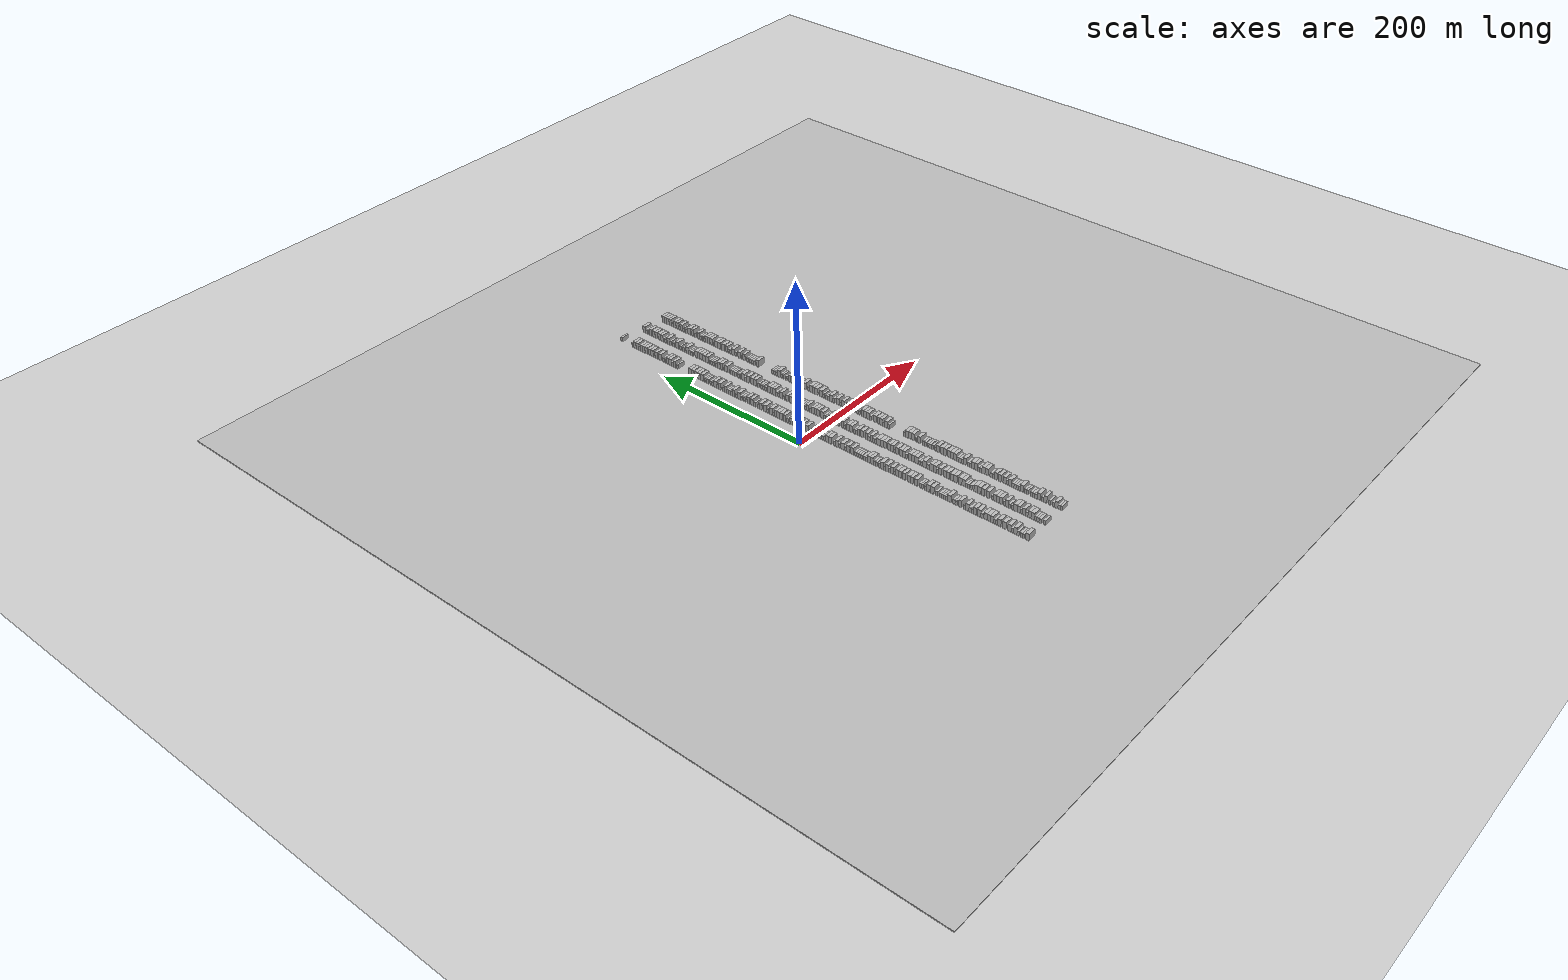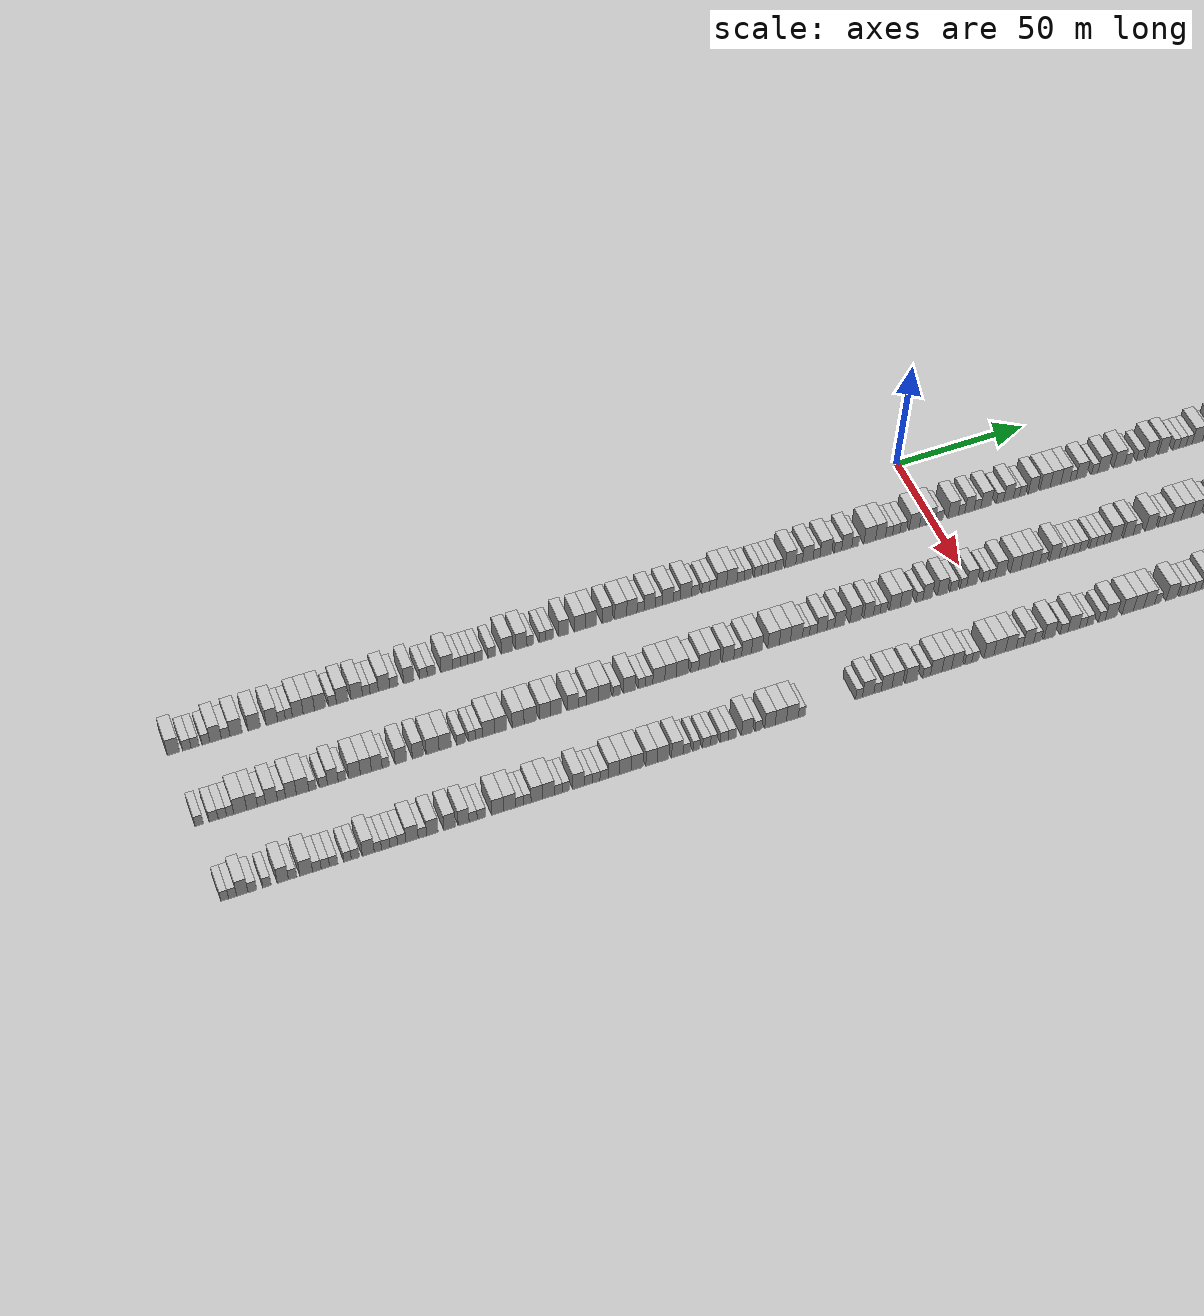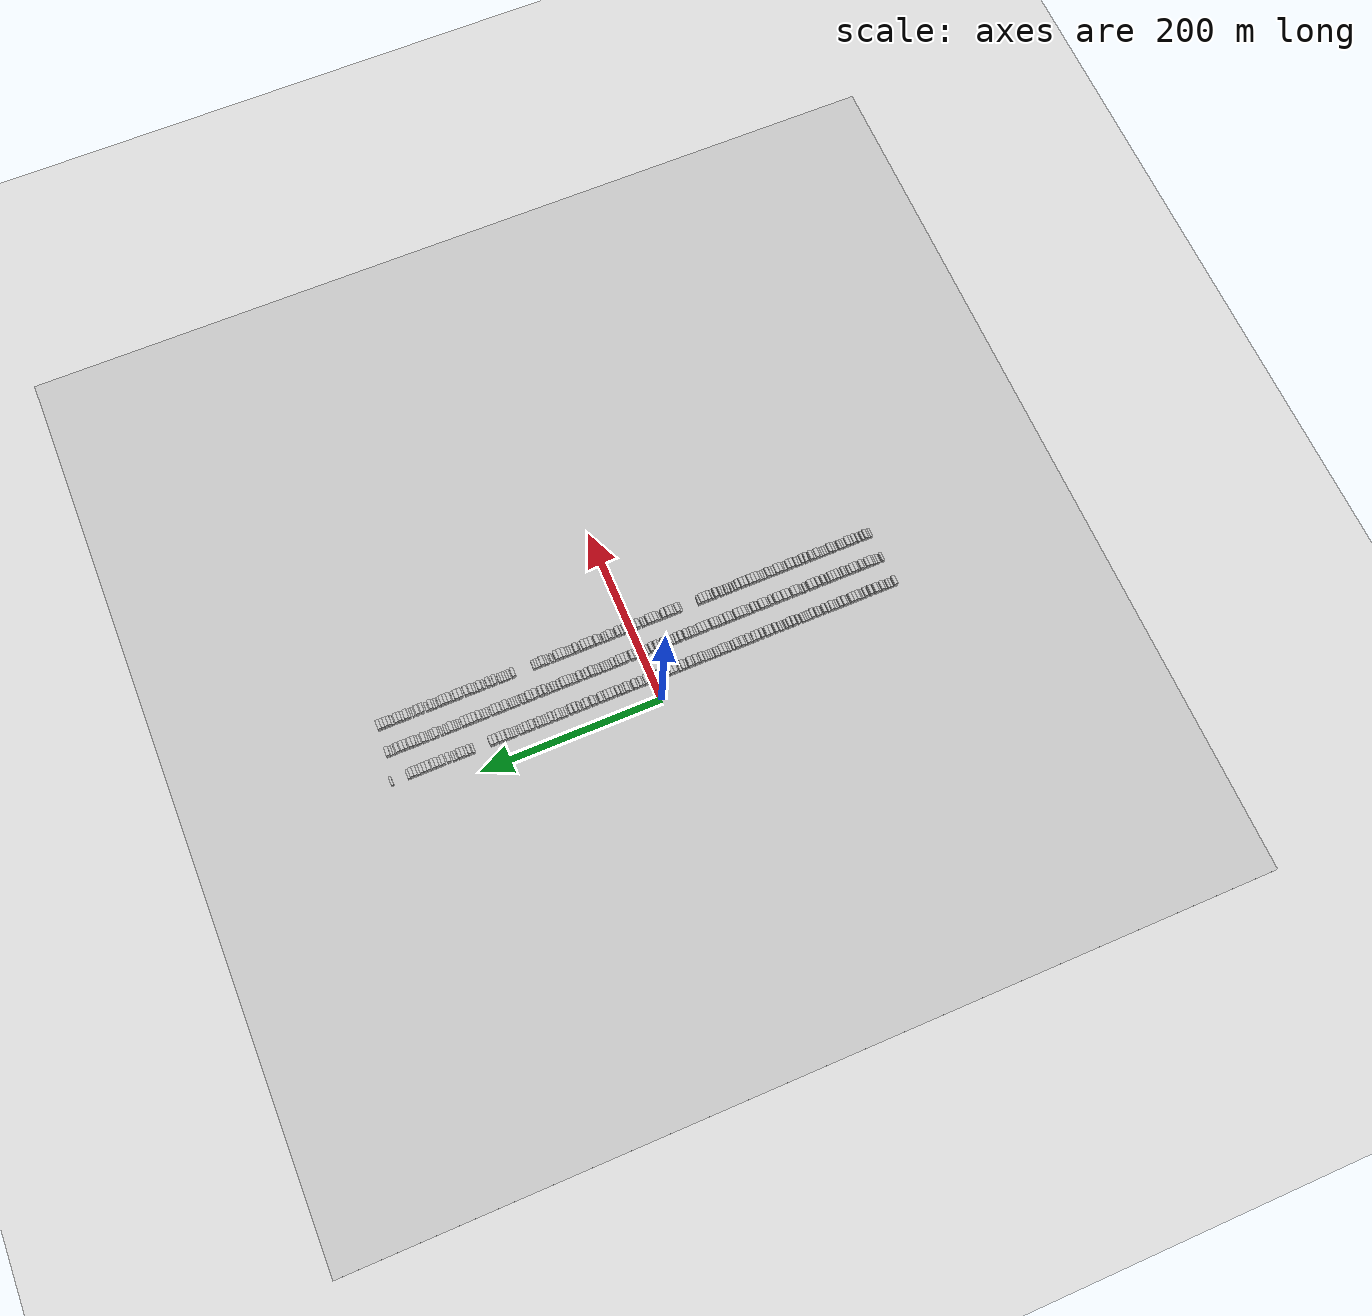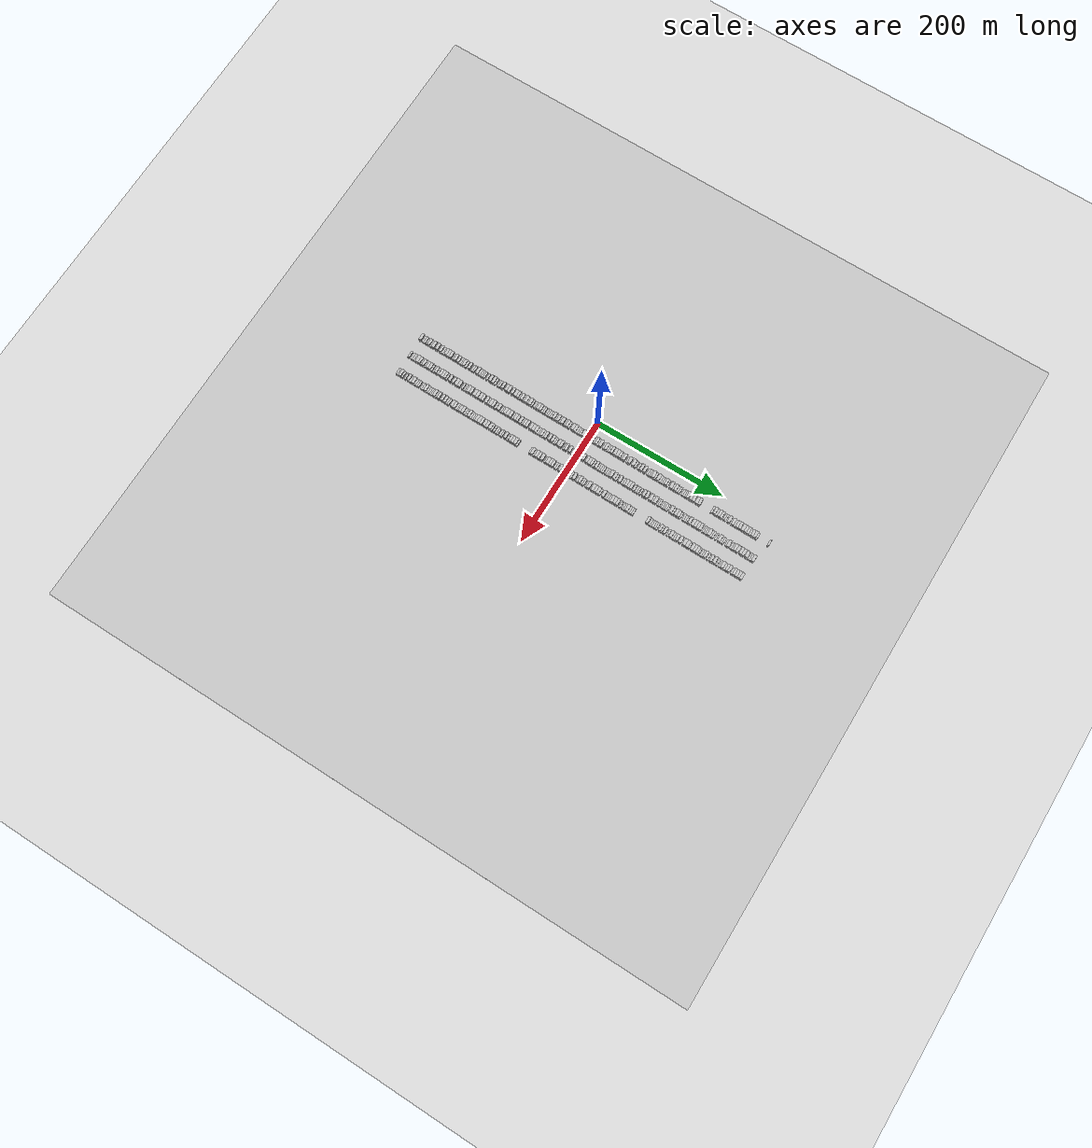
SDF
<?xml version="1.0" encoding="utf-8"?>

<sdf version="1.6">

   <world name="default">

      <gui fullscreen="0">

         <camera name="user_camera">

            <pose>-15 0 4.57585 0 0 0</pose>

            <view_controller>orbit</view_controller>

         </camera>

      </gui>

      <scene>

         <sky>

           <clouds>

             <speed>12</speed>

           </clouds>

         </sky>

         <ambient>0.4 0.4 0.4 1</ambient>

         <background>0.7 0.7 0.7 1</background>

         <shadows>1</shadows>

      </scene>

      <gravity>0 0 -9.8066</gravity>

      <magnetic_field>6e-06 2.3e-05 -4.2e-05</magnetic_field>

      <physics default="0" name="default_physics" type="ode">

         <ode>

            <solver>

               <type>quick</type>

               <iters>10</iters>

               <sor>1.0</sor>

               <use_dynamic_moi_rescaling>0</use_dynamic_moi_rescaling>

            </solver>

            <constraints>

               <cfm>0</cfm>

               <erp>0.2</erp>

               <contact_max_correcting_vel>100</contact_max_correcting_vel>

               <contact_surface_layer>0.001</contact_surface_layer>

            </constraints>

         </ode>

         <max_step_size>0.004</max_step_size>

         <real_time_factor>1</real_time_factor>

         <real_time_update_rate>250</real_time_update_rate>

      </physics>

      <light name="sun" type="directional">

         <cast_shadows>1</cast_shadows>

         <pose>0 0 10 0 0 0</pose>

         <diffuse>0.8 0.8 0.8 1</diffuse>

         <specular>0.2 0.2 0.2 1</specular>

         <attenuation>

            <range>1000</range>

            <constant>0.9</constant>

            <linear>0.01</linear>

            <quadratic>0.001</quadratic>

         </attenuation>

         <direction>-0.5 0.1 -0.9</direction>

      </light>

      <include>

         <name>ground_plane_1</name>

         <uri>model://HANNAS_ground_plane</uri>

         <pose>0 0 0  0 0 0</pose>

      </include>

      <include>

         <name>ground_plane_2</name>

         <uri>model://HANNAS_ground_plane</uri>

         <pose>100 0 0  0 0 0</pose>

      </include>

      <model name="building_1">

         <static>1</static>

         <pose frame="">25.0000 -277.8906 0 0.000000 0.000000 0.000000</pose>

         <link name="link">

            <pose frame="">0 0 4.50 0 0 0</pose>

            <collision name="collision">

               <geometry>

                  <box>

                     <size>10.0000 4.2188 9.0000</size>

                  </box>

               </geometry>

               <max_contacts>10</max_contacts>

               <surface>

                  <contact>

                     <ode/>

                  </contact>

                  <bounce/>

                  <friction>

                     <torsional>

                        <ode/>

                     </torsional>

                     <ode/>

                  </friction>

               </surface>

            </collision>

            <visual name="visual">

               <cast_shadows>0</cast_shadows>

               <geometry>

                  <box>

                     <size>10.0000 4.2188 9.0000</size>

                  </box>

               </geometry>

               <material>

                  <script>

                     <uri>model://HANNAS_wall/materials/scripts</uri>

                     <uri>model://HANNAS_wall/materials/textures</uri>

                     <name>vrc/HANNAS_wall</name>

                  </script>

               </material>

            </visual>

            <self_collide>0</self_collide>

            <enable_wind>0</enable_wind>

            <kinematic>0</kinematic>

         </link>

      </model>

      <model name="building_2">

         <static>1</static>

         <pose frame="">25.0000 -273.3320 0 0.000000 0.000000 0.000000</pose>

         <link name="link">

            <pose frame="">0 0 3.00 0 0 0</pose>

            <collision name="collision">

               <geometry>

                  <box>

                     <size>10.0000 2.8983 6.0000</size>

                  </box>

               </geometry>

               <max_contacts>10</max_contacts>

               <surface>

                  <contact>

                     <ode/>

                  </contact>

                  <bounce/>

                  <friction>

                     <torsional>

                        <ode/>

                     </torsional>

                     <ode/>

                  </friction>

               </surface>

            </collision>

            <visual name="visual">

               <cast_shadows>0</cast_shadows>

               <geometry>

                  <box>

                     <size>10.0000 2.8983 6.0000</size>

                  </box>

               </geometry>

               <material>

                  <script>

                     <uri>model://HANNAS_wall/materials/scripts</uri>

                     <uri>model://HANNAS_wall/materials/textures</uri>

                     <name>vrc/HANNAS_wall</name>

                  </script>

               </material>

            </visual>

            <self_collide>0</self_collide>

            <enable_wind>0</enable_wind>

            <kinematic>0</kinematic>

         </link>

      </model>

      <model name="building_3">

         <static>1</static>

         <pose frame="">25.0000 -270.5015 0 0.000000 0.000000 0.000000</pose>

         <link name="link">

            <pose frame="">0 0 3.00 0 0 0</pose>

            <collision name="collision">

               <geometry>

                  <box>

                     <size>10.0000 2.7627 6.0000</size>

                  </box>

               </geometry>

               <max_contacts>10</max_contacts>

               <surface>

                  <contact>

                     <ode/>

                  </contact>

                  <bounce/>

                  <friction>

                     <torsional>

                        <ode/>

                     </torsional>

                     <ode/>

                  </friction>

               </surface>

            </collision>

            <visual name="visual">

               <cast_shadows>0</cast_shadows>

               <geometry>

                  <box>

                     <size>10.0000 2.7627 6.0000</size>

                  </box>

               </geometry>

               <material>

                  <script>

                     <uri>model://HANNAS_wall/materials/scripts</uri>

                     <uri>model://HANNAS_wall/materials/textures</uri>

                     <name>vrc/HANNAS_wall</name>

                  </script>

               </material>

            </visual>

            <self_collide>0</self_collide>

            <enable_wind>0</enable_wind>

            <kinematic>0</kinematic>

         </link>

      </model>

      <model name="building_4">

         <static>1</static>

         <pose frame="">25.0000 -266.7735 0 0.000000 0.000000 0.000000</pose>

         <link name="link">

            <pose frame="">0 0 3.00 0 0 0</pose>

            <collision name="collision">

               <geometry>

                  <box>

                     <size>10.0000 2.6932 6.0000</size>

                  </box>

               </geometry>

               <max_contacts>10</max_contacts>

               <surface>

                  <contact>

                     <ode/>

                  </contact>

                  <bounce/>

                  <friction>

                     <torsional>

                        <ode/>

                     </torsional>

                     <ode/>

                  </friction>

               </surface>

            </collision>

            <visual name="visual">

               <cast_shadows>0</cast_shadows>

               <geometry>

                  <box>

                     <size>10.0000 2.6932 6.0000</size>

                  </box>

               </geometry>

               <material>

                  <script>

                     <uri>model://HANNAS_wall/materials/scripts</uri>

                     <uri>model://HANNAS_wall/materials/textures</uri>

                     <name>vrc/HANNAS_wall</name>

                  </script>

               </material>

            </visual>

            <self_collide>0</self_collide>

            <enable_wind>0</enable_wind>

            <kinematic>0</kinematic>

         </link>

      </model>

      <model name="building_5">

         <static>1</static>

         <pose frame="">25.0000 -263.4617 0 0.000000 0.000000 0.000000</pose>

         <link name="link">

            <pose frame="">0 0 4.50 0 0 0</pose>

            <collision name="collision">

               <geometry>

                  <box>

                     <size>10.0000 3.9302 9.0000</size>

                  </box>

               </geometry>

               <max_contacts>10</max_contacts>

               <surface>

                  <contact>

                     <ode/>

                  </contact>

                  <bounce/>

                  <friction>

                     <torsional>

                        <ode/>

                     </torsional>

                     <ode/>

                  </friction>

               </surface>

            </collision>

            <visual name="visual">

               <cast_shadows>0</cast_shadows>

               <geometry>

                  <box>

                     <size>10.0000 3.9302 9.0000</size>

                  </box>

               </geometry>

               <material>

                  <script>

                     <uri>model://HANNAS_wall/materials/scripts</uri>

                     <uri>model://HANNAS_wall/materials/textures</uri>

                     <name>vrc/HANNAS_wall</name>

                  </script>

               </material>

            </visual>

            <self_collide>0</self_collide>

            <enable_wind>0</enable_wind>

            <kinematic>0</kinematic>

         </link>

      </model>

      <model name="building_6">

         <static>1</static>

         <pose frame="">25.0000 -259.9984 0 0.000000 0.000000 0.000000</pose>

         <link name="link">

            <pose frame="">0 0 3.00 0 0 0</pose>

            <collision name="collision">

               <geometry>

                  <box>

                     <size>10.0000 2.9965 6.0000</size>

                  </box>

               </geometry>

               <max_contacts>10</max_contacts>

               <surface>

                  <contact>

                     <ode/>

                  </contact>

                  <bounce/>

                  <friction>

                     <torsional>

                        <ode/>

                     </torsional>

                     <ode/>

                  </friction>

               </surface>

            </collision>

            <visual name="visual">

               <cast_shadows>0</cast_shadows>

               <geometry>

                  <box>

                     <size>10.0000 2.9965 6.0000</size>

                  </box>

               </geometry>

               <material>

                  <script>

                     <uri>model://HANNAS_wall/materials/scripts</uri>

                     <uri>model://HANNAS_wall/materials/textures</uri>

                     <name>vrc/HANNAS_wall</name>

                  </script>

               </material>

            </visual>

            <self_collide>0</self_collide>

            <enable_wind>0</enable_wind>

            <kinematic>0</kinematic>

         </link>

      </model>

      <model name="building_7">

         <static>1</static>

         <pose frame="">25.0000 -256.3856 0 0.000000 0.000000 0.000000</pose>

         <link name="link">

            <pose frame="">0 0 4.50 0 0 0</pose>

            <collision name="collision">

               <geometry>

                  <box>

                     <size>10.0000 4.2292 9.0000</size>

                  </box>

               </geometry>

               <max_contacts>10</max_contacts>

               <surface>

                  <contact>

                     <ode/>

                  </contact>

                  <bounce/>

                  <friction>

                     <torsional>

                        <ode/>

                     </torsional>

                     <ode/>

                  </friction>

               </surface>

            </collision>

            <visual name="visual">

               <cast_shadows>0</cast_shadows>

               <geometry>

                  <box>

                     <size>10.0000 4.2292 9.0000</size>

                  </box>

               </geometry>

               <material>

                  <script>

                     <uri>model://HANNAS_wall/materials/scripts</uri>

                     <uri>model://HANNAS_wall/materials/textures</uri>

                     <name>vrc/HANNAS_wall</name>

                  </script>

               </material>

            </visual>

            <self_collide>0</self_collide>

            <enable_wind>0</enable_wind>

            <kinematic>0</kinematic>

         </link>

      </model>

      <model name="building_8">

         <static>1</static>

         <pose frame="">25.0000 -250.1284 0 0.000000 0.000000 0.000000</pose>

         <link name="link">

            <pose frame="">0 0 4.50 0 0 0</pose>

            <collision name="collision">

               <geometry>

                  <box>

                     <size>10.0000 4.2851 9.0000</size>

                  </box>

               </geometry>

               <max_contacts>10</max_contacts>

               <surface>

                  <contact>

                     <ode/>

                  </contact>

                  <bounce/>

                  <friction>

                     <torsional>

                        <ode/>

                     </torsional>

                     <ode/>

                  </friction>

               </surface>

            </collision>

            <visual name="visual">

               <cast_shadows>0</cast_shadows>

               <geometry>

                  <box>

                     <size>10.0000 4.2851 9.0000</size>

                  </box>

               </geometry>

               <material>

                  <script>

                     <uri>model://HANNAS_wall/materials/scripts</uri>

                     <uri>model://HANNAS_wall/materials/textures</uri>

                     <name>vrc/HANNAS_wall</name>

                  </script>

               </material>

            </visual>

            <self_collide>0</self_collide>

            <enable_wind>0</enable_wind>

            <kinematic>0</kinematic>

         </link>

      </model>

      <model name="building_9">

         <static>1</static>

         <pose frame="">25.0000 -243.9807 0 0.000000 0.000000 0.000000</pose>

         <link name="link">

            <pose frame="">0 0 4.50 0 0 0</pose>

            <collision name="collision">

               <geometry>

                  <box>

                     <size>10.0000 4.0104 9.0000</size>

                  </box>

               </geometry>

               <max_contacts>10</max_contacts>

               <surface>

                  <contact>

                     <ode/>

                  </contact>

                  <bounce/>

                  <friction>

                     <torsional>

                        <ode/>

                     </torsional>

                     <ode/>

                  </friction>

               </surface>

            </collision>

            <visual name="visual">

               <cast_shadows>0</cast_shadows>

               <geometry>

                  <box>

                     <size>10.0000 4.0104 9.0000</size>

                  </box>

               </geometry>

               <material>

                  <script>

                     <uri>model://HANNAS_wall/materials/scripts</uri>

                     <uri>model://HANNAS_wall/materials/textures</uri>

                     <name>vrc/HANNAS_wall</name>

                  </script>

               </material>

            </visual>

            <self_collide>0</self_collide>

            <enable_wind>0</enable_wind>

            <kinematic>0</kinematic>

         </link>

      </model>

      <model name="building_10">

         <static>1</static>

         <pose frame="">25.0000 -240.6543 0 0.000000 0.000000 0.000000</pose>

         <link name="link">

            <pose frame="">0 0 3.00 0 0 0</pose>

            <collision name="collision">

               <geometry>

                  <box>

                     <size>10.0000 2.6423 6.0000</size>

                  </box>

               </geometry>

               <max_contacts>10</max_contacts>

               <surface>

                  <contact>

                     <ode/>

                  </contact>

                  <bounce/>

                  <friction>

                     <torsional>

                        <ode/>

                     </torsional>

                     <ode/>

                  </friction>

               </surface>

            </collision>

            <visual name="visual">

               <cast_shadows>0</cast_shadows>

               <geometry>

                  <box>

                     <size>10.0000 2.6423 6.0000</size>

                  </box>

               </geometry>

               <material>

                  <script>

                     <uri>model://HANNAS_wall/materials/scripts</uri>

                     <uri>model://HANNAS_wall/materials/textures</uri>

                     <name>vrc/HANNAS_wall</name>

                  </script>

               </material>

            </visual>

            <self_collide>0</self_collide>

            <enable_wind>0</enable_wind>

            <kinematic>0</kinematic>

         </link>

      </model>

      <model name="building_11">

         <static>1</static>

         <pose frame="">25.0000 -238.0924 0 0.000000 0.000000 0.000000</pose>

         <link name="link">

            <pose frame="">0 0 3.00 0 0 0</pose>

            <collision name="collision">

               <geometry>

                  <box>

                     <size>10.0000 2.4815 6.0000</size>

                  </box>

               </geometry>

               <max_contacts>10</max_contacts>

               <surface>

                  <contact>

                     <ode/>

                  </contact>

                  <bounce/>

                  <friction>

                     <torsional>

                        <ode/>

                     </torsional>

                     <ode/>

                  </friction>

               </surface>

            </collision>

            <visual name="visual">

               <cast_shadows>0</cast_shadows>

               <geometry>

                  <box>

                     <size>10.0000 2.4815 6.0000</size>

                  </box>

               </geometry>

               <material>

                  <script>

                     <uri>model://HANNAS_wall/materials/scripts</uri>

                     <uri>model://HANNAS_wall/materials/textures</uri>

                     <name>vrc/HANNAS_wall</name>

                  </script>

               </material>

            </visual>

            <self_collide>0</self_collide>

            <enable_wind>0</enable_wind>

            <kinematic>0</kinematic>

         </link>

      </model>

      <model name="building_12">

         <static>1</static>

         <pose frame="">25.0000 -234.9972 0 0.000000 0.000000 0.000000</pose>

         <link name="link">

            <pose frame="">0 0 4.50 0 0 0</pose>

            <collision name="collision">

               <geometry>

                  <box>

                     <size>10.0000 3.7088 9.0000</size>

                  </box>

               </geometry>

               <max_contacts>10</max_contacts>

               <surface>

                  <contact>

                     <ode/>

                  </contact>

                  <bounce/>

                  <friction>

                     <torsional>

                        <ode/>

                     </torsional>

                     <ode/>

                  </friction>

               </surface>

            </collision>

            <visual name="visual">

               <cast_shadows>0</cast_shadows>

               <geometry>

                  <box>

                     <size>10.0000 3.7088 9.0000</size>

                  </box>

               </geometry>

               <material>

                  <script>

                     <uri>model://HANNAS_wall/materials/scripts</uri>

                     <uri>model://HANNAS_wall/materials/textures</uri>

                     <name>vrc/HANNAS_wall</name>

                  </script>

               </material>

            </visual>

            <self_collide>0</self_collide>

            <enable_wind>0</enable_wind>

            <kinematic>0</kinematic>

         </link>

      </model>

      <model name="building_13">

         <static>1</static>

         <pose frame="">25.0000 -231.1605 0 0.000000 0.000000 0.000000</pose>

         <link name="link">

            <pose frame="">0 0 4.50 0 0 0</pose>

            <collision name="collision">

               <geometry>

                  <box>

                     <size>10.0000 3.9646 9.0000</size>

                  </box>

               </geometry>

               <max_contacts>10</max_contacts>

               <surface>

                  <contact>

                     <ode/>

                  </contact>

                  <bounce/>

                  <friction>

                     <torsional>

                        <ode/>

                     </torsional>

                     <ode/>

                  </friction>

               </surface>

            </collision>

            <visual name="visual">

               <cast_shadows>0</cast_shadows>

               <geometry>

                  <box>

                     <size>10.0000 3.9646 9.0000</size>

                  </box>

               </geometry>

               <material>

                  <script>

                     <uri>model://HANNAS_wall/materials/scripts</uri>

                     <uri>model://HANNAS_wall/materials/textures</uri>

                     <name>vrc/HANNAS_wall</name>

                  </script>

               </material>

            </visual>

            <self_collide>0</self_collide>

            <enable_wind>0</enable_wind>

            <kinematic>0</kinematic>

         </link>

      </model>

      <model name="building_14">

         <static>1</static>

         <pose frame="">25.0000 -227.1879 0 0.000000 0.000000 0.000000</pose>

         <link name="link">

            <pose frame="">0 0 4.50 0 0 0</pose>

            <collision name="collision">

               <geometry>

                  <box>

                     <size>10.0000 3.9807 9.0000</size>

                  </box>

               </geometry>

               <max_contacts>10</max_contacts>

               <surface>

                  <contact>

                     <ode/>

                  </contact>

                  <bounce/>

                  <friction>

                     <torsional>

                        <ode/>

                     </torsional>

                     <ode/>

                  </friction>

               </surface>

            </collision>

            <visual name="visual">

               <cast_shadows>0</cast_shadows>

               <geometry>

                  <box>

                     <size>10.0000 3.9807 9.0000</size>

                  </box>

               </geometry>

               <material>

                  <script>

                     <uri>model://HANNAS_wall/materials/scripts</uri>

                     <uri>model://HANNAS_wall/materials/textures</uri>

                     <name>vrc/HANNAS_wall</name>

                  </script>

               </material>

            </visual>

            <self_collide>0</self_collide>

            <enable_wind>0</enable_wind>

            <kinematic>0</kinematic>

         </link>

      </model>

      <model name="building_15">

         <static>1</static>

         <pose frame="">25.0000 -222.8394 0 0.000000 0.000000 0.000000</pose>

         <link name="link">

            <pose frame="">0 0 3.00 0 0 0</pose>

            <collision name="collision">

               <geometry>

                  <box>

                     <size>10.0000 2.7163 6.0000</size>

                  </box>

               </geometry>

               <max_contacts>10</max_contacts>

               <surface>

                  <contact>

                     <ode/>

                  </contact>

                  <bounce/>

                  <friction>

                     <torsional>

                        <ode/>

                     </torsional>

                     <ode/>

                  </friction>

               </surface>

            </collision>

            <visual name="visual">

               <cast_shadows>0</cast_shadows>

               <geometry>

                  <box>

                     <size>10.0000 2.7163 6.0000</size>

                  </box>

               </geometry>

               <material>

                  <script>

                     <uri>model://HANNAS_wall/materials/scripts</uri>

                     <uri>model://HANNAS_wall/materials/textures</uri>

                     <name>vrc/HANNAS_wall</name>

                  </script>

               </material>

            </visual>

            <self_collide>0</self_collide>

            <enable_wind>0</enable_wind>

            <kinematic>0</kinematic>

         </link>

      </model>

      <model name="building_16">

         <static>1</static>

         <pose frame="">25.0000 -219.4220 0 0.000000 0.000000 0.000000</pose>

         <link name="link">

            <pose frame="">0 0 4.50 0 0 0</pose>

            <collision name="collision">

               <geometry>

                  <box>

                     <size>10.0000 4.1185 9.0000</size>

                  </box>

               </geometry>

               <max_contacts>10</max_contacts>

               <surface>

                  <contact>

                     <ode/>

                  </contact>

                  <bounce/>

                  <friction>

                     <torsional>

                        <ode/>

                     </torsional>

                     <ode/>

                  </friction>

               </surface>

            </collision>

            <visual name="visual">

               <cast_shadows>0</cast_shadows>

               <geometry>

                  <box>

                     <size>10.0000 4.1185 9.0000</size>

                  </box>

               </geometry>

               <material>

                  <script>

                     <uri>model://HANNAS_wall/materials/scripts</uri>

                     <uri>model://HANNAS_wall/materials/textures</uri>

                     <name>vrc/HANNAS_wall</name>

                  </script>

               </material>

            </visual>

            <self_collide>0</self_collide>

            <enable_wind>0</enable_wind>

            <kinematic>0</kinematic>

         </link>

      </model>

      <model name="building_17">

         <static>1</static>

         <pose frame="">25.0000 -214.3357 0 0.000000 0.000000 0.000000</pose>

         <link name="link">

            <pose frame="">0 0 4.50 0 0 0</pose>

            <collision name="collision">

               <geometry>

                  <box>

                     <size>10.0000 4.0542 9.0000</size>

                  </box>

               </geometry>

               <max_contacts>10</max_contacts>

               <surface>

                  <contact>

                     <ode/>

                  </contact>

                  <bounce/>

                  <friction>

                     <torsional>

                        <ode/>

                     </torsional>

                     <ode/>

                  </friction>

               </surface>

            </collision>

            <visual name="visual">

               <cast_shadows>0</cast_shadows>

               <geometry>

                  <box>

                     <size>10.0000 4.0542 9.0000</size>

                  </box>

               </geometry>

               <material>

                  <script>

                     <uri>model://HANNAS_wall/materials/scripts</uri>

                     <uri>model://HANNAS_wall/materials/textures</uri>

                     <name>vrc/HANNAS_wall</name>

                  </script>

               </material>

            </visual>

            <self_collide>0</self_collide>

            <enable_wind>0</enable_wind>

            <kinematic>0</kinematic>

         </link>

      </model>

      <model name="building_18">

         <static>1</static>

         <pose frame="">25.0000 -210.9872 0 0.000000 0.000000 0.000000</pose>

         <link name="link">

            <pose frame="">0 0 3.00 0 0 0</pose>

            <collision name="collision">

               <geometry>

                  <box>

                     <size>10.0000 2.6428 6.0000</size>

                  </box>

               </geometry>

               <max_contacts>10</max_contacts>

               <surface>

                  <contact>

                     <ode/>

                  </contact>

                  <bounce/>

                  <friction>

                     <torsional>

                        <ode/>

                     </torsional>

                     <ode/>

                  </friction>

               </surface>

            </collision>

            <visual name="visual">

               <cast_shadows>0</cast_shadows>

               <geometry>

                  <box>

                     <size>10.0000 2.6428 6.0000</size>

                  </box>

               </geometry>

               <material>

                  <script>

                     <uri>model://HANNAS_wall/materials/scripts</uri>

                     <uri>model://HANNAS_wall/materials/textures</uri>

                     <name>vrc/HANNAS_wall</name>

                  </script>

               </material>

            </visual>

            <self_collide>0</self_collide>

            <enable_wind>0</enable_wind>

            <kinematic>0</kinematic>

         </link>

      </model>

      <model name="building_19">

         <static>1</static>

         <pose frame="">25.0000 -208.1965 0 0.000000 0.000000 0.000000</pose>

         <link name="link">

            <pose frame="">0 0 3.00 0 0 0</pose>

            <collision name="collision">

               <geometry>

                  <box>

                     <size>10.0000 2.9387 6.0000</size>

                  </box>

               </geometry>

               <max_contacts>10</max_contacts>

               <surface>

                  <contact>

                     <ode/>

                  </contact>

                  <bounce/>

                  <friction>

                     <torsional>

                        <ode/>

                     </torsional>

                     <ode/>

                  </friction>

               </surface>

            </collision>

            <visual name="visual">

               <cast_shadows>0</cast_shadows>

               <geometry>

                  <box>

                     <size>10.0000 2.9387 6.0000</size>

                  </box>

               </geometry>

               <material>

                  <script>

                     <uri>model://HANNAS_wall/materials/scripts</uri>

                     <uri>model://HANNAS_wall/materials/textures</uri>

                     <name>vrc/HANNAS_wall</name>

                  </script>

               </material>

            </visual>

            <self_collide>0</self_collide>

            <enable_wind>0</enable_wind>

            <kinematic>0</kinematic>

         </link>

      </model>

      <model name="building_20">

         <static>1</static>

         <pose frame="">25.0000 -204.7054 0 0.000000 0.000000 0.000000</pose>

         <link name="link">

            <pose frame="">0 0 4.50 0 0 0</pose>

            <collision name="collision">

               <geometry>

                  <box>

                     <size>10.0000 4.0435 9.0000</size>

                  </box>

               </geometry>

               <max_contacts>10</max_contacts>

               <surface>

                  <contact>

                     <ode/>

                  </contact>

                  <bounce/>

                  <friction>

                     <torsional>

                        <ode/>

                     </torsional>

                     <ode/>

                  </friction>

               </surface>

            </collision>

            <visual name="visual">

               <cast_shadows>0</cast_shadows>

               <geometry>

                  <box>

                     <size>10.0000 4.0435 9.0000</size>

                  </box>

               </geometry>

               <material>

                  <script>

                     <uri>model://HANNAS_wall/materials/scripts</uri>

                     <uri>model://HANNAS_wall/materials/textures</uri>

                     <name>vrc/HANNAS_wall</name>

                  </script>

               </material>

            </visual>

            <self_collide>0</self_collide>

            <enable_wind>0</enable_wind>

            <kinematic>0</kinematic>

         </link>

      </model>

      <model name="building_21">

         <static>1</static>

         <pose frame="">25.0000 -201.2063 0 0.000000 0.000000 0.000000</pose>

         <link name="link">

            <pose frame="">0 0 3.00 0 0 0</pose>

            <collision name="collision">

               <geometry>

                  <box>

                     <size>10.0000 2.9545 6.0000</size>

                  </box>

               </geometry>

               <max_contacts>10</max_contacts>

               <surface>

                  <contact>

                     <ode/>

                  </contact>

                  <bounce/>

                  <friction>

                     <torsional>

                        <ode/>

                     </torsional>

                     <ode/>

                  </friction>

               </surface>

            </collision>

            <visual name="visual">

               <cast_shadows>0</cast_shadows>

               <geometry>

                  <box>

                     <size>10.0000 2.9545 6.0000</size>

                  </box>

               </geometry>

               <material>

                  <script>

                     <uri>model://HANNAS_wall/materials/scripts</uri>

                     <uri>model://HANNAS_wall/materials/textures</uri>

                     <name>vrc/HANNAS_wall</name>

                  </script>

               </material>

            </visual>

            <self_collide>0</self_collide>

            <enable_wind>0</enable_wind>

            <kinematic>0</kinematic>

         </link>

      </model>

      <model name="building_22">

         <static>1</static>

         <pose frame="">25.0000 -195.9023 0 0.000000 0.000000 0.000000</pose>

         <link name="link">

            <pose frame="">0 0 4.50 0 0 0</pose>

            <collision name="collision">

               <geometry>

                  <box>

                     <size>10.0000 3.6534 9.0000</size>

                  </box>

               </geometry>

               <max_contacts>10</max_contacts>

               <surface>

                  <contact>

                     <ode/>

                  </contact>

                  <bounce/>

                  <friction>

                     <torsional>

                        <ode/>

                     </torsional>

                     <ode/>

                  </friction>

               </surface>

            </collision>

            <visual name="visual">

               <cast_shadows>0</cast_shadows>

               <geometry>

                  <box>

                     <size>10.0000 3.6534 9.0000</size>

                  </box>

               </geometry>

               <material>

                  <script>

                     <uri>model://HANNAS_wall/materials/scripts</uri>

                     <uri>model://HANNAS_wall/materials/textures</uri>

                     <name>vrc/HANNAS_wall</name>

                  </script>

               </material>

            </visual>

            <self_collide>0</self_collide>

            <enable_wind>0</enable_wind>

            <kinematic>0</kinematic>

         </link>

      </model>

      <model name="building_23">

         <static>1</static>

         <pose frame="">25.0000 -190.7034 0 0.000000 0.000000 0.000000</pose>

         <link name="link">

            <pose frame="">0 0 3.00 0 0 0</pose>

            <collision name="collision">

               <geometry>

                  <box>

                     <size>10.0000 2.7444 6.0000</size>

                  </box>

               </geometry>

               <max_contacts>10</max_contacts>

               <surface>

                  <contact>

                     <ode/>

                  </contact>

                  <bounce/>

                  <friction>

                     <torsional>

                        <ode/>

                     </torsional>

                     <ode/>

                  </friction>

               </surface>

            </collision>

            <visual name="visual">

               <cast_shadows>0</cast_shadows>

               <geometry>

                  <box>

                     <size>10.0000 2.7444 6.0000</size>

                  </box>

               </geometry>

               <material>

                  <script>

                     <uri>model://HANNAS_wall/materials/scripts</uri>

                     <uri>model://HANNAS_wall/materials/textures</uri>

                     <name>vrc/HANNAS_wall</name>

                  </script>

               </material>

            </visual>

            <self_collide>0</self_collide>

            <enable_wind>0</enable_wind>

            <kinematic>0</kinematic>

         </link>

      </model>

      <model name="building_24">

         <static>1</static>

         <pose frame="">25.0000 -187.8845 0 0.000000 0.000000 0.000000</pose>

         <link name="link">

            <pose frame="">0 0 3.00 0 0 0</pose>

            <collision name="collision">

               <geometry>

                  <box>

                     <size>10.0000 2.8935 6.0000</size>

                  </box>

               </geometry>

               <max_contacts>10</max_contacts>

               <surface>

                  <contact>

                     <ode/>

                  </contact>

                  <bounce/>

                  <friction>

                     <torsional>

                        <ode/>

                     </torsional>

                     <ode/>

                  </friction>

               </surface>

            </collision>

            <visual name="visual">

               <cast_shadows>0</cast_shadows>

               <geometry>

                  <box>

                     <size>10.0000 2.8935 6.0000</size>

                  </box>

               </geometry>

               <material>

                  <script>

                     <uri>model://HANNAS_wall/materials/scripts</uri>

                     <uri>model://HANNAS_wall/materials/textures</uri>

                     <name>vrc/HANNAS_wall</name>

                  </script>

               </material>

            </visual>

            <self_collide>0</self_collide>

            <enable_wind>0</enable_wind>

            <kinematic>0</kinematic>

         </link>

      </model>

      <model name="building_25">

         <static>1</static>

         <pose frame="">25.0000 -182.2950 0 0.000000 0.000000 0.000000</pose>

         <link name="link">

            <pose frame="">0 0 4.50 0 0 0</pose>

            <collision name="collision">

               <geometry>

                  <box>

                     <size>10.0000 4.2855 9.0000</size>

                  </box>

               </geometry>

               <max_contacts>10</max_contacts>

               <surface>

                  <contact>

                     <ode/>

                  </contact>

                  <bounce/>

                  <friction>

                     <torsional>

                        <ode/>

                     </torsional>

                     <ode/>

                  </friction>

               </surface>

            </collision>

            <visual name="visual">

               <cast_shadows>0</cast_shadows>

               <geometry>

                  <box>

                     <size>10.0000 4.2855 9.0000</size>

                  </box>

               </geometry>

               <material>

                  <script>

                     <uri>model://HANNAS_wall/materials/scripts</uri>

                     <uri>model://HANNAS_wall/materials/textures</uri>

                     <name>vrc/HANNAS_wall</name>

                  </script>

               </material>

            </visual>

            <self_collide>0</self_collide>

            <enable_wind>0</enable_wind>

            <kinematic>0</kinematic>

         </link>

      </model>

      <model name="building_26">

         <static>1</static>

         <pose frame="">25.0000 -178.7740 0 0.000000 0.000000 0.000000</pose>

         <link name="link">

            <pose frame="">0 0 3.00 0 0 0</pose>

            <collision name="collision">

               <geometry>

                  <box>

                     <size>10.0000 2.7564 6.0000</size>

                  </box>

               </geometry>

               <max_contacts>10</max_contacts>

               <surface>

                  <contact>

                     <ode/>

                  </contact>

                  <bounce/>

                  <friction>

                     <torsional>

                        <ode/>

                     </torsional>

                     <ode/>

                  </friction>

               </surface>

            </collision>

            <visual name="visual">

               <cast_shadows>0</cast_shadows>

               <geometry>

                  <box>

                     <size>10.0000 2.7564 6.0000</size>

                  </box>

               </geometry>

               <material>

                  <script>

                     <uri>model://HANNAS_wall/materials/scripts</uri>

                     <uri>model://HANNAS_wall/materials/textures</uri>

                     <name>vrc/HANNAS_wall</name>

                  </script>

               </material>

            </visual>

            <self_collide>0</self_collide>

            <enable_wind>0</enable_wind>

            <kinematic>0</kinematic>

         </link>

      </model>

      <model name="building_27">

         <static>1</static>

         <pose frame="">25.0000 -176.1398 0 0.000000 0.000000 0.000000</pose>

         <link name="link">

            <pose frame="">0 0 3.00 0 0 0</pose>

            <collision name="collision">

               <geometry>

                  <box>

                     <size>10.0000 2.5118 6.0000</size>

                  </box>

               </geometry>

               <max_contacts>10</max_contacts>

               <surface>

                  <contact>

                     <ode/>

                  </contact>

                  <bounce/>

                  <friction>

                     <torsional>

                        <ode/>

                     </torsional>

                     <ode/>

                  </friction>

               </surface>

            </collision>

            <visual name="visual">

               <cast_shadows>0</cast_shadows>

               <geometry>

                  <box>

                     <size>10.0000 2.5118 6.0000</size>

                  </box>

               </geometry>

               <material>

                  <script>

                     <uri>model://HANNAS_wall/materials/scripts</uri>

                     <uri>model://HANNAS_wall/materials/textures</uri>

                     <name>vrc/HANNAS_wall</name>

                  </script>

               </material>

            </visual>

            <self_collide>0</self_collide>

            <enable_wind>0</enable_wind>

            <kinematic>0</kinematic>

         </link>

      </model>

      <model name="building_28">

         <static>1</static>

         <pose frame="">25.0000 -173.6152 0 0.000000 0.000000 0.000000</pose>

         <link name="link">

            <pose frame="">0 0 3.00 0 0 0</pose>

            <collision name="collision">

               <geometry>

                  <box>

                     <size>10.0000 2.5375 6.0000</size>

                  </box>

               </geometry>

               <max_contacts>10</max_contacts>

               <surface>

                  <contact>

                     <ode/>

                  </contact>

                  <bounce/>

                  <friction>

                     <torsional>

                        <ode/>

                     </torsional>

                     <ode/>

                  </friction>

               </surface>

            </collision>

            <visual name="visual">

               <cast_shadows>0</cast_shadows>

               <geometry>

                  <box>

                     <size>10.0000 2.5375 6.0000</size>

                  </box>

               </geometry>

               <material>

                  <script>

                     <uri>model://HANNAS_wall/materials/scripts</uri>

                     <uri>model://HANNAS_wall/materials/textures</uri>

                     <name>vrc/HANNAS_wall</name>

                  </script>

               </material>

            </visual>

            <self_collide>0</self_collide>

            <enable_wind>0</enable_wind>

            <kinematic>0</kinematic>

         </link>

      </model>

      <model name="building_29">

         <static>1</static>

         <pose frame="">25.0000 -170.9428 0 0.000000 0.000000 0.000000</pose>

         <link name="link">

            <pose frame="">0 0 3.00 0 0 0</pose>

            <collision name="collision">

               <geometry>

                  <box>

                     <size>10.0000 2.8074 6.0000</size>

                  </box>

               </geometry>

               <max_contacts>10</max_contacts>

               <surface>

                  <contact>

                     <ode/>

                  </contact>

                  <bounce/>

                  <friction>

                     <torsional>

                        <ode/>

                     </torsional>

                     <ode/>

                  </friction>

               </surface>

            </collision>

            <visual name="visual">

               <cast_shadows>0</cast_shadows>

               <geometry>

                  <box>

                     <size>10.0000 2.8074 6.0000</size>

                  </box>

               </geometry>

               <material>

                  <script>

                     <uri>model://HANNAS_wall/materials/scripts</uri>

                     <uri>model://HANNAS_wall/materials/textures</uri>

                     <name>vrc/HANNAS_wall</name>

                  </script>

               </material>

            </visual>

            <self_collide>0</self_collide>

            <enable_wind>0</enable_wind>

            <kinematic>0</kinematic>

         </link>

      </model>

      <model name="building_30">

         <static>1</static>

         <pose frame="">25.0000 -166.1350 0 0.000000 0.000000 0.000000</pose>

         <link name="link">

            <pose frame="">0 0 3.00 0 0 0</pose>

            <collision name="collision">

               <geometry>

                  <box>

                     <size>10.0000 2.8080 6.0000</size>

                  </box>

               </geometry>

               <max_contacts>10</max_contacts>

               <surface>

                  <contact>

                     <ode/>

                  </contact>

                  <bounce/>

                  <friction>

                     <torsional>

                        <ode/>

                     </torsional>

                     <ode/>

                  </friction>

               </surface>

            </collision>

            <visual name="visual">

               <cast_shadows>0</cast_shadows>

               <geometry>

                  <box>

                     <size>10.0000 2.8080 6.0000</size>

                  </box>

               </geometry>

               <material>

                  <script>

                     <uri>model://HANNAS_wall/materials/scripts</uri>

                     <uri>model://HANNAS_wall/materials/textures</uri>

                     <name>vrc/HANNAS_wall</name>

                  </script>

               </material>

            </visual>

            <self_collide>0</self_collide>

            <enable_wind>0</enable_wind>

            <kinematic>0</kinematic>

         </link>

      </model>

      <model name="building_31">

         <static>1</static>

         <pose frame="">25.0000 -160.6640 0 0.000000 0.000000 0.000000</pose>

         <link name="link">

            <pose frame="">0 0 4.50 0 0 0</pose>

            <collision name="collision">

               <geometry>

                  <box>

                     <size>10.0000 4.1341 9.0000</size>

                  </box>

               </geometry>

               <max_contacts>10</max_contacts>

               <surface>

                  <contact>

                     <ode/>

                  </contact>

                  <bounce/>

                  <friction>

                     <torsional>

                        <ode/>

                     </torsional>

                     <ode/>

                  </friction>

               </surface>

            </collision>

            <visual name="visual">

               <cast_shadows>0</cast_shadows>

               <geometry>

                  <box>

                     <size>10.0000 4.1341 9.0000</size>

                  </box>

               </geometry>

               <material>

                  <script>

                     <uri>model://HANNAS_wall/materials/scripts</uri>

                     <uri>model://HANNAS_wall/materials/textures</uri>

                     <name>vrc/HANNAS_wall</name>

                  </script>

               </material>

            </visual>

            <self_collide>0</self_collide>

            <enable_wind>0</enable_wind>

            <kinematic>0</kinematic>

         </link>

      </model>

      <model name="building_32">

         <static>1</static>

         <pose frame="">25.0000 -155.5202 0 0.000000 0.000000 0.000000</pose>

         <link name="link">

            <pose frame="">0 0 4.50 0 0 0</pose>

            <collision name="collision">

               <geometry>

                  <box>

                     <size>10.0000 4.1533 9.0000</size>

                  </box>

               </geometry>

               <max_contacts>10</max_contacts>

               <surface>

                  <contact>

                     <ode/>

                  </contact>

                  <bounce/>

                  <friction>

                     <torsional>

                        <ode/>

                     </torsional>

                     <ode/>

                  </friction>

               </surface>

            </collision>

            <visual name="visual">

               <cast_shadows>0</cast_shadows>

               <geometry>

                  <box>

                     <size>10.0000 4.1533 9.0000</size>

                  </box>

               </geometry>

               <material>

                  <script>

                     <uri>model://HANNAS_wall/materials/scripts</uri>

                     <uri>model://HANNAS_wall/materials/textures</uri>

                     <name>vrc/HANNAS_wall</name>

                  </script>

               </material>

            </visual>

            <self_collide>0</self_collide>

            <enable_wind>0</enable_wind>

            <kinematic>0</kinematic>

         </link>

      </model>

      <model name="building_33">

         <static>1</static>

         <pose frame="">25.0000 -152.2202 0 0.000000 0.000000 0.000000</pose>

         <link name="link">

            <pose frame="">0 0 3.00 0 0 0</pose>

            <collision name="collision">

               <geometry>

                  <box>

                     <size>10.0000 2.4468 6.0000</size>

                  </box>

               </geometry>

               <max_contacts>10</max_contacts>

               <surface>

                  <contact>

                     <ode/>

                  </contact>

                  <bounce/>

                  <friction>

                     <torsional>

                        <ode/>

                     </torsional>

                     <ode/>

                  </friction>

               </surface>

            </collision>

            <visual name="visual">

               <cast_shadows>0</cast_shadows>

               <geometry>

                  <box>

                     <size>10.0000 2.4468 6.0000</size>

                  </box>

               </geometry>

               <material>

                  <script>

                     <uri>model://HANNAS_wall/materials/scripts</uri>

                     <uri>model://HANNAS_wall/materials/textures</uri>

                     <name>vrc/HANNAS_wall</name>

                  </script>

               </material>

            </visual>

            <self_collide>0</self_collide>

            <enable_wind>0</enable_wind>

            <kinematic>0</kinematic>

         </link>

      </model>

      <model name="building_34">

         <static>1</static>

         <pose frame="">25.0000 -147.7847 0 0.000000 0.000000 0.000000</pose>

         <link name="link">

            <pose frame="">0 0 3.00 0 0 0</pose>

            <collision name="collision">

               <geometry>

                  <box>

                     <size>10.0000 2.4242 6.0000</size>

                  </box>

               </geometry>

               <max_contacts>10</max_contacts>

               <surface>

                  <contact>

                     <ode/>

                  </contact>

                  <bounce/>

                  <friction>

                     <torsional>

                        <ode/>

                     </torsional>

                     <ode/>

                  </friction>

               </surface>

            </collision>

            <visual name="visual">

               <cast_shadows>0</cast_shadows>

               <geometry>

                  <box>

                     <size>10.0000 2.4242 6.0000</size>

                  </box>

               </geometry>

               <material>

                  <script>

                     <uri>model://HANNAS_wall/materials/scripts</uri>

                     <uri>model://HANNAS_wall/materials/textures</uri>

                     <name>vrc/HANNAS_wall</name>

                  </script>

               </material>

            </visual>

            <self_collide>0</self_collide>

            <enable_wind>0</enable_wind>

            <kinematic>0</kinematic>

         </link>

      </model>

      <model name="building_35">

         <static>1</static>

         <pose frame="">25.0000 -145.2137 0 0.000000 0.000000 0.000000</pose>

         <link name="link">

            <pose frame="">0 0 3.00 0 0 0</pose>

            <collision name="collision">

               <geometry>

                  <box>

                     <size>10.0000 2.7177 6.0000</size>

                  </box>

               </geometry>

               <max_contacts>10</max_contacts>

               <surface>

                  <contact>

                     <ode/>

                  </contact>

                  <bounce/>

                  <friction>

                     <torsional>

                        <ode/>

                     </torsional>

                     <ode/>

                  </friction>

               </surface>

            </collision>

            <visual name="visual">

               <cast_shadows>0</cast_shadows>

               <geometry>

                  <box>

                     <size>10.0000 2.7177 6.0000</size>

                  </box>

               </geometry>

               <material>

                  <script>

                     <uri>model://HANNAS_wall/materials/scripts</uri>

                     <uri>model://HANNAS_wall/materials/textures</uri>

                     <name>vrc/HANNAS_wall</name>

                  </script>

               </material>

            </visual>

            <self_collide>0</self_collide>

            <enable_wind>0</enable_wind>

            <kinematic>0</kinematic>

         </link>

      </model>

      <model name="building_36">

         <static>1</static>

         <pose frame="">25.0000 -140.0090 0 0.000000 0.000000 0.000000</pose>

         <link name="link">

            <pose frame="">0 0 4.50 0 0 0</pose>

            <collision name="collision">

               <geometry>

                  <box>

                     <size>10.0000 3.6917 9.0000</size>

                  </box>

               </geometry>

               <max_contacts>10</max_contacts>

               <surface>

                  <contact>

                     <ode/>

                  </contact>

                  <bounce/>

                  <friction>

                     <torsional>

                        <ode/>

                     </torsional>

                     <ode/>

                  </friction>

               </surface>

            </collision>

            <visual name="visual">

               <cast_shadows>0</cast_shadows>

               <geometry>

                  <box>

                     <size>10.0000 3.6917 9.0000</size>

                  </box>

               </geometry>

               <material>

                  <script>

                     <uri>model://HANNAS_wall/materials/scripts</uri>

                     <uri>model://HANNAS_wall/materials/textures</uri>

                     <name>vrc/HANNAS_wall</name>

                  </script>

               </material>

            </visual>

            <self_collide>0</self_collide>

            <enable_wind>0</enable_wind>

            <kinematic>0</kinematic>

         </link>

      </model>

      <model name="building_37">

         <static>1</static>

         <pose frame="">25.0000 -134.1847 0 0.000000 0.000000 0.000000</pose>

         <link name="link">

            <pose frame="">0 0 4.50 0 0 0</pose>

            <collision name="collision">

               <geometry>

                  <box>

                     <size>10.0000 3.9570 9.0000</size>

                  </box>

               </geometry>

               <max_contacts>10</max_contacts>

               <surface>

                  <contact>

                     <ode/>

                  </contact>

                  <bounce/>

                  <friction>

                     <torsional>

                        <ode/>

                     </torsional>

                     <ode/>

                  </friction>

               </surface>

            </collision>

            <visual name="visual">

               <cast_shadows>0</cast_shadows>

               <geometry>

                  <box>

                     <size>10.0000 3.9570 9.0000</size>

                  </box>

               </geometry>

               <material>

                  <script>

                     <uri>model://HANNAS_wall/materials/scripts</uri>

                     <uri>model://HANNAS_wall/materials/textures</uri>

                     <name>vrc/HANNAS_wall</name>

                  </script>

               </material>

            </visual>

            <self_collide>0</self_collide>

            <enable_wind>0</enable_wind>

            <kinematic>0</kinematic>

         </link>

      </model>

      <model name="building_38">

         <static>1</static>

         <pose frame="">25.0000 -130.1100 0 0.000000 0.000000 0.000000</pose>

         <link name="link">

            <pose frame="">0 0 4.50 0 0 0</pose>

            <collision name="collision">

               <geometry>

                  <box>

                     <size>10.0000 4.1923 9.0000</size>

                  </box>

               </geometry>

               <max_contacts>10</max_contacts>

               <surface>

                  <contact>

                     <ode/>

                  </contact>

                  <bounce/>

                  <friction>

                     <torsional>

                        <ode/>

                     </torsional>

                     <ode/>

                  </friction>

               </surface>

            </collision>

            <visual name="visual">

               <cast_shadows>0</cast_shadows>

               <geometry>

                  <box>

                     <size>10.0000 4.1923 9.0000</size>

                  </box>

               </geometry>

               <material>

                  <script>

                     <uri>model://HANNAS_wall/materials/scripts</uri>

                     <uri>model://HANNAS_wall/materials/textures</uri>

                     <name>vrc/HANNAS_wall</name>

                  </script>

               </material>

            </visual>

            <self_collide>0</self_collide>

            <enable_wind>0</enable_wind>

            <kinematic>0</kinematic>

         </link>

      </model>

      <model name="building_39">

         <static>1</static>

         <pose frame="">25.0000 -124.1673 0 0.000000 0.000000 0.000000</pose>

         <link name="link">

            <pose frame="">0 0 4.50 0 0 0</pose>

            <collision name="collision">

               <geometry>

                  <box>

                     <size>10.0000 3.6933 9.0000</size>

                  </box>

               </geometry>

               <max_contacts>10</max_contacts>

               <surface>

                  <contact>

                     <ode/>

                  </contact>

                  <bounce/>

                  <friction>

                     <torsional>

                        <ode/>

                     </torsional>

                     <ode/>

                  </friction>

               </surface>

            </collision>

            <visual name="visual">

               <cast_shadows>0</cast_shadows>

               <geometry>

                  <box>

                     <size>10.0000 3.6933 9.0000</size>

                  </box>

               </geometry>

               <material>

                  <script>

                     <uri>model://HANNAS_wall/materials/scripts</uri>

                     <uri>model://HANNAS_wall/materials/textures</uri>

                     <name>vrc/HANNAS_wall</name>

                  </script>

               </material>

            </visual>

            <self_collide>0</self_collide>

            <enable_wind>0</enable_wind>

            <kinematic>0</kinematic>

         </link>

      </model>

      <model name="building_40">

         <static>1</static>

         <pose frame="">25.0000 -119.1183 0 0.000000 0.000000 0.000000</pose>

         <link name="link">

            <pose frame="">0 0 4.50 0 0 0</pose>

            <collision name="collision">

               <geometry>

                  <box>

                     <size>10.0000 4.4046 9.0000</size>

                  </box>

               </geometry>

               <max_contacts>10</max_contacts>

               <surface>

                  <contact>

                     <ode/>

                  </contact>

                  <bounce/>

                  <friction>

                     <torsional>

                        <ode/>

                     </torsional>

                     <ode/>

                  </friction>

               </surface>

            </collision>

            <visual name="visual">

               <cast_shadows>0</cast_shadows>

               <geometry>

                  <box>

                     <size>10.0000 4.4046 9.0000</size>

                  </box>

               </geometry>

               <material>

                  <script>

                     <uri>model://HANNAS_wall/materials/scripts</uri>

                     <uri>model://HANNAS_wall/materials/textures</uri>

                     <name>vrc/HANNAS_wall</name>

                  </script>

               </material>

            </visual>

            <self_collide>0</self_collide>

            <enable_wind>0</enable_wind>

            <kinematic>0</kinematic>

         </link>

      </model>

      <model name="building_41">

         <static>1</static>

         <pose frame="">25.0000 -115.0124 0 0.000000 0.000000 0.000000</pose>

         <link name="link">

            <pose frame="">0 0 4.50 0 0 0</pose>

            <collision name="collision">

               <geometry>

                  <box>

                     <size>10.0000 3.8073 9.0000</size>

                  </box>

               </geometry>

               <max_contacts>10</max_contacts>

               <surface>

                  <contact>

                     <ode/>

                  </contact>

                  <bounce/>

                  <friction>

                     <torsional>

                        <ode/>

                     </torsional>

                     <ode/>

                  </friction>

               </surface>

            </collision>

            <visual name="visual">

               <cast_shadows>0</cast_shadows>

               <geometry>

                  <box>

                     <size>10.0000 3.8073 9.0000</size>

                  </box>

               </geometry>

               <material>

                  <script>

                     <uri>model://HANNAS_wall/materials/scripts</uri>

                     <uri>model://HANNAS_wall/materials/textures</uri>

                     <name>vrc/HANNAS_wall</name>

                  </script>

               </material>

            </visual>

            <self_collide>0</self_collide>

            <enable_wind>0</enable_wind>

            <kinematic>0</kinematic>

         </link>

      </model>

      <model name="building_42">

         <static>1</static>

         <pose frame="">25.0000 -111.7990 0 0.000000 0.000000 0.000000</pose>

         <link name="link">

            <pose frame="">0 0 3.00 0 0 0</pose>

            <collision name="collision">

               <geometry>

                  <box>

                     <size>10.0000 2.6195 6.0000</size>

                  </box>

               </geometry>

               <max_contacts>10</max_contacts>

               <surface>

                  <contact>

                     <ode/>

                  </contact>

                  <bounce/>

                  <friction>

                     <torsional>

                        <ode/>

                     </torsional>

                     <ode/>

                  </friction>

               </surface>

            </collision>

            <visual name="visual">

               <cast_shadows>0</cast_shadows>

               <geometry>

                  <box>

                     <size>10.0000 2.6195 6.0000</size>

                  </box>

               </geometry>

               <material>

                  <script>

                     <uri>model://HANNAS_wall/materials/scripts</uri>

                     <uri>model://HANNAS_wall/materials/textures</uri>

                     <name>vrc/HANNAS_wall</name>

                  </script>

               </material>

            </visual>

            <self_collide>0</self_collide>

            <enable_wind>0</enable_wind>

            <kinematic>0</kinematic>

         </link>

      </model>

      <model name="building_43">

         <static>1</static>

         <pose frame="">25.0000 -108.4423 0 0.000000 0.000000 0.000000</pose>

         <link name="link">

            <pose frame="">0 0 4.50 0 0 0</pose>

            <collision name="collision">

               <geometry>

                  <box>

                     <size>10.0000 4.0939 9.0000</size>

                  </box>

               </geometry>

               <max_contacts>10</max_contacts>

               <surface>

                  <contact>

                     <ode/>

                  </contact>

                  <bounce/>

                  <friction>

                     <torsional>

                        <ode/>

                     </torsional>

                     <ode/>

                  </friction>

               </surface>

            </collision>

            <visual name="visual">

               <cast_shadows>0</cast_shadows>

               <geometry>

                  <box>

                     <size>10.0000 4.0939 9.0000</size>

                  </box>

               </geometry>

               <material>

                  <script>

                     <uri>model://HANNAS_wall/materials/scripts</uri>

                     <uri>model://HANNAS_wall/materials/textures</uri>

                     <name>vrc/HANNAS_wall</name>

                  </script>

               </material>

            </visual>

            <self_collide>0</self_collide>

            <enable_wind>0</enable_wind>

            <kinematic>0</kinematic>

         </link>

      </model>

      <model name="building_44">

         <static>1</static>

         <pose frame="">25.0000 -105.0941 0 0.000000 0.000000 0.000000</pose>

         <link name="link">

            <pose frame="">0 0 3.00 0 0 0</pose>

            <collision name="collision">

               <geometry>

                  <box>

                     <size>10.0000 2.6026 6.0000</size>

                  </box>

               </geometry>

               <max_contacts>10</max_contacts>

               <surface>

                  <contact>

                     <ode/>

                  </contact>

                  <bounce/>

                  <friction>

                     <torsional>

                        <ode/>

                     </torsional>

                     <ode/>

                  </friction>

               </surface>

            </collision>

            <visual name="visual">

               <cast_shadows>0</cast_shadows>

               <geometry>

                  <box>

                     <size>10.0000 2.6026 6.0000</size>

                  </box>

               </geometry>

               <material>

                  <script>

                     <uri>model://HANNAS_wall/materials/scripts</uri>

                     <uri>model://HANNAS_wall/materials/textures</uri>

                     <name>vrc/HANNAS_wall</name>

                  </script>

               </material>

            </visual>

            <self_collide>0</self_collide>

            <enable_wind>0</enable_wind>

            <kinematic>0</kinematic>

         </link>

      </model>

      <model name="building_45">

         <static>1</static>

         <pose frame="">25.0000 -101.6720 0 0.000000 0.000000 0.000000</pose>

         <link name="link">

            <pose frame="">0 0 4.50 0 0 0</pose>

            <collision name="collision">

               <geometry>

                  <box>

                     <size>10.0000 4.2416 9.0000</size>

                  </box>

               </geometry>

               <max_contacts>10</max_contacts>

               <surface>

                  <contact>

                     <ode/>

                  </contact>

                  <bounce/>

                  <friction>

                     <torsional>

                        <ode/>

                     </torsional>

                     <ode/>

                  </friction>

               </surface>

            </collision>

            <visual name="visual">

               <cast_shadows>0</cast_shadows>

               <geometry>

                  <box>

                     <size>10.0000 4.2416 9.0000</size>

                  </box>

               </geometry>

               <material>

                  <script>

                     <uri>model://HANNAS_wall/materials/scripts</uri>

                     <uri>model://HANNAS_wall/materials/textures</uri>

                     <name>vrc/HANNAS_wall</name>

                  </script>

               </material>

            </visual>

            <self_collide>0</self_collide>

            <enable_wind>0</enable_wind>

            <kinematic>0</kinematic>

         </link>

      </model>

      <model name="building_46">

         <static>1</static>

         <pose frame="">25.0000 -98.3125 0 0.000000 0.000000 0.000000</pose>

         <link name="link">

            <pose frame="">0 0 3.00 0 0 0</pose>

            <collision name="collision">

               <geometry>

                  <box>

                     <size>10.0000 2.4775 6.0000</size>

                  </box>

               </geometry>

               <max_contacts>10</max_contacts>

               <surface>

                  <contact>

                     <ode/>

                  </contact>

                  <bounce/>

                  <friction>

                     <torsional>

                        <ode/>

                     </torsional>

                     <ode/>

                  </friction>

               </surface>

            </collision>

            <visual name="visual">

               <cast_shadows>0</cast_shadows>

               <geometry>

                  <box>

                     <size>10.0000 2.4775 6.0000</size>

                  </box>

               </geometry>

               <material>

                  <script>

                     <uri>model://HANNAS_wall/materials/scripts</uri>

                     <uri>model://HANNAS_wall/materials/textures</uri>

                     <name>vrc/HANNAS_wall</name>

                  </script>

               </material>

            </visual>

            <self_collide>0</self_collide>

            <enable_wind>0</enable_wind>

            <kinematic>0</kinematic>

         </link>

      </model>

      <model name="building_47">

         <static>1</static>

         <pose frame="">25.0000 -94.9390 0 0.000000 0.000000 0.000000</pose>

         <link name="link">

            <pose frame="">0 0 4.50 0 0 0</pose>

            <collision name="collision">

               <geometry>

                  <box>

                     <size>10.0000 4.2696 9.0000</size>

                  </box>

               </geometry>

               <max_contacts>10</max_contacts>

               <surface>

                  <contact>

                     <ode/>

                  </contact>

                  <bounce/>

                  <friction>

                     <torsional>

                        <ode/>

                     </torsional>

                     <ode/>

                  </friction>

               </surface>

            </collision>

            <visual name="visual">

               <cast_shadows>0</cast_shadows>

               <geometry>

                  <box>

                     <size>10.0000 4.2696 9.0000</size>

                  </box>

               </geometry>

               <material>

                  <script>

                     <uri>model://HANNAS_wall/materials/scripts</uri>

                     <uri>model://HANNAS_wall/materials/textures</uri>

                     <name>vrc/HANNAS_wall</name>

                  </script>

               </material>

            </visual>

            <self_collide>0</self_collide>

            <enable_wind>0</enable_wind>

            <kinematic>0</kinematic>

         </link>

      </model>

      <model name="building_48">

         <static>1</static>

         <pose frame="">25.0000 -91.4027 0 0.000000 0.000000 0.000000</pose>

         <link name="link">

            <pose frame="">0 0 3.00 0 0 0</pose>

            <collision name="collision">

               <geometry>

                  <box>

                     <size>10.0000 2.8029 6.0000</size>

                  </box>

               </geometry>

               <max_contacts>10</max_contacts>

               <surface>

                  <contact>

                     <ode/>

                  </contact>

                  <bounce/>

                  <friction>

                     <torsional>

                        <ode/>

                     </torsional>

                     <ode/>

                  </friction>

               </surface>

            </collision>

            <visual name="visual">

               <cast_shadows>0</cast_shadows>

               <geometry>

                  <box>

                     <size>10.0000 2.8029 6.0000</size>

                  </box>

               </geometry>

               <material>

                  <script>

                     <uri>model://HANNAS_wall/materials/scripts</uri>

                     <uri>model://HANNAS_wall/materials/textures</uri>

                     <name>vrc/HANNAS_wall</name>

                  </script>

               </material>

            </visual>

            <self_collide>0</self_collide>

            <enable_wind>0</enable_wind>

            <kinematic>0</kinematic>

         </link>

      </model>

      <model name="building_49">

         <static>1</static>

         <pose frame="">25.0000 -87.5073 0 0.000000 0.000000 0.000000</pose>

         <link name="link">

            <pose frame="">0 0 3.00 0 0 0</pose>

            <collision name="collision">

               <geometry>

                  <box>

                     <size>10.0000 2.9881 6.0000</size>

                  </box>

               </geometry>

               <max_contacts>10</max_contacts>

               <surface>

                  <contact>

                     <ode/>

                  </contact>

                  <bounce/>

                  <friction>

                     <torsional>

                        <ode/>

                     </torsional>

                     <ode/>

                  </friction>

               </surface>

            </collision>

            <visual name="visual">

               <cast_shadows>0</cast_shadows>

               <geometry>

                  <box>

                     <size>10.0000 2.9881 6.0000</size>

                  </box>

               </geometry>

               <material>

                  <script>

                     <uri>model://HANNAS_wall/materials/scripts</uri>

                     <uri>model://HANNAS_wall/materials/textures</uri>

                     <name>vrc/HANNAS_wall</name>

                  </script>

               </material>

            </visual>

            <self_collide>0</self_collide>

            <enable_wind>0</enable_wind>

            <kinematic>0</kinematic>

         </link>

      </model>

      <model name="building_50">

         <static>1</static>

         <pose frame="">25.0000 -84.7459 0 0.000000 0.000000 0.000000</pose>

         <link name="link">

            <pose frame="">0 0 3.00 0 0 0</pose>

            <collision name="collision">

               <geometry>

                  <box>

                     <size>10.0000 2.5346 6.0000</size>

                  </box>

               </geometry>

               <max_contacts>10</max_contacts>

               <surface>

                  <contact>

                     <ode/>

                  </contact>

                  <bounce/>

                  <friction>

                     <torsional>

                        <ode/>

                     </torsional>

                     <ode/>

                  </friction>

               </surface>

            </collision>

            <visual name="visual">

               <cast_shadows>0</cast_shadows>

               <geometry>

                  <box>

                     <size>10.0000 2.5346 6.0000</size>

                  </box>

               </geometry>

               <material>

                  <script>

                     <uri>model://HANNAS_wall/materials/scripts</uri>

                     <uri>model://HANNAS_wall/materials/textures</uri>

                     <name>vrc/HANNAS_wall</name>

                  </script>

               </material>

            </visual>

            <self_collide>0</self_collide>

            <enable_wind>0</enable_wind>

            <kinematic>0</kinematic>

         </link>

      </model>

      <model name="building_51">

         <static>1</static>

         <pose frame="">25.0000 -81.5470 0 0.000000 0.000000 0.000000</pose>

         <link name="link">

            <pose frame="">0 0 4.50 0 0 0</pose>

            <collision name="collision">

               <geometry>

                  <box>

                     <size>10.0000 3.8632 9.0000</size>

                  </box>

               </geometry>

               <max_contacts>10</max_contacts>

               <surface>

                  <contact>

                     <ode/>

                  </contact>

                  <bounce/>

                  <friction>

                     <torsional>

                        <ode/>

                     </torsional>

                     <ode/>

                  </friction>

               </surface>

            </collision>

            <visual name="visual">

               <cast_shadows>0</cast_shadows>

               <geometry>

                  <box>

                     <size>10.0000 3.8632 9.0000</size>

                  </box>

               </geometry>

               <material>

                  <script>

                     <uri>model://HANNAS_wall/materials/scripts</uri>

                     <uri>model://HANNAS_wall/materials/textures</uri>

                     <name>vrc/HANNAS_wall</name>

                  </script>

               </material>

            </visual>

            <self_collide>0</self_collide>

            <enable_wind>0</enable_wind>

            <kinematic>0</kinematic>

         </link>

      </model>

      <model name="building_52">

         <static>1</static>

         <pose frame="">25.0000 -77.6953 0 0.000000 0.000000 0.000000</pose>

         <link name="link">

            <pose frame="">0 0 4.50 0 0 0</pose>

            <collision name="collision">

               <geometry>

                  <box>

                     <size>10.0000 3.8402 9.0000</size>

                  </box>

               </geometry>

               <max_contacts>10</max_contacts>

               <surface>

                  <contact>

                     <ode/>

                  </contact>

                  <bounce/>

                  <friction>

                     <torsional>

                        <ode/>

                     </torsional>

                     <ode/>

                  </friction>

               </surface>

            </collision>

            <visual name="visual">

               <cast_shadows>0</cast_shadows>

               <geometry>

                  <box>

                     <size>10.0000 3.8402 9.0000</size>

                  </box>

               </geometry>

               <material>

                  <script>

                     <uri>model://HANNAS_wall/materials/scripts</uri>

                     <uri>model://HANNAS_wall/materials/textures</uri>

                     <name>vrc/HANNAS_wall</name>

                  </script>

               </material>

            </visual>

            <self_collide>0</self_collide>

            <enable_wind>0</enable_wind>

            <kinematic>0</kinematic>

         </link>

      </model>

      <model name="building_53">

         <static>1</static>

         <pose frame="">25.0000 -74.3730 0 0.000000 0.000000 0.000000</pose>

         <link name="link">

            <pose frame="">0 0 3.00 0 0 0</pose>

            <collision name="collision">

               <geometry>

                  <box>

                     <size>10.0000 2.8044 6.0000</size>

                  </box>

               </geometry>

               <max_contacts>10</max_contacts>

               <surface>

                  <contact>

                     <ode/>

                  </contact>

                  <bounce/>

                  <friction>

                     <torsional>

                        <ode/>

                     </torsional>

                     <ode/>

                  </friction>

               </surface>

            </collision>

            <visual name="visual">

               <cast_shadows>0</cast_shadows>

               <geometry>

                  <box>

                     <size>10.0000 2.8044 6.0000</size>

                  </box>

               </geometry>

               <material>

                  <script>

                     <uri>model://HANNAS_wall/materials/scripts</uri>

                     <uri>model://HANNAS_wall/materials/textures</uri>

                     <name>vrc/HANNAS_wall</name>

                  </script>

               </material>

            </visual>

            <self_collide>0</self_collide>

            <enable_wind>0</enable_wind>

            <kinematic>0</kinematic>

         </link>

      </model>

      <model name="building_54">

         <static>1</static>

         <pose frame="">25.0000 -71.5651 0 0.000000 0.000000 0.000000</pose>

         <link name="link">

            <pose frame="">0 0 3.00 0 0 0</pose>

            <collision name="collision">

               <geometry>

                  <box>

                     <size>10.0000 2.8114 6.0000</size>

                  </box>

               </geometry>

               <max_contacts>10</max_contacts>

               <surface>

                  <contact>

                     <ode/>

                  </contact>

                  <bounce/>

                  <friction>

                     <torsional>

                        <ode/>

                     </torsional>

                     <ode/>

                  </friction>

               </surface>

            </collision>

            <visual name="visual">

               <cast_shadows>0</cast_shadows>

               <geometry>

                  <box>

                     <size>10.0000 2.8114 6.0000</size>

                  </box>

               </geometry>

               <material>

                  <script>

                     <uri>model://HANNAS_wall/materials/scripts</uri>

                     <uri>model://HANNAS_wall/materials/textures</uri>

                     <name>vrc/HANNAS_wall</name>

                  </script>

               </material>

            </visual>

            <self_collide>0</self_collide>

            <enable_wind>0</enable_wind>

            <kinematic>0</kinematic>

         </link>

      </model>

      <model name="building_55">

         <static>1</static>

         <pose frame="">25.0000 -67.8103 0 0.000000 0.000000 0.000000</pose>

         <link name="link">

            <pose frame="">0 0 3.00 0 0 0</pose>

            <collision name="collision">

               <geometry>

                  <box>

                     <size>10.0000 2.6983 6.0000</size>

                  </box>

               </geometry>

               <max_contacts>10</max_contacts>

               <surface>

                  <contact>

                     <ode/>

                  </contact>

                  <bounce/>

                  <friction>

                     <torsional>

                        <ode/>

                     </torsional>

                     <ode/>

                  </friction>

               </surface>

            </collision>

            <visual name="visual">

               <cast_shadows>0</cast_shadows>

               <geometry>

                  <box>

                     <size>10.0000 2.6983 6.0000</size>

                  </box>

               </geometry>

               <material>

                  <script>

                     <uri>model://HANNAS_wall/materials/scripts</uri>

                     <uri>model://HANNAS_wall/materials/textures</uri>

                     <name>vrc/HANNAS_wall</name>

                  </script>

               </material>

            </visual>

            <self_collide>0</self_collide>

            <enable_wind>0</enable_wind>

            <kinematic>0</kinematic>

         </link>

      </model>

      <model name="building_56">

         <static>1</static>

         <pose frame="">25.0000 -65.2031 0 0.000000 0.000000 0.000000</pose>

         <link name="link">

            <pose frame="">0 0 3.00 0 0 0</pose>

            <collision name="collision">

               <geometry>

                  <box>

                     <size>10.0000 2.5161 6.0000</size>

                  </box>

               </geometry>

               <max_contacts>10</max_contacts>

               <surface>

                  <contact>

                     <ode/>

                  </contact>

                  <bounce/>

                  <friction>

                     <torsional>

                        <ode/>

                     </torsional>

                     <ode/>

                  </friction>

               </surface>

            </collision>

            <visual name="visual">

               <cast_shadows>0</cast_shadows>

               <geometry>

                  <box>

                     <size>10.0000 2.5161 6.0000</size>

                  </box>

               </geometry>

               <material>

                  <script>

                     <uri>model://HANNAS_wall/materials/scripts</uri>

                     <uri>model://HANNAS_wall/materials/textures</uri>

                     <name>vrc/HANNAS_wall</name>

                  </script>

               </material>

            </visual>

            <self_collide>0</self_collide>

            <enable_wind>0</enable_wind>

            <kinematic>0</kinematic>

         </link>

      </model>

      <model name="building_57">

         <static>1</static>

         <pose frame="">25.0000 -62.5672 0 0.000000 0.000000 0.000000</pose>

         <link name="link">

            <pose frame="">0 0 3.00 0 0 0</pose>

            <collision name="collision">

               <geometry>

                  <box>

                     <size>10.0000 2.7556 6.0000</size>

                  </box>

               </geometry>

               <max_contacts>10</max_contacts>

               <surface>

                  <contact>

                     <ode/>

                  </contact>

                  <bounce/>

                  <friction>

                     <torsional>

                        <ode/>

                     </torsional>

                     <ode/>

                  </friction>

               </surface>

            </collision>

            <visual name="visual">

               <cast_shadows>0</cast_shadows>

               <geometry>

                  <box>

                     <size>10.0000 2.7556 6.0000</size>

                  </box>

               </geometry>

               <material>

                  <script>

                     <uri>model://HANNAS_wall/materials/scripts</uri>

                     <uri>model://HANNAS_wall/materials/textures</uri>

                     <name>vrc/HANNAS_wall</name>

                  </script>

               </material>

            </visual>

            <self_collide>0</self_collide>

            <enable_wind>0</enable_wind>

            <kinematic>0</kinematic>

         </link>

      </model>

      <model name="building_58">

         <static>1</static>

         <pose frame="">25.0000 -59.8248 0 0.000000 0.000000 0.000000</pose>

         <link name="link">

            <pose frame="">0 0 3.00 0 0 0</pose>

            <collision name="collision">

               <geometry>

                  <box>

                     <size>10.0000 2.7292 6.0000</size>

                  </box>

               </geometry>

               <max_contacts>10</max_contacts>

               <surface>

                  <contact>

                     <ode/>

                  </contact>

                  <bounce/>

                  <friction>

                     <torsional>

                        <ode/>

                     </torsional>

                     <ode/>

                  </friction>

               </surface>

            </collision>

            <visual name="visual">

               <cast_shadows>0</cast_shadows>

               <geometry>

                  <box>

                     <size>10.0000 2.7292 6.0000</size>

                  </box>

               </geometry>

               <material>

                  <script>

                     <uri>model://HANNAS_wall/materials/scripts</uri>

                     <uri>model://HANNAS_wall/materials/textures</uri>

                     <name>vrc/HANNAS_wall</name>

                  </script>

               </material>

            </visual>

            <self_collide>0</self_collide>

            <enable_wind>0</enable_wind>

            <kinematic>0</kinematic>

         </link>

      </model>

      <model name="building_59">

         <static>1</static>

         <pose frame="">25.0000 -55.4433 0 0.000000 0.000000 0.000000</pose>

         <link name="link">

            <pose frame="">0 0 4.50 0 0 0</pose>

            <collision name="collision">

               <geometry>

                  <box>

                     <size>10.0000 4.0337 9.0000</size>

                  </box>

               </geometry>

               <max_contacts>10</max_contacts>

               <surface>

                  <contact>

                     <ode/>

                  </contact>

                  <bounce/>

                  <friction>

                     <torsional>

                        <ode/>

                     </torsional>

                     <ode/>

                  </friction>

               </surface>

            </collision>

            <visual name="visual">

               <cast_shadows>0</cast_shadows>

               <geometry>

                  <box>

                     <size>10.0000 4.0337 9.0000</size>

                  </box>

               </geometry>

               <material>

                  <script>

                     <uri>model://HANNAS_wall/materials/scripts</uri>

                     <uri>model://HANNAS_wall/materials/textures</uri>

                     <name>vrc/HANNAS_wall</name>

                  </script>

               </material>

            </visual>

            <self_collide>0</self_collide>

            <enable_wind>0</enable_wind>

            <kinematic>0</kinematic>

         </link>

      </model>

      <model name="building_60">

         <static>1</static>

         <pose frame="">25.0000 -52.1567 0 0.000000 0.000000 0.000000</pose>

         <link name="link">

            <pose frame="">0 0 3.00 0 0 0</pose>

            <collision name="collision">

               <geometry>

                  <box>

                     <size>10.0000 2.5395 6.0000</size>

                  </box>

               </geometry>

               <max_contacts>10</max_contacts>

               <surface>

                  <contact>

                     <ode/>

                  </contact>

                  <bounce/>

                  <friction>

                     <torsional>

                        <ode/>

                     </torsional>

                     <ode/>

                  </friction>

               </surface>

            </collision>

            <visual name="visual">

               <cast_shadows>0</cast_shadows>

               <geometry>

                  <box>

                     <size>10.0000 2.5395 6.0000</size>

                  </box>

               </geometry>

               <material>

                  <script>

                     <uri>model://HANNAS_wall/materials/scripts</uri>

                     <uri>model://HANNAS_wall/materials/textures</uri>

                     <name>vrc/HANNAS_wall</name>

                  </script>

               </material>

            </visual>

            <self_collide>0</self_collide>

            <enable_wind>0</enable_wind>

            <kinematic>0</kinematic>

         </link>

      </model>

      <model name="building_61">

         <static>1</static>

         <pose frame="">25.0000 -48.8417 0 0.000000 0.000000 0.000000</pose>

         <link name="link">

            <pose frame="">0 0 4.50 0 0 0</pose>

            <collision name="collision">

               <geometry>

                  <box>

                     <size>10.0000 4.0907 9.0000</size>

                  </box>

               </geometry>

               <max_contacts>10</max_contacts>

               <surface>

                  <contact>

                     <ode/>

                  </contact>

                  <bounce/>

                  <friction>

                     <torsional>

                        <ode/>

                     </torsional>

                     <ode/>

                  </friction>

               </surface>

            </collision>

            <visual name="visual">

               <cast_shadows>0</cast_shadows>

               <geometry>

                  <box>

                     <size>10.0000 4.0907 9.0000</size>

                  </box>

               </geometry>

               <material>

                  <script>

                     <uri>model://HANNAS_wall/materials/scripts</uri>

                     <uri>model://HANNAS_wall/materials/textures</uri>

                     <name>vrc/HANNAS_wall</name>

                  </script>

               </material>

            </visual>

            <self_collide>0</self_collide>

            <enable_wind>0</enable_wind>

            <kinematic>0</kinematic>

         </link>

      </model>

      <model name="building_62">

         <static>1</static>

         <pose frame="">25.0000 -45.4941 0 0.000000 0.000000 0.000000</pose>

         <link name="link">

            <pose frame="">0 0 3.00 0 0 0</pose>

            <collision name="collision">

               <geometry>

                  <box>

                     <size>10.0000 2.6045 6.0000</size>

                  </box>

               </geometry>

               <max_contacts>10</max_contacts>

               <surface>

                  <contact>

                     <ode/>

                  </contact>

                  <bounce/>

                  <friction>

                     <torsional>

                        <ode/>

                     </torsional>

                     <ode/>

                  </friction>

               </surface>

            </collision>

            <visual name="visual">

               <cast_shadows>0</cast_shadows>

               <geometry>

                  <box>

                     <size>10.0000 2.6045 6.0000</size>

                  </box>

               </geometry>

               <material>

                  <script>

                     <uri>model://HANNAS_wall/materials/scripts</uri>

                     <uri>model://HANNAS_wall/materials/textures</uri>

                     <name>vrc/HANNAS_wall</name>

                  </script>

               </material>

            </visual>

            <self_collide>0</self_collide>

            <enable_wind>0</enable_wind>

            <kinematic>0</kinematic>

         </link>

      </model>

      <model name="building_63">

         <static>1</static>

         <pose frame="">25.0000 -41.9494 0 0.000000 0.000000 0.000000</pose>

         <link name="link">

            <pose frame="">0 0 4.50 0 0 0</pose>

            <collision name="collision">

               <geometry>

                  <box>

                     <size>10.0000 4.4850 9.0000</size>

                  </box>

               </geometry>

               <max_contacts>10</max_contacts>

               <surface>

                  <contact>

                     <ode/>

                  </contact>

                  <bounce/>

                  <friction>

                     <torsional>

                        <ode/>

                     </torsional>

                     <ode/>

                  </friction>

               </surface>

            </collision>

            <visual name="visual">

               <cast_shadows>0</cast_shadows>

               <geometry>

                  <box>

                     <size>10.0000 4.4850 9.0000</size>

                  </box>

               </geometry>

               <material>

                  <script>

                     <uri>model://HANNAS_wall/materials/scripts</uri>

                     <uri>model://HANNAS_wall/materials/textures</uri>

                     <name>vrc/HANNAS_wall</name>

                  </script>

               </material>

            </visual>

            <self_collide>0</self_collide>

            <enable_wind>0</enable_wind>

            <kinematic>0</kinematic>

         </link>

      </model>

      <model name="building_64">

         <static>1</static>

         <pose frame="">25.0000 -37.2859 0 0.000000 0.000000 0.000000</pose>

         <link name="link">

            <pose frame="">0 0 3.00 0 0 0</pose>

            <collision name="collision">

               <geometry>

                  <box>

                     <size>10.0000 2.8420 6.0000</size>

                  </box>

               </geometry>

               <max_contacts>10</max_contacts>

               <surface>

                  <contact>

                     <ode/>

                  </contact>

                  <bounce/>

                  <friction>

                     <torsional>

                        <ode/>

                     </torsional>

                     <ode/>

                  </friction>

               </surface>

            </collision>

            <visual name="visual">

               <cast_shadows>0</cast_shadows>

               <geometry>

                  <box>

                     <size>10.0000 2.8420 6.0000</size>

                  </box>

               </geometry>

               <material>

                  <script>

                     <uri>model://HANNAS_wall/materials/scripts</uri>

                     <uri>model://HANNAS_wall/materials/textures</uri>

                     <name>vrc/HANNAS_wall</name>

                  </script>

               </material>

            </visual>

            <self_collide>0</self_collide>

            <enable_wind>0</enable_wind>

            <kinematic>0</kinematic>

         </link>

      </model>

      <model name="building_65">

         <static>1</static>

         <pose frame="">25.0000 -33.9114 0 0.000000 0.000000 0.000000</pose>

         <link name="link">

            <pose frame="">0 0 4.50 0 0 0</pose>

            <collision name="collision">

               <geometry>

                  <box>

                     <size>10.0000 3.9071 9.0000</size>

                  </box>

               </geometry>

               <max_contacts>10</max_contacts>

               <surface>

                  <contact>

                     <ode/>

                  </contact>

                  <bounce/>

                  <friction>

                     <torsional>

                        <ode/>

                     </torsional>

                     <ode/>

                  </friction>

               </surface>

            </collision>

            <visual name="visual">

               <cast_shadows>0</cast_shadows>

               <geometry>

                  <box>

                     <size>10.0000 3.9071 9.0000</size>

                  </box>

               </geometry>

               <material>

                  <script>

                     <uri>model://HANNAS_wall/materials/scripts</uri>

                     <uri>model://HANNAS_wall/materials/textures</uri>

                     <name>vrc/HANNAS_wall</name>

                  </script>

               </material>

            </visual>

            <self_collide>0</self_collide>

            <enable_wind>0</enable_wind>

            <kinematic>0</kinematic>

         </link>

      </model>

      <model name="building_66">

         <static>1</static>

         <pose frame="">25.0000 -30.6183 0 0.000000 0.000000 0.000000</pose>

         <link name="link">

            <pose frame="">0 0 3.00 0 0 0</pose>

            <collision name="collision">

               <geometry>

                  <box>

                     <size>10.0000 2.6790 6.0000</size>

                  </box>

               </geometry>

               <max_contacts>10</max_contacts>

               <surface>

                  <contact>

                     <ode/>

                  </contact>

                  <bounce/>

                  <friction>

                     <torsional>

                        <ode/>

                     </torsional>

                     <ode/>

                  </friction>

               </surface>

            </collision>

            <visual name="visual">

               <cast_shadows>0</cast_shadows>

               <geometry>

                  <box>

                     <size>10.0000 2.6790 6.0000</size>

                  </box>

               </geometry>

               <material>

                  <script>

                     <uri>model://HANNAS_wall/materials/scripts</uri>

                     <uri>model://HANNAS_wall/materials/textures</uri>

                     <name>vrc/HANNAS_wall</name>

                  </script>

               </material>

            </visual>

            <self_collide>0</self_collide>

            <enable_wind>0</enable_wind>

            <kinematic>0</kinematic>

         </link>

      </model>

      <model name="building_67">

         <static>1</static>

         <pose frame="">25.0000 -25.0356 0 0.000000 0.000000 0.000000</pose>

         <link name="link">

            <pose frame="">0 0 4.50 0 0 0</pose>

            <collision name="collision">

               <geometry>

                  <box>

                     <size>10.0000 4.4864 9.0000</size>

                  </box>

               </geometry>

               <max_contacts>10</max_contacts>

               <surface>

                  <contact>

                     <ode/>

                  </contact>

                  <bounce/>

                  <friction>

                     <torsional>

                        <ode/>

                     </torsional>

                     <ode/>

                  </friction>

               </surface>

            </collision>

            <visual name="visual">

               <cast_shadows>0</cast_shadows>

               <geometry>

                  <box>

                     <size>10.0000 4.4864 9.0000</size>

                  </box>

               </geometry>

               <material>

                  <script>

                     <uri>model://HANNAS_wall/materials/scripts</uri>

                     <uri>model://HANNAS_wall/materials/textures</uri>

                     <name>vrc/HANNAS_wall</name>

                  </script>

               </material>

            </visual>

            <self_collide>0</self_collide>

            <enable_wind>0</enable_wind>

            <kinematic>0</kinematic>

         </link>

      </model>

      <model name="building_68">

         <static>1</static>

         <pose frame="">25.0000 -20.8722 0 0.000000 0.000000 0.000000</pose>

         <link name="link">

            <pose frame="">0 0 4.50 0 0 0</pose>

            <collision name="collision">

               <geometry>

                  <box>

                     <size>10.0000 3.8405 9.0000</size>

                  </box>

               </geometry>

               <max_contacts>10</max_contacts>

               <surface>

                  <contact>

                     <ode/>

                  </contact>

                  <bounce/>

                  <friction>

                     <torsional>

                        <ode/>

                     </torsional>

                     <ode/>

                  </friction>

               </surface>

            </collision>

            <visual name="visual">

               <cast_shadows>0</cast_shadows>

               <geometry>

                  <box>

                     <size>10.0000 3.8405 9.0000</size>

                  </box>

               </geometry>

               <material>

                  <script>

                     <uri>model://HANNAS_wall/materials/scripts</uri>

                     <uri>model://HANNAS_wall/materials/textures</uri>

                     <name>vrc/HANNAS_wall</name>

                  </script>

               </material>

            </visual>

            <self_collide>0</self_collide>

            <enable_wind>0</enable_wind>

            <kinematic>0</kinematic>

         </link>

      </model>

      <model name="building_69">

         <static>1</static>

         <pose frame="">25.0000 -17.5366 0 0.000000 0.000000 0.000000</pose>

         <link name="link">

            <pose frame="">0 0 3.00 0 0 0</pose>

            <collision name="collision">

               <geometry>

                  <box>

                     <size>10.0000 2.8307 6.0000</size>

                  </box>

               </geometry>

               <max_contacts>10</max_contacts>

               <surface>

                  <contact>

                     <ode/>

                  </contact>

                  <bounce/>

                  <friction>

                     <torsional>

                        <ode/>

                     </torsional>

                     <ode/>

                  </friction>

               </surface>

            </collision>

            <visual name="visual">

               <cast_shadows>0</cast_shadows>

               <geometry>

                  <box>

                     <size>10.0000 2.8307 6.0000</size>

                  </box>

               </geometry>

               <material>

                  <script>

                     <uri>model://HANNAS_wall/materials/scripts</uri>

                     <uri>model://HANNAS_wall/materials/textures</uri>

                     <name>vrc/HANNAS_wall</name>

                  </script>

               </material>

            </visual>

            <self_collide>0</self_collide>

            <enable_wind>0</enable_wind>

            <kinematic>0</kinematic>

         </link>

      </model>

      <model name="building_70">

         <static>1</static>

         <pose frame="">25.0000 -14.7072 0 0.000000 0.000000 0.000000</pose>

         <link name="link">

            <pose frame="">0 0 3.00 0 0 0</pose>

            <collision name="collision">

               <geometry>

                  <box>

                     <size>10.0000 2.8281 6.0000</size>

                  </box>

               </geometry>

               <max_contacts>10</max_contacts>

               <surface>

                  <contact>

                     <ode/>

                  </contact>

                  <bounce/>

                  <friction>

                     <torsional>

                        <ode/>

                     </torsional>

                     <ode/>

                  </friction>

               </surface>

            </collision>

            <visual name="visual">

               <cast_shadows>0</cast_shadows>

               <geometry>

                  <box>

                     <size>10.0000 2.8281 6.0000</size>

                  </box>

               </geometry>

               <material>

                  <script>

                     <uri>model://HANNAS_wall/materials/scripts</uri>

                     <uri>model://HANNAS_wall/materials/textures</uri>

                     <name>vrc/HANNAS_wall</name>

                  </script>

               </material>

            </visual>

            <self_collide>0</self_collide>

            <enable_wind>0</enable_wind>

            <kinematic>0</kinematic>

         </link>

      </model>

      <model name="building_71">

         <static>1</static>

         <pose frame="">25.0000 -12.0141 0 0.000000 0.000000 0.000000</pose>

         <link name="link">

            <pose frame="">0 0 3.00 0 0 0</pose>

            <collision name="collision">

               <geometry>

                  <box>

                     <size>10.0000 2.5581 6.0000</size>

                  </box>

               </geometry>

               <max_contacts>10</max_contacts>

               <surface>

                  <contact>

                     <ode/>

                  </contact>

                  <bounce/>

                  <friction>

                     <torsional>

                        <ode/>

                     </torsional>

                     <ode/>

                  </friction>

               </surface>

            </collision>

            <visual name="visual">

               <cast_shadows>0</cast_shadows>

               <geometry>

                  <box>

                     <size>10.0000 2.5581 6.0000</size>

                  </box>

               </geometry>

               <material>

                  <script>

                     <uri>model://HANNAS_wall/materials/scripts</uri>

                     <uri>model://HANNAS_wall/materials/textures</uri>

                     <name>vrc/HANNAS_wall</name>

                  </script>

               </material>

            </visual>

            <self_collide>0</self_collide>

            <enable_wind>0</enable_wind>

            <kinematic>0</kinematic>

         </link>

      </model>

      <model name="building_72">

         <static>1</static>

         <pose frame="">25.0000 -7.7158 0 0.000000 0.000000 0.000000</pose>

         <link name="link">

            <pose frame="">0 0 4.50 0 0 0</pose>

            <collision name="collision">

               <geometry>

                  <box>

                     <size>10.0000 4.0384 9.0000</size>

                  </box>

               </geometry>

               <max_contacts>10</max_contacts>

               <surface>

                  <contact>

                     <ode/>

                  </contact>

                  <bounce/>

                  <friction>

                     <torsional>

                        <ode/>

                     </torsional>

                     <ode/>

                  </friction>

               </surface>

            </collision>

            <visual name="visual">

               <cast_shadows>0</cast_shadows>

               <geometry>

                  <box>

                     <size>10.0000 4.0384 9.0000</size>

                  </box>

               </geometry>

               <material>

                  <script>

                     <uri>model://HANNAS_wall/materials/scripts</uri>

                     <uri>model://HANNAS_wall/materials/textures</uri>

                     <name>vrc/HANNAS_wall</name>

                  </script>

               </material>

            </visual>

            <self_collide>0</self_collide>

            <enable_wind>0</enable_wind>

            <kinematic>0</kinematic>

         </link>

      </model>

      <model name="building_73">

         <static>1</static>

         <pose frame="">25.0000 -4.4185 0 0.000000 0.000000 0.000000</pose>

         <link name="link">

            <pose frame="">0 0 3.00 0 0 0</pose>

            <collision name="collision">

               <geometry>

                  <box>

                     <size>10.0000 2.5562 6.0000</size>

                  </box>

               </geometry>

               <max_contacts>10</max_contacts>

               <surface>

                  <contact>

                     <ode/>

                  </contact>

                  <bounce/>

                  <friction>

                     <torsional>

                        <ode/>

                     </torsional>

                     <ode/>

                  </friction>

               </surface>

            </collision>

            <visual name="visual">

               <cast_shadows>0</cast_shadows>

               <geometry>

                  <box>

                     <size>10.0000 2.5562 6.0000</size>

                  </box>

               </geometry>

               <material>

                  <script>

                     <uri>model://HANNAS_wall/materials/scripts</uri>

                     <uri>model://HANNAS_wall/materials/textures</uri>

                     <name>vrc/HANNAS_wall</name>

                  </script>

               </material>

            </visual>

            <self_collide>0</self_collide>

            <enable_wind>0</enable_wind>

            <kinematic>0</kinematic>

         </link>

      </model>

      <model name="building_74">

         <static>1</static>

         <pose frame="">25.0000 -1.3105 0 0.000000 0.000000 0.000000</pose>

         <link name="link">

            <pose frame="">0 0 4.50 0 0 0</pose>

            <collision name="collision">

               <geometry>

                  <box>

                     <size>10.0000 3.6598 9.0000</size>

                  </box>

               </geometry>

               <max_contacts>10</max_contacts>

               <surface>

                  <contact>

                     <ode/>

                  </contact>

                  <bounce/>

                  <friction>

                     <torsional>

                        <ode/>

                     </torsional>

                     <ode/>

                  </friction>

               </surface>

            </collision>

            <visual name="visual">

               <cast_shadows>0</cast_shadows>

               <geometry>

                  <box>

                     <size>10.0000 3.6598 9.0000</size>

                  </box>

               </geometry>

               <material>

                  <script>

                     <uri>model://HANNAS_wall/materials/scripts</uri>

                     <uri>model://HANNAS_wall/materials/textures</uri>

                     <name>vrc/HANNAS_wall</name>

                  </script>

               </material>

            </visual>

            <self_collide>0</self_collide>

            <enable_wind>0</enable_wind>

            <kinematic>0</kinematic>

         </link>

      </model>

      <model name="building_75">

         <static>1</static>

         <pose frame="">25.0000 1.9865 0 0.000000 0.000000 0.000000</pose>

         <link name="link">

            <pose frame="">0 0 3.00 0 0 0</pose>

            <collision name="collision">

               <geometry>

                  <box>

                     <size>10.0000 2.9341 6.0000</size>

                  </box>

               </geometry>

               <max_contacts>10</max_contacts>

               <surface>

                  <contact>

                     <ode/>

                  </contact>

                  <bounce/>

                  <friction>

                     <torsional>

                        <ode/>

                     </torsional>

                     <ode/>

                  </friction>

               </surface>

            </collision>

            <visual name="visual">

               <cast_shadows>0</cast_shadows>

               <geometry>

                  <box>

                     <size>10.0000 2.9341 6.0000</size>

                  </box>

               </geometry>

               <material>

                  <script>

                     <uri>model://HANNAS_wall/materials/scripts</uri>

                     <uri>model://HANNAS_wall/materials/textures</uri>

                     <name>vrc/HANNAS_wall</name>

                  </script>

               </material>

            </visual>

            <self_collide>0</self_collide>

            <enable_wind>0</enable_wind>

            <kinematic>0</kinematic>

         </link>

      </model>

      <model name="building_76">

         <static>1</static>

         <pose frame="">25.0000 7.4785 0 0.000000 0.000000 0.000000</pose>

         <link name="link">

            <pose frame="">0 0 4.50 0 0 0</pose>

            <collision name="collision">

               <geometry>

                  <box>

                     <size>10.0000 4.0499 9.0000</size>

                  </box>

               </geometry>

               <max_contacts>10</max_contacts>

               <surface>

                  <contact>

                     <ode/>

                  </contact>

                  <bounce/>

                  <friction>

                     <torsional>

                        <ode/>

                     </torsional>

                     <ode/>

                  </friction>

               </surface>

            </collision>

            <visual name="visual">

               <cast_shadows>0</cast_shadows>

               <geometry>

                  <box>

                     <size>10.0000 4.0499 9.0000</size>

                  </box>

               </geometry>

               <material>

                  <script>

                     <uri>model://HANNAS_wall/materials/scripts</uri>

                     <uri>model://HANNAS_wall/materials/textures</uri>

                     <name>vrc/HANNAS_wall</name>

                  </script>

               </material>

            </visual>

            <self_collide>0</self_collide>

            <enable_wind>0</enable_wind>

            <kinematic>0</kinematic>

         </link>

      </model>

      <model name="building_77">

         <static>1</static>

         <pose frame="">25.0000 10.7690 0 0.000000 0.000000 0.000000</pose>

         <link name="link">

            <pose frame="">0 0 3.00 0 0 0</pose>

            <collision name="collision">

               <geometry>

                  <box>

                     <size>10.0000 2.5311 6.0000</size>

                  </box>

               </geometry>

               <max_contacts>10</max_contacts>

               <surface>

                  <contact>

                     <ode/>

                  </contact>

                  <bounce/>

                  <friction>

                     <torsional>

                        <ode/>

                     </torsional>

                     <ode/>

                  </friction>

               </surface>

            </collision>

            <visual name="visual">

               <cast_shadows>0</cast_shadows>

               <geometry>

                  <box>

                     <size>10.0000 2.5311 6.0000</size>

                  </box>

               </geometry>

               <material>

                  <script>

                     <uri>model://HANNAS_wall/materials/scripts</uri>

                     <uri>model://HANNAS_wall/materials/textures</uri>

                     <name>vrc/HANNAS_wall</name>

                  </script>

               </material>

            </visual>

            <self_collide>0</self_collide>

            <enable_wind>0</enable_wind>

            <kinematic>0</kinematic>

         </link>

      </model>

      <model name="building_78">

         <static>1</static>

         <pose frame="">25.0000 13.8663 0 0.000000 0.000000 0.000000</pose>

         <link name="link">

            <pose frame="">0 0 4.50 0 0 0</pose>

            <collision name="collision">

               <geometry>

                  <box>

                     <size>10.0000 3.6633 9.0000</size>

                  </box>

               </geometry>

               <max_contacts>10</max_contacts>

               <surface>

                  <contact>

                     <ode/>

                  </contact>

                  <bounce/>

                  <friction>

                     <torsional>

                        <ode/>

                     </torsional>

                     <ode/>

                  </friction>

               </surface>

            </collision>

            <visual name="visual">

               <cast_shadows>0</cast_shadows>

               <geometry>

                  <box>

                     <size>10.0000 3.6633 9.0000</size>

                  </box>

               </geometry>

               <material>

                  <script>

                     <uri>model://HANNAS_wall/materials/scripts</uri>

                     <uri>model://HANNAS_wall/materials/textures</uri>

                     <name>vrc/HANNAS_wall</name>

                  </script>

               </material>

            </visual>

            <self_collide>0</self_collide>

            <enable_wind>0</enable_wind>

            <kinematic>0</kinematic>

         </link>

      </model>

      <model name="building_79">

         <static>1</static>

         <pose frame="">25.0000 17.0112 0 0.000000 0.000000 0.000000</pose>

         <link name="link">

            <pose frame="">0 0 3.00 0 0 0</pose>

            <collision name="collision">

               <geometry>

                  <box>

                     <size>10.0000 2.6265 6.0000</size>

                  </box>

               </geometry>

               <max_contacts>10</max_contacts>

               <surface>

                  <contact>

                     <ode/>

                  </contact>

                  <bounce/>

                  <friction>

                     <torsional>

                        <ode/>

                     </torsional>

                     <ode/>

                  </friction>

               </surface>

            </collision>

            <visual name="visual">

               <cast_shadows>0</cast_shadows>

               <geometry>

                  <box>

                     <size>10.0000 2.6265 6.0000</size>

                  </box>

               </geometry>

               <material>

                  <script>

                     <uri>model://HANNAS_wall/materials/scripts</uri>

                     <uri>model://HANNAS_wall/materials/textures</uri>

                     <name>vrc/HANNAS_wall</name>

                  </script>

               </material>

            </visual>

            <self_collide>0</self_collide>

            <enable_wind>0</enable_wind>

            <kinematic>0</kinematic>

         </link>

      </model>

      <model name="building_80">

         <static>1</static>

         <pose frame="">25.0000 20.4085 0 0.000000 0.000000 0.000000</pose>

         <link name="link">

            <pose frame="">0 0 4.50 0 0 0</pose>

            <collision name="collision">

               <geometry>

                  <box>

                     <size>10.0000 4.1681 9.0000</size>

                  </box>

               </geometry>

               <max_contacts>10</max_contacts>

               <surface>

                  <contact>

                     <ode/>

                  </contact>

                  <bounce/>

                  <friction>

                     <torsional>

                        <ode/>

                     </torsional>

                     <ode/>

                  </friction>

               </surface>

            </collision>

            <visual name="visual">

               <cast_shadows>0</cast_shadows>

               <geometry>

                  <box>

                     <size>10.0000 4.1681 9.0000</size>

                  </box>

               </geometry>

               <material>

                  <script>

                     <uri>model://HANNAS_wall/materials/scripts</uri>

                     <uri>model://HANNAS_wall/materials/textures</uri>

                     <name>vrc/HANNAS_wall</name>

                  </script>

               </material>

            </visual>

            <self_collide>0</self_collide>

            <enable_wind>0</enable_wind>

            <kinematic>0</kinematic>

         </link>

      </model>

      <model name="building_81">

         <static>1</static>

         <pose frame="">25.0000 25.9313 0 0.000000 0.000000 0.000000</pose>

         <link name="link">

            <pose frame="">0 0 3.00 0 0 0</pose>

            <collision name="collision">

               <geometry>

                  <box>

                     <size>10.0000 2.8774 6.0000</size>

                  </box>

               </geometry>

               <max_contacts>10</max_contacts>

               <surface>

                  <contact>

                     <ode/>

                  </contact>

                  <bounce/>

                  <friction>

                     <torsional>

                        <ode/>

                     </torsional>

                     <ode/>

                  </friction>

               </surface>

            </collision>

            <visual name="visual">

               <cast_shadows>0</cast_shadows>

               <geometry>

                  <box>

                     <size>10.0000 2.8774 6.0000</size>

                  </box>

               </geometry>

               <material>

                  <script>

                     <uri>model://HANNAS_wall/materials/scripts</uri>

                     <uri>model://HANNAS_wall/materials/textures</uri>

                     <name>vrc/HANNAS_wall</name>

                  </script>

               </material>

            </visual>

            <self_collide>0</self_collide>

            <enable_wind>0</enable_wind>

            <kinematic>0</kinematic>

         </link>

      </model>

      <model name="building_82">

         <static>1</static>

         <pose frame="">25.0000 29.3357 0 0.000000 0.000000 0.000000</pose>

         <link name="link">

            <pose frame="">0 0 4.50 0 0 0</pose>

            <collision name="collision">

               <geometry>

                  <box>

                     <size>10.0000 3.9314 9.0000</size>

                  </box>

               </geometry>

               <max_contacts>10</max_contacts>

               <surface>

                  <contact>

                     <ode/>

                  </contact>

                  <bounce/>

                  <friction>

                     <torsional>

                        <ode/>

                     </torsional>

                     <ode/>

                  </friction>

               </surface>

            </collision>

            <visual name="visual">

               <cast_shadows>0</cast_shadows>

               <geometry>

                  <box>

                     <size>10.0000 3.9314 9.0000</size>

                  </box>

               </geometry>

               <material>

                  <script>

                     <uri>model://HANNAS_wall/materials/scripts</uri>

                     <uri>model://HANNAS_wall/materials/textures</uri>

                     <name>vrc/HANNAS_wall</name>

                  </script>

               </material>

            </visual>

            <self_collide>0</self_collide>

            <enable_wind>0</enable_wind>

            <kinematic>0</kinematic>

         </link>

      </model>

      <model name="building_83">

         <static>1</static>

         <pose frame="">25.0000 32.5050 0 0.000000 0.000000 0.000000</pose>

         <link name="link">

            <pose frame="">0 0 3.00 0 0 0</pose>

            <collision name="collision">

               <geometry>

                  <box>

                     <size>10.0000 2.4072 6.0000</size>

                  </box>

               </geometry>

               <max_contacts>10</max_contacts>

               <surface>

                  <contact>

                     <ode/>

                  </contact>

                  <bounce/>

                  <friction>

                     <torsional>

                        <ode/>

                     </torsional>

                     <ode/>

                  </friction>

               </surface>

            </collision>

            <visual name="visual">

               <cast_shadows>0</cast_shadows>

               <geometry>

                  <box>

                     <size>10.0000 2.4072 6.0000</size>

                  </box>

               </geometry>

               <material>

                  <script>

                     <uri>model://HANNAS_wall/materials/scripts</uri>

                     <uri>model://HANNAS_wall/materials/textures</uri>

                     <name>vrc/HANNAS_wall</name>

                  </script>

               </material>

            </visual>

            <self_collide>0</self_collide>

            <enable_wind>0</enable_wind>

            <kinematic>0</kinematic>

         </link>

      </model>

      <model name="building_84">

         <static>1</static>

         <pose frame="">25.0000 34.9417 0 0.000000 0.000000 0.000000</pose>

         <link name="link">

            <pose frame="">0 0 3.00 0 0 0</pose>

            <collision name="collision">

               <geometry>

                  <box>

                     <size>10.0000 2.4661 6.0000</size>

                  </box>

               </geometry>

               <max_contacts>10</max_contacts>

               <surface>

                  <contact>

                     <ode/>

                  </contact>

                  <bounce/>

                  <friction>

                     <torsional>

                        <ode/>

                     </torsional>

                     <ode/>

                  </friction>

               </surface>

            </collision>

            <visual name="visual">

               <cast_shadows>0</cast_shadows>

               <geometry>

                  <box>

                     <size>10.0000 2.4661 6.0000</size>

                  </box>

               </geometry>

               <material>

                  <script>

                     <uri>model://HANNAS_wall/materials/scripts</uri>

                     <uri>model://HANNAS_wall/materials/textures</uri>

                     <name>vrc/HANNAS_wall</name>

                  </script>

               </material>

            </visual>

            <self_collide>0</self_collide>

            <enable_wind>0</enable_wind>

            <kinematic>0</kinematic>

         </link>

      </model>

      <model name="building_85">

         <static>1</static>

         <pose frame="">25.0000 39.0094 0 0.000000 0.000000 0.000000</pose>

         <link name="link">

            <pose frame="">0 0 4.50 0 0 0</pose>

            <collision name="collision">

               <geometry>

                  <box>

                     <size>10.0000 3.6693 9.0000</size>

                  </box>

               </geometry>

               <max_contacts>10</max_contacts>

               <surface>

                  <contact>

                     <ode/>

                  </contact>

                  <bounce/>

                  <friction>

                     <torsional>

                        <ode/>

                     </torsional>

                     <ode/>

                  </friction>

               </surface>

            </collision>

            <visual name="visual">

               <cast_shadows>0</cast_shadows>

               <geometry>

                  <box>

                     <size>10.0000 3.6693 9.0000</size>

                  </box>

               </geometry>

               <material>

                  <script>

                     <uri>model://HANNAS_wall/materials/scripts</uri>

                     <uri>model://HANNAS_wall/materials/textures</uri>

                     <name>vrc/HANNAS_wall</name>

                  </script>

               </material>

            </visual>

            <self_collide>0</self_collide>

            <enable_wind>0</enable_wind>

            <kinematic>0</kinematic>

         </link>

      </model>

      <model name="building_86">

         <static>1</static>

         <pose frame="">25.0000 43.8958 0 0.000000 0.000000 0.000000</pose>

         <link name="link">

            <pose frame="">0 0 4.50 0 0 0</pose>

            <collision name="collision">

               <geometry>

                  <box>

                     <size>10.0000 4.1035 9.0000</size>

                  </box>

               </geometry>

               <max_contacts>10</max_contacts>

               <surface>

                  <contact>

                     <ode/>

                  </contact>

                  <bounce/>

                  <friction>

                     <torsional>

                        <ode/>

                     </torsional>

                     <ode/>

                  </friction>

               </surface>

            </collision>

            <visual name="visual">

               <cast_shadows>0</cast_shadows>

               <geometry>

                  <box>

                     <size>10.0000 4.1035 9.0000</size>

                  </box>

               </geometry>

               <material>

                  <script>

                     <uri>model://HANNAS_wall/materials/scripts</uri>

                     <uri>model://HANNAS_wall/materials/textures</uri>

                     <name>vrc/HANNAS_wall</name>

                  </script>

               </material>

            </visual>

            <self_collide>0</self_collide>

            <enable_wind>0</enable_wind>

            <kinematic>0</kinematic>

         </link>

      </model>

      <model name="building_87">

         <static>1</static>

         <pose frame="">25.0000 48.0741 0 0.000000 0.000000 0.000000</pose>

         <link name="link">

            <pose frame="">0 0 4.50 0 0 0</pose>

            <collision name="collision">

               <geometry>

                  <box>

                     <size>10.0000 4.2531 9.0000</size>

                  </box>

               </geometry>

               <max_contacts>10</max_contacts>

               <surface>

                  <contact>

                     <ode/>

                  </contact>

                  <bounce/>

                  <friction>

                     <torsional>

                        <ode/>

                     </torsional>

                     <ode/>

                  </friction>

               </surface>

            </collision>

            <visual name="visual">

               <cast_shadows>0</cast_shadows>

               <geometry>

                  <box>

                     <size>10.0000 4.2531 9.0000</size>

                  </box>

               </geometry>

               <material>

                  <script>

                     <uri>model://HANNAS_wall/materials/scripts</uri>

                     <uri>model://HANNAS_wall/materials/textures</uri>

                     <name>vrc/HANNAS_wall</name>

                  </script>

               </material>

            </visual>

            <self_collide>0</self_collide>

            <enable_wind>0</enable_wind>

            <kinematic>0</kinematic>

         </link>

      </model>

      <model name="building_88">

         <static>1</static>

         <pose frame="">25.0000 52.0142 0 0.000000 0.000000 0.000000</pose>

         <link name="link">

            <pose frame="">0 0 4.50 0 0 0</pose>

            <collision name="collision">

               <geometry>

                  <box>

                     <size>10.0000 3.6272 9.0000</size>

                  </box>

               </geometry>

               <max_contacts>10</max_contacts>

               <surface>

                  <contact>

                     <ode/>

                  </contact>

                  <bounce/>

                  <friction>

                     <torsional>

                        <ode/>

                     </torsional>

                     <ode/>

                  </friction>

               </surface>

            </collision>

            <visual name="visual">

               <cast_shadows>0</cast_shadows>

               <geometry>

                  <box>

                     <size>10.0000 3.6272 9.0000</size>

                  </box>

               </geometry>

               <material>

                  <script>

                     <uri>model://HANNAS_wall/materials/scripts</uri>

                     <uri>model://HANNAS_wall/materials/textures</uri>

                     <name>vrc/HANNAS_wall</name>

                  </script>

               </material>

            </visual>

            <self_collide>0</self_collide>

            <enable_wind>0</enable_wind>

            <kinematic>0</kinematic>

         </link>

      </model>

      <model name="building_89">

         <static>1</static>

         <pose frame="">25.0000 55.0384 0 0.000000 0.000000 0.000000</pose>

         <link name="link">

            <pose frame="">0 0 3.00 0 0 0</pose>

            <collision name="collision">

               <geometry>

                  <box>

                     <size>10.0000 2.4212 6.0000</size>

                  </box>

               </geometry>

               <max_contacts>10</max_contacts>

               <surface>

                  <contact>

                     <ode/>

                  </contact>

                  <bounce/>

                  <friction>

                     <torsional>

                        <ode/>

                     </torsional>

                     <ode/>

                  </friction>

               </surface>

            </collision>

            <visual name="visual">

               <cast_shadows>0</cast_shadows>

               <geometry>

                  <box>

                     <size>10.0000 2.4212 6.0000</size>

                  </box>

               </geometry>

               <material>

                  <script>

                     <uri>model://HANNAS_wall/materials/scripts</uri>

                     <uri>model://HANNAS_wall/materials/textures</uri>

                     <name>vrc/HANNAS_wall</name>

                  </script>

               </material>

            </visual>

            <self_collide>0</self_collide>

            <enable_wind>0</enable_wind>

            <kinematic>0</kinematic>

         </link>

      </model>

      <model name="building_90">

         <static>1</static>

         <pose frame="">25.0000 58.3707 0 0.000000 0.000000 0.000000</pose>

         <link name="link">

            <pose frame="">0 0 4.50 0 0 0</pose>

            <collision name="collision">

               <geometry>

                  <box>

                     <size>10.0000 4.2433 9.0000</size>

                  </box>

               </geometry>

               <max_contacts>10</max_contacts>

               <surface>

                  <contact>

                     <ode/>

                  </contact>

                  <bounce/>

                  <friction>

                     <torsional>

                        <ode/>

                     </torsional>

                     <ode/>

                  </friction>

               </surface>

            </collision>

            <visual name="visual">

               <cast_shadows>0</cast_shadows>

               <geometry>

                  <box>

                     <size>10.0000 4.2433 9.0000</size>

                  </box>

               </geometry>

               <material>

                  <script>

                     <uri>model://HANNAS_wall/materials/scripts</uri>

                     <uri>model://HANNAS_wall/materials/textures</uri>

                     <name>vrc/HANNAS_wall</name>

                  </script>

               </material>

            </visual>

            <self_collide>0</self_collide>

            <enable_wind>0</enable_wind>

            <kinematic>0</kinematic>

         </link>

      </model>

      <model name="building_91">

         <static>1</static>

         <pose frame="">25.0000 63.7916 0 0.000000 0.000000 0.000000</pose>

         <link name="link">

            <pose frame="">0 0 3.00 0 0 0</pose>

            <collision name="collision">

               <geometry>

                  <box>

                     <size>10.0000 2.5985 6.0000</size>

                  </box>

               </geometry>

               <max_contacts>10</max_contacts>

               <surface>

                  <contact>

                     <ode/>

                  </contact>

                  <bounce/>

                  <friction>

                     <torsional>

                        <ode/>

                     </torsional>

                     <ode/>

                  </friction>

               </surface>

            </collision>

            <visual name="visual">

               <cast_shadows>0</cast_shadows>

               <geometry>

                  <box>

                     <size>10.0000 2.5985 6.0000</size>

                  </box>

               </geometry>

               <material>

                  <script>

                     <uri>model://HANNAS_wall/materials/scripts</uri>

                     <uri>model://HANNAS_wall/materials/textures</uri>

                     <name>vrc/HANNAS_wall</name>

                  </script>

               </material>

            </visual>

            <self_collide>0</self_collide>

            <enable_wind>0</enable_wind>

            <kinematic>0</kinematic>

         </link>

      </model>

      <model name="building_92">

         <static>1</static>

         <pose frame="">25.0000 67.2893 0 0.000000 0.000000 0.000000</pose>

         <link name="link">

            <pose frame="">0 0 4.50 0 0 0</pose>

            <collision name="collision">

               <geometry>

                  <box>

                     <size>10.0000 4.3969 9.0000</size>

                  </box>

               </geometry>

               <max_contacts>10</max_contacts>

               <surface>

                  <contact>

                     <ode/>

                  </contact>

                  <bounce/>

                  <friction>

                     <torsional>

                        <ode/>

                     </torsional>

                     <ode/>

                  </friction>

               </surface>

            </collision>

            <visual name="visual">

               <cast_shadows>0</cast_shadows>

               <geometry>

                  <box>

                     <size>10.0000 4.3969 9.0000</size>

                  </box>

               </geometry>

               <material>

                  <script>

                     <uri>model://HANNAS_wall/materials/scripts</uri>

                     <uri>model://HANNAS_wall/materials/textures</uri>

                     <name>vrc/HANNAS_wall</name>

                  </script>

               </material>

            </visual>

            <self_collide>0</self_collide>

            <enable_wind>0</enable_wind>

            <kinematic>0</kinematic>

         </link>

      </model>

      <model name="building_93">

         <static>1</static>

         <pose frame="">25.0000 73.6946 0 0.000000 0.000000 0.000000</pose>

         <link name="link">

            <pose frame="">0 0 4.50 0 0 0</pose>

            <collision name="collision">

               <geometry>

                  <box>

                     <size>10.0000 4.4136 9.0000</size>

                  </box>

               </geometry>

               <max_contacts>10</max_contacts>

               <surface>

                  <contact>

                     <ode/>

                  </contact>

                  <bounce/>

                  <friction>

                     <torsional>

                        <ode/>

                     </torsional>

                     <ode/>

                  </friction>

               </surface>

            </collision>

            <visual name="visual">

               <cast_shadows>0</cast_shadows>

               <geometry>

                  <box>

                     <size>10.0000 4.4136 9.0000</size>

                  </box>

               </geometry>

               <material>

                  <script>

                     <uri>model://HANNAS_wall/materials/scripts</uri>

                     <uri>model://HANNAS_wall/materials/textures</uri>

                     <name>vrc/HANNAS_wall</name>

                  </script>

               </material>

            </visual>

            <self_collide>0</self_collide>

            <enable_wind>0</enable_wind>

            <kinematic>0</kinematic>

         </link>

      </model>

      <model name="building_94">

         <static>1</static>

         <pose frame="">25.0000 77.3539 0 0.000000 0.000000 0.000000</pose>

         <link name="link">

            <pose frame="">0 0 3.00 0 0 0</pose>

            <collision name="collision">

               <geometry>

                  <box>

                     <size>10.0000 2.9050 6.0000</size>

                  </box>

               </geometry>

               <max_contacts>10</max_contacts>

               <surface>

                  <contact>

                     <ode/>

                  </contact>

                  <bounce/>

                  <friction>

                     <torsional>

                        <ode/>

                     </torsional>

                     <ode/>

                  </friction>

               </surface>

            </collision>

            <visual name="visual">

               <cast_shadows>0</cast_shadows>

               <geometry>

                  <box>

                     <size>10.0000 2.9050 6.0000</size>

                  </box>

               </geometry>

               <material>

                  <script>

                     <uri>model://HANNAS_wall/materials/scripts</uri>

                     <uri>model://HANNAS_wall/materials/textures</uri>

                     <name>vrc/HANNAS_wall</name>

                  </script>

               </material>

            </visual>

            <self_collide>0</self_collide>

            <enable_wind>0</enable_wind>

            <kinematic>0</kinematic>

         </link>

      </model>

      <model name="building_95">

         <static>1</static>

         <pose frame="">25.0000 82.1863 0 0.000000 0.000000 0.000000</pose>

         <link name="link">

            <pose frame="">0 0 3.00 0 0 0</pose>

            <collision name="collision">

               <geometry>

                  <box>

                     <size>10.0000 2.7598 6.0000</size>

                  </box>

               </geometry>

               <max_contacts>10</max_contacts>

               <surface>

                  <contact>

                     <ode/>

                  </contact>

                  <bounce/>

                  <friction>

                     <torsional>

                        <ode/>

                     </torsional>

                     <ode/>

                  </friction>

               </surface>

            </collision>

            <visual name="visual">

               <cast_shadows>0</cast_shadows>

               <geometry>

                  <box>

                     <size>10.0000 2.7598 6.0000</size>

                  </box>

               </geometry>

               <material>

                  <script>

                     <uri>model://HANNAS_wall/materials/scripts</uri>

                     <uri>model://HANNAS_wall/materials/textures</uri>

                     <name>vrc/HANNAS_wall</name>

                  </script>

               </material>

            </visual>

            <self_collide>0</self_collide>

            <enable_wind>0</enable_wind>

            <kinematic>0</kinematic>

         </link>

      </model>

      <model name="building_96">

         <static>1</static>

         <pose frame="">25.0000 86.6099 0 0.000000 0.000000 0.000000</pose>

         <link name="link">

            <pose frame="">0 0 4.50 0 0 0</pose>

            <collision name="collision">

               <geometry>

                  <box>

                     <size>10.0000 4.0874 9.0000</size>

                  </box>

               </geometry>

               <max_contacts>10</max_contacts>

               <surface>

                  <contact>

                     <ode/>

                  </contact>

                  <bounce/>

                  <friction>

                     <torsional>

                        <ode/>

                     </torsional>

                     <ode/>

                  </friction>

               </surface>

            </collision>

            <visual name="visual">

               <cast_shadows>0</cast_shadows>

               <geometry>

                  <box>

                     <size>10.0000 4.0874 9.0000</size>

                  </box>

               </geometry>

               <material>

                  <script>

                     <uri>model://HANNAS_wall/materials/scripts</uri>

                     <uri>model://HANNAS_wall/materials/textures</uri>

                     <name>vrc/HANNAS_wall</name>

                  </script>

               </material>

            </visual>

            <self_collide>0</self_collide>

            <enable_wind>0</enable_wind>

            <kinematic>0</kinematic>

         </link>

      </model>

      <model name="building_97">

         <static>1</static>

         <pose frame="">25.0000 91.5908 0 0.000000 0.000000 0.000000</pose>

         <link name="link">

            <pose frame="">0 0 4.50 0 0 0</pose>

            <collision name="collision">

               <geometry>

                  <box>

                     <size>10.0000 3.8743 9.0000</size>

                  </box>

               </geometry>

               <max_contacts>10</max_contacts>

               <surface>

                  <contact>

                     <ode/>

                  </contact>

                  <bounce/>

                  <friction>

                     <torsional>

                        <ode/>

                     </torsional>

                     <ode/>

                  </friction>

               </surface>

            </collision>

            <visual name="visual">

               <cast_shadows>0</cast_shadows>

               <geometry>

                  <box>

                     <size>10.0000 3.8743 9.0000</size>

                  </box>

               </geometry>

               <material>

                  <script>

                     <uri>model://HANNAS_wall/materials/scripts</uri>

                     <uri>model://HANNAS_wall/materials/textures</uri>

                     <name>vrc/HANNAS_wall</name>

                  </script>

               </material>

            </visual>

            <self_collide>0</self_collide>

            <enable_wind>0</enable_wind>

            <kinematic>0</kinematic>

         </link>

      </model>

      <model name="building_98">

         <static>1</static>

         <pose frame="">25.0000 96.8224 0 0.000000 0.000000 0.000000</pose>

         <link name="link">

            <pose frame="">0 0 3.00 0 0 0</pose>

            <collision name="collision">

               <geometry>

                  <box>

                     <size>10.0000 2.5889 6.0000</size>

                  </box>

               </geometry>

               <max_contacts>10</max_contacts>

               <surface>

                  <contact>

                     <ode/>

                  </contact>

                  <bounce/>

                  <friction>

                     <torsional>

                        <ode/>

                     </torsional>

                     <ode/>

                  </friction>

               </surface>

            </collision>

            <visual name="visual">

               <cast_shadows>0</cast_shadows>

               <geometry>

                  <box>

                     <size>10.0000 2.5889 6.0000</size>

                  </box>

               </geometry>

               <material>

                  <script>

                     <uri>model://HANNAS_wall/materials/scripts</uri>

                     <uri>model://HANNAS_wall/materials/textures</uri>

                     <name>vrc/HANNAS_wall</name>

                  </script>

               </material>

            </visual>

            <self_collide>0</self_collide>

            <enable_wind>0</enable_wind>

            <kinematic>0</kinematic>

         </link>

      </model>

      <model name="building_99">

         <static>1</static>

         <pose frame="">25.0000 99.5422 0 0.000000 0.000000 0.000000</pose>

         <link name="link">

            <pose frame="">0 0 3.00 0 0 0</pose>

            <collision name="collision">

               <geometry>

                  <box>

                     <size>10.0000 2.8506 6.0000</size>

                  </box>

               </geometry>

               <max_contacts>10</max_contacts>

               <surface>

                  <contact>

                     <ode/>

                  </contact>

                  <bounce/>

                  <friction>

                     <torsional>

                        <ode/>

                     </torsional>

                     <ode/>

                  </friction>

               </surface>

            </collision>

            <visual name="visual">

               <cast_shadows>0</cast_shadows>

               <geometry>

                  <box>

                     <size>10.0000 2.8506 6.0000</size>

                  </box>

               </geometry>

               <material>

                  <script>

                     <uri>model://HANNAS_wall/materials/scripts</uri>

                     <uri>model://HANNAS_wall/materials/textures</uri>

                     <name>vrc/HANNAS_wall</name>

                  </script>

               </material>

            </visual>

            <self_collide>0</self_collide>

            <enable_wind>0</enable_wind>

            <kinematic>0</kinematic>

         </link>

      </model>

      <model name="building_100">

         <static>1</static>

         <pose frame="">25.0000 102.2093 0 0.000000 0.000000 0.000000</pose>

         <link name="link">

            <pose frame="">0 0 3.00 0 0 0</pose>

            <collision name="collision">

               <geometry>

                  <box>

                     <size>10.0000 2.4835 6.0000</size>

                  </box>

               </geometry>

               <max_contacts>10</max_contacts>

               <surface>

                  <contact>

                     <ode/>

                  </contact>

                  <bounce/>

                  <friction>

                     <torsional>

                        <ode/>

                     </torsional>

                     <ode/>

                  </friction>

               </surface>

            </collision>

            <visual name="visual">

               <cast_shadows>0</cast_shadows>

               <geometry>

                  <box>

                     <size>10.0000 2.4835 6.0000</size>

                  </box>

               </geometry>

               <material>

                  <script>

                     <uri>model://HANNAS_wall/materials/scripts</uri>

                     <uri>model://HANNAS_wall/materials/textures</uri>

                     <name>vrc/HANNAS_wall</name>

                  </script>

               </material>

            </visual>

            <self_collide>0</self_collide>

            <enable_wind>0</enable_wind>

            <kinematic>0</kinematic>

         </link>

      </model>

      <model name="building_101">

         <static>1</static>

         <pose frame="">25.0000 105.6084 0 0.000000 0.000000 0.000000</pose>

         <link name="link">

            <pose frame="">0 0 4.50 0 0 0</pose>

            <collision name="collision">

               <geometry>

                  <box>

                     <size>10.0000 4.3146 9.0000</size>

                  </box>

               </geometry>

               <max_contacts>10</max_contacts>

               <surface>

                  <contact>

                     <ode/>

                  </contact>

                  <bounce/>

                  <friction>

                     <torsional>

                        <ode/>

                     </torsional>

                     <ode/>

                  </friction>

               </surface>

            </collision>

            <visual name="visual">

               <cast_shadows>0</cast_shadows>

               <geometry>

                  <box>

                     <size>10.0000 4.3146 9.0000</size>

                  </box>

               </geometry>

               <material>

                  <script>

                     <uri>model://HANNAS_wall/materials/scripts</uri>

                     <uri>model://HANNAS_wall/materials/textures</uri>

                     <name>vrc/HANNAS_wall</name>

                  </script>

               </material>

            </visual>

            <self_collide>0</self_collide>

            <enable_wind>0</enable_wind>

            <kinematic>0</kinematic>

         </link>

      </model>

      <model name="building_102">

         <static>1</static>

         <pose frame="">25.0000 109.1685 0 0.000000 0.000000 0.000000</pose>

         <link name="link">

            <pose frame="">0 0 3.00 0 0 0</pose>

            <collision name="collision">

               <geometry>

                  <box>

                     <size>10.0000 2.8057 6.0000</size>

                  </box>

               </geometry>

               <max_contacts>10</max_contacts>

               <surface>

                  <contact>

                     <ode/>

                  </contact>

                  <bounce/>

                  <friction>

                     <torsional>

                        <ode/>

                     </torsional>

                     <ode/>

                  </friction>

               </surface>

            </collision>

            <visual name="visual">

               <cast_shadows>0</cast_shadows>

               <geometry>

                  <box>

                     <size>10.0000 2.8057 6.0000</size>

                  </box>

               </geometry>

               <material>

                  <script>

                     <uri>model://HANNAS_wall/materials/scripts</uri>

                     <uri>model://HANNAS_wall/materials/textures</uri>

                     <name>vrc/HANNAS_wall</name>

                  </script>

               </material>

            </visual>

            <self_collide>0</self_collide>

            <enable_wind>0</enable_wind>

            <kinematic>0</kinematic>

         </link>

      </model>

      <model name="building_103">

         <static>1</static>

         <pose frame="">25.0000 113.6145 0 0.000000 0.000000 0.000000</pose>

         <link name="link">

            <pose frame="">0 0 4.50 0 0 0</pose>

            <collision name="collision">

               <geometry>

                  <box>

                     <size>10.0000 4.0864 9.0000</size>

                  </box>

               </geometry>

               <max_contacts>10</max_contacts>

               <surface>

                  <contact>

                     <ode/>

                  </contact>

                  <bounce/>

                  <friction>

                     <torsional>

                        <ode/>

                     </torsional>

                     <ode/>

                  </friction>

               </surface>

            </collision>

            <visual name="visual">

               <cast_shadows>0</cast_shadows>

               <geometry>

                  <box>

                     <size>10.0000 4.0864 9.0000</size>

                  </box>

               </geometry>

               <material>

                  <script>

                     <uri>model://HANNAS_wall/materials/scripts</uri>

                     <uri>model://HANNAS_wall/materials/textures</uri>

                     <name>vrc/HANNAS_wall</name>

                  </script>

               </material>

            </visual>

            <self_collide>0</self_collide>

            <enable_wind>0</enable_wind>

            <kinematic>0</kinematic>

         </link>

      </model>

      <model name="building_104">

         <static>1</static>

         <pose frame="">25.0000 117.1456 0 0.000000 0.000000 0.000000</pose>

         <link name="link">

            <pose frame="">0 0 3.00 0 0 0</pose>

            <collision name="collision">

               <geometry>

                  <box>

                     <size>10.0000 2.9758 6.0000</size>

                  </box>

               </geometry>

               <max_contacts>10</max_contacts>

               <surface>

                  <contact>

                     <ode/>

                  </contact>

                  <bounce/>

                  <friction>

                     <torsional>

                        <ode/>

                     </torsional>

                     <ode/>

                  </friction>

               </surface>

            </collision>

            <visual name="visual">

               <cast_shadows>0</cast_shadows>

               <geometry>

                  <box>

                     <size>10.0000 2.9758 6.0000</size>

                  </box>

               </geometry>

               <material>

                  <script>

                     <uri>model://HANNAS_wall/materials/scripts</uri>

                     <uri>model://HANNAS_wall/materials/textures</uri>

                     <name>vrc/HANNAS_wall</name>

                  </script>

               </material>

            </visual>

            <self_collide>0</self_collide>

            <enable_wind>0</enable_wind>

            <kinematic>0</kinematic>

         </link>

      </model>

      <model name="building_105">

         <static>1</static>

         <pose frame="">25.0000 119.9803 0 0.000000 0.000000 0.000000</pose>

         <link name="link">

            <pose frame="">0 0 3.00 0 0 0</pose>

            <collision name="collision">

               <geometry>

                  <box>

                     <size>10.0000 2.6935 6.0000</size>

                  </box>

               </geometry>

               <max_contacts>10</max_contacts>

               <surface>

                  <contact>

                     <ode/>

                  </contact>

                  <bounce/>

                  <friction>

                     <torsional>

                        <ode/>

                     </torsional>

                     <ode/>

                  </friction>

               </surface>

            </collision>

            <visual name="visual">

               <cast_shadows>0</cast_shadows>

               <geometry>

                  <box>

                     <size>10.0000 2.6935 6.0000</size>

                  </box>

               </geometry>

               <material>

                  <script>

                     <uri>model://HANNAS_wall/materials/scripts</uri>

                     <uri>model://HANNAS_wall/materials/textures</uri>

                     <name>vrc/HANNAS_wall</name>

                  </script>

               </material>

            </visual>

            <self_collide>0</self_collide>

            <enable_wind>0</enable_wind>

            <kinematic>0</kinematic>

         </link>

      </model>

      <model name="building_106">

         <static>1</static>

         <pose frame="">25.0000 122.6122 0 0.000000 0.000000 0.000000</pose>

         <link name="link">

            <pose frame="">0 0 3.00 0 0 0</pose>

            <collision name="collision">

               <geometry>

                  <box>

                     <size>10.0000 2.5702 6.0000</size>

                  </box>

               </geometry>

               <max_contacts>10</max_contacts>

               <surface>

                  <contact>

                     <ode/>

                  </contact>

                  <bounce/>

                  <friction>

                     <torsional>

                        <ode/>

                     </torsional>

                     <ode/>

                  </friction>

               </surface>

            </collision>

            <visual name="visual">

               <cast_shadows>0</cast_shadows>

               <geometry>

                  <box>

                     <size>10.0000 2.5702 6.0000</size>

                  </box>

               </geometry>

               <material>

                  <script>

                     <uri>model://HANNAS_wall/materials/scripts</uri>

                     <uri>model://HANNAS_wall/materials/textures</uri>

                     <name>vrc/HANNAS_wall</name>

                  </script>

               </material>

            </visual>

            <self_collide>0</self_collide>

            <enable_wind>0</enable_wind>

            <kinematic>0</kinematic>

         </link>

      </model>

      <model name="building_107">

         <static>1</static>

         <pose frame="">25.0000 125.7366 0 0.000000 0.000000 0.000000</pose>

         <link name="link">

            <pose frame="">0 0 4.50 0 0 0</pose>

            <collision name="collision">

               <geometry>

                  <box>

                     <size>10.0000 3.6786 9.0000</size>

                  </box>

               </geometry>

               <max_contacts>10</max_contacts>

               <surface>

                  <contact>

                     <ode/>

                  </contact>

                  <bounce/>

                  <friction>

                     <torsional>

                        <ode/>

                     </torsional>

                     <ode/>

                  </friction>

               </surface>

            </collision>

            <visual name="visual">

               <cast_shadows>0</cast_shadows>

               <geometry>

                  <box>

                     <size>10.0000 3.6786 9.0000</size>

                  </box>

               </geometry>

               <material>

                  <script>

                     <uri>model://HANNAS_wall/materials/scripts</uri>

                     <uri>model://HANNAS_wall/materials/textures</uri>

                     <name>vrc/HANNAS_wall</name>

                  </script>

               </material>

            </visual>

            <self_collide>0</self_collide>

            <enable_wind>0</enable_wind>

            <kinematic>0</kinematic>

         </link>

      </model>

      <model name="building_108">

         <static>1</static>

         <pose frame="">25.0000 128.9417 0 0.000000 0.000000 0.000000</pose>

         <link name="link">

            <pose frame="">0 0 3.00 0 0 0</pose>

            <collision name="collision">

               <geometry>

                  <box>

                     <size>10.0000 2.7316 6.0000</size>

                  </box>

               </geometry>

               <max_contacts>10</max_contacts>

               <surface>

                  <contact>

                     <ode/>

                  </contact>

                  <bounce/>

                  <friction>

                     <torsional>

                        <ode/>

                     </torsional>

                     <ode/>

                  </friction>

               </surface>

            </collision>

            <visual name="visual">

               <cast_shadows>0</cast_shadows>

               <geometry>

                  <box>

                     <size>10.0000 2.7316 6.0000</size>

                  </box>

               </geometry>

               <material>

                  <script>

                     <uri>model://HANNAS_wall/materials/scripts</uri>

                     <uri>model://HANNAS_wall/materials/textures</uri>

                     <name>vrc/HANNAS_wall</name>

                  </script>

               </material>

            </visual>

            <self_collide>0</self_collide>

            <enable_wind>0</enable_wind>

            <kinematic>0</kinematic>

         </link>

      </model>

      <model name="building_109">

         <static>1</static>

         <pose frame="">25.0000 134.5075 0 0.000000 0.000000 0.000000</pose>

         <link name="link">

            <pose frame="">0 0 4.50 0 0 0</pose>

            <collision name="collision">

               <geometry>

                  <box>

                     <size>10.0000 4.4000 9.0000</size>

                  </box>

               </geometry>

               <max_contacts>10</max_contacts>

               <surface>

                  <contact>

                     <ode/>

                  </contact>

                  <bounce/>

                  <friction>

                     <torsional>

                        <ode/>

                     </torsional>

                     <ode/>

                  </friction>

               </surface>

            </collision>

            <visual name="visual">

               <cast_shadows>0</cast_shadows>

               <geometry>

                  <box>

                     <size>10.0000 4.4000 9.0000</size>

                  </box>

               </geometry>

               <material>

                  <script>

                     <uri>model://HANNAS_wall/materials/scripts</uri>

                     <uri>model://HANNAS_wall/materials/textures</uri>

                     <name>vrc/HANNAS_wall</name>

                  </script>

               </material>

            </visual>

            <self_collide>0</self_collide>

            <enable_wind>0</enable_wind>

            <kinematic>0</kinematic>

         </link>

      </model>

      <model name="building_110">

         <static>1</static>

         <pose frame="">25.0000 137.9633 0 0.000000 0.000000 0.000000</pose>

         <link name="link">

            <pose frame="">0 0 3.00 0 0 0</pose>

            <collision name="collision">

               <geometry>

                  <box>

                     <size>10.0000 2.5115 6.0000</size>

                  </box>

               </geometry>

               <max_contacts>10</max_contacts>

               <surface>

                  <contact>

                     <ode/>

                  </contact>

                  <bounce/>

                  <friction>

                     <torsional>

                        <ode/>

                     </torsional>

                     <ode/>

                  </friction>

               </surface>

            </collision>

            <visual name="visual">

               <cast_shadows>0</cast_shadows>

               <geometry>

                  <box>

                     <size>10.0000 2.5115 6.0000</size>

                  </box>

               </geometry>

               <material>

                  <script>

                     <uri>model://HANNAS_wall/materials/scripts</uri>

                     <uri>model://HANNAS_wall/materials/textures</uri>

                     <name>vrc/HANNAS_wall</name>

                  </script>

               </material>

            </visual>

            <self_collide>0</self_collide>

            <enable_wind>0</enable_wind>

            <kinematic>0</kinematic>

         </link>

      </model>

      <model name="building_111">

         <static>1</static>

         <pose frame="">25.0000 141.2764 0 0.000000 0.000000 0.000000</pose>

         <link name="link">

            <pose frame="">0 0 4.50 0 0 0</pose>

            <collision name="collision">

               <geometry>

                  <box>

                     <size>10.0000 4.1148 9.0000</size>

                  </box>

               </geometry>

               <max_contacts>10</max_contacts>

               <surface>

                  <contact>

                     <ode/>

                  </contact>

                  <bounce/>

                  <friction>

                     <torsional>

                        <ode/>

                     </torsional>

                     <ode/>

                  </friction>

               </surface>

            </collision>

            <visual name="visual">

               <cast_shadows>0</cast_shadows>

               <geometry>

                  <box>

                     <size>10.0000 4.1148 9.0000</size>

                  </box>

               </geometry>

               <material>

                  <script>

                     <uri>model://HANNAS_wall/materials/scripts</uri>

                     <uri>model://HANNAS_wall/materials/textures</uri>

                     <name>vrc/HANNAS_wall</name>

                  </script>

               </material>

            </visual>

            <self_collide>0</self_collide>

            <enable_wind>0</enable_wind>

            <kinematic>0</kinematic>

         </link>

      </model>

      <model name="building_112">

         <static>1</static>

         <pose frame="">25.0000 144.7421 0 0.000000 0.000000 0.000000</pose>

         <link name="link">

            <pose frame="">0 0 3.00 0 0 0</pose>

            <collision name="collision">

               <geometry>

                  <box>

                     <size>10.0000 2.8166 6.0000</size>

                  </box>

               </geometry>

               <max_contacts>10</max_contacts>

               <surface>

                  <contact>

                     <ode/>

                  </contact>

                  <bounce/>

                  <friction>

                     <torsional>

                        <ode/>

                     </torsional>

                     <ode/>

                  </friction>

               </surface>

            </collision>

            <visual name="visual">

               <cast_shadows>0</cast_shadows>

               <geometry>

                  <box>

                     <size>10.0000 2.8166 6.0000</size>

                  </box>

               </geometry>

               <material>

                  <script>

                     <uri>model://HANNAS_wall/materials/scripts</uri>

                     <uri>model://HANNAS_wall/materials/textures</uri>

                     <name>vrc/HANNAS_wall</name>

                  </script>

               </material>

            </visual>

            <self_collide>0</self_collide>

            <enable_wind>0</enable_wind>

            <kinematic>0</kinematic>

         </link>

      </model>

      <model name="building_113">

         <static>1</static>

         <pose frame="">25.0000 147.6312 0 0.000000 0.000000 0.000000</pose>

         <link name="link">

            <pose frame="">0 0 3.00 0 0 0</pose>

            <collision name="collision">

               <geometry>

                  <box>

                     <size>10.0000 2.9615 6.0000</size>

                  </box>

               </geometry>

               <max_contacts>10</max_contacts>

               <surface>

                  <contact>

                     <ode/>

                  </contact>

                  <bounce/>

                  <friction>

                     <torsional>

                        <ode/>

                     </torsional>

                     <ode/>

                  </friction>

               </surface>

            </collision>

            <visual name="visual">

               <cast_shadows>0</cast_shadows>

               <geometry>

                  <box>

                     <size>10.0000 2.9615 6.0000</size>

                  </box>

               </geometry>

               <material>

                  <script>

                     <uri>model://HANNAS_wall/materials/scripts</uri>

                     <uri>model://HANNAS_wall/materials/textures</uri>

                     <name>vrc/HANNAS_wall</name>

                  </script>

               </material>

            </visual>

            <self_collide>0</self_collide>

            <enable_wind>0</enable_wind>

            <kinematic>0</kinematic>

         </link>

      </model>

      <model name="building_114">

         <static>1</static>

         <pose frame="">25.0000 152.6046 0 0.000000 0.000000 0.000000</pose>

         <link name="link">

            <pose frame="">0 0 3.00 0 0 0</pose>

            <collision name="collision">

               <geometry>

                  <box>

                     <size>10.0000 2.9853 6.0000</size>

                  </box>

               </geometry>

               <max_contacts>10</max_contacts>

               <surface>

                  <contact>

                     <ode/>

                  </contact>

                  <bounce/>

                  <friction>

                     <torsional>

                        <ode/>

                     </torsional>

                     <ode/>

                  </friction>

               </surface>

            </collision>

            <visual name="visual">

               <cast_shadows>0</cast_shadows>

               <geometry>

                  <box>

                     <size>10.0000 2.9853 6.0000</size>

                  </box>

               </geometry>

               <material>

                  <script>

                     <uri>model://HANNAS_wall/materials/scripts</uri>

                     <uri>model://HANNAS_wall/materials/textures</uri>

                     <name>vrc/HANNAS_wall</name>

                  </script>

               </material>

            </visual>

            <self_collide>0</self_collide>

            <enable_wind>0</enable_wind>

            <kinematic>0</kinematic>

         </link>

      </model>

      <model name="building_115">

         <static>1</static>

         <pose frame="">25.0000 155.3676 0 0.000000 0.000000 0.000000</pose>

         <link name="link">

            <pose frame="">0 0 3.00 0 0 0</pose>

            <collision name="collision">

               <geometry>

                  <box>

                     <size>10.0000 2.5406 6.0000</size>

                  </box>

               </geometry>

               <max_contacts>10</max_contacts>

               <surface>

                  <contact>

                     <ode/>

                  </contact>

                  <bounce/>

                  <friction>

                     <torsional>

                        <ode/>

                     </torsional>

                     <ode/>

                  </friction>

               </surface>

            </collision>

            <visual name="visual">

               <cast_shadows>0</cast_shadows>

               <geometry>

                  <box>

                     <size>10.0000 2.5406 6.0000</size>

                  </box>

               </geometry>

               <material>

                  <script>

                     <uri>model://HANNAS_wall/materials/scripts</uri>

                     <uri>model://HANNAS_wall/materials/textures</uri>

                     <name>vrc/HANNAS_wall</name>

                  </script>

               </material>

            </visual>

            <self_collide>0</self_collide>

            <enable_wind>0</enable_wind>

            <kinematic>0</kinematic>

         </link>

      </model>

      <model name="building_116">

         <static>1</static>

         <pose frame="">25.0000 157.8610 0 0.000000 0.000000 0.000000</pose>

         <link name="link">

            <pose frame="">0 0 3.00 0 0 0</pose>

            <collision name="collision">

               <geometry>

                  <box>

                     <size>10.0000 2.4461 6.0000</size>

                  </box>

               </geometry>

               <max_contacts>10</max_contacts>

               <surface>

                  <contact>

                     <ode/>

                  </contact>

                  <bounce/>

                  <friction>

                     <torsional>

                        <ode/>

                     </torsional>

                     <ode/>

                  </friction>

               </surface>

            </collision>

            <visual name="visual">

               <cast_shadows>0</cast_shadows>

               <geometry>

                  <box>

                     <size>10.0000 2.4461 6.0000</size>

                  </box>

               </geometry>

               <material>

                  <script>

                     <uri>model://HANNAS_wall/materials/scripts</uri>

                     <uri>model://HANNAS_wall/materials/textures</uri>

                     <name>vrc/HANNAS_wall</name>

                  </script>

               </material>

            </visual>

            <self_collide>0</self_collide>

            <enable_wind>0</enable_wind>

            <kinematic>0</kinematic>

         </link>

      </model>

      <model name="building_117">

         <static>1</static>

         <pose frame="">25.0000 161.0375 0 0.000000 0.000000 0.000000</pose>

         <link name="link">

            <pose frame="">0 0 4.50 0 0 0</pose>

            <collision name="collision">

               <geometry>

                  <box>

                     <size>10.0000 3.9070 9.0000</size>

                  </box>

               </geometry>

               <max_contacts>10</max_contacts>

               <surface>

                  <contact>

                     <ode/>

                  </contact>

                  <bounce/>

                  <friction>

                     <torsional>

                        <ode/>

                     </torsional>

                     <ode/>

                  </friction>

               </surface>

            </collision>

            <visual name="visual">

               <cast_shadows>0</cast_shadows>

               <geometry>

                  <box>

                     <size>10.0000 3.9070 9.0000</size>

                  </box>

               </geometry>

               <material>

                  <script>

                     <uri>model://HANNAS_wall/materials/scripts</uri>

                     <uri>model://HANNAS_wall/materials/textures</uri>

                     <name>vrc/HANNAS_wall</name>

                  </script>

               </material>

            </visual>

            <self_collide>0</self_collide>

            <enable_wind>0</enable_wind>

            <kinematic>0</kinematic>

         </link>

      </model>

      <model name="building_118">

         <static>1</static>

         <pose frame="">25.0000 165.9653 0 0.000000 0.000000 0.000000</pose>

         <link name="link">

            <pose frame="">0 0 4.50 0 0 0</pose>

            <collision name="collision">

               <geometry>

                  <box>

                     <size>10.0000 3.9487 9.0000</size>

                  </box>

               </geometry>

               <max_contacts>10</max_contacts>

               <surface>

                  <contact>

                     <ode/>

                  </contact>

                  <bounce/>

                  <friction>

                     <torsional>

                        <ode/>

                     </torsional>

                     <ode/>

                  </friction>

               </surface>

            </collision>

            <visual name="visual">

               <cast_shadows>0</cast_shadows>

               <geometry>

                  <box>

                     <size>10.0000 3.9487 9.0000</size>

                  </box>

               </geometry>

               <material>

                  <script>

                     <uri>model://HANNAS_wall/materials/scripts</uri>

                     <uri>model://HANNAS_wall/materials/textures</uri>

                     <name>vrc/HANNAS_wall</name>

                  </script>

               </material>

            </visual>

            <self_collide>0</self_collide>

            <enable_wind>0</enable_wind>

            <kinematic>0</kinematic>

         </link>

      </model>

      <model name="building_119">

         <static>1</static>

         <pose frame="">25.0000 170.0561 0 0.000000 0.000000 0.000000</pose>

         <link name="link">

            <pose frame="">0 0 4.50 0 0 0</pose>

            <collision name="collision">

               <geometry>

                  <box>

                     <size>10.0000 4.2329 9.0000</size>

                  </box>

               </geometry>

               <max_contacts>10</max_contacts>

               <surface>

                  <contact>

                     <ode/>

                  </contact>

                  <bounce/>

                  <friction>

                     <torsional>

                        <ode/>

                     </torsional>

                     <ode/>

                  </friction>

               </surface>

            </collision>

            <visual name="visual">

               <cast_shadows>0</cast_shadows>

               <geometry>

                  <box>

                     <size>10.0000 4.2329 9.0000</size>

                  </box>

               </geometry>

               <material>

                  <script>

                     <uri>model://HANNAS_wall/materials/scripts</uri>

                     <uri>model://HANNAS_wall/materials/textures</uri>

                     <name>vrc/HANNAS_wall</name>

                  </script>

               </material>

            </visual>

            <self_collide>0</self_collide>

            <enable_wind>0</enable_wind>

            <kinematic>0</kinematic>

         </link>

      </model>

      <model name="building_120">

         <static>1</static>

         <pose frame="">25.0000 175.2943 0 0.000000 0.000000 0.000000</pose>

         <link name="link">

            <pose frame="">0 0 4.50 0 0 0</pose>

            <collision name="collision">

               <geometry>

                  <box>

                     <size>10.0000 4.2433 9.0000</size>

                  </box>

               </geometry>

               <max_contacts>10</max_contacts>

               <surface>

                  <contact>

                     <ode/>

                  </contact>

                  <bounce/>

                  <friction>

                     <torsional>

                        <ode/>

                     </torsional>

                     <ode/>

                  </friction>

               </surface>

            </collision>

            <visual name="visual">

               <cast_shadows>0</cast_shadows>

               <geometry>

                  <box>

                     <size>10.0000 4.2433 9.0000</size>

                  </box>

               </geometry>

               <material>

                  <script>

                     <uri>model://HANNAS_wall/materials/scripts</uri>

                     <uri>model://HANNAS_wall/materials/textures</uri>

                     <name>vrc/HANNAS_wall</name>

                  </script>

               </material>

            </visual>

            <self_collide>0</self_collide>

            <enable_wind>0</enable_wind>

            <kinematic>0</kinematic>

         </link>

      </model>

      <model name="building_121">

         <static>1</static>

         <pose frame="">25.0000 179.4380 0 0.000000 0.000000 0.000000</pose>

         <link name="link">

            <pose frame="">0 0 4.50 0 0 0</pose>

            <collision name="collision">

               <geometry>

                  <box>

                     <size>10.0000 4.0442 9.0000</size>

                  </box>

               </geometry>

               <max_contacts>10</max_contacts>

               <surface>

                  <contact>

                     <ode/>

                  </contact>

                  <bounce/>

                  <friction>

                     <torsional>

                        <ode/>

                     </torsional>

                     <ode/>

                  </friction>

               </surface>

            </collision>

            <visual name="visual">

               <cast_shadows>0</cast_shadows>

               <geometry>

                  <box>

                     <size>10.0000 4.0442 9.0000</size>

                  </box>

               </geometry>

               <material>

                  <script>

                     <uri>model://HANNAS_wall/materials/scripts</uri>

                     <uri>model://HANNAS_wall/materials/textures</uri>

                     <name>vrc/HANNAS_wall</name>

                  </script>

               </material>

            </visual>

            <self_collide>0</self_collide>

            <enable_wind>0</enable_wind>

            <kinematic>0</kinematic>

         </link>

      </model>

      <model name="building_122">

         <static>1</static>

         <pose frame="">25.0000 199.4930 0 0.000000 0.000000 0.000000</pose>

         <link name="link">

            <pose frame="">0 0 3.00 0 0 0</pose>

            <collision name="collision">

               <geometry>

                  <box>

                     <size>10.0000 2.6886 6.0000</size>

                  </box>

               </geometry>

               <max_contacts>10</max_contacts>

               <surface>

                  <contact>

                     <ode/>

                  </contact>

                  <bounce/>

                  <friction>

                     <torsional>

                        <ode/>

                     </torsional>

                     <ode/>

                  </friction>

               </surface>

            </collision>

            <visual name="visual">

               <cast_shadows>0</cast_shadows>

               <geometry>

                  <box>

                     <size>10.0000 2.6886 6.0000</size>

                  </box>

               </geometry>

               <material>

                  <script>

                     <uri>model://HANNAS_wall/materials/scripts</uri>

                     <uri>model://HANNAS_wall/materials/textures</uri>

                     <name>vrc/HANNAS_wall</name>

                  </script>

               </material>

            </visual>

            <self_collide>0</self_collide>

            <enable_wind>0</enable_wind>

            <kinematic>0</kinematic>

         </link>

      </model>

      <model name="building_123">

         <static>1</static>

         <pose frame="">25.0000 203.7383 0 0.000000 0.000000 0.000000</pose>

         <link name="link">

            <pose frame="">0 0 4.50 0 0 0</pose>

            <collision name="collision">

               <geometry>

                  <box>

                     <size>10.0000 3.8022 9.0000</size>

                  </box>

               </geometry>

               <max_contacts>10</max_contacts>

               <surface>

                  <contact>

                     <ode/>

                  </contact>

                  <bounce/>

                  <friction>

                     <torsional>

                        <ode/>

                     </torsional>

                     <ode/>

                  </friction>

               </surface>

            </collision>

            <visual name="visual">

               <cast_shadows>0</cast_shadows>

               <geometry>

                  <box>

                     <size>10.0000 3.8022 9.0000</size>

                  </box>

               </geometry>

               <material>

                  <script>

                     <uri>model://HANNAS_wall/materials/scripts</uri>

                     <uri>model://HANNAS_wall/materials/textures</uri>

                     <name>vrc/HANNAS_wall</name>

                  </script>

               </material>

            </visual>

            <self_collide>0</self_collide>

            <enable_wind>0</enable_wind>

            <kinematic>0</kinematic>

         </link>

      </model>

      <model name="building_124">

         <static>1</static>

         <pose frame="">25.0000 207.1387 0 0.000000 0.000000 0.000000</pose>

         <link name="link">

            <pose frame="">0 0 3.00 0 0 0</pose>

            <collision name="collision">

               <geometry>

                  <box>

                     <size>10.0000 2.9986 6.0000</size>

                  </box>

               </geometry>

               <max_contacts>10</max_contacts>

               <surface>

                  <contact>

                     <ode/>

                  </contact>

                  <bounce/>

                  <friction>

                     <torsional>

                        <ode/>

                     </torsional>

                     <ode/>

                  </friction>

               </surface>

            </collision>

            <visual name="visual">

               <cast_shadows>0</cast_shadows>

               <geometry>

                  <box>

                     <size>10.0000 2.9986 6.0000</size>

                  </box>

               </geometry>

               <material>

                  <script>

                     <uri>model://HANNAS_wall/materials/scripts</uri>

                     <uri>model://HANNAS_wall/materials/textures</uri>

                     <name>vrc/HANNAS_wall</name>

                  </script>

               </material>

            </visual>

            <self_collide>0</self_collide>

            <enable_wind>0</enable_wind>

            <kinematic>0</kinematic>

         </link>

      </model>

      <model name="building_125">

         <static>1</static>

         <pose frame="">25.0000 210.6643 0 0.000000 0.000000 0.000000</pose>

         <link name="link">

            <pose frame="">0 0 4.50 0 0 0</pose>

            <collision name="collision">

               <geometry>

                  <box>

                     <size>10.0000 4.0525 9.0000</size>

                  </box>

               </geometry>

               <max_contacts>10</max_contacts>

               <surface>

                  <contact>

                     <ode/>

                  </contact>

                  <bounce/>

                  <friction>

                     <torsional>

                        <ode/>

                     </torsional>

                     <ode/>

                  </friction>

               </surface>

            </collision>

            <visual name="visual">

               <cast_shadows>0</cast_shadows>

               <geometry>

                  <box>

                     <size>10.0000 4.0525 9.0000</size>

                  </box>

               </geometry>

               <material>

                  <script>

                     <uri>model://HANNAS_wall/materials/scripts</uri>

                     <uri>model://HANNAS_wall/materials/textures</uri>

                     <name>vrc/HANNAS_wall</name>

                  </script>

               </material>

            </visual>

            <self_collide>0</self_collide>

            <enable_wind>0</enable_wind>

            <kinematic>0</kinematic>

         </link>

      </model>

      <model name="building_126">

         <static>1</static>

         <pose frame="">25.0000 214.5014 0 0.000000 0.000000 0.000000</pose>

         <link name="link">

            <pose frame="">0 0 4.50 0 0 0</pose>

            <collision name="collision">

               <geometry>

                  <box>

                     <size>10.0000 3.6217 9.0000</size>

                  </box>

               </geometry>

               <max_contacts>10</max_contacts>

               <surface>

                  <contact>

                     <ode/>

                  </contact>

                  <bounce/>

                  <friction>

                     <torsional>

                        <ode/>

                     </torsional>

                     <ode/>

                  </friction>

               </surface>

            </collision>

            <visual name="visual">

               <cast_shadows>0</cast_shadows>

               <geometry>

                  <box>

                     <size>10.0000 3.6217 9.0000</size>

                  </box>

               </geometry>

               <material>

                  <script>

                     <uri>model://HANNAS_wall/materials/scripts</uri>

                     <uri>model://HANNAS_wall/materials/textures</uri>

                     <name>vrc/HANNAS_wall</name>

                  </script>

               </material>

            </visual>

            <self_collide>0</self_collide>

            <enable_wind>0</enable_wind>

            <kinematic>0</kinematic>

         </link>

      </model>

      <model name="building_127">

         <static>1</static>

         <pose frame="">25.0000 218.5679 0 0.000000 0.000000 0.000000</pose>

         <link name="link">

            <pose frame="">0 0 3.00 0 0 0</pose>

            <collision name="collision">

               <geometry>

                  <box>

                     <size>10.0000 2.5112 6.0000</size>

                  </box>

               </geometry>

               <max_contacts>10</max_contacts>

               <surface>

                  <contact>

                     <ode/>

                  </contact>

                  <bounce/>

                  <friction>

                     <torsional>

                        <ode/>

                     </torsional>

                     <ode/>

                  </friction>

               </surface>

            </collision>

            <visual name="visual">

               <cast_shadows>0</cast_shadows>

               <geometry>

                  <box>

                     <size>10.0000 2.5112 6.0000</size>

                  </box>

               </geometry>

               <material>

                  <script>

                     <uri>model://HANNAS_wall/materials/scripts</uri>

                     <uri>model://HANNAS_wall/materials/textures</uri>

                     <name>vrc/HANNAS_wall</name>

                  </script>

               </material>

            </visual>

            <self_collide>0</self_collide>

            <enable_wind>0</enable_wind>

            <kinematic>0</kinematic>

         </link>

      </model>

      <model name="building_128">

         <static>1</static>

         <pose frame="">25.0000 221.1135 0 0.000000 0.000000 0.000000</pose>

         <link name="link">

            <pose frame="">0 0 3.00 0 0 0</pose>

            <collision name="collision">

               <geometry>

                  <box>

                     <size>10.0000 2.5801 6.0000</size>

                  </box>

               </geometry>

               <max_contacts>10</max_contacts>

               <surface>

                  <contact>

                     <ode/>

                  </contact>

                  <bounce/>

                  <friction>

                     <torsional>

                        <ode/>

                     </torsional>

                     <ode/>

                  </friction>

               </surface>

            </collision>

            <visual name="visual">

               <cast_shadows>0</cast_shadows>

               <geometry>

                  <box>

                     <size>10.0000 2.5801 6.0000</size>

                  </box>

               </geometry>

               <material>

                  <script>

                     <uri>model://HANNAS_wall/materials/scripts</uri>

                     <uri>model://HANNAS_wall/materials/textures</uri>

                     <name>vrc/HANNAS_wall</name>

                  </script>

               </material>

            </visual>

            <self_collide>0</self_collide>

            <enable_wind>0</enable_wind>

            <kinematic>0</kinematic>

         </link>

      </model>

      <model name="building_129">

         <static>1</static>

         <pose frame="">25.0000 226.4258 0 0.000000 0.000000 0.000000</pose>

         <link name="link">

            <pose frame="">0 0 4.50 0 0 0</pose>

            <collision name="collision">

               <geometry>

                  <box>

                     <size>10.0000 4.0445 9.0000</size>

                  </box>

               </geometry>

               <max_contacts>10</max_contacts>

               <surface>

                  <contact>

                     <ode/>

                  </contact>

                  <bounce/>

                  <friction>

                     <torsional>

                        <ode/>

                     </torsional>

                     <ode/>

                  </friction>

               </surface>

            </collision>

            <visual name="visual">

               <cast_shadows>0</cast_shadows>

               <geometry>

                  <box>

                     <size>10.0000 4.0445 9.0000</size>

                  </box>

               </geometry>

               <material>

                  <script>

                     <uri>model://HANNAS_wall/materials/scripts</uri>

                     <uri>model://HANNAS_wall/materials/textures</uri>

                     <name>vrc/HANNAS_wall</name>

                  </script>

               </material>

            </visual>

            <self_collide>0</self_collide>

            <enable_wind>0</enable_wind>

            <kinematic>0</kinematic>

         </link>

      </model>

      <model name="building_130">

         <static>1</static>

         <pose frame="">25.0000 232.4434 0 0.000000 0.000000 0.000000</pose>

         <link name="link">

            <pose frame="">0 0 4.50 0 0 0</pose>

            <collision name="collision">

               <geometry>

                  <box>

                     <size>10.0000 3.9907 9.0000</size>

                  </box>

               </geometry>

               <max_contacts>10</max_contacts>

               <surface>

                  <contact>

                     <ode/>

                  </contact>

                  <bounce/>

                  <friction>

                     <torsional>

                        <ode/>

                     </torsional>

                     <ode/>

                  </friction>

               </surface>

            </collision>

            <visual name="visual">

               <cast_shadows>0</cast_shadows>

               <geometry>

                  <box>

                     <size>10.0000 3.9907 9.0000</size>

                  </box>

               </geometry>

               <material>

                  <script>

                     <uri>model://HANNAS_wall/materials/scripts</uri>

                     <uri>model://HANNAS_wall/materials/textures</uri>

                     <name>vrc/HANNAS_wall</name>

                  </script>

               </material>

            </visual>

            <self_collide>0</self_collide>

            <enable_wind>0</enable_wind>

            <kinematic>0</kinematic>

         </link>

      </model>

      <model name="building_131">

         <static>1</static>

         <pose frame="">25.0000 235.8442 0 0.000000 0.000000 0.000000</pose>

         <link name="link">

            <pose frame="">0 0 3.00 0 0 0</pose>

            <collision name="collision">

               <geometry>

                  <box>

                     <size>10.0000 2.8108 6.0000</size>

                  </box>

               </geometry>

               <max_contacts>10</max_contacts>

               <surface>

                  <contact>

                     <ode/>

                  </contact>

                  <bounce/>

                  <friction>

                     <torsional>

                        <ode/>

                     </torsional>

                     <ode/>

                  </friction>

               </surface>

            </collision>

            <visual name="visual">

               <cast_shadows>0</cast_shadows>

               <geometry>

                  <box>

                     <size>10.0000 2.8108 6.0000</size>

                  </box>

               </geometry>

               <material>

                  <script>

                     <uri>model://HANNAS_wall/materials/scripts</uri>

                     <uri>model://HANNAS_wall/materials/textures</uri>

                     <name>vrc/HANNAS_wall</name>

                  </script>

               </material>

            </visual>

            <self_collide>0</self_collide>

            <enable_wind>0</enable_wind>

            <kinematic>0</kinematic>

         </link>

      </model>

      <model name="building_132">

         <static>1</static>

         <pose frame="">25.0000 239.2590 0 0.000000 0.000000 0.000000</pose>

         <link name="link">

            <pose frame="">0 0 4.50 0 0 0</pose>

            <collision name="collision">

               <geometry>

                  <box>

                     <size>10.0000 4.0189 9.0000</size>

                  </box>

               </geometry>

               <max_contacts>10</max_contacts>

               <surface>

                  <contact>

                     <ode/>

                  </contact>

                  <bounce/>

                  <friction>

                     <torsional>

                        <ode/>

                     </torsional>

                     <ode/>

                  </friction>

               </surface>

            </collision>

            <visual name="visual">

               <cast_shadows>0</cast_shadows>

               <geometry>

                  <box>

                     <size>10.0000 4.0189 9.0000</size>

                  </box>

               </geometry>

               <material>

                  <script>

                     <uri>model://HANNAS_wall/materials/scripts</uri>

                     <uri>model://HANNAS_wall/materials/textures</uri>

                     <name>vrc/HANNAS_wall</name>

                  </script>

               </material>

            </visual>

            <self_collide>0</self_collide>

            <enable_wind>0</enable_wind>

            <kinematic>0</kinematic>

         </link>

      </model>

      <model name="building_133">

         <static>1</static>

         <pose frame="">25.0000 243.1599 0 0.000000 0.000000 0.000000</pose>

         <link name="link">

            <pose frame="">0 0 4.50 0 0 0</pose>

            <collision name="collision">

               <geometry>

                  <box>

                     <size>10.0000 3.7829 9.0000</size>

                  </box>

               </geometry>

               <max_contacts>10</max_contacts>

               <surface>

                  <contact>

                     <ode/>

                  </contact>

                  <bounce/>

                  <friction>

                     <torsional>

                        <ode/>

                     </torsional>

                     <ode/>

                  </friction>

               </surface>

            </collision>

            <visual name="visual">

               <cast_shadows>0</cast_shadows>

               <geometry>

                  <box>

                     <size>10.0000 3.7829 9.0000</size>

                  </box>

               </geometry>

               <material>

                  <script>

                     <uri>model://HANNAS_wall/materials/scripts</uri>

                     <uri>model://HANNAS_wall/materials/textures</uri>

                     <name>vrc/HANNAS_wall</name>

                  </script>

               </material>

            </visual>

            <self_collide>0</self_collide>

            <enable_wind>0</enable_wind>

            <kinematic>0</kinematic>

         </link>

      </model>

      <model name="building_134">

         <static>1</static>

         <pose frame="">25.0000 248.2540 0 0.000000 0.000000 0.000000</pose>

         <link name="link">

            <pose frame="">0 0 4.50 0 0 0</pose>

            <collision name="collision">

               <geometry>

                  <box>

                     <size>10.0000 4.4053 9.0000</size>

                  </box>

               </geometry>

               <max_contacts>10</max_contacts>

               <surface>

                  <contact>

                     <ode/>

                  </contact>

                  <bounce/>

                  <friction>

                     <torsional>

                        <ode/>

                     </torsional>

                     <ode/>

                  </friction>

               </surface>

            </collision>

            <visual name="visual">

               <cast_shadows>0</cast_shadows>

               <geometry>

                  <box>

                     <size>10.0000 4.4053 9.0000</size>

                  </box>

               </geometry>

               <material>

                  <script>

                     <uri>model://HANNAS_wall/materials/scripts</uri>

                     <uri>model://HANNAS_wall/materials/textures</uri>

                     <name>vrc/HANNAS_wall</name>

                  </script>

               </material>

            </visual>

            <self_collide>0</self_collide>

            <enable_wind>0</enable_wind>

            <kinematic>0</kinematic>

         </link>

      </model>

      <model name="building_135">

         <static>1</static>

         <pose frame="">25.0000 252.3941 0 0.000000 0.000000 0.000000</pose>

         <link name="link">

            <pose frame="">0 0 4.50 0 0 0</pose>

            <collision name="collision">

               <geometry>

                  <box>

                     <size>10.0000 3.8749 9.0000</size>

                  </box>

               </geometry>

               <max_contacts>10</max_contacts>

               <surface>

                  <contact>

                     <ode/>

                  </contact>

                  <bounce/>

                  <friction>

                     <torsional>

                        <ode/>

                     </torsional>

                     <ode/>

                  </friction>

               </surface>

            </collision>

            <visual name="visual">

               <cast_shadows>0</cast_shadows>

               <geometry>

                  <box>

                     <size>10.0000 3.8749 9.0000</size>

                  </box>

               </geometry>

               <material>

                  <script>

                     <uri>model://HANNAS_wall/materials/scripts</uri>

                     <uri>model://HANNAS_wall/materials/textures</uri>

                     <name>vrc/HANNAS_wall</name>

                  </script>

               </material>

            </visual>

            <self_collide>0</self_collide>

            <enable_wind>0</enable_wind>

            <kinematic>0</kinematic>

         </link>

      </model>

      <model name="building_136">

         <static>1</static>

         <pose frame="">25.0000 256.1799 0 0.000000 0.000000 0.000000</pose>

         <link name="link">

            <pose frame="">0 0 4.50 0 0 0</pose>

            <collision name="collision">

               <geometry>

                  <box>

                     <size>10.0000 3.6968 9.0000</size>

                  </box>

               </geometry>

               <max_contacts>10</max_contacts>

               <surface>

                  <contact>

                     <ode/>

                  </contact>

                  <bounce/>

                  <friction>

                     <torsional>

                        <ode/>

                     </torsional>

                     <ode/>

                  </friction>

               </surface>

            </collision>

            <visual name="visual">

               <cast_shadows>0</cast_shadows>

               <geometry>

                  <box>

                     <size>10.0000 3.6968 9.0000</size>

                  </box>

               </geometry>

               <material>

                  <script>

                     <uri>model://HANNAS_wall/materials/scripts</uri>

                     <uri>model://HANNAS_wall/materials/textures</uri>

                     <name>vrc/HANNAS_wall</name>

                  </script>

               </material>

            </visual>

            <self_collide>0</self_collide>

            <enable_wind>0</enable_wind>

            <kinematic>0</kinematic>

         </link>

      </model>

      <model name="building_137">

         <static>1</static>

         <pose frame="">25.0000 259.4448 0 0.000000 0.000000 0.000000</pose>

         <link name="link">

            <pose frame="">0 0 3.00 0 0 0</pose>

            <collision name="collision">

               <geometry>

                  <box>

                     <size>10.0000 2.8330 6.0000</size>

                  </box>

               </geometry>

               <max_contacts>10</max_contacts>

               <surface>

                  <contact>

                     <ode/>

                  </contact>

                  <bounce/>

                  <friction>

                     <torsional>

                        <ode/>

                     </torsional>

                     <ode/>

                  </friction>

               </surface>

            </collision>

            <visual name="visual">

               <cast_shadows>0</cast_shadows>

               <geometry>

                  <box>

                     <size>10.0000 2.8330 6.0000</size>

                  </box>

               </geometry>

               <material>

                  <script>

                     <uri>model://HANNAS_wall/materials/scripts</uri>

                     <uri>model://HANNAS_wall/materials/textures</uri>

                     <name>vrc/HANNAS_wall</name>

                  </script>

               </material>

            </visual>

            <self_collide>0</self_collide>

            <enable_wind>0</enable_wind>

            <kinematic>0</kinematic>

         </link>

      </model>

      <model name="building_138">

         <static>1</static>

         <pose frame="">25.0000 262.8525 0 0.000000 0.000000 0.000000</pose>

         <link name="link">

            <pose frame="">0 0 4.50 0 0 0</pose>

            <collision name="collision">

               <geometry>

                  <box>

                     <size>10.0000 3.9826 9.0000</size>

                  </box>

               </geometry>

               <max_contacts>10</max_contacts>

               <surface>

                  <contact>

                     <ode/>

                  </contact>

                  <bounce/>

                  <friction>

                     <torsional>

                        <ode/>

                     </torsional>

                     <ode/>

                  </friction>

               </surface>

            </collision>

            <visual name="visual">

               <cast_shadows>0</cast_shadows>

               <geometry>

                  <box>

                     <size>10.0000 3.9826 9.0000</size>

                  </box>

               </geometry>

               <material>

                  <script>

                     <uri>model://HANNAS_wall/materials/scripts</uri>

                     <uri>model://HANNAS_wall/materials/textures</uri>

                     <name>vrc/HANNAS_wall</name>

                  </script>

               </material>

            </visual>

            <self_collide>0</self_collide>

            <enable_wind>0</enable_wind>

            <kinematic>0</kinematic>

         </link>

      </model>

      <model name="building_139">

         <static>1</static>

         <pose frame="">25.0000 266.8054 0 0.000000 0.000000 0.000000</pose>

         <link name="link">

            <pose frame="">0 0 4.50 0 0 0</pose>

            <collision name="collision">

               <geometry>

                  <box>

                     <size>10.0000 3.9231 9.0000</size>

                  </box>

               </geometry>

               <max_contacts>10</max_contacts>

               <surface>

                  <contact>

                     <ode/>

                  </contact>

                  <bounce/>

                  <friction>

                     <torsional>

                        <ode/>

                     </torsional>

                     <ode/>

                  </friction>

               </surface>

            </collision>

            <visual name="visual">

               <cast_shadows>0</cast_shadows>

               <geometry>

                  <box>

                     <size>10.0000 3.9231 9.0000</size>

                  </box>

               </geometry>

               <material>

                  <script>

                     <uri>model://HANNAS_wall/materials/scripts</uri>

                     <uri>model://HANNAS_wall/materials/textures</uri>

                     <name>vrc/HANNAS_wall</name>

                  </script>

               </material>

            </visual>

            <self_collide>0</self_collide>

            <enable_wind>0</enable_wind>

            <kinematic>0</kinematic>

         </link>

      </model>

      <model name="building_140">

         <static>1</static>

         <pose frame="">25.0000 270.0753 0 0.000000 0.000000 0.000000</pose>

         <link name="link">

            <pose frame="">0 0 3.00 0 0 0</pose>

            <collision name="collision">

               <geometry>

                  <box>

                     <size>10.0000 2.6166 6.0000</size>

                  </box>

               </geometry>

               <max_contacts>10</max_contacts>

               <surface>

                  <contact>

                     <ode/>

                  </contact>

                  <bounce/>

                  <friction>

                     <torsional>

                        <ode/>

                     </torsional>

                     <ode/>

                  </friction>

               </surface>

            </collision>

            <visual name="visual">

               <cast_shadows>0</cast_shadows>

               <geometry>

                  <box>

                     <size>10.0000 2.6166 6.0000</size>

                  </box>

               </geometry>

               <material>

                  <script>

                     <uri>model://HANNAS_wall/materials/scripts</uri>

                     <uri>model://HANNAS_wall/materials/textures</uri>

                     <name>vrc/HANNAS_wall</name>

                  </script>

               </material>

            </visual>

            <self_collide>0</self_collide>

            <enable_wind>0</enable_wind>

            <kinematic>0</kinematic>

         </link>

      </model>

      <model name="building_141">

         <static>1</static>

         <pose frame="">25.0000 288.2446 0 0.000000 0.000000 0.000000</pose>

         <link name="link">

            <pose frame="">0 0 3.00 0 0 0</pose>

            <collision name="collision">

               <geometry>

                  <box>

                     <size>10.0000 2.5740 6.0000</size>

                  </box>

               </geometry>

               <max_contacts>10</max_contacts>

               <surface>

                  <contact>

                     <ode/>

                  </contact>

                  <bounce/>

                  <friction>

                     <torsional>

                        <ode/>

                     </torsional>

                     <ode/>

                  </friction>

               </surface>

            </collision>

            <visual name="visual">

               <cast_shadows>0</cast_shadows>

               <geometry>

                  <box>

                     <size>10.0000 2.5740 6.0000</size>

                  </box>

               </geometry>

               <material>

                  <script>

                     <uri>model://HANNAS_wall/materials/scripts</uri>

                     <uri>model://HANNAS_wall/materials/textures</uri>

                     <name>vrc/HANNAS_wall</name>

                  </script>

               </material>

            </visual>

            <self_collide>0</self_collide>

            <enable_wind>0</enable_wind>

            <kinematic>0</kinematic>

         </link>

      </model>

      <model name="building_142">

         <static>1</static>

         <pose frame="">55.0000 -277.6102 0 0.000000 0.000000 0.000000</pose>

         <link name="link">

            <pose frame="">0 0 3.00 0 0 0</pose>

            <collision name="collision">

               <geometry>

                  <box>

                     <size>10.0000 2.7796 6.0000</size>

                  </box>

               </geometry>

               <max_contacts>10</max_contacts>

               <surface>

                  <contact>

                     <ode/>

                  </contact>

                  <bounce/>

                  <friction>

                     <torsional>

                        <ode/>

                     </torsional>

                     <ode/>

                  </friction>

               </surface>

            </collision>

            <visual name="visual">

               <cast_shadows>0</cast_shadows>

               <geometry>

                  <box>

                     <size>10.0000 2.7796 6.0000</size>

                  </box>

               </geometry>

               <material>

                  <script>

                     <uri>model://HANNAS_wall/materials/scripts</uri>

                     <uri>model://HANNAS_wall/materials/textures</uri>

                     <name>vrc/HANNAS_wall</name>

                  </script>

               </material>

            </visual>

            <self_collide>0</self_collide>

            <enable_wind>0</enable_wind>

            <kinematic>0</kinematic>

         </link>

      </model>

      <model name="building_143">

         <static>1</static>

         <pose frame="">55.0000 -272.7243 0 0.000000 0.000000 0.000000</pose>

         <link name="link">

            <pose frame="">0 0 3.00 0 0 0</pose>

            <collision name="collision">

               <geometry>

                  <box>

                     <size>10.0000 2.9922 6.0000</size>

                  </box>

               </geometry>

               <max_contacts>10</max_contacts>

               <surface>

                  <contact>

                     <ode/>

                  </contact>

                  <bounce/>

                  <friction>

                     <torsional>

                        <ode/>

                     </torsional>

                     <ode/>

                  </friction>

               </surface>

            </collision>

            <visual name="visual">

               <cast_shadows>0</cast_shadows>

               <geometry>

                  <box>

                     <size>10.0000 2.9922 6.0000</size>

                  </box>

               </geometry>

               <material>

                  <script>

                     <uri>model://HANNAS_wall/materials/scripts</uri>

                     <uri>model://HANNAS_wall/materials/textures</uri>

                     <name>vrc/HANNAS_wall</name>

                  </script>

               </material>

            </visual>

            <self_collide>0</self_collide>

            <enable_wind>0</enable_wind>

            <kinematic>0</kinematic>

         </link>

      </model>

      <model name="building_144">

         <static>1</static>

         <pose frame="">55.0000 -269.7951 0 0.000000 0.000000 0.000000</pose>

         <link name="link">

            <pose frame="">0 0 3.00 0 0 0</pose>

            <collision name="collision">

               <geometry>

                  <box>

                     <size>10.0000 2.8663 6.0000</size>

                  </box>

               </geometry>

               <max_contacts>10</max_contacts>

               <surface>

                  <contact>

                     <ode/>

                  </contact>

                  <bounce/>

                  <friction>

                     <torsional>

                        <ode/>

                     </torsional>

                     <ode/>

                  </friction>

               </surface>

            </collision>

            <visual name="visual">

               <cast_shadows>0</cast_shadows>

               <geometry>

                  <box>

                     <size>10.0000 2.8663 6.0000</size>

                  </box>

               </geometry>

               <material>

                  <script>

                     <uri>model://HANNAS_wall/materials/scripts</uri>

                     <uri>model://HANNAS_wall/materials/textures</uri>

                     <name>vrc/HANNAS_wall</name>

                  </script>

               </material>

            </visual>

            <self_collide>0</self_collide>

            <enable_wind>0</enable_wind>

            <kinematic>0</kinematic>

         </link>

      </model>

      <model name="building_145">

         <static>1</static>

         <pose frame="">55.0000 -267.1503 0 0.000000 0.000000 0.000000</pose>

         <link name="link">

            <pose frame="">0 0 3.00 0 0 0</pose>

            <collision name="collision">

               <geometry>

                  <box>

                     <size>10.0000 2.4232 6.0000</size>

                  </box>

               </geometry>

               <max_contacts>10</max_contacts>

               <surface>

                  <contact>

                     <ode/>

                  </contact>

                  <bounce/>

                  <friction>

                     <torsional>

                        <ode/>

                     </torsional>

                     <ode/>

                  </friction>

               </surface>

            </collision>

            <visual name="visual">

               <cast_shadows>0</cast_shadows>

               <geometry>

                  <box>

                     <size>10.0000 2.4232 6.0000</size>

                  </box>

               </geometry>

               <material>

                  <script>

                     <uri>model://HANNAS_wall/materials/scripts</uri>

                     <uri>model://HANNAS_wall/materials/textures</uri>

                     <name>vrc/HANNAS_wall</name>

                  </script>

               </material>

            </visual>

            <self_collide>0</self_collide>

            <enable_wind>0</enable_wind>

            <kinematic>0</kinematic>

         </link>

      </model>

      <model name="building_146">

         <static>1</static>

         <pose frame="">55.0000 -263.7410 0 0.000000 0.000000 0.000000</pose>

         <link name="link">

            <pose frame="">0 0 4.50 0 0 0</pose>

            <collision name="collision">

               <geometry>

                  <box>

                     <size>10.0000 4.3955 9.0000</size>

                  </box>

               </geometry>

               <max_contacts>10</max_contacts>

               <surface>

                  <contact>

                     <ode/>

                  </contact>

                  <bounce/>

                  <friction>

                     <torsional>

                        <ode/>

                     </torsional>

                     <ode/>

                  </friction>

               </surface>

            </collision>

            <visual name="visual">

               <cast_shadows>0</cast_shadows>

               <geometry>

                  <box>

                     <size>10.0000 4.3955 9.0000</size>

                  </box>

               </geometry>

               <material>

                  <script>

                     <uri>model://HANNAS_wall/materials/scripts</uri>

                     <uri>model://HANNAS_wall/materials/textures</uri>

                     <name>vrc/HANNAS_wall</name>

                  </script>

               </material>

            </visual>

            <self_collide>0</self_collide>

            <enable_wind>0</enable_wind>

            <kinematic>0</kinematic>

         </link>

      </model>

      <model name="building_147">

         <static>1</static>

         <pose frame="">55.0000 -259.7287 0 0.000000 0.000000 0.000000</pose>

         <link name="link">

            <pose frame="">0 0 4.50 0 0 0</pose>

            <collision name="collision">

               <geometry>

                  <box>

                     <size>10.0000 3.6291 9.0000</size>

                  </box>

               </geometry>

               <max_contacts>10</max_contacts>

               <surface>

                  <contact>

                     <ode/>

                  </contact>

                  <bounce/>

                  <friction>

                     <torsional>

                        <ode/>

                     </torsional>

                     <ode/>

                  </friction>

               </surface>

            </collision>

            <visual name="visual">

               <cast_shadows>0</cast_shadows>

               <geometry>

                  <box>

                     <size>10.0000 3.6291 9.0000</size>

                  </box>

               </geometry>

               <material>

                  <script>

                     <uri>model://HANNAS_wall/materials/scripts</uri>

                     <uri>model://HANNAS_wall/materials/textures</uri>

                     <name>vrc/HANNAS_wall</name>

                  </script>

               </material>

            </visual>

            <self_collide>0</self_collide>

            <enable_wind>0</enable_wind>

            <kinematic>0</kinematic>

         </link>

      </model>

      <model name="building_148">

         <static>1</static>

         <pose frame="">55.0000 -256.5218 0 0.000000 0.000000 0.000000</pose>

         <link name="link">

            <pose frame="">0 0 3.00 0 0 0</pose>

            <collision name="collision">

               <geometry>

                  <box>

                     <size>10.0000 2.7846 6.0000</size>

                  </box>

               </geometry>

               <max_contacts>10</max_contacts>

               <surface>

                  <contact>

                     <ode/>

                  </contact>

                  <bounce/>

                  <friction>

                     <torsional>

                        <ode/>

                     </torsional>

                     <ode/>

                  </friction>

               </surface>

            </collision>

            <visual name="visual">

               <cast_shadows>0</cast_shadows>

               <geometry>

                  <box>

                     <size>10.0000 2.7846 6.0000</size>

                  </box>

               </geometry>

               <material>

                  <script>

                     <uri>model://HANNAS_wall/materials/scripts</uri>

                     <uri>model://HANNAS_wall/materials/textures</uri>

                     <name>vrc/HANNAS_wall</name>

                  </script>

               </material>

            </visual>

            <self_collide>0</self_collide>

            <enable_wind>0</enable_wind>

            <kinematic>0</kinematic>

         </link>

      </model>

      <model name="building_149">

         <static>1</static>

         <pose frame="">55.0000 -253.1338 0 0.000000 0.000000 0.000000</pose>

         <link name="link">

            <pose frame="">0 0 4.50 0 0 0</pose>

            <collision name="collision">

               <geometry>

                  <box>

                     <size>10.0000 3.9915 9.0000</size>

                  </box>

               </geometry>

               <max_contacts>10</max_contacts>

               <surface>

                  <contact>

                     <ode/>

                  </contact>

                  <bounce/>

                  <friction>

                     <torsional>

                        <ode/>

                     </torsional>

                     <ode/>

                  </friction>

               </surface>

            </collision>

            <visual name="visual">

               <cast_shadows>0</cast_shadows>

               <geometry>

                  <box>

                     <size>10.0000 3.9915 9.0000</size>

                  </box>

               </geometry>

               <material>

                  <script>

                     <uri>model://HANNAS_wall/materials/scripts</uri>

                     <uri>model://HANNAS_wall/materials/textures</uri>

                     <name>vrc/HANNAS_wall</name>

                  </script>

               </material>

            </visual>

            <self_collide>0</self_collide>

            <enable_wind>0</enable_wind>

            <kinematic>0</kinematic>

         </link>

      </model>

      <model name="building_150">

         <static>1</static>

         <pose frame="">55.0000 -249.7633 0 0.000000 0.000000 0.000000</pose>

         <link name="link">

            <pose frame="">0 0 3.00 0 0 0</pose>

            <collision name="collision">

               <geometry>

                  <box>

                     <size>10.0000 2.7495 6.0000</size>

                  </box>

               </geometry>

               <max_contacts>10</max_contacts>

               <surface>

                  <contact>

                     <ode/>

                  </contact>

                  <bounce/>

                  <friction>

                     <torsional>

                        <ode/>

                     </torsional>

                     <ode/>

                  </friction>

               </surface>

            </collision>

            <visual name="visual">

               <cast_shadows>0</cast_shadows>

               <geometry>

                  <box>

                     <size>10.0000 2.7495 6.0000</size>

                  </box>

               </geometry>

               <material>

                  <script>

                     <uri>model://HANNAS_wall/materials/scripts</uri>

                     <uri>model://HANNAS_wall/materials/textures</uri>

                     <name>vrc/HANNAS_wall</name>

                  </script>

               </material>

            </visual>

            <self_collide>0</self_collide>

            <enable_wind>0</enable_wind>

            <kinematic>0</kinematic>

         </link>

      </model>

      <model name="building_151">

         <static>1</static>

         <pose frame="">55.0000 -246.5485 0 0.000000 0.000000 0.000000</pose>

         <link name="link">

            <pose frame="">0 0 4.50 0 0 0</pose>

            <collision name="collision">

               <geometry>

                  <box>

                     <size>10.0000 3.6800 9.0000</size>

                  </box>

               </geometry>

               <max_contacts>10</max_contacts>

               <surface>

                  <contact>

                     <ode/>

                  </contact>

                  <bounce/>

                  <friction>

                     <torsional>

                        <ode/>

                     </torsional>

                     <ode/>

                  </friction>

               </surface>

            </collision>

            <visual name="visual">

               <cast_shadows>0</cast_shadows>

               <geometry>

                  <box>

                     <size>10.0000 3.6800 9.0000</size>

                  </box>

               </geometry>

               <material>

                  <script>

                     <uri>model://HANNAS_wall/materials/scripts</uri>

                     <uri>model://HANNAS_wall/materials/textures</uri>

                     <name>vrc/HANNAS_wall</name>

                  </script>

               </material>

            </visual>

            <self_collide>0</self_collide>

            <enable_wind>0</enable_wind>

            <kinematic>0</kinematic>

         </link>

      </model>

      <model name="building_152">

         <static>1</static>

         <pose frame="">55.0000 -242.5868 0 0.000000 0.000000 0.000000</pose>

         <link name="link">

            <pose frame="">0 0 4.50 0 0 0</pose>

            <collision name="collision">

               <geometry>

                  <box>

                     <size>10.0000 4.2433 9.0000</size>

                  </box>

               </geometry>

               <max_contacts>10</max_contacts>

               <surface>

                  <contact>

                     <ode/>

                  </contact>

                  <bounce/>

                  <friction>

                     <torsional>

                        <ode/>

                     </torsional>

                     <ode/>

                  </friction>

               </surface>

            </collision>

            <visual name="visual">

               <cast_shadows>0</cast_shadows>

               <geometry>

                  <box>

                     <size>10.0000 4.2433 9.0000</size>

                  </box>

               </geometry>

               <material>

                  <script>

                     <uri>model://HANNAS_wall/materials/scripts</uri>

                     <uri>model://HANNAS_wall/materials/textures</uri>

                     <name>vrc/HANNAS_wall</name>

                  </script>

               </material>

            </visual>

            <self_collide>0</self_collide>

            <enable_wind>0</enable_wind>

            <kinematic>0</kinematic>

         </link>

      </model>

      <model name="building_153">

         <static>1</static>

         <pose frame="">55.0000 -239.1802 0 0.000000 0.000000 0.000000</pose>

         <link name="link">

            <pose frame="">0 0 3.00 0 0 0</pose>

            <collision name="collision">

               <geometry>

                  <box>

                     <size>10.0000 2.5699 6.0000</size>

                  </box>

               </geometry>

               <max_contacts>10</max_contacts>

               <surface>

                  <contact>

                     <ode/>

                  </contact>

                  <bounce/>

                  <friction>

                     <torsional>

                        <ode/>

                     </torsional>

                     <ode/>

                  </friction>

               </surface>

            </collision>

            <visual name="visual">

               <cast_shadows>0</cast_shadows>

               <geometry>

                  <box>

                     <size>10.0000 2.5699 6.0000</size>

                  </box>

               </geometry>

               <material>

                  <script>

                     <uri>model://HANNAS_wall/materials/scripts</uri>

                     <uri>model://HANNAS_wall/materials/textures</uri>

                     <name>vrc/HANNAS_wall</name>

                  </script>

               </material>

            </visual>

            <self_collide>0</self_collide>

            <enable_wind>0</enable_wind>

            <kinematic>0</kinematic>

         </link>

      </model>

      <model name="building_154">

         <static>1</static>

         <pose frame="">55.0000 -235.4801 0 0.000000 0.000000 0.000000</pose>

         <link name="link">

            <pose frame="">0 0 3.00 0 0 0</pose>

            <collision name="collision">

               <geometry>

                  <box>

                     <size>10.0000 2.8302 6.0000</size>

                  </box>

               </geometry>

               <max_contacts>10</max_contacts>

               <surface>

                  <contact>

                     <ode/>

                  </contact>

                  <bounce/>

                  <friction>

                     <torsional>

                        <ode/>

                     </torsional>

                     <ode/>

                  </friction>

               </surface>

            </collision>

            <visual name="visual">

               <cast_shadows>0</cast_shadows>

               <geometry>

                  <box>

                     <size>10.0000 2.8302 6.0000</size>

                  </box>

               </geometry>

               <material>

                  <script>

                     <uri>model://HANNAS_wall/materials/scripts</uri>

                     <uri>model://HANNAS_wall/materials/textures</uri>

                     <name>vrc/HANNAS_wall</name>

                  </script>

               </material>

            </visual>

            <self_collide>0</self_collide>

            <enable_wind>0</enable_wind>

            <kinematic>0</kinematic>

         </link>

      </model>

      <model name="building_155">

         <static>1</static>

         <pose frame="">55.0000 -232.2401 0 0.000000 0.000000 0.000000</pose>

         <link name="link">

            <pose frame="">0 0 4.50 0 0 0</pose>

            <collision name="collision">

               <geometry>

                  <box>

                     <size>10.0000 3.6498 9.0000</size>

                  </box>

               </geometry>

               <max_contacts>10</max_contacts>

               <surface>

                  <contact>

                     <ode/>

                  </contact>

                  <bounce/>

                  <friction>

                     <torsional>

                        <ode/>

                     </torsional>

                     <ode/>

                  </friction>

               </surface>

            </collision>

            <visual name="visual">

               <cast_shadows>0</cast_shadows>

               <geometry>

                  <box>

                     <size>10.0000 3.6498 9.0000</size>

                  </box>

               </geometry>

               <material>

                  <script>

                     <uri>model://HANNAS_wall/materials/scripts</uri>

                     <uri>model://HANNAS_wall/materials/textures</uri>

                     <name>vrc/HANNAS_wall</name>

                  </script>

               </material>

            </visual>

            <self_collide>0</self_collide>

            <enable_wind>0</enable_wind>

            <kinematic>0</kinematic>

         </link>

      </model>

      <model name="building_156">

         <static>1</static>

         <pose frame="">55.0000 -229.0849 0 0.000000 0.000000 0.000000</pose>

         <link name="link">

            <pose frame="">0 0 3.00 0 0 0</pose>

            <collision name="collision">

               <geometry>

                  <box>

                     <size>10.0000 2.6606 6.0000</size>

                  </box>

               </geometry>

               <max_contacts>10</max_contacts>

               <surface>

                  <contact>

                     <ode/>

                  </contact>

                  <bounce/>

                  <friction>

                     <torsional>

                        <ode/>

                     </torsional>

                     <ode/>

                  </friction>

               </surface>

            </collision>

            <visual name="visual">

               <cast_shadows>0</cast_shadows>

               <geometry>

                  <box>

                     <size>10.0000 2.6606 6.0000</size>

                  </box>

               </geometry>

               <material>

                  <script>

                     <uri>model://HANNAS_wall/materials/scripts</uri>

                     <uri>model://HANNAS_wall/materials/textures</uri>

                     <name>vrc/HANNAS_wall</name>

                  </script>

               </material>

            </visual>

            <self_collide>0</self_collide>

            <enable_wind>0</enable_wind>

            <kinematic>0</kinematic>

         </link>

      </model>

      <model name="building_157">

         <static>1</static>

         <pose frame="">55.0000 -224.7716 0 0.000000 0.000000 0.000000</pose>

         <link name="link">

            <pose frame="">0 0 4.50 0 0 0</pose>

            <collision name="collision">

               <geometry>

                  <box>

                     <size>10.0000 3.9662 9.0000</size>

                  </box>

               </geometry>

               <max_contacts>10</max_contacts>

               <surface>

                  <contact>

                     <ode/>

                  </contact>

                  <bounce/>

                  <friction>

                     <torsional>

                        <ode/>

                     </torsional>

                     <ode/>

                  </friction>

               </surface>

            </collision>

            <visual name="visual">

               <cast_shadows>0</cast_shadows>

               <geometry>

                  <box>

                     <size>10.0000 3.9662 9.0000</size>

                  </box>

               </geometry>

               <material>

                  <script>

                     <uri>model://HANNAS_wall/materials/scripts</uri>

                     <uri>model://HANNAS_wall/materials/textures</uri>

                     <name>vrc/HANNAS_wall</name>

                  </script>

               </material>

            </visual>

            <self_collide>0</self_collide>

            <enable_wind>0</enable_wind>

            <kinematic>0</kinematic>

         </link>

      </model>

      <model name="building_158">

         <static>1</static>

         <pose frame="">55.0000 -220.8812 0 0.000000 0.000000 0.000000</pose>

         <link name="link">

            <pose frame="">0 0 4.50 0 0 0</pose>

            <collision name="collision">

               <geometry>

                  <box>

                     <size>10.0000 3.8145 9.0000</size>

                  </box>

               </geometry>

               <max_contacts>10</max_contacts>

               <surface>

                  <contact>

                     <ode/>

                  </contact>

                  <bounce/>

                  <friction>

                     <torsional>

                        <ode/>

                     </torsional>

                     <ode/>

                  </friction>

               </surface>

            </collision>

            <visual name="visual">

               <cast_shadows>0</cast_shadows>

               <geometry>

                  <box>

                     <size>10.0000 3.8145 9.0000</size>

                  </box>

               </geometry>

               <material>

                  <script>

                     <uri>model://HANNAS_wall/materials/scripts</uri>

                     <uri>model://HANNAS_wall/materials/textures</uri>

                     <name>vrc/HANNAS_wall</name>

                  </script>

               </material>

            </visual>

            <self_collide>0</self_collide>

            <enable_wind>0</enable_wind>

            <kinematic>0</kinematic>

         </link>

      </model>

      <model name="building_159">

         <static>1</static>

         <pose frame="">55.0000 -217.1212 0 0.000000 0.000000 0.000000</pose>

         <link name="link">

            <pose frame="">0 0 4.50 0 0 0</pose>

            <collision name="collision">

               <geometry>

                  <box>

                     <size>10.0000 3.7055 9.0000</size>

                  </box>

               </geometry>

               <max_contacts>10</max_contacts>

               <surface>

                  <contact>

                     <ode/>

                  </contact>

                  <bounce/>

                  <friction>

                     <torsional>

                        <ode/>

                     </torsional>

                     <ode/>

                  </friction>

               </surface>

            </collision>

            <visual name="visual">

               <cast_shadows>0</cast_shadows>

               <geometry>

                  <box>

                     <size>10.0000 3.7055 9.0000</size>

                  </box>

               </geometry>

               <material>

                  <script>

                     <uri>model://HANNAS_wall/materials/scripts</uri>

                     <uri>model://HANNAS_wall/materials/textures</uri>

                     <name>vrc/HANNAS_wall</name>

                  </script>

               </material>

            </visual>

            <self_collide>0</self_collide>

            <enable_wind>0</enable_wind>

            <kinematic>0</kinematic>

         </link>

      </model>

      <model name="building_160">

         <static>1</static>

         <pose frame="">55.0000 -214.0131 0 0.000000 0.000000 0.000000</pose>

         <link name="link">

            <pose frame="">0 0 3.00 0 0 0</pose>

            <collision name="collision">

               <geometry>

                  <box>

                     <size>10.0000 2.5107 6.0000</size>

                  </box>

               </geometry>

               <max_contacts>10</max_contacts>

               <surface>

                  <contact>

                     <ode/>

                  </contact>

                  <bounce/>

                  <friction>

                     <torsional>

                        <ode/>

                     </torsional>

                     <ode/>

                  </friction>

               </surface>

            </collision>

            <visual name="visual">

               <cast_shadows>0</cast_shadows>

               <geometry>

                  <box>

                     <size>10.0000 2.5107 6.0000</size>

                  </box>

               </geometry>

               <material>

                  <script>

                     <uri>model://HANNAS_wall/materials/scripts</uri>

                     <uri>model://HANNAS_wall/materials/textures</uri>

                     <name>vrc/HANNAS_wall</name>

                  </script>

               </material>

            </visual>

            <self_collide>0</self_collide>

            <enable_wind>0</enable_wind>

            <kinematic>0</kinematic>

         </link>

      </model>

      <model name="building_161">

         <static>1</static>

         <pose frame="">55.0000 -208.7457 0 0.000000 0.000000 0.000000</pose>

         <link name="link">

            <pose frame="">0 0 4.50 0 0 0</pose>

            <collision name="collision">

               <geometry>

                  <box>

                     <size>10.0000 4.0239 9.0000</size>

                  </box>

               </geometry>

               <max_contacts>10</max_contacts>

               <surface>

                  <contact>

                     <ode/>

                  </contact>

                  <bounce/>

                  <friction>

                     <torsional>

                        <ode/>

                     </torsional>

                     <ode/>

                  </friction>

               </surface>

            </collision>

            <visual name="visual">

               <cast_shadows>0</cast_shadows>

               <geometry>

                  <box>

                     <size>10.0000 4.0239 9.0000</size>

                  </box>

               </geometry>

               <material>

                  <script>

                     <uri>model://HANNAS_wall/materials/scripts</uri>

                     <uri>model://HANNAS_wall/materials/textures</uri>

                     <name>vrc/HANNAS_wall</name>

                  </script>

               </material>

            </visual>

            <self_collide>0</self_collide>

            <enable_wind>0</enable_wind>

            <kinematic>0</kinematic>

         </link>

      </model>

      <model name="building_162">

         <static>1</static>

         <pose frame="">55.0000 -202.8452 0 0.000000 0.000000 0.000000</pose>

         <link name="link">

            <pose frame="">0 0 4.50 0 0 0</pose>

            <collision name="collision">

               <geometry>

                  <box>

                     <size>10.0000 3.7772 9.0000</size>

                  </box>

               </geometry>

               <max_contacts>10</max_contacts>

               <surface>

                  <contact>

                     <ode/>

                  </contact>

                  <bounce/>

                  <friction>

                     <torsional>

                        <ode/>

                     </torsional>

                     <ode/>

                  </friction>

               </surface>

            </collision>

            <visual name="visual">

               <cast_shadows>0</cast_shadows>

               <geometry>

                  <box>

                     <size>10.0000 3.7772 9.0000</size>

                  </box>

               </geometry>

               <material>

                  <script>

                     <uri>model://HANNAS_wall/materials/scripts</uri>

                     <uri>model://HANNAS_wall/materials/textures</uri>

                     <name>vrc/HANNAS_wall</name>

                  </script>

               </material>

            </visual>

            <self_collide>0</self_collide>

            <enable_wind>0</enable_wind>

            <kinematic>0</kinematic>

         </link>

      </model>

      <model name="building_163">

         <static>1</static>

         <pose frame="">55.0000 -197.7202 0 0.000000 0.000000 0.000000</pose>

         <link name="link">

            <pose frame="">0 0 4.50 0 0 0</pose>

            <collision name="collision">

               <geometry>

                  <box>

                     <size>10.0000 4.4728 9.0000</size>

                  </box>

               </geometry>

               <max_contacts>10</max_contacts>

               <surface>

                  <contact>

                     <ode/>

                  </contact>

                  <bounce/>

                  <friction>

                     <torsional>

                        <ode/>

                     </torsional>

                     <ode/>

                  </friction>

               </surface>

            </collision>

            <visual name="visual">

               <cast_shadows>0</cast_shadows>

               <geometry>

                  <box>

                     <size>10.0000 4.4728 9.0000</size>

                  </box>

               </geometry>

               <material>

                  <script>

                     <uri>model://HANNAS_wall/materials/scripts</uri>

                     <uri>model://HANNAS_wall/materials/textures</uri>

                     <name>vrc/HANNAS_wall</name>

                  </script>

               </material>

            </visual>

            <self_collide>0</self_collide>

            <enable_wind>0</enable_wind>

            <kinematic>0</kinematic>

         </link>

      </model>

      <model name="building_164">

         <static>1</static>

         <pose frame="">55.0000 -193.3458 0 0.000000 0.000000 0.000000</pose>

         <link name="link">

            <pose frame="">0 0 4.50 0 0 0</pose>

            <collision name="collision">

               <geometry>

                  <box>

                     <size>10.0000 4.2761 9.0000</size>

                  </box>

               </geometry>

               <max_contacts>10</max_contacts>

               <surface>

                  <contact>

                     <ode/>

                  </contact>

                  <bounce/>

                  <friction>

                     <torsional>

                        <ode/>

                     </torsional>

                     <ode/>

                  </friction>

               </surface>

            </collision>

            <visual name="visual">

               <cast_shadows>0</cast_shadows>

               <geometry>

                  <box>

                     <size>10.0000 4.2761 9.0000</size>

                  </box>

               </geometry>

               <material>

                  <script>

                     <uri>model://HANNAS_wall/materials/scripts</uri>

                     <uri>model://HANNAS_wall/materials/textures</uri>

                     <name>vrc/HANNAS_wall</name>

                  </script>

               </material>

            </visual>

            <self_collide>0</self_collide>

            <enable_wind>0</enable_wind>

            <kinematic>0</kinematic>

         </link>

      </model>

      <model name="building_165">

         <static>1</static>

         <pose frame="">55.0000 -187.7114 0 0.000000 0.000000 0.000000</pose>

         <link name="link">

            <pose frame="">0 0 3.00 0 0 0</pose>

            <collision name="collision">

               <geometry>

                  <box>

                     <size>10.0000 2.9925 6.0000</size>

                  </box>

               </geometry>

               <max_contacts>10</max_contacts>

               <surface>

                  <contact>

                     <ode/>

                  </contact>

                  <bounce/>

                  <friction>

                     <torsional>

                        <ode/>

                     </torsional>

                     <ode/>

                  </friction>

               </surface>

            </collision>

            <visual name="visual">

               <cast_shadows>0</cast_shadows>

               <geometry>

                  <box>

                     <size>10.0000 2.9925 6.0000</size>

                  </box>

               </geometry>

               <material>

                  <script>

                     <uri>model://HANNAS_wall/materials/scripts</uri>

                     <uri>model://HANNAS_wall/materials/textures</uri>

                     <name>vrc/HANNAS_wall</name>

                  </script>

               </material>

            </visual>

            <self_collide>0</self_collide>

            <enable_wind>0</enable_wind>

            <kinematic>0</kinematic>

         </link>

      </model>

      <model name="building_166">

         <static>1</static>

         <pose frame="">55.0000 -183.9885 0 0.000000 0.000000 0.000000</pose>

         <link name="link">

            <pose frame="">0 0 3.00 0 0 0</pose>

            <collision name="collision">

               <geometry>

                  <box>

                     <size>10.0000 2.4534 6.0000</size>

                  </box>

               </geometry>

               <max_contacts>10</max_contacts>

               <surface>

                  <contact>

                     <ode/>

                  </contact>

                  <bounce/>

                  <friction>

                     <torsional>

                        <ode/>

                     </torsional>

                     <ode/>

                  </friction>

               </surface>

            </collision>

            <visual name="visual">

               <cast_shadows>0</cast_shadows>

               <geometry>

                  <box>

                     <size>10.0000 2.4534 6.0000</size>

                  </box>

               </geometry>

               <material>

                  <script>

                     <uri>model://HANNAS_wall/materials/scripts</uri>

                     <uri>model://HANNAS_wall/materials/textures</uri>

                     <name>vrc/HANNAS_wall</name>

                  </script>

               </material>

            </visual>

            <self_collide>0</self_collide>

            <enable_wind>0</enable_wind>

            <kinematic>0</kinematic>

         </link>

      </model>

      <model name="building_167">

         <static>1</static>

         <pose frame="">55.0000 -181.5133 0 0.000000 0.000000 0.000000</pose>

         <link name="link">

            <pose frame="">0 0 3.00 0 0 0</pose>

            <collision name="collision">

               <geometry>

                  <box>

                     <size>10.0000 2.4971 6.0000</size>

                  </box>

               </geometry>

               <max_contacts>10</max_contacts>

               <surface>

                  <contact>

                     <ode/>

                  </contact>

                  <bounce/>

                  <friction>

                     <torsional>

                        <ode/>

                     </torsional>

                     <ode/>

                  </friction>

               </surface>

            </collision>

            <visual name="visual">

               <cast_shadows>0</cast_shadows>

               <geometry>

                  <box>

                     <size>10.0000 2.4971 6.0000</size>

                  </box>

               </geometry>

               <material>

                  <script>

                     <uri>model://HANNAS_wall/materials/scripts</uri>

                     <uri>model://HANNAS_wall/materials/textures</uri>

                     <name>vrc/HANNAS_wall</name>

                  </script>

               </material>

            </visual>

            <self_collide>0</self_collide>

            <enable_wind>0</enable_wind>

            <kinematic>0</kinematic>

         </link>

      </model>

      <model name="building_168">

         <static>1</static>

         <pose frame="">55.0000 -178.1233 0 0.000000 0.000000 0.000000</pose>

         <link name="link">

            <pose frame="">0 0 4.50 0 0 0</pose>

            <collision name="collision">

               <geometry>

                  <box>

                     <size>10.0000 4.2830 9.0000</size>

                  </box>

               </geometry>

               <max_contacts>10</max_contacts>

               <surface>

                  <contact>

                     <ode/>

                  </contact>

                  <bounce/>

                  <friction>

                     <torsional>

                        <ode/>

                     </torsional>

                     <ode/>

                  </friction>

               </surface>

            </collision>

            <visual name="visual">

               <cast_shadows>0</cast_shadows>

               <geometry>

                  <box>

                     <size>10.0000 4.2830 9.0000</size>

                  </box>

               </geometry>

               <material>

                  <script>

                     <uri>model://HANNAS_wall/materials/scripts</uri>

                     <uri>model://HANNAS_wall/materials/textures</uri>

                     <name>vrc/HANNAS_wall</name>

                  </script>

               </material>

            </visual>

            <self_collide>0</self_collide>

            <enable_wind>0</enable_wind>

            <kinematic>0</kinematic>

         </link>

      </model>

      <model name="building_169">

         <static>1</static>

         <pose frame="">55.0000 -173.8754 0 0.000000 0.000000 0.000000</pose>

         <link name="link">

            <pose frame="">0 0 4.50 0 0 0</pose>

            <collision name="collision">

               <geometry>

                  <box>

                     <size>10.0000 4.2128 9.0000</size>

                  </box>

               </geometry>

               <max_contacts>10</max_contacts>

               <surface>

                  <contact>

                     <ode/>

                  </contact>

                  <bounce/>

                  <friction>

                     <torsional>

                        <ode/>

                     </torsional>

                     <ode/>

                  </friction>

               </surface>

            </collision>

            <visual name="visual">

               <cast_shadows>0</cast_shadows>

               <geometry>

                  <box>

                     <size>10.0000 4.2128 9.0000</size>

                  </box>

               </geometry>

               <material>

                  <script>

                     <uri>model://HANNAS_wall/materials/scripts</uri>

                     <uri>model://HANNAS_wall/materials/textures</uri>

                     <name>vrc/HANNAS_wall</name>

                  </script>

               </material>

            </visual>

            <self_collide>0</self_collide>

            <enable_wind>0</enable_wind>

            <kinematic>0</kinematic>

         </link>

      </model>

      <model name="building_170">

         <static>1</static>

         <pose frame="">55.0000 -167.6560 0 0.000000 0.000000 0.000000</pose>

         <link name="link">

            <pose frame="">0 0 4.50 0 0 0</pose>

            <collision name="collision">

               <geometry>

                  <box>

                     <size>10.0000 4.2259 9.0000</size>

                  </box>

               </geometry>

               <max_contacts>10</max_contacts>

               <surface>

                  <contact>

                     <ode/>

                  </contact>

                  <bounce/>

                  <friction>

                     <torsional>

                        <ode/>

                     </torsional>

                     <ode/>

                  </friction>

               </surface>

            </collision>

            <visual name="visual">

               <cast_shadows>0</cast_shadows>

               <geometry>

                  <box>

                     <size>10.0000 4.2259 9.0000</size>

                  </box>

               </geometry>

               <material>

                  <script>

                     <uri>model://HANNAS_wall/materials/scripts</uri>

                     <uri>model://HANNAS_wall/materials/textures</uri>

                     <name>vrc/HANNAS_wall</name>

                  </script>

               </material>

            </visual>

            <self_collide>0</self_collide>

            <enable_wind>0</enable_wind>

            <kinematic>0</kinematic>

         </link>

      </model>

      <model name="building_171">

         <static>1</static>

         <pose frame="">55.0000 -163.3208 0 0.000000 0.000000 0.000000</pose>

         <link name="link">

            <pose frame="">0 0 4.50 0 0 0</pose>

            <collision name="collision">

               <geometry>

                  <box>

                     <size>10.0000 4.4445 9.0000</size>

                  </box>

               </geometry>

               <max_contacts>10</max_contacts>

               <surface>

                  <contact>

                     <ode/>

                  </contact>

                  <bounce/>

                  <friction>

                     <torsional>

                        <ode/>

                     </torsional>

                     <ode/>

                  </friction>

               </surface>

            </collision>

            <visual name="visual">

               <cast_shadows>0</cast_shadows>

               <geometry>

                  <box>

                     <size>10.0000 4.4445 9.0000</size>

                  </box>

               </geometry>

               <material>

                  <script>

                     <uri>model://HANNAS_wall/materials/scripts</uri>

                     <uri>model://HANNAS_wall/materials/textures</uri>

                     <name>vrc/HANNAS_wall</name>

                  </script>

               </material>

            </visual>

            <self_collide>0</self_collide>

            <enable_wind>0</enable_wind>

            <kinematic>0</kinematic>

         </link>

      </model>

      <model name="building_172">

         <static>1</static>

         <pose frame="">55.0000 -158.0532 0 0.000000 0.000000 0.000000</pose>

         <link name="link">

            <pose frame="">0 0 4.50 0 0 0</pose>

            <collision name="collision">

               <geometry>

                  <box>

                     <size>10.0000 4.0907 9.0000</size>

                  </box>

               </geometry>

               <max_contacts>10</max_contacts>

               <surface>

                  <contact>

                     <ode/>

                  </contact>

                  <bounce/>

                  <friction>

                     <torsional>

                        <ode/>

                     </torsional>

                     <ode/>

                  </friction>

               </surface>

            </collision>

            <visual name="visual">

               <cast_shadows>0</cast_shadows>

               <geometry>

                  <box>

                     <size>10.0000 4.0907 9.0000</size>

                  </box>

               </geometry>

               <material>

                  <script>

                     <uri>model://HANNAS_wall/materials/scripts</uri>

                     <uri>model://HANNAS_wall/materials/textures</uri>

                     <name>vrc/HANNAS_wall</name>

                  </script>

               </material>

            </visual>

            <self_collide>0</self_collide>

            <enable_wind>0</enable_wind>

            <kinematic>0</kinematic>

         </link>

      </model>

      <model name="building_173">

         <static>1</static>

         <pose frame="">55.0000 -154.0807 0 0.000000 0.000000 0.000000</pose>

         <link name="link">

            <pose frame="">0 0 4.50 0 0 0</pose>

            <collision name="collision">

               <geometry>

                  <box>

                     <size>10.0000 3.8542 9.0000</size>

                  </box>

               </geometry>

               <max_contacts>10</max_contacts>

               <surface>

                  <contact>

                     <ode/>

                  </contact>

                  <bounce/>

                  <friction>

                     <torsional>

                        <ode/>

                     </torsional>

                     <ode/>

                  </friction>

               </surface>

            </collision>

            <visual name="visual">

               <cast_shadows>0</cast_shadows>

               <geometry>

                  <box>

                     <size>10.0000 3.8542 9.0000</size>

                  </box>

               </geometry>

               <material>

                  <script>

                     <uri>model://HANNAS_wall/materials/scripts</uri>

                     <uri>model://HANNAS_wall/materials/textures</uri>

                     <name>vrc/HANNAS_wall</name>

                  </script>

               </material>

            </visual>

            <self_collide>0</self_collide>

            <enable_wind>0</enable_wind>

            <kinematic>0</kinematic>

         </link>

      </model>

      <model name="building_174">

         <static>1</static>

         <pose frame="">55.0000 -148.0999 0 0.000000 0.000000 0.000000</pose>

         <link name="link">

            <pose frame="">0 0 4.50 0 0 0</pose>

            <collision name="collision">

               <geometry>

                  <box>

                     <size>10.0000 4.1074 9.0000</size>

                  </box>

               </geometry>

               <max_contacts>10</max_contacts>

               <surface>

                  <contact>

                     <ode/>

                  </contact>

                  <bounce/>

                  <friction>

                     <torsional>

                        <ode/>

                     </torsional>

                     <ode/>

                  </friction>

               </surface>

            </collision>

            <visual name="visual">

               <cast_shadows>0</cast_shadows>

               <geometry>

                  <box>

                     <size>10.0000 4.1074 9.0000</size>

                  </box>

               </geometry>

               <material>

                  <script>

                     <uri>model://HANNAS_wall/materials/scripts</uri>

                     <uri>model://HANNAS_wall/materials/textures</uri>

                     <name>vrc/HANNAS_wall</name>

                  </script>

               </material>

            </visual>

            <self_collide>0</self_collide>

            <enable_wind>0</enable_wind>

            <kinematic>0</kinematic>

         </link>

      </model>

      <model name="building_175">

         <static>1</static>

         <pose frame="">55.0000 -144.6754 0 0.000000 0.000000 0.000000</pose>

         <link name="link">

            <pose frame="">0 0 3.00 0 0 0</pose>

            <collision name="collision">

               <geometry>

                  <box>

                     <size>10.0000 2.7416 6.0000</size>

                  </box>

               </geometry>

               <max_contacts>10</max_contacts>

               <surface>

                  <contact>

                     <ode/>

                  </contact>

                  <bounce/>

                  <friction>

                     <torsional>

                        <ode/>

                     </torsional>

                     <ode/>

                  </friction>

               </surface>

            </collision>

            <visual name="visual">

               <cast_shadows>0</cast_shadows>

               <geometry>

                  <box>

                     <size>10.0000 2.7416 6.0000</size>

                  </box>

               </geometry>

               <material>

                  <script>

                     <uri>model://HANNAS_wall/materials/scripts</uri>

                     <uri>model://HANNAS_wall/materials/textures</uri>

                     <name>vrc/HANNAS_wall</name>

                  </script>

               </material>

            </visual>

            <self_collide>0</self_collide>

            <enable_wind>0</enable_wind>

            <kinematic>0</kinematic>

         </link>

      </model>

      <model name="building_176">

         <static>1</static>

         <pose frame="">55.0000 -141.0858 0 0.000000 0.000000 0.000000</pose>

         <link name="link">

            <pose frame="">0 0 4.50 0 0 0</pose>

            <collision name="collision">

               <geometry>

                  <box>

                     <size>10.0000 4.4376 9.0000</size>

                  </box>

               </geometry>

               <max_contacts>10</max_contacts>

               <surface>

                  <contact>

                     <ode/>

                  </contact>

                  <bounce/>

                  <friction>

                     <torsional>

                        <ode/>

                     </torsional>

                     <ode/>

                  </friction>

               </surface>

            </collision>

            <visual name="visual">

               <cast_shadows>0</cast_shadows>

               <geometry>

                  <box>

                     <size>10.0000 4.4376 9.0000</size>

                  </box>

               </geometry>

               <material>

                  <script>

                     <uri>model://HANNAS_wall/materials/scripts</uri>

                     <uri>model://HANNAS_wall/materials/textures</uri>

                     <name>vrc/HANNAS_wall</name>

                  </script>

               </material>

            </visual>

            <self_collide>0</self_collide>

            <enable_wind>0</enable_wind>

            <kinematic>0</kinematic>

         </link>

      </model>

      <model name="building_177">

         <static>1</static>

         <pose frame="">55.0000 -136.8143 0 0.000000 0.000000 0.000000</pose>

         <link name="link">

            <pose frame="">0 0 4.50 0 0 0</pose>

            <collision name="collision">

               <geometry>

                  <box>

                     <size>10.0000 4.1054 9.0000</size>

                  </box>

               </geometry>

               <max_contacts>10</max_contacts>

               <surface>

                  <contact>

                     <ode/>

                  </contact>

                  <bounce/>

                  <friction>

                     <torsional>

                        <ode/>

                     </torsional>

                     <ode/>

                  </friction>

               </surface>

            </collision>

            <visual name="visual">

               <cast_shadows>0</cast_shadows>

               <geometry>

                  <box>

                     <size>10.0000 4.1054 9.0000</size>

                  </box>

               </geometry>

               <material>

                  <script>

                     <uri>model://HANNAS_wall/materials/scripts</uri>

                     <uri>model://HANNAS_wall/materials/textures</uri>

                     <name>vrc/HANNAS_wall</name>

                  </script>

               </material>

            </visual>

            <self_collide>0</self_collide>

            <enable_wind>0</enable_wind>

            <kinematic>0</kinematic>

         </link>

      </model>

      <model name="building_178">

         <static>1</static>

         <pose frame="">55.0000 -132.3516 0 0.000000 0.000000 0.000000</pose>

         <link name="link">

            <pose frame="">0 0 3.00 0 0 0</pose>

            <collision name="collision">

               <geometry>

                  <box>

                     <size>10.0000 2.8199 6.0000</size>

                  </box>

               </geometry>

               <max_contacts>10</max_contacts>

               <surface>

                  <contact>

                     <ode/>

                  </contact>

                  <bounce/>

                  <friction>

                     <torsional>

                        <ode/>

                     </torsional>

                     <ode/>

                  </friction>

               </surface>

            </collision>

            <visual name="visual">

               <cast_shadows>0</cast_shadows>

               <geometry>

                  <box>

                     <size>10.0000 2.8199 6.0000</size>

                  </box>

               </geometry>

               <material>

                  <script>

                     <uri>model://HANNAS_wall/materials/scripts</uri>

                     <uri>model://HANNAS_wall/materials/textures</uri>

                     <name>vrc/HANNAS_wall</name>

                  </script>

               </material>

            </visual>

            <self_collide>0</self_collide>

            <enable_wind>0</enable_wind>

            <kinematic>0</kinematic>

         </link>

      </model>

      <model name="building_179">

         <static>1</static>

         <pose frame="">55.0000 -127.7955 0 0.000000 0.000000 0.000000</pose>

         <link name="link">

            <pose frame="">0 0 4.50 0 0 0</pose>

            <collision name="collision">

               <geometry>

                  <box>

                     <size>10.0000 4.2923 9.0000</size>

                  </box>

               </geometry>

               <max_contacts>10</max_contacts>

               <surface>

                  <contact>

                     <ode/>

                  </contact>

                  <bounce/>

                  <friction>

                     <torsional>

                        <ode/>

                     </torsional>

                     <ode/>

                  </friction>

               </surface>

            </collision>

            <visual name="visual">

               <cast_shadows>0</cast_shadows>

               <geometry>

                  <box>

                     <size>10.0000 4.2923 9.0000</size>

                  </box>

               </geometry>

               <material>

                  <script>

                     <uri>model://HANNAS_wall/materials/scripts</uri>

                     <uri>model://HANNAS_wall/materials/textures</uri>

                     <name>vrc/HANNAS_wall</name>

                  </script>

               </material>

            </visual>

            <self_collide>0</self_collide>

            <enable_wind>0</enable_wind>

            <kinematic>0</kinematic>

         </link>

      </model>

      <model name="building_180">

         <static>1</static>

         <pose frame="">55.0000 -123.2918 0 0.000000 0.000000 0.000000</pose>

         <link name="link">

            <pose frame="">0 0 3.00 0 0 0</pose>

            <collision name="collision">

               <geometry>

                  <box>

                     <size>10.0000 2.7150 6.0000</size>

                  </box>

               </geometry>

               <max_contacts>10</max_contacts>

               <surface>

                  <contact>

                     <ode/>

                  </contact>

                  <bounce/>

                  <friction>

                     <torsional>

                        <ode/>

                     </torsional>

                     <ode/>

                  </friction>

               </surface>

            </collision>

            <visual name="visual">

               <cast_shadows>0</cast_shadows>

               <geometry>

                  <box>

                     <size>10.0000 2.7150 6.0000</size>

                  </box>

               </geometry>

               <material>

                  <script>

                     <uri>model://HANNAS_wall/materials/scripts</uri>

                     <uri>model://HANNAS_wall/materials/textures</uri>

                     <name>vrc/HANNAS_wall</name>

                  </script>

               </material>

            </visual>

            <self_collide>0</self_collide>

            <enable_wind>0</enable_wind>

            <kinematic>0</kinematic>

         </link>

      </model>

      <model name="building_181">

         <static>1</static>

         <pose frame="">55.0000 -120.6269 0 0.000000 0.000000 0.000000</pose>

         <link name="link">

            <pose frame="">0 0 3.00 0 0 0</pose>

            <collision name="collision">

               <geometry>

                  <box>

                     <size>10.0000 2.6148 6.0000</size>

                  </box>

               </geometry>

               <max_contacts>10</max_contacts>

               <surface>

                  <contact>

                     <ode/>

                  </contact>

                  <bounce/>

                  <friction>

                     <torsional>

                        <ode/>

                     </torsional>

                     <ode/>

                  </friction>

               </surface>

            </collision>

            <visual name="visual">

               <cast_shadows>0</cast_shadows>

               <geometry>

                  <box>

                     <size>10.0000 2.6148 6.0000</size>

                  </box>

               </geometry>

               <material>

                  <script>

                     <uri>model://HANNAS_wall/materials/scripts</uri>

                     <uri>model://HANNAS_wall/materials/textures</uri>

                     <name>vrc/HANNAS_wall</name>

                  </script>

               </material>

            </visual>

            <self_collide>0</self_collide>

            <enable_wind>0</enable_wind>

            <kinematic>0</kinematic>

         </link>

      </model>

      <model name="building_182">

         <static>1</static>

         <pose frame="">55.0000 -117.1505 0 0.000000 0.000000 0.000000</pose>

         <link name="link">

            <pose frame="">0 0 4.50 0 0 0</pose>

            <collision name="collision">

               <geometry>

                  <box>

                     <size>10.0000 4.3380 9.0000</size>

                  </box>

               </geometry>

               <max_contacts>10</max_contacts>

               <surface>

                  <contact>

                     <ode/>

                  </contact>

                  <bounce/>

                  <friction>

                     <torsional>

                        <ode/>

                     </torsional>

                     <ode/>

                  </friction>

               </surface>

            </collision>

            <visual name="visual">

               <cast_shadows>0</cast_shadows>

               <geometry>

                  <box>

                     <size>10.0000 4.3380 9.0000</size>

                  </box>

               </geometry>

               <material>

                  <script>

                     <uri>model://HANNAS_wall/materials/scripts</uri>

                     <uri>model://HANNAS_wall/materials/textures</uri>

                     <name>vrc/HANNAS_wall</name>

                  </script>

               </material>

            </visual>

            <self_collide>0</self_collide>

            <enable_wind>0</enable_wind>

            <kinematic>0</kinematic>

         </link>

      </model>

      <model name="building_183">

         <static>1</static>

         <pose frame="">55.0000 -112.8837 0 0.000000 0.000000 0.000000</pose>

         <link name="link">

            <pose frame="">0 0 4.50 0 0 0</pose>

            <collision name="collision">

               <geometry>

                  <box>

                     <size>10.0000 4.1955 9.0000</size>

                  </box>

               </geometry>

               <max_contacts>10</max_contacts>

               <surface>

                  <contact>

                     <ode/>

                  </contact>

                  <bounce/>

                  <friction>

                     <torsional>

                        <ode/>

                     </torsional>

                     <ode/>

                  </friction>

               </surface>

            </collision>

            <visual name="visual">

               <cast_shadows>0</cast_shadows>

               <geometry>

                  <box>

                     <size>10.0000 4.1955 9.0000</size>

                  </box>

               </geometry>

               <material>

                  <script>

                     <uri>model://HANNAS_wall/materials/scripts</uri>

                     <uri>model://HANNAS_wall/materials/textures</uri>

                     <name>vrc/HANNAS_wall</name>

                  </script>

               </material>

            </visual>

            <self_collide>0</self_collide>

            <enable_wind>0</enable_wind>

            <kinematic>0</kinematic>

         </link>

      </model>

      <model name="building_184">

         <static>1</static>

         <pose frame="">55.0000 -108.6369 0 0.000000 0.000000 0.000000</pose>

         <link name="link">

            <pose frame="">0 0 4.50 0 0 0</pose>

            <collision name="collision">

               <geometry>

                  <box>

                     <size>10.0000 4.2981 9.0000</size>

                  </box>

               </geometry>

               <max_contacts>10</max_contacts>

               <surface>

                  <contact>

                     <ode/>

                  </contact>

                  <bounce/>

                  <friction>

                     <torsional>

                        <ode/>

                     </torsional>

                     <ode/>

                  </friction>

               </surface>

            </collision>

            <visual name="visual">

               <cast_shadows>0</cast_shadows>

               <geometry>

                  <box>

                     <size>10.0000 4.2981 9.0000</size>

                  </box>

               </geometry>

               <material>

                  <script>

                     <uri>model://HANNAS_wall/materials/scripts</uri>

                     <uri>model://HANNAS_wall/materials/textures</uri>

                     <name>vrc/HANNAS_wall</name>

                  </script>

               </material>

            </visual>

            <self_collide>0</self_collide>

            <enable_wind>0</enable_wind>

            <kinematic>0</kinematic>

         </link>

      </model>

      <model name="building_185">

         <static>1</static>

         <pose frame="">55.0000 -104.0083 0 0.000000 0.000000 0.000000</pose>

         <link name="link">

            <pose frame="">0 0 3.00 0 0 0</pose>

            <collision name="collision">

               <geometry>

                  <box>

                     <size>10.0000 2.9592 6.0000</size>

                  </box>

               </geometry>

               <max_contacts>10</max_contacts>

               <surface>

                  <contact>

                     <ode/>

                  </contact>

                  <bounce/>

                  <friction>

                     <torsional>

                        <ode/>

                     </torsional>

                     <ode/>

                  </friction>

               </surface>

            </collision>

            <visual name="visual">

               <cast_shadows>0</cast_shadows>

               <geometry>

                  <box>

                     <size>10.0000 2.9592 6.0000</size>

                  </box>

               </geometry>

               <material>

                  <script>

                     <uri>model://HANNAS_wall/materials/scripts</uri>

                     <uri>model://HANNAS_wall/materials/textures</uri>

                     <name>vrc/HANNAS_wall</name>

                  </script>

               </material>

            </visual>

            <self_collide>0</self_collide>

            <enable_wind>0</enable_wind>

            <kinematic>0</kinematic>

         </link>

      </model>

      <model name="building_186">

         <static>1</static>

         <pose frame="">55.0000 -100.6029 0 0.000000 0.000000 0.000000</pose>

         <link name="link">

            <pose frame="">0 0 4.50 0 0 0</pose>

            <collision name="collision">

               <geometry>

                  <box>

                     <size>10.0000 3.8516 9.0000</size>

                  </box>

               </geometry>

               <max_contacts>10</max_contacts>

               <surface>

                  <contact>

                     <ode/>

                  </contact>

                  <bounce/>

                  <friction>

                     <torsional>

                        <ode/>

                     </torsional>

                     <ode/>

                  </friction>

               </surface>

            </collision>

            <visual name="visual">

               <cast_shadows>0</cast_shadows>

               <geometry>

                  <box>

                     <size>10.0000 3.8516 9.0000</size>

                  </box>

               </geometry>

               <material>

                  <script>

                     <uri>model://HANNAS_wall/materials/scripts</uri>

                     <uri>model://HANNAS_wall/materials/textures</uri>

                     <name>vrc/HANNAS_wall</name>

                  </script>

               </material>

            </visual>

            <self_collide>0</self_collide>

            <enable_wind>0</enable_wind>

            <kinematic>0</kinematic>

         </link>

      </model>

      <model name="building_187">

         <static>1</static>

         <pose frame="">55.0000 -96.7728 0 0.000000 0.000000 0.000000</pose>

         <link name="link">

            <pose frame="">0 0 4.50 0 0 0</pose>

            <collision name="collision">

               <geometry>

                  <box>

                     <size>10.0000 3.8087 9.0000</size>

                  </box>

               </geometry>

               <max_contacts>10</max_contacts>

               <surface>

                  <contact>

                     <ode/>

                  </contact>

                  <bounce/>

                  <friction>

                     <torsional>

                        <ode/>

                     </torsional>

                     <ode/>

                  </friction>

               </surface>

            </collision>

            <visual name="visual">

               <cast_shadows>0</cast_shadows>

               <geometry>

                  <box>

                     <size>10.0000 3.8087 9.0000</size>

                  </box>

               </geometry>

               <material>

                  <script>

                     <uri>model://HANNAS_wall/materials/scripts</uri>

                     <uri>model://HANNAS_wall/materials/textures</uri>

                     <name>vrc/HANNAS_wall</name>

                  </script>

               </material>

            </visual>

            <self_collide>0</self_collide>

            <enable_wind>0</enable_wind>

            <kinematic>0</kinematic>

         </link>

      </model>

      <model name="building_188">

         <static>1</static>

         <pose frame="">55.0000 -91.7781 0 0.000000 0.000000 0.000000</pose>

         <link name="link">

            <pose frame="">0 0 4.50 0 0 0</pose>

            <collision name="collision">

               <geometry>

                  <box>

                     <size>10.0000 4.1807 9.0000</size>

                  </box>

               </geometry>

               <max_contacts>10</max_contacts>

               <surface>

                  <contact>

                     <ode/>

                  </contact>

                  <bounce/>

                  <friction>

                     <torsional>

                        <ode/>

                     </torsional>

                     <ode/>

                  </friction>

               </surface>

            </collision>

            <visual name="visual">

               <cast_shadows>0</cast_shadows>

               <geometry>

                  <box>

                     <size>10.0000 4.1807 9.0000</size>

                  </box>

               </geometry>

               <material>

                  <script>

                     <uri>model://HANNAS_wall/materials/scripts</uri>

                     <uri>model://HANNAS_wall/materials/textures</uri>

                     <name>vrc/HANNAS_wall</name>

                  </script>

               </material>

            </visual>

            <self_collide>0</self_collide>

            <enable_wind>0</enable_wind>

            <kinematic>0</kinematic>

         </link>

      </model>

      <model name="building_189">

         <static>1</static>

         <pose frame="">55.0000 -88.2625 0 0.000000 0.000000 0.000000</pose>

         <link name="link">

            <pose frame="">0 0 3.00 0 0 0</pose>

            <collision name="collision">

               <geometry>

                  <box>

                     <size>10.0000 2.8504 6.0000</size>

                  </box>

               </geometry>

               <max_contacts>10</max_contacts>

               <surface>

                  <contact>

                     <ode/>

                  </contact>

                  <bounce/>

                  <friction>

                     <torsional>

                        <ode/>

                     </torsional>

                     <ode/>

                  </friction>

               </surface>

            </collision>

            <visual name="visual">

               <cast_shadows>0</cast_shadows>

               <geometry>

                  <box>

                     <size>10.0000 2.8504 6.0000</size>

                  </box>

               </geometry>

               <material>

                  <script>

                     <uri>model://HANNAS_wall/materials/scripts</uri>

                     <uri>model://HANNAS_wall/materials/textures</uri>

                     <name>vrc/HANNAS_wall</name>

                  </script>

               </material>

            </visual>

            <self_collide>0</self_collide>

            <enable_wind>0</enable_wind>

            <kinematic>0</kinematic>

         </link>

      </model>

      <model name="building_190">

         <static>1</static>

         <pose frame="">55.0000 -85.0004 0 0.000000 0.000000 0.000000</pose>

         <link name="link">

            <pose frame="">0 0 4.50 0 0 0</pose>

            <collision name="collision">

               <geometry>

                  <box>

                     <size>10.0000 3.6738 9.0000</size>

                  </box>

               </geometry>

               <max_contacts>10</max_contacts>

               <surface>

                  <contact>

                     <ode/>

                  </contact>

                  <bounce/>

                  <friction>

                     <torsional>

                        <ode/>

                     </torsional>

                     <ode/>

                  </friction>

               </surface>

            </collision>

            <visual name="visual">

               <cast_shadows>0</cast_shadows>

               <geometry>

                  <box>

                     <size>10.0000 3.6738 9.0000</size>

                  </box>

               </geometry>

               <material>

                  <script>

                     <uri>model://HANNAS_wall/materials/scripts</uri>

                     <uri>model://HANNAS_wall/materials/textures</uri>

                     <name>vrc/HANNAS_wall</name>

                  </script>

               </material>

            </visual>

            <self_collide>0</self_collide>

            <enable_wind>0</enable_wind>

            <kinematic>0</kinematic>

         </link>

      </model>

      <model name="building_191">

         <static>1</static>

         <pose frame="">55.0000 -81.1520 0 0.000000 0.000000 0.000000</pose>

         <link name="link">

            <pose frame="">0 0 4.50 0 0 0</pose>

            <collision name="collision">

               <geometry>

                  <box>

                     <size>10.0000 4.0231 9.0000</size>

                  </box>

               </geometry>

               <max_contacts>10</max_contacts>

               <surface>

                  <contact>

                     <ode/>

                  </contact>

                  <bounce/>

                  <friction>

                     <torsional>

                        <ode/>

                     </torsional>

                     <ode/>

                  </friction>

               </surface>

            </collision>

            <visual name="visual">

               <cast_shadows>0</cast_shadows>

               <geometry>

                  <box>

                     <size>10.0000 4.0231 9.0000</size>

                  </box>

               </geometry>

               <material>

                  <script>

                     <uri>model://HANNAS_wall/materials/scripts</uri>

                     <uri>model://HANNAS_wall/materials/textures</uri>

                     <name>vrc/HANNAS_wall</name>

                  </script>

               </material>

            </visual>

            <self_collide>0</self_collide>

            <enable_wind>0</enable_wind>

            <kinematic>0</kinematic>

         </link>

      </model>

      <model name="building_192">

         <static>1</static>

         <pose frame="">55.0000 -74.9863 0 0.000000 0.000000 0.000000</pose>

         <link name="link">

            <pose frame="">0 0 4.50 0 0 0</pose>

            <collision name="collision">

               <geometry>

                  <box>

                     <size>10.0000 4.3082 9.0000</size>

                  </box>

               </geometry>

               <max_contacts>10</max_contacts>

               <surface>

                  <contact>

                     <ode/>

                  </contact>

                  <bounce/>

                  <friction>

                     <torsional>

                        <ode/>

                     </torsional>

                     <ode/>

                  </friction>

               </surface>

            </collision>

            <visual name="visual">

               <cast_shadows>0</cast_shadows>

               <geometry>

                  <box>

                     <size>10.0000 4.3082 9.0000</size>

                  </box>

               </geometry>

               <material>

                  <script>

                     <uri>model://HANNAS_wall/materials/scripts</uri>

                     <uri>model://HANNAS_wall/materials/textures</uri>

                     <name>vrc/HANNAS_wall</name>

                  </script>

               </material>

            </visual>

            <self_collide>0</self_collide>

            <enable_wind>0</enable_wind>

            <kinematic>0</kinematic>

         </link>

      </model>

      <model name="building_193">

         <static>1</static>

         <pose frame="">55.0000 -70.7495 0 0.000000 0.000000 0.000000</pose>

         <link name="link">

            <pose frame="">0 0 4.50 0 0 0</pose>

            <collision name="collision">

               <geometry>

                  <box>

                     <size>10.0000 4.1654 9.0000</size>

                  </box>

               </geometry>

               <max_contacts>10</max_contacts>

               <surface>

                  <contact>

                     <ode/>

                  </contact>

                  <bounce/>

                  <friction>

                     <torsional>

                        <ode/>

                     </torsional>

                     <ode/>

                  </friction>

               </surface>

            </collision>

            <visual name="visual">

               <cast_shadows>0</cast_shadows>

               <geometry>

                  <box>

                     <size>10.0000 4.1654 9.0000</size>

                  </box>

               </geometry>

               <material>

                  <script>

                     <uri>model://HANNAS_wall/materials/scripts</uri>

                     <uri>model://HANNAS_wall/materials/textures</uri>

                     <name>vrc/HANNAS_wall</name>

                  </script>

               </material>

            </visual>

            <self_collide>0</self_collide>

            <enable_wind>0</enable_wind>

            <kinematic>0</kinematic>

         </link>

      </model>

      <model name="building_194">

         <static>1</static>

         <pose frame="">55.0000 -66.4518 0 0.000000 0.000000 0.000000</pose>

         <link name="link">

            <pose frame="">0 0 4.50 0 0 0</pose>

            <collision name="collision">

               <geometry>

                  <box>

                     <size>10.0000 4.4302 9.0000</size>

                  </box>

               </geometry>

               <max_contacts>10</max_contacts>

               <surface>

                  <contact>

                     <ode/>

                  </contact>

                  <bounce/>

                  <friction>

                     <torsional>

                        <ode/>

                     </torsional>

                     <ode/>

                  </friction>

               </surface>

            </collision>

            <visual name="visual">

               <cast_shadows>0</cast_shadows>

               <geometry>

                  <box>

                     <size>10.0000 4.4302 9.0000</size>

                  </box>

               </geometry>

               <material>

                  <script>

                     <uri>model://HANNAS_wall/materials/scripts</uri>

                     <uri>model://HANNAS_wall/materials/textures</uri>

                     <name>vrc/HANNAS_wall</name>

                  </script>

               </material>

            </visual>

            <self_collide>0</self_collide>

            <enable_wind>0</enable_wind>

            <kinematic>0</kinematic>

         </link>

      </model>

      <model name="building_195">

         <static>1</static>

         <pose frame="">55.0000 -62.9214 0 0.000000 0.000000 0.000000</pose>

         <link name="link">

            <pose frame="">0 0 3.00 0 0 0</pose>

            <collision name="collision">

               <geometry>

                  <box>

                     <size>10.0000 2.6306 6.0000</size>

                  </box>

               </geometry>

               <max_contacts>10</max_contacts>

               <surface>

                  <contact>

                     <ode/>

                  </contact>

                  <bounce/>

                  <friction>

                     <torsional>

                        <ode/>

                     </torsional>

                     <ode/>

                  </friction>

               </surface>

            </collision>

            <visual name="visual">

               <cast_shadows>0</cast_shadows>

               <geometry>

                  <box>

                     <size>10.0000 2.6306 6.0000</size>

                  </box>

               </geometry>

               <material>

                  <script>

                     <uri>model://HANNAS_wall/materials/scripts</uri>

                     <uri>model://HANNAS_wall/materials/textures</uri>

                     <name>vrc/HANNAS_wall</name>

                  </script>

               </material>

            </visual>

            <self_collide>0</self_collide>

            <enable_wind>0</enable_wind>

            <kinematic>0</kinematic>

         </link>

      </model>

      <model name="building_196">

         <static>1</static>

         <pose frame="">55.0000 -60.2068 0 0.000000 0.000000 0.000000</pose>

         <link name="link">

            <pose frame="">0 0 3.00 0 0 0</pose>

            <collision name="collision">

               <geometry>

                  <box>

                     <size>10.0000 2.7985 6.0000</size>

                  </box>

               </geometry>

               <max_contacts>10</max_contacts>

               <surface>

                  <contact>

                     <ode/>

                  </contact>

                  <bounce/>

                  <friction>

                     <torsional>

                        <ode/>

                     </torsional>

                     <ode/>

                  </friction>

               </surface>

            </collision>

            <visual name="visual">

               <cast_shadows>0</cast_shadows>

               <geometry>

                  <box>

                     <size>10.0000 2.7985 6.0000</size>

                  </box>

               </geometry>

               <material>

                  <script>

                     <uri>model://HANNAS_wall/materials/scripts</uri>

                     <uri>model://HANNAS_wall/materials/textures</uri>

                     <name>vrc/HANNAS_wall</name>

                  </script>

               </material>

            </visual>

            <self_collide>0</self_collide>

            <enable_wind>0</enable_wind>

            <kinematic>0</kinematic>

         </link>

      </model>

      <model name="building_197">

         <static>1</static>

         <pose frame="">55.0000 -56.9499 0 0.000000 0.000000 0.000000</pose>

         <link name="link">

            <pose frame="">0 0 4.50 0 0 0</pose>

            <collision name="collision">

               <geometry>

                  <box>

                     <size>10.0000 3.7154 9.0000</size>

                  </box>

               </geometry>

               <max_contacts>10</max_contacts>

               <surface>

                  <contact>

                     <ode/>

                  </contact>

                  <bounce/>

                  <friction>

                     <torsional>

                        <ode/>

                     </torsional>

                     <ode/>

                  </friction>

               </surface>

            </collision>

            <visual name="visual">

               <cast_shadows>0</cast_shadows>

               <geometry>

                  <box>

                     <size>10.0000 3.7154 9.0000</size>

                  </box>

               </geometry>

               <material>

                  <script>

                     <uri>model://HANNAS_wall/materials/scripts</uri>

                     <uri>model://HANNAS_wall/materials/textures</uri>

                     <name>vrc/HANNAS_wall</name>

                  </script>

               </material>

            </visual>

            <self_collide>0</self_collide>

            <enable_wind>0</enable_wind>

            <kinematic>0</kinematic>

         </link>

      </model>

      <model name="building_198">

         <static>1</static>

         <pose frame="">55.0000 -53.6675 0 0.000000 0.000000 0.000000</pose>

         <link name="link">

            <pose frame="">0 0 3.00 0 0 0</pose>

            <collision name="collision">

               <geometry>

                  <box>

                     <size>10.0000 2.8494 6.0000</size>

                  </box>

               </geometry>

               <max_contacts>10</max_contacts>

               <surface>

                  <contact>

                     <ode/>

                  </contact>

                  <bounce/>

                  <friction>

                     <torsional>

                        <ode/>

                     </torsional>

                     <ode/>

                  </friction>

               </surface>

            </collision>

            <visual name="visual">

               <cast_shadows>0</cast_shadows>

               <geometry>

                  <box>

                     <size>10.0000 2.8494 6.0000</size>

                  </box>

               </geometry>

               <material>

                  <script>

                     <uri>model://HANNAS_wall/materials/scripts</uri>

                     <uri>model://HANNAS_wall/materials/textures</uri>

                     <name>vrc/HANNAS_wall</name>

                  </script>

               </material>

            </visual>

            <self_collide>0</self_collide>

            <enable_wind>0</enable_wind>

            <kinematic>0</kinematic>

         </link>

      </model>

      <model name="building_199">

         <static>1</static>

         <pose frame="">55.0000 -50.3316 0 0.000000 0.000000 0.000000</pose>

         <link name="link">

            <pose frame="">0 0 4.50 0 0 0</pose>

            <collision name="collision">

               <geometry>

                  <box>

                     <size>10.0000 3.8224 9.0000</size>

                  </box>

               </geometry>

               <max_contacts>10</max_contacts>

               <surface>

                  <contact>

                     <ode/>

                  </contact>

                  <bounce/>

                  <friction>

                     <torsional>

                        <ode/>

                     </torsional>

                     <ode/>

                  </friction>

               </surface>

            </collision>

            <visual name="visual">

               <cast_shadows>0</cast_shadows>

               <geometry>

                  <box>

                     <size>10.0000 3.8224 9.0000</size>

                  </box>

               </geometry>

               <material>

                  <script>

                     <uri>model://HANNAS_wall/materials/scripts</uri>

                     <uri>model://HANNAS_wall/materials/textures</uri>

                     <name>vrc/HANNAS_wall</name>

                  </script>

               </material>

            </visual>

            <self_collide>0</self_collide>

            <enable_wind>0</enable_wind>

            <kinematic>0</kinematic>

         </link>

      </model>

      <model name="building_200">

         <static>1</static>

         <pose frame="">55.0000 -44.3027 0 0.000000 0.000000 0.000000</pose>

         <link name="link">

            <pose frame="">0 0 4.50 0 0 0</pose>

            <collision name="collision">

               <geometry>

                  <box>

                     <size>10.0000 4.2353 9.0000</size>

                  </box>

               </geometry>

               <max_contacts>10</max_contacts>

               <surface>

                  <contact>

                     <ode/>

                  </contact>

                  <bounce/>

                  <friction>

                     <torsional>

                        <ode/>

                     </torsional>

                     <ode/>

                  </friction>

               </surface>

            </collision>

            <visual name="visual">

               <cast_shadows>0</cast_shadows>

               <geometry>

                  <box>

                     <size>10.0000 4.2353 9.0000</size>

                  </box>

               </geometry>

               <material>

                  <script>

                     <uri>model://HANNAS_wall/materials/scripts</uri>

                     <uri>model://HANNAS_wall/materials/textures</uri>

                     <name>vrc/HANNAS_wall</name>

                  </script>

               </material>

            </visual>

            <self_collide>0</self_collide>

            <enable_wind>0</enable_wind>

            <kinematic>0</kinematic>

         </link>

      </model>

      <model name="building_201">

         <static>1</static>

         <pose frame="">55.0000 -39.3706 0 0.000000 0.000000 0.000000</pose>

         <link name="link">

            <pose frame="">0 0 4.50 0 0 0</pose>

            <collision name="collision">

               <geometry>

                  <box>

                     <size>10.0000 3.6289 9.0000</size>

                  </box>

               </geometry>

               <max_contacts>10</max_contacts>

               <surface>

                  <contact>

                     <ode/>

                  </contact>

                  <bounce/>

                  <friction>

                     <torsional>

                        <ode/>

                     </torsional>

                     <ode/>

                  </friction>

               </surface>

            </collision>

            <visual name="visual">

               <cast_shadows>0</cast_shadows>

               <geometry>

                  <box>

                     <size>10.0000 3.6289 9.0000</size>

                  </box>

               </geometry>

               <material>

                  <script>

                     <uri>model://HANNAS_wall/materials/scripts</uri>

                     <uri>model://HANNAS_wall/materials/textures</uri>

                     <name>vrc/HANNAS_wall</name>

                  </script>

               </material>

            </visual>

            <self_collide>0</self_collide>

            <enable_wind>0</enable_wind>

            <kinematic>0</kinematic>

         </link>

      </model>

      <model name="building_202">

         <static>1</static>

         <pose frame="">55.0000 -36.2868 0 0.000000 0.000000 0.000000</pose>

         <link name="link">

            <pose frame="">0 0 3.00 0 0 0</pose>

            <collision name="collision">

               <geometry>

                  <box>

                     <size>10.0000 2.5387 6.0000</size>

                  </box>

               </geometry>

               <max_contacts>10</max_contacts>

               <surface>

                  <contact>

                     <ode/>

                  </contact>

                  <bounce/>

                  <friction>

                     <torsional>

                        <ode/>

                     </torsional>

                     <ode/>

                  </friction>

               </surface>

            </collision>

            <visual name="visual">

               <cast_shadows>0</cast_shadows>

               <geometry>

                  <box>

                     <size>10.0000 2.5387 6.0000</size>

                  </box>

               </geometry>

               <material>

                  <script>

                     <uri>model://HANNAS_wall/materials/scripts</uri>

                     <uri>model://HANNAS_wall/materials/textures</uri>

                     <name>vrc/HANNAS_wall</name>

                  </script>

               </material>

            </visual>

            <self_collide>0</self_collide>

            <enable_wind>0</enable_wind>

            <kinematic>0</kinematic>

         </link>

      </model>

      <model name="building_203">

         <static>1</static>

         <pose frame="">55.0000 -33.7313 0 0.000000 0.000000 0.000000</pose>

         <link name="link">

            <pose frame="">0 0 3.00 0 0 0</pose>

            <collision name="collision">

               <geometry>

                  <box>

                     <size>10.0000 2.5722 6.0000</size>

                  </box>

               </geometry>

               <max_contacts>10</max_contacts>

               <surface>

                  <contact>

                     <ode/>

                  </contact>

                  <bounce/>

                  <friction>

                     <torsional>

                        <ode/>

                     </torsional>

                     <ode/>

                  </friction>

               </surface>

            </collision>

            <visual name="visual">

               <cast_shadows>0</cast_shadows>

               <geometry>

                  <box>

                     <size>10.0000 2.5722 6.0000</size>

                  </box>

               </geometry>

               <material>

                  <script>

                     <uri>model://HANNAS_wall/materials/scripts</uri>

                     <uri>model://HANNAS_wall/materials/textures</uri>

                     <name>vrc/HANNAS_wall</name>

                  </script>

               </material>

            </visual>

            <self_collide>0</self_collide>

            <enable_wind>0</enable_wind>

            <kinematic>0</kinematic>

         </link>

      </model>

      <model name="building_204">

         <static>1</static>

         <pose frame="">55.0000 -29.4409 0 0.000000 0.000000 0.000000</pose>

         <link name="link">

            <pose frame="">0 0 4.50 0 0 0</pose>

            <collision name="collision">

               <geometry>

                  <box>

                     <size>10.0000 4.0086 9.0000</size>

                  </box>

               </geometry>

               <max_contacts>10</max_contacts>

               <surface>

                  <contact>

                     <ode/>

                  </contact>

                  <bounce/>

                  <friction>

                     <torsional>

                        <ode/>

                     </torsional>

                     <ode/>

                  </friction>

               </surface>

            </collision>

            <visual name="visual">

               <cast_shadows>0</cast_shadows>

               <geometry>

                  <box>

                     <size>10.0000 4.0086 9.0000</size>

                  </box>

               </geometry>

               <material>

                  <script>

                     <uri>model://HANNAS_wall/materials/scripts</uri>

                     <uri>model://HANNAS_wall/materials/textures</uri>

                     <name>vrc/HANNAS_wall</name>

                  </script>

               </material>

            </visual>

            <self_collide>0</self_collide>

            <enable_wind>0</enable_wind>

            <kinematic>0</kinematic>

         </link>

      </model>

      <model name="building_205">

         <static>1</static>

         <pose frame="">55.0000 -25.4037 0 0.000000 0.000000 0.000000</pose>

         <link name="link">

            <pose frame="">0 0 4.50 0 0 0</pose>

            <collision name="collision">

               <geometry>

                  <box>

                     <size>10.0000 4.0658 9.0000</size>

                  </box>

               </geometry>

               <max_contacts>10</max_contacts>

               <surface>

                  <contact>

                     <ode/>

                  </contact>

                  <bounce/>

                  <friction>

                     <torsional>

                        <ode/>

                     </torsional>

                     <ode/>

                  </friction>

               </surface>

            </collision>

            <visual name="visual">

               <cast_shadows>0</cast_shadows>

               <geometry>

                  <box>

                     <size>10.0000 4.0658 9.0000</size>

                  </box>

               </geometry>

               <material>

                  <script>

                     <uri>model://HANNAS_wall/materials/scripts</uri>

                     <uri>model://HANNAS_wall/materials/textures</uri>

                     <name>vrc/HANNAS_wall</name>

                  </script>

               </material>

            </visual>

            <self_collide>0</self_collide>

            <enable_wind>0</enable_wind>

            <kinematic>0</kinematic>

         </link>

      </model>

      <model name="building_206">

         <static>1</static>

         <pose frame="">55.0000 -20.0923 0 0.000000 0.000000 0.000000</pose>

         <link name="link">

            <pose frame="">0 0 3.00 0 0 0</pose>

            <collision name="collision">

               <geometry>

                  <box>

                     <size>10.0000 2.5571 6.0000</size>

                  </box>

               </geometry>

               <max_contacts>10</max_contacts>

               <surface>

                  <contact>

                     <ode/>

                  </contact>

                  <bounce/>

                  <friction>

                     <torsional>

                        <ode/>

                     </torsional>

                     <ode/>

                  </friction>

               </surface>

            </collision>

            <visual name="visual">

               <cast_shadows>0</cast_shadows>

               <geometry>

                  <box>

                     <size>10.0000 2.5571 6.0000</size>

                  </box>

               </geometry>

               <material>

                  <script>

                     <uri>model://HANNAS_wall/materials/scripts</uri>

                     <uri>model://HANNAS_wall/materials/textures</uri>

                     <name>vrc/HANNAS_wall</name>

                  </script>

               </material>

            </visual>

            <self_collide>0</self_collide>

            <enable_wind>0</enable_wind>

            <kinematic>0</kinematic>

         </link>

      </model>

      <model name="building_207">

         <static>1</static>

         <pose frame="">55.0000 -16.9954 0 0.000000 0.000000 0.000000</pose>

         <link name="link">

            <pose frame="">0 0 4.50 0 0 0</pose>

            <collision name="collision">

               <geometry>

                  <box>

                     <size>10.0000 3.6367 9.0000</size>

                  </box>

               </geometry>

               <max_contacts>10</max_contacts>

               <surface>

                  <contact>

                     <ode/>

                  </contact>

                  <bounce/>

                  <friction>

                     <torsional>

                        <ode/>

                     </torsional>

                     <ode/>

                  </friction>

               </surface>

            </collision>

            <visual name="visual">

               <cast_shadows>0</cast_shadows>

               <geometry>

                  <box>

                     <size>10.0000 3.6367 9.0000</size>

                  </box>

               </geometry>

               <material>

                  <script>

                     <uri>model://HANNAS_wall/materials/scripts</uri>

                     <uri>model://HANNAS_wall/materials/textures</uri>

                     <name>vrc/HANNAS_wall</name>

                  </script>

               </material>

            </visual>

            <self_collide>0</self_collide>

            <enable_wind>0</enable_wind>

            <kinematic>0</kinematic>

         </link>

      </model>

      <model name="building_208">

         <static>1</static>

         <pose frame="">55.0000 -11.2510 0 0.000000 0.000000 0.000000</pose>

         <link name="link">

            <pose frame="">0 0 4.50 0 0 0</pose>

            <collision name="collision">

               <geometry>

                  <box>

                     <size>10.0000 3.8520 9.0000</size>

                  </box>

               </geometry>

               <max_contacts>10</max_contacts>

               <surface>

                  <contact>

                     <ode/>

                  </contact>

                  <bounce/>

                  <friction>

                     <torsional>

                        <ode/>

                     </torsional>

                     <ode/>

                  </friction>

               </surface>

            </collision>

            <visual name="visual">

               <cast_shadows>0</cast_shadows>

               <geometry>

                  <box>

                     <size>10.0000 3.8520 9.0000</size>

                  </box>

               </geometry>

               <material>

                  <script>

                     <uri>model://HANNAS_wall/materials/scripts</uri>

                     <uri>model://HANNAS_wall/materials/textures</uri>

                     <name>vrc/HANNAS_wall</name>

                  </script>

               </material>

            </visual>

            <self_collide>0</self_collide>

            <enable_wind>0</enable_wind>

            <kinematic>0</kinematic>

         </link>

      </model>

      <model name="building_209">

         <static>1</static>

         <pose frame="">55.0000 -6.8799 0 0.000000 0.000000 0.000000</pose>

         <link name="link">

            <pose frame="">0 0 3.00 0 0 0</pose>

            <collision name="collision">

               <geometry>

                  <box>

                     <size>10.0000 2.8902 6.0000</size>

                  </box>

               </geometry>

               <max_contacts>10</max_contacts>

               <surface>

                  <contact>

                     <ode/>

                  </contact>

                  <bounce/>

                  <friction>

                     <torsional>

                        <ode/>

                     </torsional>

                     <ode/>

                  </friction>

               </surface>

            </collision>

            <visual name="visual">

               <cast_shadows>0</cast_shadows>

               <geometry>

                  <box>

                     <size>10.0000 2.8902 6.0000</size>

                  </box>

               </geometry>

               <material>

                  <script>

                     <uri>model://HANNAS_wall/materials/scripts</uri>

                     <uri>model://HANNAS_wall/materials/textures</uri>

                     <name>vrc/HANNAS_wall</name>

                  </script>

               </material>

            </visual>

            <self_collide>0</self_collide>

            <enable_wind>0</enable_wind>

            <kinematic>0</kinematic>

         </link>

      </model>

      <model name="building_210">

         <static>1</static>

         <pose frame="">55.0000 -3.2157 0 0.000000 0.000000 0.000000</pose>

         <link name="link">

            <pose frame="">0 0 3.00 0 0 0</pose>

            <collision name="collision">

               <geometry>

                  <box>

                     <size>10.0000 2.4381 6.0000</size>

                  </box>

               </geometry>

               <max_contacts>10</max_contacts>

               <surface>

                  <contact>

                     <ode/>

                  </contact>

                  <bounce/>

                  <friction>

                     <torsional>

                        <ode/>

                     </torsional>

                     <ode/>

                  </friction>

               </surface>

            </collision>

            <visual name="visual">

               <cast_shadows>0</cast_shadows>

               <geometry>

                  <box>

                     <size>10.0000 2.4381 6.0000</size>

                  </box>

               </geometry>

               <material>

                  <script>

                     <uri>model://HANNAS_wall/materials/scripts</uri>

                     <uri>model://HANNAS_wall/materials/textures</uri>

                     <name>vrc/HANNAS_wall</name>

                  </script>

               </material>

            </visual>

            <self_collide>0</self_collide>

            <enable_wind>0</enable_wind>

            <kinematic>0</kinematic>

         </link>

      </model>

      <model name="building_211">

         <static>1</static>

         <pose frame="">55.0000 0.0112 0 0.000000 0.000000 0.000000</pose>

         <link name="link">

            <pose frame="">0 0 4.50 0 0 0</pose>

            <collision name="collision">

               <geometry>

                  <box>

                     <size>10.0000 4.0157 9.0000</size>

                  </box>

               </geometry>

               <max_contacts>10</max_contacts>

               <surface>

                  <contact>

                     <ode/>

                  </contact>

                  <bounce/>

                  <friction>

                     <torsional>

                        <ode/>

                     </torsional>

                     <ode/>

                  </friction>

               </surface>

            </collision>

            <visual name="visual">

               <cast_shadows>0</cast_shadows>

               <geometry>

                  <box>

                     <size>10.0000 4.0157 9.0000</size>

                  </box>

               </geometry>

               <material>

                  <script>

                     <uri>model://HANNAS_wall/materials/scripts</uri>

                     <uri>model://HANNAS_wall/materials/textures</uri>

                     <name>vrc/HANNAS_wall</name>

                  </script>

               </material>

            </visual>

            <self_collide>0</self_collide>

            <enable_wind>0</enable_wind>

            <kinematic>0</kinematic>

         </link>

      </model>

      <model name="building_212">

         <static>1</static>

         <pose frame="">55.0000 5.2697 0 0.000000 0.000000 0.000000</pose>

         <link name="link">

            <pose frame="">0 0 3.00 0 0 0</pose>

            <collision name="collision">

               <geometry>

                  <box>

                     <size>10.0000 2.5013 6.0000</size>

                  </box>

               </geometry>

               <max_contacts>10</max_contacts>

               <surface>

                  <contact>

                     <ode/>

                  </contact>

                  <bounce/>

                  <friction>

                     <torsional>

                        <ode/>

                     </torsional>

                     <ode/>

                  </friction>

               </surface>

            </collision>

            <visual name="visual">

               <cast_shadows>0</cast_shadows>

               <geometry>

                  <box>

                     <size>10.0000 2.5013 6.0000</size>

                  </box>

               </geometry>

               <material>

                  <script>

                     <uri>model://HANNAS_wall/materials/scripts</uri>

                     <uri>model://HANNAS_wall/materials/textures</uri>

                     <name>vrc/HANNAS_wall</name>

                  </script>

               </material>

            </visual>

            <self_collide>0</self_collide>

            <enable_wind>0</enable_wind>

            <kinematic>0</kinematic>

         </link>

      </model>

      <model name="building_213">

         <static>1</static>

         <pose frame="">55.0000 7.7956 0 0.000000 0.000000 0.000000</pose>

         <link name="link">

            <pose frame="">0 0 3.00 0 0 0</pose>

            <collision name="collision">

               <geometry>

                  <box>

                     <size>10.0000 2.5505 6.0000</size>

                  </box>

               </geometry>

               <max_contacts>10</max_contacts>

               <surface>

                  <contact>

                     <ode/>

                  </contact>

                  <bounce/>

                  <friction>

                     <torsional>

                        <ode/>

                     </torsional>

                     <ode/>

                  </friction>

               </surface>

            </collision>

            <visual name="visual">

               <cast_shadows>0</cast_shadows>

               <geometry>

                  <box>

                     <size>10.0000 2.5505 6.0000</size>

                  </box>

               </geometry>

               <material>

                  <script>

                     <uri>model://HANNAS_wall/materials/scripts</uri>

                     <uri>model://HANNAS_wall/materials/textures</uri>

                     <name>vrc/HANNAS_wall</name>

                  </script>

               </material>

            </visual>

            <self_collide>0</self_collide>

            <enable_wind>0</enable_wind>

            <kinematic>0</kinematic>

         </link>

      </model>

      <model name="building_214">

         <static>1</static>

         <pose frame="">55.0000 11.0484 0 0.000000 0.000000 0.000000</pose>

         <link name="link">

            <pose frame="">0 0 4.50 0 0 0</pose>

            <collision name="collision">

               <geometry>

                  <box>

                     <size>10.0000 3.9551 9.0000</size>

                  </box>

               </geometry>

               <max_contacts>10</max_contacts>

               <surface>

                  <contact>

                     <ode/>

                  </contact>

                  <bounce/>

                  <friction>

                     <torsional>

                        <ode/>

                     </torsional>

                     <ode/>

                  </friction>

               </surface>

            </collision>

            <visual name="visual">

               <cast_shadows>0</cast_shadows>

               <geometry>

                  <box>

                     <size>10.0000 3.9551 9.0000</size>

                  </box>

               </geometry>

               <material>

                  <script>

                     <uri>model://HANNAS_wall/materials/scripts</uri>

                     <uri>model://HANNAS_wall/materials/textures</uri>

                     <name>vrc/HANNAS_wall</name>

                  </script>

               </material>

            </visual>

            <self_collide>0</self_collide>

            <enable_wind>0</enable_wind>

            <kinematic>0</kinematic>

         </link>

      </model>

      <model name="building_215">

         <static>1</static>

         <pose frame="">55.0000 16.8809 0 0.000000 0.000000 0.000000</pose>

         <link name="link">

            <pose frame="">0 0 4.50 0 0 0</pose>

            <collision name="collision">

               <geometry>

                  <box>

                     <size>10.0000 3.7101 9.0000</size>

                  </box>

               </geometry>

               <max_contacts>10</max_contacts>

               <surface>

                  <contact>

                     <ode/>

                  </contact>

                  <bounce/>

                  <friction>

                     <torsional>

                        <ode/>

                     </torsional>

                     <ode/>

                  </friction>

               </surface>

            </collision>

            <visual name="visual">

               <cast_shadows>0</cast_shadows>

               <geometry>

                  <box>

                     <size>10.0000 3.7101 9.0000</size>

                  </box>

               </geometry>

               <material>

                  <script>

                     <uri>model://HANNAS_wall/materials/scripts</uri>

                     <uri>model://HANNAS_wall/materials/textures</uri>

                     <name>vrc/HANNAS_wall</name>

                  </script>

               </material>

            </visual>

            <self_collide>0</self_collide>

            <enable_wind>0</enable_wind>

            <kinematic>0</kinematic>

         </link>

      </model>

      <model name="building_216">

         <static>1</static>

         <pose frame="">55.0000 20.7387 0 0.000000 0.000000 0.000000</pose>

         <link name="link">

            <pose frame="">0 0 4.50 0 0 0</pose>

            <collision name="collision">

               <geometry>

                  <box>

                     <size>10.0000 4.0054 9.0000</size>

                  </box>

               </geometry>

               <max_contacts>10</max_contacts>

               <surface>

                  <contact>

                     <ode/>

                  </contact>

                  <bounce/>

                  <friction>

                     <torsional>

                        <ode/>

                     </torsional>

                     <ode/>

                  </friction>

               </surface>

            </collision>

            <visual name="visual">

               <cast_shadows>0</cast_shadows>

               <geometry>

                  <box>

                     <size>10.0000 4.0054 9.0000</size>

                  </box>

               </geometry>

               <material>

                  <script>

                     <uri>model://HANNAS_wall/materials/scripts</uri>

                     <uri>model://HANNAS_wall/materials/textures</uri>

                     <name>vrc/HANNAS_wall</name>

                  </script>

               </material>

            </visual>

            <self_collide>0</self_collide>

            <enable_wind>0</enable_wind>

            <kinematic>0</kinematic>

         </link>

      </model>

      <model name="building_217">

         <static>1</static>

         <pose frame="">55.0000 24.5551 0 0.000000 0.000000 0.000000</pose>

         <link name="link">

            <pose frame="">0 0 4.50 0 0 0</pose>

            <collision name="collision">

               <geometry>

                  <box>

                     <size>10.0000 3.6275 9.0000</size>

                  </box>

               </geometry>

               <max_contacts>10</max_contacts>

               <surface>

                  <contact>

                     <ode/>

                  </contact>

                  <bounce/>

                  <friction>

                     <torsional>

                        <ode/>

                     </torsional>

                     <ode/>

                  </friction>

               </surface>

            </collision>

            <visual name="visual">

               <cast_shadows>0</cast_shadows>

               <geometry>

                  <box>

                     <size>10.0000 3.6275 9.0000</size>

                  </box>

               </geometry>

               <material>

                  <script>

                     <uri>model://HANNAS_wall/materials/scripts</uri>

                     <uri>model://HANNAS_wall/materials/textures</uri>

                     <name>vrc/HANNAS_wall</name>

                  </script>

               </material>

            </visual>

            <self_collide>0</self_collide>

            <enable_wind>0</enable_wind>

            <kinematic>0</kinematic>

         </link>

      </model>

      <model name="building_218">

         <static>1</static>

         <pose frame="">55.0000 27.7704 0 0.000000 0.000000 0.000000</pose>

         <link name="link">

            <pose frame="">0 0 3.00 0 0 0</pose>

            <collision name="collision">

               <geometry>

                  <box>

                     <size>10.0000 2.8031 6.0000</size>

                  </box>

               </geometry>

               <max_contacts>10</max_contacts>

               <surface>

                  <contact>

                     <ode/>

                  </contact>

                  <bounce/>

                  <friction>

                     <torsional>

                        <ode/>

                     </torsional>

                     <ode/>

                  </friction>

               </surface>

            </collision>

            <visual name="visual">

               <cast_shadows>0</cast_shadows>

               <geometry>

                  <box>

                     <size>10.0000 2.8031 6.0000</size>

                  </box>

               </geometry>

               <material>

                  <script>

                     <uri>model://HANNAS_wall/materials/scripts</uri>

                     <uri>model://HANNAS_wall/materials/textures</uri>

                     <name>vrc/HANNAS_wall</name>

                  </script>

               </material>

            </visual>

            <self_collide>0</self_collide>

            <enable_wind>0</enable_wind>

            <kinematic>0</kinematic>

         </link>

      </model>

      <model name="building_219">

         <static>1</static>

         <pose frame="">55.0000 32.0998 0 0.000000 0.000000 0.000000</pose>

         <link name="link">

            <pose frame="">0 0 4.50 0 0 0</pose>

            <collision name="collision">

               <geometry>

                  <box>

                     <size>10.0000 3.8558 9.0000</size>

                  </box>

               </geometry>

               <max_contacts>10</max_contacts>

               <surface>

                  <contact>

                     <ode/>

                  </contact>

                  <bounce/>

                  <friction>

                     <torsional>

                        <ode/>

                     </torsional>

                     <ode/>

                  </friction>

               </surface>

            </collision>

            <visual name="visual">

               <cast_shadows>0</cast_shadows>

               <geometry>

                  <box>

                     <size>10.0000 3.8558 9.0000</size>

                  </box>

               </geometry>

               <material>

                  <script>

                     <uri>model://HANNAS_wall/materials/scripts</uri>

                     <uri>model://HANNAS_wall/materials/textures</uri>

                     <name>vrc/HANNAS_wall</name>

                  </script>

               </material>

            </visual>

            <self_collide>0</self_collide>

            <enable_wind>0</enable_wind>

            <kinematic>0</kinematic>

         </link>

      </model>

      <model name="building_220">

         <static>1</static>

         <pose frame="">55.0000 35.2492 0 0.000000 0.000000 0.000000</pose>

         <link name="link">

            <pose frame="">0 0 3.00 0 0 0</pose>

            <collision name="collision">

               <geometry>

                  <box>

                     <size>10.0000 2.4429 6.0000</size>

                  </box>

               </geometry>

               <max_contacts>10</max_contacts>

               <surface>

                  <contact>

                     <ode/>

                  </contact>

                  <bounce/>

                  <friction>

                     <torsional>

                        <ode/>

                     </torsional>

                     <ode/>

                  </friction>

               </surface>

            </collision>

            <visual name="visual">

               <cast_shadows>0</cast_shadows>

               <geometry>

                  <box>

                     <size>10.0000 2.4429 6.0000</size>

                  </box>

               </geometry>

               <material>

                  <script>

                     <uri>model://HANNAS_wall/materials/scripts</uri>

                     <uri>model://HANNAS_wall/materials/textures</uri>

                     <name>vrc/HANNAS_wall</name>

                  </script>

               </material>

            </visual>

            <self_collide>0</self_collide>

            <enable_wind>0</enable_wind>

            <kinematic>0</kinematic>

         </link>

      </model>

      <model name="building_221">

         <static>1</static>

         <pose frame="">55.0000 37.8549 0 0.000000 0.000000 0.000000</pose>

         <link name="link">

            <pose frame="">0 0 3.00 0 0 0</pose>

            <collision name="collision">

               <geometry>

                  <box>

                     <size>10.0000 2.7686 6.0000</size>

                  </box>

               </geometry>

               <max_contacts>10</max_contacts>

               <surface>

                  <contact>

                     <ode/>

                  </contact>

                  <bounce/>

                  <friction>

                     <torsional>

                        <ode/>

                     </torsional>

                     <ode/>

                  </friction>

               </surface>

            </collision>

            <visual name="visual">

               <cast_shadows>0</cast_shadows>

               <geometry>

                  <box>

                     <size>10.0000 2.7686 6.0000</size>

                  </box>

               </geometry>

               <material>

                  <script>

                     <uri>model://HANNAS_wall/materials/scripts</uri>

                     <uri>model://HANNAS_wall/materials/textures</uri>

                     <name>vrc/HANNAS_wall</name>

                  </script>

               </material>

            </visual>

            <self_collide>0</self_collide>

            <enable_wind>0</enable_wind>

            <kinematic>0</kinematic>

         </link>

      </model>

      <model name="building_222">

         <static>1</static>

         <pose frame="">55.0000 40.5751 0 0.000000 0.000000 0.000000</pose>

         <link name="link">

            <pose frame="">0 0 3.00 0 0 0</pose>

            <collision name="collision">

               <geometry>

                  <box>

                     <size>10.0000 2.6718 6.0000</size>

                  </box>

               </geometry>

               <max_contacts>10</max_contacts>

               <surface>

                  <contact>

                     <ode/>

                  </contact>

                  <bounce/>

                  <friction>

                     <torsional>

                        <ode/>

                     </torsional>

                     <ode/>

                  </friction>

               </surface>

            </collision>

            <visual name="visual">

               <cast_shadows>0</cast_shadows>

               <geometry>

                  <box>

                     <size>10.0000 2.6718 6.0000</size>

                  </box>

               </geometry>

               <material>

                  <script>

                     <uri>model://HANNAS_wall/materials/scripts</uri>

                     <uri>model://HANNAS_wall/materials/textures</uri>

                     <name>vrc/HANNAS_wall</name>

                  </script>

               </material>

            </visual>

            <self_collide>0</self_collide>

            <enable_wind>0</enable_wind>

            <kinematic>0</kinematic>

         </link>

      </model>

      <model name="building_223">

         <static>1</static>

         <pose frame="">55.0000 43.3839 0 0.000000 0.000000 0.000000</pose>

         <link name="link">

            <pose frame="">0 0 3.00 0 0 0</pose>

            <collision name="collision">

               <geometry>

                  <box>

                     <size>10.0000 2.9457 6.0000</size>

                  </box>

               </geometry>

               <max_contacts>10</max_contacts>

               <surface>

                  <contact>

                     <ode/>

                  </contact>

                  <bounce/>

                  <friction>

                     <torsional>

                        <ode/>

                     </torsional>

                     <ode/>

                  </friction>

               </surface>

            </collision>

            <visual name="visual">

               <cast_shadows>0</cast_shadows>

               <geometry>

                  <box>

                     <size>10.0000 2.9457 6.0000</size>

                  </box>

               </geometry>

               <material>

                  <script>

                     <uri>model://HANNAS_wall/materials/scripts</uri>

                     <uri>model://HANNAS_wall/materials/textures</uri>

                     <name>vrc/HANNAS_wall</name>

                  </script>

               </material>

            </visual>

            <self_collide>0</self_collide>

            <enable_wind>0</enable_wind>

            <kinematic>0</kinematic>

         </link>

      </model>

      <model name="building_224">

         <static>1</static>

         <pose frame="">55.0000 47.1795 0 0.000000 0.000000 0.000000</pose>

         <link name="link">

            <pose frame="">0 0 3.00 0 0 0</pose>

            <collision name="collision">

               <geometry>

                  <box>

                     <size>10.0000 2.6456 6.0000</size>

                  </box>

               </geometry>

               <max_contacts>10</max_contacts>

               <surface>

                  <contact>

                     <ode/>

                  </contact>

                  <bounce/>

                  <friction>

                     <torsional>

                        <ode/>

                     </torsional>

                     <ode/>

                  </friction>

               </surface>

            </collision>

            <visual name="visual">

               <cast_shadows>0</cast_shadows>

               <geometry>

                  <box>

                     <size>10.0000 2.6456 6.0000</size>

                  </box>

               </geometry>

               <material>

                  <script>

                     <uri>model://HANNAS_wall/materials/scripts</uri>

                     <uri>model://HANNAS_wall/materials/textures</uri>

                     <name>vrc/HANNAS_wall</name>

                  </script>

               </material>

            </visual>

            <self_collide>0</self_collide>

            <enable_wind>0</enable_wind>

            <kinematic>0</kinematic>

         </link>

      </model>

      <model name="building_225">

         <static>1</static>

         <pose frame="">55.0000 49.9172 0 0.000000 0.000000 0.000000</pose>

         <link name="link">

            <pose frame="">0 0 3.00 0 0 0</pose>

            <collision name="collision">

               <geometry>

                  <box>

                     <size>10.0000 2.8297 6.0000</size>

                  </box>

               </geometry>

               <max_contacts>10</max_contacts>

               <surface>

                  <contact>

                     <ode/>

                  </contact>

                  <bounce/>

                  <friction>

                     <torsional>

                        <ode/>

                     </torsional>

                     <ode/>

                  </friction>

               </surface>

            </collision>

            <visual name="visual">

               <cast_shadows>0</cast_shadows>

               <geometry>

                  <box>

                     <size>10.0000 2.8297 6.0000</size>

                  </box>

               </geometry>

               <material>

                  <script>

                     <uri>model://HANNAS_wall/materials/scripts</uri>

                     <uri>model://HANNAS_wall/materials/textures</uri>

                     <name>vrc/HANNAS_wall</name>

                  </script>

               </material>

            </visual>

            <self_collide>0</self_collide>

            <enable_wind>0</enable_wind>

            <kinematic>0</kinematic>

         </link>

      </model>

      <model name="building_226">

         <static>1</static>

         <pose frame="">55.0000 52.5783 0 0.000000 0.000000 0.000000</pose>

         <link name="link">

            <pose frame="">0 0 3.00 0 0 0</pose>

            <collision name="collision">

               <geometry>

                  <box>

                     <size>10.0000 2.4926 6.0000</size>

                  </box>

               </geometry>

               <max_contacts>10</max_contacts>

               <surface>

                  <contact>

                     <ode/>

                  </contact>

                  <bounce/>

                  <friction>

                     <torsional>

                        <ode/>

                     </torsional>

                     <ode/>

                  </friction>

               </surface>

            </collision>

            <visual name="visual">

               <cast_shadows>0</cast_shadows>

               <geometry>

                  <box>

                     <size>10.0000 2.4926 6.0000</size>

                  </box>

               </geometry>

               <material>

                  <script>

                     <uri>model://HANNAS_wall/materials/scripts</uri>

                     <uri>model://HANNAS_wall/materials/textures</uri>

                     <name>vrc/HANNAS_wall</name>

                  </script>

               </material>

            </visual>

            <self_collide>0</self_collide>

            <enable_wind>0</enable_wind>

            <kinematic>0</kinematic>

         </link>

      </model>

      <model name="building_227">

         <static>1</static>

         <pose frame="">55.0000 56.0655 0 0.000000 0.000000 0.000000</pose>

         <link name="link">

            <pose frame="">0 0 4.50 0 0 0</pose>

            <collision name="collision">

               <geometry>

                  <box>

                     <size>10.0000 4.4818 9.0000</size>

                  </box>

               </geometry>

               <max_contacts>10</max_contacts>

               <surface>

                  <contact>

                     <ode/>

                  </contact>

                  <bounce/>

                  <friction>

                     <torsional>

                        <ode/>

                     </torsional>

                     <ode/>

                  </friction>

               </surface>

            </collision>

            <visual name="visual">

               <cast_shadows>0</cast_shadows>

               <geometry>

                  <box>

                     <size>10.0000 4.4818 9.0000</size>

                  </box>

               </geometry>

               <material>

                  <script>

                     <uri>model://HANNAS_wall/materials/scripts</uri>

                     <uri>model://HANNAS_wall/materials/textures</uri>

                     <name>vrc/HANNAS_wall</name>

                  </script>

               </material>

            </visual>

            <self_collide>0</self_collide>

            <enable_wind>0</enable_wind>

            <kinematic>0</kinematic>

         </link>

      </model>

      <model name="building_228">

         <static>1</static>

         <pose frame="">55.0000 61.2545 0 0.000000 0.000000 0.000000</pose>

         <link name="link">

            <pose frame="">0 0 4.50 0 0 0</pose>

            <collision name="collision">

               <geometry>

                  <box>

                     <size>10.0000 3.8962 9.0000</size>

                  </box>

               </geometry>

               <max_contacts>10</max_contacts>

               <surface>

                  <contact>

                     <ode/>

                  </contact>

                  <bounce/>

                  <friction>

                     <torsional>

                        <ode/>

                     </torsional>

                     <ode/>

                  </friction>

               </surface>

            </collision>

            <visual name="visual">

               <cast_shadows>0</cast_shadows>

               <geometry>

                  <box>

                     <size>10.0000 3.8962 9.0000</size>

                  </box>

               </geometry>

               <material>

                  <script>

                     <uri>model://HANNAS_wall/materials/scripts</uri>

                     <uri>model://HANNAS_wall/materials/textures</uri>

                     <name>vrc/HANNAS_wall</name>

                  </script>

               </material>

            </visual>

            <self_collide>0</self_collide>

            <enable_wind>0</enable_wind>

            <kinematic>0</kinematic>

         </link>

      </model>

      <model name="building_229">

         <static>1</static>

         <pose frame="">55.0000 64.6163 0 0.000000 0.000000 0.000000</pose>

         <link name="link">

            <pose frame="">0 0 3.00 0 0 0</pose>

            <collision name="collision">

               <geometry>

                  <box>

                     <size>10.0000 2.8273 6.0000</size>

                  </box>

               </geometry>

               <max_contacts>10</max_contacts>

               <surface>

                  <contact>

                     <ode/>

                  </contact>

                  <bounce/>

                  <friction>

                     <torsional>

                        <ode/>

                     </torsional>

                     <ode/>

                  </friction>

               </surface>

            </collision>

            <visual name="visual">

               <cast_shadows>0</cast_shadows>

               <geometry>

                  <box>

                     <size>10.0000 2.8273 6.0000</size>

                  </box>

               </geometry>

               <material>

                  <script>

                     <uri>model://HANNAS_wall/materials/scripts</uri>

                     <uri>model://HANNAS_wall/materials/textures</uri>

                     <name>vrc/HANNAS_wall</name>

                  </script>

               </material>

            </visual>

            <self_collide>0</self_collide>

            <enable_wind>0</enable_wind>

            <kinematic>0</kinematic>

         </link>

      </model>

      <model name="building_230">

         <static>1</static>

         <pose frame="">55.0000 70.0637 0 0.000000 0.000000 0.000000</pose>

         <link name="link">

            <pose frame="">0 0 4.50 0 0 0</pose>

            <collision name="collision">

               <geometry>

                  <box>

                     <size>10.0000 4.0676 9.0000</size>

                  </box>

               </geometry>

               <max_contacts>10</max_contacts>

               <surface>

                  <contact>

                     <ode/>

                  </contact>

                  <bounce/>

                  <friction>

                     <torsional>

                        <ode/>

                     </torsional>

                     <ode/>

                  </friction>

               </surface>

            </collision>

            <visual name="visual">

               <cast_shadows>0</cast_shadows>

               <geometry>

                  <box>

                     <size>10.0000 4.0676 9.0000</size>

                  </box>

               </geometry>

               <material>

                  <script>

                     <uri>model://HANNAS_wall/materials/scripts</uri>

                     <uri>model://HANNAS_wall/materials/textures</uri>

                     <name>vrc/HANNAS_wall</name>

                  </script>

               </material>

            </visual>

            <self_collide>0</self_collide>

            <enable_wind>0</enable_wind>

            <kinematic>0</kinematic>

         </link>

      </model>

      <model name="building_231">

         <static>1</static>

         <pose frame="">55.0000 74.3500 0 0.000000 0.000000 0.000000</pose>

         <link name="link">

            <pose frame="">0 0 3.00 0 0 0</pose>

            <collision name="collision">

               <geometry>

                  <box>

                     <size>10.0000 2.5050 6.0000</size>

                  </box>

               </geometry>

               <max_contacts>10</max_contacts>

               <surface>

                  <contact>

                     <ode/>

                  </contact>

                  <bounce/>

                  <friction>

                     <torsional>

                        <ode/>

                     </torsional>

                     <ode/>

                  </friction>

               </surface>

            </collision>

            <visual name="visual">

               <cast_shadows>0</cast_shadows>

               <geometry>

                  <box>

                     <size>10.0000 2.5050 6.0000</size>

                  </box>

               </geometry>

               <material>

                  <script>

                     <uri>model://HANNAS_wall/materials/scripts</uri>

                     <uri>model://HANNAS_wall/materials/textures</uri>

                     <name>vrc/HANNAS_wall</name>

                  </script>

               </material>

            </visual>

            <self_collide>0</self_collide>

            <enable_wind>0</enable_wind>

            <kinematic>0</kinematic>

         </link>

      </model>

      <model name="building_232">

         <static>1</static>

         <pose frame="">55.0000 77.0990 0 0.000000 0.000000 0.000000</pose>

         <link name="link">

            <pose frame="">0 0 3.00 0 0 0</pose>

            <collision name="collision">

               <geometry>

                  <box>

                     <size>10.0000 2.9930 6.0000</size>

                  </box>

               </geometry>

               <max_contacts>10</max_contacts>

               <surface>

                  <contact>

                     <ode/>

                  </contact>

                  <bounce/>

                  <friction>

                     <torsional>

                        <ode/>

                     </torsional>

                     <ode/>

                  </friction>

               </surface>

            </collision>

            <visual name="visual">

               <cast_shadows>0</cast_shadows>

               <geometry>

                  <box>

                     <size>10.0000 2.9930 6.0000</size>

                  </box>

               </geometry>

               <material>

                  <script>

                     <uri>model://HANNAS_wall/materials/scripts</uri>

                     <uri>model://HANNAS_wall/materials/textures</uri>

                     <name>vrc/HANNAS_wall</name>

                  </script>

               </material>

            </visual>

            <self_collide>0</self_collide>

            <enable_wind>0</enable_wind>

            <kinematic>0</kinematic>

         </link>

      </model>

      <model name="building_233">

         <static>1</static>

         <pose frame="">55.0000 80.4347 0 0.000000 0.000000 0.000000</pose>

         <link name="link">

            <pose frame="">0 0 4.50 0 0 0</pose>

            <collision name="collision">

               <geometry>

                  <box>

                     <size>10.0000 3.6784 9.0000</size>

                  </box>

               </geometry>

               <max_contacts>10</max_contacts>

               <surface>

                  <contact>

                     <ode/>

                  </contact>

                  <bounce/>

                  <friction>

                     <torsional>

                        <ode/>

                     </torsional>

                     <ode/>

                  </friction>

               </surface>

            </collision>

            <visual name="visual">

               <cast_shadows>0</cast_shadows>

               <geometry>

                  <box>

                     <size>10.0000 3.6784 9.0000</size>

                  </box>

               </geometry>

               <material>

                  <script>

                     <uri>model://HANNAS_wall/materials/scripts</uri>

                     <uri>model://HANNAS_wall/materials/textures</uri>

                     <name>vrc/HANNAS_wall</name>

                  </script>

               </material>

            </visual>

            <self_collide>0</self_collide>

            <enable_wind>0</enable_wind>

            <kinematic>0</kinematic>

         </link>

      </model>

      <model name="building_234">

         <static>1</static>

         <pose frame="">55.0000 84.3214 0 0.000000 0.000000 0.000000</pose>

         <link name="link">

            <pose frame="">0 0 4.50 0 0 0</pose>

            <collision name="collision">

               <geometry>

                  <box>

                     <size>10.0000 4.0951 9.0000</size>

                  </box>

               </geometry>

               <max_contacts>10</max_contacts>

               <surface>

                  <contact>

                     <ode/>

                  </contact>

                  <bounce/>

                  <friction>

                     <torsional>

                        <ode/>

                     </torsional>

                     <ode/>

                  </friction>

               </surface>

            </collision>

            <visual name="visual">

               <cast_shadows>0</cast_shadows>

               <geometry>

                  <box>

                     <size>10.0000 4.0951 9.0000</size>

                  </box>

               </geometry>

               <material>

                  <script>

                     <uri>model://HANNAS_wall/materials/scripts</uri>

                     <uri>model://HANNAS_wall/materials/textures</uri>

                     <name>vrc/HANNAS_wall</name>

                  </script>

               </material>

            </visual>

            <self_collide>0</self_collide>

            <enable_wind>0</enable_wind>

            <kinematic>0</kinematic>

         </link>

      </model>

      <model name="building_235">

         <static>1</static>

         <pose frame="">55.0000 88.3542 0 0.000000 0.000000 0.000000</pose>

         <link name="link">

            <pose frame="">0 0 4.50 0 0 0</pose>

            <collision name="collision">

               <geometry>

                  <box>

                     <size>10.0000 3.9704 9.0000</size>

                  </box>

               </geometry>

               <max_contacts>10</max_contacts>

               <surface>

                  <contact>

                     <ode/>

                  </contact>

                  <bounce/>

                  <friction>

                     <torsional>

                        <ode/>

                     </torsional>

                     <ode/>

                  </friction>

               </surface>

            </collision>

            <visual name="visual">

               <cast_shadows>0</cast_shadows>

               <geometry>

                  <box>

                     <size>10.0000 3.9704 9.0000</size>

                  </box>

               </geometry>

               <material>

                  <script>

                     <uri>model://HANNAS_wall/materials/scripts</uri>

                     <uri>model://HANNAS_wall/materials/textures</uri>

                     <name>vrc/HANNAS_wall</name>

                  </script>

               </material>

            </visual>

            <self_collide>0</self_collide>

            <enable_wind>0</enable_wind>

            <kinematic>0</kinematic>

         </link>

      </model>

      <model name="building_236">

         <static>1</static>

         <pose frame="">55.0000 92.8273 0 0.000000 0.000000 0.000000</pose>

         <link name="link">

            <pose frame="">0 0 3.00 0 0 0</pose>

            <collision name="collision">

               <geometry>

                  <box>

                     <size>10.0000 2.9757 6.0000</size>

                  </box>

               </geometry>

               <max_contacts>10</max_contacts>

               <surface>

                  <contact>

                     <ode/>

                  </contact>

                  <bounce/>

                  <friction>

                     <torsional>

                        <ode/>

                     </torsional>

                     <ode/>

                  </friction>

               </surface>

            </collision>

            <visual name="visual">

               <cast_shadows>0</cast_shadows>

               <geometry>

                  <box>

                     <size>10.0000 2.9757 6.0000</size>

                  </box>

               </geometry>

               <material>

                  <script>

                     <uri>model://HANNAS_wall/materials/scripts</uri>

                     <uri>model://HANNAS_wall/materials/textures</uri>

                     <name>vrc/HANNAS_wall</name>

                  </script>

               </material>

            </visual>

            <self_collide>0</self_collide>

            <enable_wind>0</enable_wind>

            <kinematic>0</kinematic>

         </link>

      </model>

      <model name="building_237">

         <static>1</static>

         <pose frame="">55.0000 96.7581 0 0.000000 0.000000 0.000000</pose>

         <link name="link">

            <pose frame="">0 0 3.00 0 0 0</pose>

            <collision name="collision">

               <geometry>

                  <box>

                     <size>10.0000 2.8860 6.0000</size>

                  </box>

               </geometry>

               <max_contacts>10</max_contacts>

               <surface>

                  <contact>

                     <ode/>

                  </contact>

                  <bounce/>

                  <friction>

                     <torsional>

                        <ode/>

                     </torsional>

                     <ode/>

                  </friction>

               </surface>

            </collision>

            <visual name="visual">

               <cast_shadows>0</cast_shadows>

               <geometry>

                  <box>

                     <size>10.0000 2.8860 6.0000</size>

                  </box>

               </geometry>

               <material>

                  <script>

                     <uri>model://HANNAS_wall/materials/scripts</uri>

                     <uri>model://HANNAS_wall/materials/textures</uri>

                     <name>vrc/HANNAS_wall</name>

                  </script>

               </material>

            </visual>

            <self_collide>0</self_collide>

            <enable_wind>0</enable_wind>

            <kinematic>0</kinematic>

         </link>

      </model>

      <model name="building_238">

         <static>1</static>

         <pose frame="">55.0000 99.5923 0 0.000000 0.000000 0.000000</pose>

         <link name="link">

            <pose frame="">0 0 3.00 0 0 0</pose>

            <collision name="collision">

               <geometry>

                  <box>

                     <size>10.0000 2.7825 6.0000</size>

                  </box>

               </geometry>

               <max_contacts>10</max_contacts>

               <surface>

                  <contact>

                     <ode/>

                  </contact>

                  <bounce/>

                  <friction>

                     <torsional>

                        <ode/>

                     </torsional>

                     <ode/>

                  </friction>

               </surface>

            </collision>

            <visual name="visual">

               <cast_shadows>0</cast_shadows>

               <geometry>

                  <box>

                     <size>10.0000 2.7825 6.0000</size>

                  </box>

               </geometry>

               <material>

                  <script>

                     <uri>model://HANNAS_wall/materials/scripts</uri>

                     <uri>model://HANNAS_wall/materials/textures</uri>

                     <name>vrc/HANNAS_wall</name>

                  </script>

               </material>

            </visual>

            <self_collide>0</self_collide>

            <enable_wind>0</enable_wind>

            <kinematic>0</kinematic>

         </link>

      </model>

      <model name="building_239">

         <static>1</static>

         <pose frame="">55.0000 103.2998 0 0.000000 0.000000 0.000000</pose>

         <link name="link">

            <pose frame="">0 0 3.00 0 0 0</pose>

            <collision name="collision">

               <geometry>

                  <box>

                     <size>10.0000 2.6325 6.0000</size>

                  </box>

               </geometry>

               <max_contacts>10</max_contacts>

               <surface>

                  <contact>

                     <ode/>

                  </contact>

                  <bounce/>

                  <friction>

                     <torsional>

                        <ode/>

                     </torsional>

                     <ode/>

                  </friction>

               </surface>

            </collision>

            <visual name="visual">

               <cast_shadows>0</cast_shadows>

               <geometry>

                  <box>

                     <size>10.0000 2.6325 6.0000</size>

                  </box>

               </geometry>

               <material>

                  <script>

                     <uri>model://HANNAS_wall/materials/scripts</uri>

                     <uri>model://HANNAS_wall/materials/textures</uri>

                     <name>vrc/HANNAS_wall</name>

                  </script>

               </material>

            </visual>

            <self_collide>0</self_collide>

            <enable_wind>0</enable_wind>

            <kinematic>0</kinematic>

         </link>

      </model>

      <model name="building_240">

         <static>1</static>

         <pose frame="">55.0000 108.5380 0 0.000000 0.000000 0.000000</pose>

         <link name="link">

            <pose frame="">0 0 4.50 0 0 0</pose>

            <collision name="collision">

               <geometry>

                  <box>

                     <size>10.0000 3.8438 9.0000</size>

                  </box>

               </geometry>

               <max_contacts>10</max_contacts>

               <surface>

                  <contact>

                     <ode/>

                  </contact>

                  <bounce/>

                  <friction>

                     <torsional>

                        <ode/>

                     </torsional>

                     <ode/>

                  </friction>

               </surface>

            </collision>

            <visual name="visual">

               <cast_shadows>0</cast_shadows>

               <geometry>

                  <box>

                     <size>10.0000 3.8438 9.0000</size>

                  </box>

               </geometry>

               <material>

                  <script>

                     <uri>model://HANNAS_wall/materials/scripts</uri>

                     <uri>model://HANNAS_wall/materials/textures</uri>

                     <name>vrc/HANNAS_wall</name>

                  </script>

               </material>

            </visual>

            <self_collide>0</self_collide>

            <enable_wind>0</enable_wind>

            <kinematic>0</kinematic>

         </link>

      </model>

      <model name="building_241">

         <static>1</static>

         <pose frame="">55.0000 113.3839 0 0.000000 0.000000 0.000000</pose>

         <link name="link">

            <pose frame="">0 0 4.50 0 0 0</pose>

            <collision name="collision">

               <geometry>

                  <box>

                     <size>10.0000 3.8479 9.0000</size>

                  </box>

               </geometry>

               <max_contacts>10</max_contacts>

               <surface>

                  <contact>

                     <ode/>

                  </contact>

                  <bounce/>

                  <friction>

                     <torsional>

                        <ode/>

                     </torsional>

                     <ode/>

                  </friction>

               </surface>

            </collision>

            <visual name="visual">

               <cast_shadows>0</cast_shadows>

               <geometry>

                  <box>

                     <size>10.0000 3.8479 9.0000</size>

                  </box>

               </geometry>

               <material>

                  <script>

                     <uri>model://HANNAS_wall/materials/scripts</uri>

                     <uri>model://HANNAS_wall/materials/textures</uri>

                     <name>vrc/HANNAS_wall</name>

                  </script>

               </material>

            </visual>

            <self_collide>0</self_collide>

            <enable_wind>0</enable_wind>

            <kinematic>0</kinematic>

         </link>

      </model>

      <model name="building_242">

         <static>1</static>

         <pose frame="">55.0000 119.5274 0 0.000000 0.000000 0.000000</pose>

         <link name="link">

            <pose frame="">0 0 4.50 0 0 0</pose>

            <collision name="collision">

               <geometry>

                  <box>

                     <size>10.0000 4.4392 9.0000</size>

                  </box>

               </geometry>

               <max_contacts>10</max_contacts>

               <surface>

                  <contact>

                     <ode/>

                  </contact>

                  <bounce/>

                  <friction>

                     <torsional>

                        <ode/>

                     </torsional>

                     <ode/>

                  </friction>

               </surface>

            </collision>

            <visual name="visual">

               <cast_shadows>0</cast_shadows>

               <geometry>

                  <box>

                     <size>10.0000 4.4392 9.0000</size>

                  </box>

               </geometry>

               <material>

                  <script>

                     <uri>model://HANNAS_wall/materials/scripts</uri>

                     <uri>model://HANNAS_wall/materials/textures</uri>

                     <name>vrc/HANNAS_wall</name>

                  </script>

               </material>

            </visual>

            <self_collide>0</self_collide>

            <enable_wind>0</enable_wind>

            <kinematic>0</kinematic>

         </link>

      </model>

      <model name="building_243">

         <static>1</static>

         <pose frame="">55.0000 123.1361 0 0.000000 0.000000 0.000000</pose>

         <link name="link">

            <pose frame="">0 0 3.00 0 0 0</pose>

            <collision name="collision">

               <geometry>

                  <box>

                     <size>10.0000 2.7781 6.0000</size>

                  </box>

               </geometry>

               <max_contacts>10</max_contacts>

               <surface>

                  <contact>

                     <ode/>

                  </contact>

                  <bounce/>

                  <friction>

                     <torsional>

                        <ode/>

                     </torsional>

                     <ode/>

                  </friction>

               </surface>

            </collision>

            <visual name="visual">

               <cast_shadows>0</cast_shadows>

               <geometry>

                  <box>

                     <size>10.0000 2.7781 6.0000</size>

                  </box>

               </geometry>

               <material>

                  <script>

                     <uri>model://HANNAS_wall/materials/scripts</uri>

                     <uri>model://HANNAS_wall/materials/textures</uri>

                     <name>vrc/HANNAS_wall</name>

                  </script>

               </material>

            </visual>

            <self_collide>0</self_collide>

            <enable_wind>0</enable_wind>

            <kinematic>0</kinematic>

         </link>

      </model>

      <model name="building_244">

         <static>1</static>

         <pose frame="">55.0000 126.7405 0 0.000000 0.000000 0.000000</pose>

         <link name="link">

            <pose frame="">0 0 4.50 0 0 0</pose>

            <collision name="collision">

               <geometry>

                  <box>

                     <size>10.0000 4.4308 9.0000</size>

                  </box>

               </geometry>

               <max_contacts>10</max_contacts>

               <surface>

                  <contact>

                     <ode/>

                  </contact>

                  <bounce/>

                  <friction>

                     <torsional>

                        <ode/>

                     </torsional>

                     <ode/>

                  </friction>

               </surface>

            </collision>

            <visual name="visual">

               <cast_shadows>0</cast_shadows>

               <geometry>

                  <box>

                     <size>10.0000 4.4308 9.0000</size>

                  </box>

               </geometry>

               <material>

                  <script>

                     <uri>model://HANNAS_wall/materials/scripts</uri>

                     <uri>model://HANNAS_wall/materials/textures</uri>

                     <name>vrc/HANNAS_wall</name>

                  </script>

               </material>

            </visual>

            <self_collide>0</self_collide>

            <enable_wind>0</enable_wind>

            <kinematic>0</kinematic>

         </link>

      </model>

      <model name="building_245">

         <static>1</static>

         <pose frame="">55.0000 131.1613 0 0.000000 0.000000 0.000000</pose>

         <link name="link">

            <pose frame="">0 0 3.00 0 0 0</pose>

            <collision name="collision">

               <geometry>

                  <box>

                     <size>10.0000 2.4109 6.0000</size>

                  </box>

               </geometry>

               <max_contacts>10</max_contacts>

               <surface>

                  <contact>

                     <ode/>

                  </contact>

                  <bounce/>

                  <friction>

                     <torsional>

                        <ode/>

                     </torsional>

                     <ode/>

                  </friction>

               </surface>

            </collision>

            <visual name="visual">

               <cast_shadows>0</cast_shadows>

               <geometry>

                  <box>

                     <size>10.0000 2.4109 6.0000</size>

                  </box>

               </geometry>

               <material>

                  <script>

                     <uri>model://HANNAS_wall/materials/scripts</uri>

                     <uri>model://HANNAS_wall/materials/textures</uri>

                     <name>vrc/HANNAS_wall</name>

                  </script>

               </material>

            </visual>

            <self_collide>0</self_collide>

            <enable_wind>0</enable_wind>

            <kinematic>0</kinematic>

         </link>

      </model>

      <model name="building_246">

         <static>1</static>

         <pose frame="">55.0000 133.7448 0 0.000000 0.000000 0.000000</pose>

         <link name="link">

            <pose frame="">0 0 3.00 0 0 0</pose>

            <collision name="collision">

               <geometry>

                  <box>

                     <size>10.0000 2.7561 6.0000</size>

                  </box>

               </geometry>

               <max_contacts>10</max_contacts>

               <surface>

                  <contact>

                     <ode/>

                  </contact>

                  <bounce/>

                  <friction>

                     <torsional>

                        <ode/>

                     </torsional>

                     <ode/>

                  </friction>

               </surface>

            </collision>

            <visual name="visual">

               <cast_shadows>0</cast_shadows>

               <geometry>

                  <box>

                     <size>10.0000 2.7561 6.0000</size>

                  </box>

               </geometry>

               <material>

                  <script>

                     <uri>model://HANNAS_wall/materials/scripts</uri>

                     <uri>model://HANNAS_wall/materials/textures</uri>

                     <name>vrc/HANNAS_wall</name>

                  </script>

               </material>

            </visual>

            <self_collide>0</self_collide>

            <enable_wind>0</enable_wind>

            <kinematic>0</kinematic>

         </link>

      </model>

      <model name="building_247">

         <static>1</static>

         <pose frame="">55.0000 138.5010 0 0.000000 0.000000 0.000000</pose>

         <link name="link">

            <pose frame="">0 0 3.00 0 0 0</pose>

            <collision name="collision">

               <geometry>

                  <box>

                     <size>10.0000 2.7562 6.0000</size>

                  </box>

               </geometry>

               <max_contacts>10</max_contacts>

               <surface>

                  <contact>

                     <ode/>

                  </contact>

                  <bounce/>

                  <friction>

                     <torsional>

                        <ode/>

                     </torsional>

                     <ode/>

                  </friction>

               </surface>

            </collision>

            <visual name="visual">

               <cast_shadows>0</cast_shadows>

               <geometry>

                  <box>

                     <size>10.0000 2.7562 6.0000</size>

                  </box>

               </geometry>

               <material>

                  <script>

                     <uri>model://HANNAS_wall/materials/scripts</uri>

                     <uri>model://HANNAS_wall/materials/textures</uri>

                     <name>vrc/HANNAS_wall</name>

                  </script>

               </material>

            </visual>

            <self_collide>0</self_collide>

            <enable_wind>0</enable_wind>

            <kinematic>0</kinematic>

         </link>

      </model>

      <model name="building_248">

         <static>1</static>

         <pose frame="">55.0000 141.1300 0 0.000000 0.000000 0.000000</pose>

         <link name="link">

            <pose frame="">0 0 3.00 0 0 0</pose>

            <collision name="collision">

               <geometry>

                  <box>

                     <size>10.0000 2.5018 6.0000</size>

                  </box>

               </geometry>

               <max_contacts>10</max_contacts>

               <surface>

                  <contact>

                     <ode/>

                  </contact>

                  <bounce/>

                  <friction>

                     <torsional>

                        <ode/>

                     </torsional>

                     <ode/>

                  </friction>

               </surface>

            </collision>

            <visual name="visual">

               <cast_shadows>0</cast_shadows>

               <geometry>

                  <box>

                     <size>10.0000 2.5018 6.0000</size>

                  </box>

               </geometry>

               <material>

                  <script>

                     <uri>model://HANNAS_wall/materials/scripts</uri>

                     <uri>model://HANNAS_wall/materials/textures</uri>

                     <name>vrc/HANNAS_wall</name>

                  </script>

               </material>

            </visual>

            <self_collide>0</self_collide>

            <enable_wind>0</enable_wind>

            <kinematic>0</kinematic>

         </link>

      </model>

      <model name="building_249">

         <static>1</static>

         <pose frame="">55.0000 143.8429 0 0.000000 0.000000 0.000000</pose>

         <link name="link">

            <pose frame="">0 0 3.00 0 0 0</pose>

            <collision name="collision">

               <geometry>

                  <box>

                     <size>10.0000 2.9241 6.0000</size>

                  </box>

               </geometry>

               <max_contacts>10</max_contacts>

               <surface>

                  <contact>

                     <ode/>

                  </contact>

                  <bounce/>

                  <friction>

                     <torsional>

                        <ode/>

                     </torsional>

                     <ode/>

                  </friction>

               </surface>

            </collision>

            <visual name="visual">

               <cast_shadows>0</cast_shadows>

               <geometry>

                  <box>

                     <size>10.0000 2.9241 6.0000</size>

                  </box>

               </geometry>

               <material>

                  <script>

                     <uri>model://HANNAS_wall/materials/scripts</uri>

                     <uri>model://HANNAS_wall/materials/textures</uri>

                     <name>vrc/HANNAS_wall</name>

                  </script>

               </material>

            </visual>

            <self_collide>0</self_collide>

            <enable_wind>0</enable_wind>

            <kinematic>0</kinematic>

         </link>

      </model>

      <model name="building_250">

         <static>1</static>

         <pose frame="">55.0000 146.5451 0 0.000000 0.000000 0.000000</pose>

         <link name="link">

            <pose frame="">0 0 3.00 0 0 0</pose>

            <collision name="collision">

               <geometry>

                  <box>

                     <size>10.0000 2.4803 6.0000</size>

                  </box>

               </geometry>

               <max_contacts>10</max_contacts>

               <surface>

                  <contact>

                     <ode/>

                  </contact>

                  <bounce/>

                  <friction>

                     <torsional>

                        <ode/>

                     </torsional>

                     <ode/>

                  </friction>

               </surface>

            </collision>

            <visual name="visual">

               <cast_shadows>0</cast_shadows>

               <geometry>

                  <box>

                     <size>10.0000 2.4803 6.0000</size>

                  </box>

               </geometry>

               <material>

                  <script>

                     <uri>model://HANNAS_wall/materials/scripts</uri>

                     <uri>model://HANNAS_wall/materials/textures</uri>

                     <name>vrc/HANNAS_wall</name>

                  </script>

               </material>

            </visual>

            <self_collide>0</self_collide>

            <enable_wind>0</enable_wind>

            <kinematic>0</kinematic>

         </link>

      </model>

      <model name="building_251">

         <static>1</static>

         <pose frame="">55.0000 152.0290 0 0.000000 0.000000 0.000000</pose>

         <link name="link">

            <pose frame="">0 0 4.50 0 0 0</pose>

            <collision name="collision">

               <geometry>

                  <box>

                     <size>10.0000 4.4875 9.0000</size>

                  </box>

               </geometry>

               <max_contacts>10</max_contacts>

               <surface>

                  <contact>

                     <ode/>

                  </contact>

                  <bounce/>

                  <friction>

                     <torsional>

                        <ode/>

                     </torsional>

                     <ode/>

                  </friction>

               </surface>

            </collision>

            <visual name="visual">

               <cast_shadows>0</cast_shadows>

               <geometry>

                  <box>

                     <size>10.0000 4.4875 9.0000</size>

                  </box>

               </geometry>

               <material>

                  <script>

                     <uri>model://HANNAS_wall/materials/scripts</uri>

                     <uri>model://HANNAS_wall/materials/textures</uri>

                     <name>vrc/HANNAS_wall</name>

                  </script>

               </material>

            </visual>

            <self_collide>0</self_collide>

            <enable_wind>0</enable_wind>

            <kinematic>0</kinematic>

         </link>

      </model>

      <model name="building_252">

         <static>1</static>

         <pose frame="">55.0000 155.5372 0 0.000000 0.000000 0.000000</pose>

         <link name="link">

            <pose frame="">0 0 3.00 0 0 0</pose>

            <collision name="collision">

               <geometry>

                  <box>

                     <size>10.0000 2.5289 6.0000</size>

                  </box>

               </geometry>

               <max_contacts>10</max_contacts>

               <surface>

                  <contact>

                     <ode/>

                  </contact>

                  <bounce/>

                  <friction>

                     <torsional>

                        <ode/>

                     </torsional>

                     <ode/>

                  </friction>

               </surface>

            </collision>

            <visual name="visual">

               <cast_shadows>0</cast_shadows>

               <geometry>

                  <box>

                     <size>10.0000 2.5289 6.0000</size>

                  </box>

               </geometry>

               <material>

                  <script>

                     <uri>model://HANNAS_wall/materials/scripts</uri>

                     <uri>model://HANNAS_wall/materials/textures</uri>

                     <name>vrc/HANNAS_wall</name>

                  </script>

               </material>

            </visual>

            <self_collide>0</self_collide>

            <enable_wind>0</enable_wind>

            <kinematic>0</kinematic>

         </link>

      </model>

      <model name="building_253">

         <static>1</static>

         <pose frame="">55.0000 159.6601 0 0.000000 0.000000 0.000000</pose>

         <link name="link">

            <pose frame="">0 0 4.50 0 0 0</pose>

            <collision name="collision">

               <geometry>

                  <box>

                     <size>10.0000 3.7169 9.0000</size>

                  </box>

               </geometry>

               <max_contacts>10</max_contacts>

               <surface>

                  <contact>

                     <ode/>

                  </contact>

                  <bounce/>

                  <friction>

                     <torsional>

                        <ode/>

                     </torsional>

                     <ode/>

                  </friction>

               </surface>

            </collision>

            <visual name="visual">

               <cast_shadows>0</cast_shadows>

               <geometry>

                  <box>

                     <size>10.0000 3.7169 9.0000</size>

                  </box>

               </geometry>

               <material>

                  <script>

                     <uri>model://HANNAS_wall/materials/scripts</uri>

                     <uri>model://HANNAS_wall/materials/textures</uri>

                     <name>vrc/HANNAS_wall</name>

                  </script>

               </material>

            </visual>

            <self_collide>0</self_collide>

            <enable_wind>0</enable_wind>

            <kinematic>0</kinematic>

         </link>

      </model>

      <model name="building_254">

         <static>1</static>

         <pose frame="">55.0000 163.6194 0 0.000000 0.000000 0.000000</pose>

         <link name="link">

            <pose frame="">0 0 4.50 0 0 0</pose>

            <collision name="collision">

               <geometry>

                  <box>

                     <size>10.0000 4.2017 9.0000</size>

                  </box>

               </geometry>

               <max_contacts>10</max_contacts>

               <surface>

                  <contact>

                     <ode/>

                  </contact>

                  <bounce/>

                  <friction>

                     <torsional>

                        <ode/>

                     </torsional>

                     <ode/>

                  </friction>

               </surface>

            </collision>

            <visual name="visual">

               <cast_shadows>0</cast_shadows>

               <geometry>

                  <box>

                     <size>10.0000 4.2017 9.0000</size>

                  </box>

               </geometry>

               <material>

                  <script>

                     <uri>model://HANNAS_wall/materials/scripts</uri>

                     <uri>model://HANNAS_wall/materials/textures</uri>

                     <name>vrc/HANNAS_wall</name>

                  </script>

               </material>

            </visual>

            <self_collide>0</self_collide>

            <enable_wind>0</enable_wind>

            <kinematic>0</kinematic>

         </link>

      </model>

      <model name="building_255">

         <static>1</static>

         <pose frame="">55.0000 167.0173 0 0.000000 0.000000 0.000000</pose>

         <link name="link">

            <pose frame="">0 0 3.00 0 0 0</pose>

            <collision name="collision">

               <geometry>

                  <box>

                     <size>10.0000 2.5940 6.0000</size>

                  </box>

               </geometry>

               <max_contacts>10</max_contacts>

               <surface>

                  <contact>

                     <ode/>

                  </contact>

                  <bounce/>

                  <friction>

                     <torsional>

                        <ode/>

                     </torsional>

                     <ode/>

                  </friction>

               </surface>

            </collision>

            <visual name="visual">

               <cast_shadows>0</cast_shadows>

               <geometry>

                  <box>

                     <size>10.0000 2.5940 6.0000</size>

                  </box>

               </geometry>

               <material>

                  <script>

                     <uri>model://HANNAS_wall/materials/scripts</uri>

                     <uri>model://HANNAS_wall/materials/textures</uri>

                     <name>vrc/HANNAS_wall</name>

                  </script>

               </material>

            </visual>

            <self_collide>0</self_collide>

            <enable_wind>0</enable_wind>

            <kinematic>0</kinematic>

         </link>

      </model>

      <model name="building_256">

         <static>1</static>

         <pose frame="">55.0000 171.7428 0 0.000000 0.000000 0.000000</pose>

         <link name="link">

            <pose frame="">0 0 3.00 0 0 0</pose>

            <collision name="collision">

               <geometry>

                  <box>

                     <size>10.0000 2.8570 6.0000</size>

                  </box>

               </geometry>

               <max_contacts>10</max_contacts>

               <surface>

                  <contact>

                     <ode/>

                  </contact>

                  <bounce/>

                  <friction>

                     <torsional>

                        <ode/>

                     </torsional>

                     <ode/>

                  </friction>

               </surface>

            </collision>

            <visual name="visual">

               <cast_shadows>0</cast_shadows>

               <geometry>

                  <box>

                     <size>10.0000 2.8570 6.0000</size>

                  </box>

               </geometry>

               <material>

                  <script>

                     <uri>model://HANNAS_wall/materials/scripts</uri>

                     <uri>model://HANNAS_wall/materials/textures</uri>

                     <name>vrc/HANNAS_wall</name>

                  </script>

               </material>

            </visual>

            <self_collide>0</self_collide>

            <enable_wind>0</enable_wind>

            <kinematic>0</kinematic>

         </link>

      </model>

      <model name="building_257">

         <static>1</static>

         <pose frame="">55.0000 174.6405 0 0.000000 0.000000 0.000000</pose>

         <link name="link">

            <pose frame="">0 0 3.00 0 0 0</pose>

            <collision name="collision">

               <geometry>

                  <box>

                     <size>10.0000 2.9385 6.0000</size>

                  </box>

               </geometry>

               <max_contacts>10</max_contacts>

               <surface>

                  <contact>

                     <ode/>

                  </contact>

                  <bounce/>

                  <friction>

                     <torsional>

                        <ode/>

                     </torsional>

                     <ode/>

                  </friction>

               </surface>

            </collision>

            <visual name="visual">

               <cast_shadows>0</cast_shadows>

               <geometry>

                  <box>

                     <size>10.0000 2.9385 6.0000</size>

                  </box>

               </geometry>

               <material>

                  <script>

                     <uri>model://HANNAS_wall/materials/scripts</uri>

                     <uri>model://HANNAS_wall/materials/textures</uri>

                     <name>vrc/HANNAS_wall</name>

                  </script>

               </material>

            </visual>

            <self_collide>0</self_collide>

            <enable_wind>0</enable_wind>

            <kinematic>0</kinematic>

         </link>

      </model>

      <model name="building_258">

         <static>1</static>

         <pose frame="">55.0000 177.4065 0 0.000000 0.000000 0.000000</pose>

         <link name="link">

            <pose frame="">0 0 3.00 0 0 0</pose>

            <collision name="collision">

               <geometry>

                  <box>

                     <size>10.0000 2.5935 6.0000</size>

                  </box>

               </geometry>

               <max_contacts>10</max_contacts>

               <surface>

                  <contact>

                     <ode/>

                  </contact>

                  <bounce/>

                  <friction>

                     <torsional>

                        <ode/>

                     </torsional>

                     <ode/>

                  </friction>

               </surface>

            </collision>

            <visual name="visual">

               <cast_shadows>0</cast_shadows>

               <geometry>

                  <box>

                     <size>10.0000 2.5935 6.0000</size>

                  </box>

               </geometry>

               <material>

                  <script>

                     <uri>model://HANNAS_wall/materials/scripts</uri>

                     <uri>model://HANNAS_wall/materials/textures</uri>

                     <name>vrc/HANNAS_wall</name>

                  </script>

               </material>

            </visual>

            <self_collide>0</self_collide>

            <enable_wind>0</enable_wind>

            <kinematic>0</kinematic>

         </link>

      </model>

      <model name="building_259">

         <static>1</static>

         <pose frame="">55.0000 181.6558 0 0.000000 0.000000 0.000000</pose>

         <link name="link">

            <pose frame="">0 0 4.50 0 0 0</pose>

            <collision name="collision">

               <geometry>

                  <box>

                     <size>10.0000 3.9051 9.0000</size>

                  </box>

               </geometry>

               <max_contacts>10</max_contacts>

               <surface>

                  <contact>

                     <ode/>

                  </contact>

                  <bounce/>

                  <friction>

                     <torsional>

                        <ode/>

                     </torsional>

                     <ode/>

                  </friction>

               </surface>

            </collision>

            <visual name="visual">

               <cast_shadows>0</cast_shadows>

               <geometry>

                  <box>

                     <size>10.0000 3.9051 9.0000</size>

                  </box>

               </geometry>

               <material>

                  <script>

                     <uri>model://HANNAS_wall/materials/scripts</uri>

                     <uri>model://HANNAS_wall/materials/textures</uri>

                     <name>vrc/HANNAS_wall</name>

                  </script>

               </material>

            </visual>

            <self_collide>0</self_collide>

            <enable_wind>0</enable_wind>

            <kinematic>0</kinematic>

         </link>

      </model>

      <model name="building_260">

         <static>1</static>

         <pose frame="">55.0000 186.7258 0 0.000000 0.000000 0.000000</pose>

         <link name="link">

            <pose frame="">0 0 4.50 0 0 0</pose>

            <collision name="collision">

               <geometry>

                  <box>

                     <size>10.0000 4.2347 9.0000</size>

                  </box>

               </geometry>

               <max_contacts>10</max_contacts>

               <surface>

                  <contact>

                     <ode/>

                  </contact>

                  <bounce/>

                  <friction>

                     <torsional>

                        <ode/>

                     </torsional>

                     <ode/>

                  </friction>

               </surface>

            </collision>

            <visual name="visual">

               <cast_shadows>0</cast_shadows>

               <geometry>

                  <box>

                     <size>10.0000 4.2347 9.0000</size>

                  </box>

               </geometry>

               <material>

                  <script>

                     <uri>model://HANNAS_wall/materials/scripts</uri>

                     <uri>model://HANNAS_wall/materials/textures</uri>

                     <name>vrc/HANNAS_wall</name>

                  </script>

               </material>

            </visual>

            <self_collide>0</self_collide>

            <enable_wind>0</enable_wind>

            <kinematic>0</kinematic>

         </link>

      </model>

      <model name="building_261">

         <static>1</static>

         <pose frame="">55.0000 190.8363 0 0.000000 0.000000 0.000000</pose>

         <link name="link">

            <pose frame="">0 0 4.50 0 0 0</pose>

            <collision name="collision">

               <geometry>

                  <box>

                     <size>10.0000 3.9864 9.0000</size>

                  </box>

               </geometry>

               <max_contacts>10</max_contacts>

               <surface>

                  <contact>

                     <ode/>

                  </contact>

                  <bounce/>

                  <friction>

                     <torsional>

                        <ode/>

                     </torsional>

                     <ode/>

                  </friction>

               </surface>

            </collision>

            <visual name="visual">

               <cast_shadows>0</cast_shadows>

               <geometry>

                  <box>

                     <size>10.0000 3.9864 9.0000</size>

                  </box>

               </geometry>

               <material>

                  <script>

                     <uri>model://HANNAS_wall/materials/scripts</uri>

                     <uri>model://HANNAS_wall/materials/textures</uri>

                     <name>vrc/HANNAS_wall</name>

                  </script>

               </material>

            </visual>

            <self_collide>0</self_collide>

            <enable_wind>0</enable_wind>

            <kinematic>0</kinematic>

         </link>

      </model>

      <model name="building_262">

         <static>1</static>

         <pose frame="">55.0000 194.6458 0 0.000000 0.000000 0.000000</pose>

         <link name="link">

            <pose frame="">0 0 4.50 0 0 0</pose>

            <collision name="collision">

               <geometry>

                  <box>

                     <size>10.0000 3.6327 9.0000</size>

                  </box>

               </geometry>

               <max_contacts>10</max_contacts>

               <surface>

                  <contact>

                     <ode/>

                  </contact>

                  <bounce/>

                  <friction>

                     <torsional>

                        <ode/>

                     </torsional>

                     <ode/>

                  </friction>

               </surface>

            </collision>

            <visual name="visual">

               <cast_shadows>0</cast_shadows>

               <geometry>

                  <box>

                     <size>10.0000 3.6327 9.0000</size>

                  </box>

               </geometry>

               <material>

                  <script>

                     <uri>model://HANNAS_wall/materials/scripts</uri>

                     <uri>model://HANNAS_wall/materials/textures</uri>

                     <name>vrc/HANNAS_wall</name>

                  </script>

               </material>

            </visual>

            <self_collide>0</self_collide>

            <enable_wind>0</enable_wind>

            <kinematic>0</kinematic>

         </link>

      </model>

      <model name="building_263">

         <static>1</static>

         <pose frame="">55.0000 198.4908 0 0.000000 0.000000 0.000000</pose>

         <link name="link">

            <pose frame="">0 0 4.50 0 0 0</pose>

            <collision name="collision">

               <geometry>

                  <box>

                     <size>10.0000 4.0573 9.0000</size>

                  </box>

               </geometry>

               <max_contacts>10</max_contacts>

               <surface>

                  <contact>

                     <ode/>

                  </contact>

                  <bounce/>

                  <friction>

                     <torsional>

                        <ode/>

                     </torsional>

                     <ode/>

                  </friction>

               </surface>

            </collision>

            <visual name="visual">

               <cast_shadows>0</cast_shadows>

               <geometry>

                  <box>

                     <size>10.0000 4.0573 9.0000</size>

                  </box>

               </geometry>

               <material>

                  <script>

                     <uri>model://HANNAS_wall/materials/scripts</uri>

                     <uri>model://HANNAS_wall/materials/textures</uri>

                     <name>vrc/HANNAS_wall</name>

                  </script>

               </material>

            </visual>

            <self_collide>0</self_collide>

            <enable_wind>0</enable_wind>

            <kinematic>0</kinematic>

         </link>

      </model>

      <model name="building_264">

         <static>1</static>

         <pose frame="">55.0000 203.7746 0 0.000000 0.000000 0.000000</pose>

         <link name="link">

            <pose frame="">0 0 3.00 0 0 0</pose>

            <collision name="collision">

               <geometry>

                  <box>

                     <size>10.0000 2.5105 6.0000</size>

                  </box>

               </geometry>

               <max_contacts>10</max_contacts>

               <surface>

                  <contact>

                     <ode/>

                  </contact>

                  <bounce/>

                  <friction>

                     <torsional>

                        <ode/>

                     </torsional>

                     <ode/>

                  </friction>

               </surface>

            </collision>

            <visual name="visual">

               <cast_shadows>0</cast_shadows>

               <geometry>

                  <box>

                     <size>10.0000 2.5105 6.0000</size>

                  </box>

               </geometry>

               <material>

                  <script>

                     <uri>model://HANNAS_wall/materials/scripts</uri>

                     <uri>model://HANNAS_wall/materials/textures</uri>

                     <name>vrc/HANNAS_wall</name>

                  </script>

               </material>

            </visual>

            <self_collide>0</self_collide>

            <enable_wind>0</enable_wind>

            <kinematic>0</kinematic>

         </link>

      </model>

      <model name="building_265">

         <static>1</static>

         <pose frame="">55.0000 206.2933 0 0.000000 0.000000 0.000000</pose>

         <link name="link">

            <pose frame="">0 0 3.00 0 0 0</pose>

            <collision name="collision">

               <geometry>

                  <box>

                     <size>10.0000 2.5268 6.0000</size>

                  </box>

               </geometry>

               <max_contacts>10</max_contacts>

               <surface>

                  <contact>

                     <ode/>

                  </contact>

                  <bounce/>

                  <friction>

                     <torsional>

                        <ode/>

                     </torsional>

                     <ode/>

                  </friction>

               </surface>

            </collision>

            <visual name="visual">

               <cast_shadows>0</cast_shadows>

               <geometry>

                  <box>

                     <size>10.0000 2.5268 6.0000</size>

                  </box>

               </geometry>

               <material>

                  <script>

                     <uri>model://HANNAS_wall/materials/scripts</uri>

                     <uri>model://HANNAS_wall/materials/textures</uri>

                     <name>vrc/HANNAS_wall</name>

                  </script>

               </material>

            </visual>

            <self_collide>0</self_collide>

            <enable_wind>0</enable_wind>

            <kinematic>0</kinematic>

         </link>

      </model>

      <model name="building_266">

         <static>1</static>

         <pose frame="">55.0000 208.8917 0 0.000000 0.000000 0.000000</pose>

         <link name="link">

            <pose frame="">0 0 3.00 0 0 0</pose>

            <collision name="collision">

               <geometry>

                  <box>

                     <size>10.0000 2.6702 6.0000</size>

                  </box>

               </geometry>

               <max_contacts>10</max_contacts>

               <surface>

                  <contact>

                     <ode/>

                  </contact>

                  <bounce/>

                  <friction>

                     <torsional>

                        <ode/>

                     </torsional>

                     <ode/>

                  </friction>

               </surface>

            </collision>

            <visual name="visual">

               <cast_shadows>0</cast_shadows>

               <geometry>

                  <box>

                     <size>10.0000 2.6702 6.0000</size>

                  </box>

               </geometry>

               <material>

                  <script>

                     <uri>model://HANNAS_wall/materials/scripts</uri>

                     <uri>model://HANNAS_wall/materials/textures</uri>

                     <name>vrc/HANNAS_wall</name>

                  </script>

               </material>

            </visual>

            <self_collide>0</self_collide>

            <enable_wind>0</enable_wind>

            <kinematic>0</kinematic>

         </link>

      </model>

      <model name="building_267">

         <static>1</static>

         <pose frame="">55.0000 212.4298 0 0.000000 0.000000 0.000000</pose>

         <link name="link">

            <pose frame="">0 0 4.50 0 0 0</pose>

            <collision name="collision">

               <geometry>

                  <box>

                     <size>10.0000 4.4060 9.0000</size>

                  </box>

               </geometry>

               <max_contacts>10</max_contacts>

               <surface>

                  <contact>

                     <ode/>

                  </contact>

                  <bounce/>

                  <friction>

                     <torsional>

                        <ode/>

                     </torsional>

                     <ode/>

                  </friction>

               </surface>

            </collision>

            <visual name="visual">

               <cast_shadows>0</cast_shadows>

               <geometry>

                  <box>

                     <size>10.0000 4.4060 9.0000</size>

                  </box>

               </geometry>

               <material>

                  <script>

                     <uri>model://HANNAS_wall/materials/scripts</uri>

                     <uri>model://HANNAS_wall/materials/textures</uri>

                     <name>vrc/HANNAS_wall</name>

                  </script>

               </material>

            </visual>

            <self_collide>0</self_collide>

            <enable_wind>0</enable_wind>

            <kinematic>0</kinematic>

         </link>

      </model>

      <model name="building_268">

         <static>1</static>

         <pose frame="">55.0000 215.8548 0 0.000000 0.000000 0.000000</pose>

         <link name="link">

            <pose frame="">0 0 3.00 0 0 0</pose>

            <collision name="collision">

               <geometry>

                  <box>

                     <size>10.0000 2.4440 6.0000</size>

                  </box>

               </geometry>

               <max_contacts>10</max_contacts>

               <surface>

                  <contact>

                     <ode/>

                  </contact>

                  <bounce/>

                  <friction>

                     <torsional>

                        <ode/>

                     </torsional>

                     <ode/>

                  </friction>

               </surface>

            </collision>

            <visual name="visual">

               <cast_shadows>0</cast_shadows>

               <geometry>

                  <box>

                     <size>10.0000 2.4440 6.0000</size>

                  </box>

               </geometry>

               <material>

                  <script>

                     <uri>model://HANNAS_wall/materials/scripts</uri>

                     <uri>model://HANNAS_wall/materials/textures</uri>

                     <name>vrc/HANNAS_wall</name>

                  </script>

               </material>

            </visual>

            <self_collide>0</self_collide>

            <enable_wind>0</enable_wind>

            <kinematic>0</kinematic>

         </link>

      </model>

      <model name="building_269">

         <static>1</static>

         <pose frame="">55.0000 218.4451 0 0.000000 0.000000 0.000000</pose>

         <link name="link">

            <pose frame="">0 0 3.00 0 0 0</pose>

            <collision name="collision">

               <geometry>

                  <box>

                     <size>10.0000 2.7367 6.0000</size>

                  </box>

               </geometry>

               <max_contacts>10</max_contacts>

               <surface>

                  <contact>

                     <ode/>

                  </contact>

                  <bounce/>

                  <friction>

                     <torsional>

                        <ode/>

                     </torsional>

                     <ode/>

                  </friction>

               </surface>

            </collision>

            <visual name="visual">

               <cast_shadows>0</cast_shadows>

               <geometry>

                  <box>

                     <size>10.0000 2.7367 6.0000</size>

                  </box>

               </geometry>

               <material>

                  <script>

                     <uri>model://HANNAS_wall/materials/scripts</uri>

                     <uri>model://HANNAS_wall/materials/textures</uri>

                     <name>vrc/HANNAS_wall</name>

                  </script>

               </material>

            </visual>

            <self_collide>0</self_collide>

            <enable_wind>0</enable_wind>

            <kinematic>0</kinematic>

         </link>

      </model>

      <model name="building_270">

         <static>1</static>

         <pose frame="">55.0000 223.0677 0 0.000000 0.000000 0.000000</pose>

         <link name="link">

            <pose frame="">0 0 3.00 0 0 0</pose>

            <collision name="collision">

               <geometry>

                  <box>

                     <size>10.0000 2.5084 6.0000</size>

                  </box>

               </geometry>

               <max_contacts>10</max_contacts>

               <surface>

                  <contact>

                     <ode/>

                  </contact>

                  <bounce/>

                  <friction>

                     <torsional>

                        <ode/>

                     </torsional>

                     <ode/>

                  </friction>

               </surface>

            </collision>

            <visual name="visual">

               <cast_shadows>0</cast_shadows>

               <geometry>

                  <box>

                     <size>10.0000 2.5084 6.0000</size>

                  </box>

               </geometry>

               <material>

                  <script>

                     <uri>model://HANNAS_wall/materials/scripts</uri>

                     <uri>model://HANNAS_wall/materials/textures</uri>

                     <name>vrc/HANNAS_wall</name>

                  </script>

               </material>

            </visual>

            <self_collide>0</self_collide>

            <enable_wind>0</enable_wind>

            <kinematic>0</kinematic>

         </link>

      </model>

      <model name="building_271">

         <static>1</static>

         <pose frame="">55.0000 228.5223 0 0.000000 0.000000 0.000000</pose>

         <link name="link">

            <pose frame="">0 0 4.50 0 0 0</pose>

            <collision name="collision">

               <geometry>

                  <box>

                     <size>10.0000 4.4009 9.0000</size>

                  </box>

               </geometry>

               <max_contacts>10</max_contacts>

               <surface>

                  <contact>

                     <ode/>

                  </contact>

                  <bounce/>

                  <friction>

                     <torsional>

                        <ode/>

                     </torsional>

                     <ode/>

                  </friction>

               </surface>

            </collision>

            <visual name="visual">

               <cast_shadows>0</cast_shadows>

               <geometry>

                  <box>

                     <size>10.0000 4.4009 9.0000</size>

                  </box>

               </geometry>

               <material>

                  <script>

                     <uri>model://HANNAS_wall/materials/scripts</uri>

                     <uri>model://HANNAS_wall/materials/textures</uri>

                     <name>vrc/HANNAS_wall</name>

                  </script>

               </material>

            </visual>

            <self_collide>0</self_collide>

            <enable_wind>0</enable_wind>

            <kinematic>0</kinematic>

         </link>

      </model>

      <model name="building_272">

         <static>1</static>

         <pose frame="">55.0000 232.0679 0 0.000000 0.000000 0.000000</pose>

         <link name="link">

            <pose frame="">0 0 3.00 0 0 0</pose>

            <collision name="collision">

               <geometry>

                  <box>

                     <size>10.0000 2.6902 6.0000</size>

                  </box>

               </geometry>

               <max_contacts>10</max_contacts>

               <surface>

                  <contact>

                     <ode/>

                  </contact>

                  <bounce/>

                  <friction>

                     <torsional>

                        <ode/>

                     </torsional>

                     <ode/>

                  </friction>

               </surface>

            </collision>

            <visual name="visual">

               <cast_shadows>0</cast_shadows>

               <geometry>

                  <box>

                     <size>10.0000 2.6902 6.0000</size>

                  </box>

               </geometry>

               <material>

                  <script>

                     <uri>model://HANNAS_wall/materials/scripts</uri>

                     <uri>model://HANNAS_wall/materials/textures</uri>

                     <name>vrc/HANNAS_wall</name>

                  </script>

               </material>

            </visual>

            <self_collide>0</self_collide>

            <enable_wind>0</enable_wind>

            <kinematic>0</kinematic>

         </link>

      </model>

      <model name="building_273">

         <static>1</static>

         <pose frame="">55.0000 234.6548 0 0.000000 0.000000 0.000000</pose>

         <link name="link">

            <pose frame="">0 0 3.00 0 0 0</pose>

            <collision name="collision">

               <geometry>

                  <box>

                     <size>10.0000 2.4836 6.0000</size>

                  </box>

               </geometry>

               <max_contacts>10</max_contacts>

               <surface>

                  <contact>

                     <ode/>

                  </contact>

                  <bounce/>

                  <friction>

                     <torsional>

                        <ode/>

                     </torsional>

                     <ode/>

                  </friction>

               </surface>

            </collision>

            <visual name="visual">

               <cast_shadows>0</cast_shadows>

               <geometry>

                  <box>

                     <size>10.0000 2.4836 6.0000</size>

                  </box>

               </geometry>

               <material>

                  <script>

                     <uri>model://HANNAS_wall/materials/scripts</uri>

                     <uri>model://HANNAS_wall/materials/textures</uri>

                     <name>vrc/HANNAS_wall</name>

                  </script>

               </material>

            </visual>

            <self_collide>0</self_collide>

            <enable_wind>0</enable_wind>

            <kinematic>0</kinematic>

         </link>

      </model>

      <model name="building_274">

         <static>1</static>

         <pose frame="">55.0000 239.1678 0 0.000000 0.000000 0.000000</pose>

         <link name="link">

            <pose frame="">0 0 3.00 0 0 0</pose>

            <collision name="collision">

               <geometry>

                  <box>

                     <size>10.0000 2.5424 6.0000</size>

                  </box>

               </geometry>

               <max_contacts>10</max_contacts>

               <surface>

                  <contact>

                     <ode/>

                  </contact>

                  <bounce/>

                  <friction>

                     <torsional>

                        <ode/>

                     </torsional>

                     <ode/>

                  </friction>

               </surface>

            </collision>

            <visual name="visual">

               <cast_shadows>0</cast_shadows>

               <geometry>

                  <box>

                     <size>10.0000 2.5424 6.0000</size>

                  </box>

               </geometry>

               <material>

                  <script>

                     <uri>model://HANNAS_wall/materials/scripts</uri>

                     <uri>model://HANNAS_wall/materials/textures</uri>

                     <name>vrc/HANNAS_wall</name>

                  </script>

               </material>

            </visual>

            <self_collide>0</self_collide>

            <enable_wind>0</enable_wind>

            <kinematic>0</kinematic>

         </link>

      </model>

      <model name="building_275">

         <static>1</static>

         <pose frame="">55.0000 242.5725 0 0.000000 0.000000 0.000000</pose>

         <link name="link">

            <pose frame="">0 0 4.50 0 0 0</pose>

            <collision name="collision">

               <geometry>

                  <box>

                     <size>10.0000 4.2669 9.0000</size>

                  </box>

               </geometry>

               <max_contacts>10</max_contacts>

               <surface>

                  <contact>

                     <ode/>

                  </contact>

                  <bounce/>

                  <friction>

                     <torsional>

                        <ode/>

                     </torsional>

                     <ode/>

                  </friction>

               </surface>

            </collision>

            <visual name="visual">

               <cast_shadows>0</cast_shadows>

               <geometry>

                  <box>

                     <size>10.0000 4.2669 9.0000</size>

                  </box>

               </geometry>

               <material>

                  <script>

                     <uri>model://HANNAS_wall/materials/scripts</uri>

                     <uri>model://HANNAS_wall/materials/textures</uri>

                     <name>vrc/HANNAS_wall</name>

                  </script>

               </material>

            </visual>

            <self_collide>0</self_collide>

            <enable_wind>0</enable_wind>

            <kinematic>0</kinematic>

         </link>

      </model>

      <model name="building_276">

         <static>1</static>

         <pose frame="">55.0000 247.0689 0 0.000000 0.000000 0.000000</pose>

         <link name="link">

            <pose frame="">0 0 3.00 0 0 0</pose>

            <collision name="collision">

               <geometry>

                  <box>

                     <size>10.0000 2.7260 6.0000</size>

                  </box>

               </geometry>

               <max_contacts>10</max_contacts>

               <surface>

                  <contact>

                     <ode/>

                  </contact>

                  <bounce/>

                  <friction>

                     <torsional>

                        <ode/>

                     </torsional>

                     <ode/>

                  </friction>

               </surface>

            </collision>

            <visual name="visual">

               <cast_shadows>0</cast_shadows>

               <geometry>

                  <box>

                     <size>10.0000 2.7260 6.0000</size>

                  </box>

               </geometry>

               <material>

                  <script>

                     <uri>model://HANNAS_wall/materials/scripts</uri>

                     <uri>model://HANNAS_wall/materials/textures</uri>

                     <name>vrc/HANNAS_wall</name>

                  </script>

               </material>

            </visual>

            <self_collide>0</self_collide>

            <enable_wind>0</enable_wind>

            <kinematic>0</kinematic>

         </link>

      </model>

      <model name="building_277">

         <static>1</static>

         <pose frame="">55.0000 249.7017 0 0.000000 0.000000 0.000000</pose>

         <link name="link">

            <pose frame="">0 0 3.00 0 0 0</pose>

            <collision name="collision">

               <geometry>

                  <box>

                     <size>10.0000 2.5396 6.0000</size>

                  </box>

               </geometry>

               <max_contacts>10</max_contacts>

               <surface>

                  <contact>

                     <ode/>

                  </contact>

                  <bounce/>

                  <friction>

                     <torsional>

                        <ode/>

                     </torsional>

                     <ode/>

                  </friction>

               </surface>

            </collision>

            <visual name="visual">

               <cast_shadows>0</cast_shadows>

               <geometry>

                  <box>

                     <size>10.0000 2.5396 6.0000</size>

                  </box>

               </geometry>

               <material>

                  <script>

                     <uri>model://HANNAS_wall/materials/scripts</uri>

                     <uri>model://HANNAS_wall/materials/textures</uri>

                     <name>vrc/HANNAS_wall</name>

                  </script>

               </material>

            </visual>

            <self_collide>0</self_collide>

            <enable_wind>0</enable_wind>

            <kinematic>0</kinematic>

         </link>

      </model>

      <model name="building_278">

         <static>1</static>

         <pose frame="">55.0000 252.9926 0 0.000000 0.000000 0.000000</pose>

         <link name="link">

            <pose frame="">0 0 4.50 0 0 0</pose>

            <collision name="collision">

               <geometry>

                  <box>

                     <size>10.0000 4.0422 9.0000</size>

                  </box>

               </geometry>

               <max_contacts>10</max_contacts>

               <surface>

                  <contact>

                     <ode/>

                  </contact>

                  <bounce/>

                  <friction>

                     <torsional>

                        <ode/>

                     </torsional>

                     <ode/>

                  </friction>

               </surface>

            </collision>

            <visual name="visual">

               <cast_shadows>0</cast_shadows>

               <geometry>

                  <box>

                     <size>10.0000 4.0422 9.0000</size>

                  </box>

               </geometry>

               <material>

                  <script>

                     <uri>model://HANNAS_wall/materials/scripts</uri>

                     <uri>model://HANNAS_wall/materials/textures</uri>

                     <name>vrc/HANNAS_wall</name>

                  </script>

               </material>

            </visual>

            <self_collide>0</self_collide>

            <enable_wind>0</enable_wind>

            <kinematic>0</kinematic>

         </link>

      </model>

      <model name="building_279">

         <static>1</static>

         <pose frame="">55.0000 257.0920 0 0.000000 0.000000 0.000000</pose>

         <link name="link">

            <pose frame="">0 0 4.50 0 0 0</pose>

            <collision name="collision">

               <geometry>

                  <box>

                     <size>10.0000 4.1567 9.0000</size>

                  </box>

               </geometry>

               <max_contacts>10</max_contacts>

               <surface>

                  <contact>

                     <ode/>

                  </contact>

                  <bounce/>

                  <friction>

                     <torsional>

                        <ode/>

                     </torsional>

                     <ode/>

                  </friction>

               </surface>

            </collision>

            <visual name="visual">

               <cast_shadows>0</cast_shadows>

               <geometry>

                  <box>

                     <size>10.0000 4.1567 9.0000</size>

                  </box>

               </geometry>

               <material>

                  <script>

                     <uri>model://HANNAS_wall/materials/scripts</uri>

                     <uri>model://HANNAS_wall/materials/textures</uri>

                     <name>vrc/HANNAS_wall</name>

                  </script>

               </material>

            </visual>

            <self_collide>0</self_collide>

            <enable_wind>0</enable_wind>

            <kinematic>0</kinematic>

         </link>

      </model>

      <model name="building_280">

         <static>1</static>

         <pose frame="">55.0000 262.0756 0 0.000000 0.000000 0.000000</pose>

         <link name="link">

            <pose frame="">0 0 4.50 0 0 0</pose>

            <collision name="collision">

               <geometry>

                  <box>

                     <size>10.0000 3.8106 9.0000</size>

                  </box>

               </geometry>

               <max_contacts>10</max_contacts>

               <surface>

                  <contact>

                     <ode/>

                  </contact>

                  <bounce/>

                  <friction>

                     <torsional>

                        <ode/>

                     </torsional>

                     <ode/>

                  </friction>

               </surface>

            </collision>

            <visual name="visual">

               <cast_shadows>0</cast_shadows>

               <geometry>

                  <box>

                     <size>10.0000 3.8106 9.0000</size>

                  </box>

               </geometry>

               <material>

                  <script>

                     <uri>model://HANNAS_wall/materials/scripts</uri>

                     <uri>model://HANNAS_wall/materials/textures</uri>

                     <name>vrc/HANNAS_wall</name>

                  </script>

               </material>

            </visual>

            <self_collide>0</self_collide>

            <enable_wind>0</enable_wind>

            <kinematic>0</kinematic>

         </link>

      </model>

      <model name="building_281">

         <static>1</static>

         <pose frame="">55.0000 266.0356 0 0.000000 0.000000 0.000000</pose>

         <link name="link">

            <pose frame="">0 0 4.50 0 0 0</pose>

            <collision name="collision">

               <geometry>

                  <box>

                     <size>10.0000 4.1093 9.0000</size>

                  </box>

               </geometry>

               <max_contacts>10</max_contacts>

               <surface>

                  <contact>

                     <ode/>

                  </contact>

                  <bounce/>

                  <friction>

                     <torsional>

                        <ode/>

                     </torsional>

                     <ode/>

                  </friction>

               </surface>

            </collision>

            <visual name="visual">

               <cast_shadows>0</cast_shadows>

               <geometry>

                  <box>

                     <size>10.0000 4.1093 9.0000</size>

                  </box>

               </geometry>

               <material>

                  <script>

                     <uri>model://HANNAS_wall/materials/scripts</uri>

                     <uri>model://HANNAS_wall/materials/textures</uri>

                     <name>vrc/HANNAS_wall</name>

                  </script>

               </material>

            </visual>

            <self_collide>0</self_collide>

            <enable_wind>0</enable_wind>

            <kinematic>0</kinematic>

         </link>

      </model>

      <model name="building_282">

         <static>1</static>

         <pose frame="">55.0000 271.1617 0 0.000000 0.000000 0.000000</pose>

         <link name="link">

            <pose frame="">0 0 4.50 0 0 0</pose>

            <collision name="collision">

               <geometry>

                  <box>

                     <size>10.0000 4.1430 9.0000</size>

                  </box>

               </geometry>

               <max_contacts>10</max_contacts>

               <surface>

                  <contact>

                     <ode/>

                  </contact>

                  <bounce/>

                  <friction>

                     <torsional>

                        <ode/>

                     </torsional>

                     <ode/>

                  </friction>

               </surface>

            </collision>

            <visual name="visual">

               <cast_shadows>0</cast_shadows>

               <geometry>

                  <box>

                     <size>10.0000 4.1430 9.0000</size>

                  </box>

               </geometry>

               <material>

                  <script>

                     <uri>model://HANNAS_wall/materials/scripts</uri>

                     <uri>model://HANNAS_wall/materials/textures</uri>

                     <name>vrc/HANNAS_wall</name>

                  </script>

               </material>

            </visual>

            <self_collide>0</self_collide>

            <enable_wind>0</enable_wind>

            <kinematic>0</kinematic>

         </link>

      </model>

      <model name="building_283">

         <static>1</static>

         <pose frame="">55.0000 275.4896 0 0.000000 0.000000 0.000000</pose>

         <link name="link">

            <pose frame="">0 0 3.00 0 0 0</pose>

            <collision name="collision">

               <geometry>

                  <box>

                     <size>10.0000 2.5129 6.0000</size>

                  </box>

               </geometry>

               <max_contacts>10</max_contacts>

               <surface>

                  <contact>

                     <ode/>

                  </contact>

                  <bounce/>

                  <friction>

                     <torsional>

                        <ode/>

                     </torsional>

                     <ode/>

                  </friction>

               </surface>

            </collision>

            <visual name="visual">

               <cast_shadows>0</cast_shadows>

               <geometry>

                  <box>

                     <size>10.0000 2.5129 6.0000</size>

                  </box>

               </geometry>

               <material>

                  <script>

                     <uri>model://HANNAS_wall/materials/scripts</uri>

                     <uri>model://HANNAS_wall/materials/textures</uri>

                     <name>vrc/HANNAS_wall</name>

                  </script>

               </material>

            </visual>

            <self_collide>0</self_collide>

            <enable_wind>0</enable_wind>

            <kinematic>0</kinematic>

         </link>

      </model>

      <model name="building_284">

         <static>1</static>

         <pose frame="">55.0000 278.0555 0 0.000000 0.000000 0.000000</pose>

         <link name="link">

            <pose frame="">0 0 3.00 0 0 0</pose>

            <collision name="collision">

               <geometry>

                  <box>

                     <size>10.0000 2.6189 6.0000</size>

                  </box>

               </geometry>

               <max_contacts>10</max_contacts>

               <surface>

                  <contact>

                     <ode/>

                  </contact>

                  <bounce/>

                  <friction>

                     <torsional>

                        <ode/>

                     </torsional>

                     <ode/>

                  </friction>

               </surface>

            </collision>

            <visual name="visual">

               <cast_shadows>0</cast_shadows>

               <geometry>

                  <box>

                     <size>10.0000 2.6189 6.0000</size>

                  </box>

               </geometry>

               <material>

                  <script>

                     <uri>model://HANNAS_wall/materials/scripts</uri>

                     <uri>model://HANNAS_wall/materials/textures</uri>

                     <name>vrc/HANNAS_wall</name>

                  </script>

               </material>

            </visual>

            <self_collide>0</self_collide>

            <enable_wind>0</enable_wind>

            <kinematic>0</kinematic>

         </link>

      </model>

      <model name="building_285">

         <static>1</static>

         <pose frame="">55.0000 281.4813 0 0.000000 0.000000 0.000000</pose>

         <link name="link">

            <pose frame="">0 0 4.50 0 0 0</pose>

            <collision name="collision">

               <geometry>

                  <box>

                     <size>10.0000 4.2327 9.0000</size>

                  </box>

               </geometry>

               <max_contacts>10</max_contacts>

               <surface>

                  <contact>

                     <ode/>

                  </contact>

                  <bounce/>

                  <friction>

                     <torsional>

                        <ode/>

                     </torsional>

                     <ode/>

                  </friction>

               </surface>

            </collision>

            <visual name="visual">

               <cast_shadows>0</cast_shadows>

               <geometry>

                  <box>

                     <size>10.0000 4.2327 9.0000</size>

                  </box>

               </geometry>

               <material>

                  <script>

                     <uri>model://HANNAS_wall/materials/scripts</uri>

                     <uri>model://HANNAS_wall/materials/textures</uri>

                     <name>vrc/HANNAS_wall</name>

                  </script>

               </material>

            </visual>

            <self_collide>0</self_collide>

            <enable_wind>0</enable_wind>

            <kinematic>0</kinematic>

         </link>

      </model>

      <model name="building_286">

         <static>1</static>

         <pose frame="">85.0000 -277.7254 0 0.000000 0.000000 0.000000</pose>

         <link name="link">

            <pose frame="">0 0 3.00 0 0 0</pose>

            <collision name="collision">

               <geometry>

                  <box>

                     <size>10.0000 2.5492 6.0000</size>

                  </box>

               </geometry>

               <max_contacts>10</max_contacts>

               <surface>

                  <contact>

                     <ode/>

                  </contact>

                  <bounce/>

                  <friction>

                     <torsional>

                        <ode/>

                     </torsional>

                     <ode/>

                  </friction>

               </surface>

            </collision>

            <visual name="visual">

               <cast_shadows>0</cast_shadows>

               <geometry>

                  <box>

                     <size>10.0000 2.5492 6.0000</size>

                  </box>

               </geometry>

               <material>

                  <script>

                     <uri>model://HANNAS_wall/materials/scripts</uri>

                     <uri>model://HANNAS_wall/materials/textures</uri>

                     <name>vrc/HANNAS_wall</name>

                  </script>

               </material>

            </visual>

            <self_collide>0</self_collide>

            <enable_wind>0</enable_wind>

            <kinematic>0</kinematic>

         </link>

      </model>

      <model name="building_287">

         <static>1</static>

         <pose frame="">85.0000 -275.1201 0 0.000000 0.000000 0.000000</pose>

         <link name="link">

            <pose frame="">0 0 3.00 0 0 0</pose>

            <collision name="collision">

               <geometry>

                  <box>

                     <size>10.0000 2.6614 6.0000</size>

                  </box>

               </geometry>

               <max_contacts>10</max_contacts>

               <surface>

                  <contact>

                     <ode/>

                  </contact>

                  <bounce/>

                  <friction>

                     <torsional>

                        <ode/>

                     </torsional>

                     <ode/>

                  </friction>

               </surface>

            </collision>

            <visual name="visual">

               <cast_shadows>0</cast_shadows>

               <geometry>

                  <box>

                     <size>10.0000 2.6614 6.0000</size>

                  </box>

               </geometry>

               <material>

                  <script>

                     <uri>model://HANNAS_wall/materials/scripts</uri>

                     <uri>model://HANNAS_wall/materials/textures</uri>

                     <name>vrc/HANNAS_wall</name>

                  </script>

               </material>

            </visual>

            <self_collide>0</self_collide>

            <enable_wind>0</enable_wind>

            <kinematic>0</kinematic>

         </link>

      </model>

      <model name="building_288">

         <static>1</static>

         <pose frame="">85.0000 -271.9018 0 0.000000 0.000000 0.000000</pose>

         <link name="link">

            <pose frame="">0 0 4.50 0 0 0</pose>

            <collision name="collision">

               <geometry>

                  <box>

                     <size>10.0000 3.7751 9.0000</size>

                  </box>

               </geometry>

               <max_contacts>10</max_contacts>

               <surface>

                  <contact>

                     <ode/>

                  </contact>

                  <bounce/>

                  <friction>

                     <torsional>

                        <ode/>

                     </torsional>

                     <ode/>

                  </friction>

               </surface>

            </collision>

            <visual name="visual">

               <cast_shadows>0</cast_shadows>

               <geometry>

                  <box>

                     <size>10.0000 3.7751 9.0000</size>

                  </box>

               </geometry>

               <material>

                  <script>

                     <uri>model://HANNAS_wall/materials/scripts</uri>

                     <uri>model://HANNAS_wall/materials/textures</uri>

                     <name>vrc/HANNAS_wall</name>

                  </script>

               </material>

            </visual>

            <self_collide>0</self_collide>

            <enable_wind>0</enable_wind>

            <kinematic>0</kinematic>

         </link>

      </model>

      <model name="building_289">

         <static>1</static>

         <pose frame="">85.0000 -268.5586 0 0.000000 0.000000 0.000000</pose>

         <link name="link">

            <pose frame="">0 0 3.00 0 0 0</pose>

            <collision name="collision">

               <geometry>

                  <box>

                     <size>10.0000 2.9113 6.0000</size>

                  </box>

               </geometry>

               <max_contacts>10</max_contacts>

               <surface>

                  <contact>

                     <ode/>

                  </contact>

                  <bounce/>

                  <friction>

                     <torsional>

                        <ode/>

                     </torsional>

                     <ode/>

                  </friction>

               </surface>

            </collision>

            <visual name="visual">

               <cast_shadows>0</cast_shadows>

               <geometry>

                  <box>

                     <size>10.0000 2.9113 6.0000</size>

                  </box>

               </geometry>

               <material>

                  <script>

                     <uri>model://HANNAS_wall/materials/scripts</uri>

                     <uri>model://HANNAS_wall/materials/textures</uri>

                     <name>vrc/HANNAS_wall</name>

                  </script>

               </material>

            </visual>

            <self_collide>0</self_collide>

            <enable_wind>0</enable_wind>

            <kinematic>0</kinematic>

         </link>

      </model>

      <model name="building_290">

         <static>1</static>

         <pose frame="">85.0000 -263.7165 0 0.000000 0.000000 0.000000</pose>

         <link name="link">

            <pose frame="">0 0 3.00 0 0 0</pose>

            <collision name="collision">

               <geometry>

                  <box>

                     <size>10.0000 2.7729 6.0000</size>

                  </box>

               </geometry>

               <max_contacts>10</max_contacts>

               <surface>

                  <contact>

                     <ode/>

                  </contact>

                  <bounce/>

                  <friction>

                     <torsional>

                        <ode/>

                     </torsional>

                     <ode/>

                  </friction>

               </surface>

            </collision>

            <visual name="visual">

               <cast_shadows>0</cast_shadows>

               <geometry>

                  <box>

                     <size>10.0000 2.7729 6.0000</size>

                  </box>

               </geometry>

               <material>

                  <script>

                     <uri>model://HANNAS_wall/materials/scripts</uri>

                     <uri>model://HANNAS_wall/materials/textures</uri>

                     <name>vrc/HANNAS_wall</name>

                  </script>

               </material>

            </visual>

            <self_collide>0</self_collide>

            <enable_wind>0</enable_wind>

            <kinematic>0</kinematic>

         </link>

      </model>

      <model name="building_291">

         <static>1</static>

         <pose frame="">85.0000 -258.4697 0 0.000000 0.000000 0.000000</pose>

         <link name="link">

            <pose frame="">0 0 4.50 0 0 0</pose>

            <collision name="collision">

               <geometry>

                  <box>

                     <size>10.0000 3.7206 9.0000</size>

                  </box>

               </geometry>

               <max_contacts>10</max_contacts>

               <surface>

                  <contact>

                     <ode/>

                  </contact>

                  <bounce/>

                  <friction>

                     <torsional>

                        <ode/>

                     </torsional>

                     <ode/>

                  </friction>

               </surface>

            </collision>

            <visual name="visual">

               <cast_shadows>0</cast_shadows>

               <geometry>

                  <box>

                     <size>10.0000 3.7206 9.0000</size>

                  </box>

               </geometry>

               <material>

                  <script>

                     <uri>model://HANNAS_wall/materials/scripts</uri>

                     <uri>model://HANNAS_wall/materials/textures</uri>

                     <name>vrc/HANNAS_wall</name>

                  </script>

               </material>

            </visual>

            <self_collide>0</self_collide>

            <enable_wind>0</enable_wind>

            <kinematic>0</kinematic>

         </link>

      </model>

      <model name="building_292">

         <static>1</static>

         <pose frame="">85.0000 -255.2043 0 0.000000 0.000000 0.000000</pose>

         <link name="link">

            <pose frame="">0 0 3.00 0 0 0</pose>

            <collision name="collision">

               <geometry>

                  <box>

                     <size>10.0000 2.8102 6.0000</size>

                  </box>

               </geometry>

               <max_contacts>10</max_contacts>

               <surface>

                  <contact>

                     <ode/>

                  </contact>

                  <bounce/>

                  <friction>

                     <torsional>

                        <ode/>

                     </torsional>

                     <ode/>

                  </friction>

               </surface>

            </collision>

            <visual name="visual">

               <cast_shadows>0</cast_shadows>

               <geometry>

                  <box>

                     <size>10.0000 2.8102 6.0000</size>

                  </box>

               </geometry>

               <material>

                  <script>

                     <uri>model://HANNAS_wall/materials/scripts</uri>

                     <uri>model://HANNAS_wall/materials/textures</uri>

                     <name>vrc/HANNAS_wall</name>

                  </script>

               </material>

            </visual>

            <self_collide>0</self_collide>

            <enable_wind>0</enable_wind>

            <kinematic>0</kinematic>

         </link>

      </model>

      <model name="building_293">

         <static>1</static>

         <pose frame="">85.0000 -250.6682 0 0.000000 0.000000 0.000000</pose>

         <link name="link">

            <pose frame="">0 0 4.50 0 0 0</pose>

            <collision name="collision">

               <geometry>

                  <box>

                     <size>10.0000 4.2619 9.0000</size>

                  </box>

               </geometry>

               <max_contacts>10</max_contacts>

               <surface>

                  <contact>

                     <ode/>

                  </contact>

                  <bounce/>

                  <friction>

                     <torsional>

                        <ode/>

                     </torsional>

                     <ode/>

                  </friction>

               </surface>

            </collision>

            <visual name="visual">

               <cast_shadows>0</cast_shadows>

               <geometry>

                  <box>

                     <size>10.0000 4.2619 9.0000</size>

                  </box>

               </geometry>

               <material>

                  <script>

                     <uri>model://HANNAS_wall/materials/scripts</uri>

                     <uri>model://HANNAS_wall/materials/textures</uri>

                     <name>vrc/HANNAS_wall</name>

                  </script>

               </material>

            </visual>

            <self_collide>0</self_collide>

            <enable_wind>0</enable_wind>

            <kinematic>0</kinematic>

         </link>

      </model>

      <model name="building_294">

         <static>1</static>

         <pose frame="">85.0000 -247.1103 0 0.000000 0.000000 0.000000</pose>

         <link name="link">

            <pose frame="">0 0 3.00 0 0 0</pose>

            <collision name="collision">

               <geometry>

                  <box>

                     <size>10.0000 2.8539 6.0000</size>

                  </box>

               </geometry>

               <max_contacts>10</max_contacts>

               <surface>

                  <contact>

                     <ode/>

                  </contact>

                  <bounce/>

                  <friction>

                     <torsional>

                        <ode/>

                     </torsional>

                     <ode/>

                  </friction>

               </surface>

            </collision>

            <visual name="visual">

               <cast_shadows>0</cast_shadows>

               <geometry>

                  <box>

                     <size>10.0000 2.8539 6.0000</size>

                  </box>

               </geometry>

               <material>

                  <script>

                     <uri>model://HANNAS_wall/materials/scripts</uri>

                     <uri>model://HANNAS_wall/materials/textures</uri>

                     <name>vrc/HANNAS_wall</name>

                  </script>

               </material>

            </visual>

            <self_collide>0</self_collide>

            <enable_wind>0</enable_wind>

            <kinematic>0</kinematic>

         </link>

      </model>

      <model name="building_295">

         <static>1</static>

         <pose frame="">85.0000 -244.2860 0 0.000000 0.000000 0.000000</pose>

         <link name="link">

            <pose frame="">0 0 3.00 0 0 0</pose>

            <collision name="collision">

               <geometry>

                  <box>

                     <size>10.0000 2.7947 6.0000</size>

                  </box>

               </geometry>

               <max_contacts>10</max_contacts>

               <surface>

                  <contact>

                     <ode/>

                  </contact>

                  <bounce/>

                  <friction>

                     <torsional>

                        <ode/>

                     </torsional>

                     <ode/>

                  </friction>

               </surface>

            </collision>

            <visual name="visual">

               <cast_shadows>0</cast_shadows>

               <geometry>

                  <box>

                     <size>10.0000 2.7947 6.0000</size>

                  </box>

               </geometry>

               <material>

                  <script>

                     <uri>model://HANNAS_wall/materials/scripts</uri>

                     <uri>model://HANNAS_wall/materials/textures</uri>

                     <name>vrc/HANNAS_wall</name>

                  </script>

               </material>

            </visual>

            <self_collide>0</self_collide>

            <enable_wind>0</enable_wind>

            <kinematic>0</kinematic>

         </link>

      </model>

      <model name="building_296">

         <static>1</static>

         <pose frame="">85.0000 -241.4892 0 0.000000 0.000000 0.000000</pose>

         <link name="link">

            <pose frame="">0 0 3.00 0 0 0</pose>

            <collision name="collision">

               <geometry>

                  <box>

                     <size>10.0000 2.7990 6.0000</size>

                  </box>

               </geometry>

               <max_contacts>10</max_contacts>

               <surface>

                  <contact>

                     <ode/>

                  </contact>

                  <bounce/>

                  <friction>

                     <torsional>

                        <ode/>

                     </torsional>

                     <ode/>

                  </friction>

               </surface>

            </collision>

            <visual name="visual">

               <cast_shadows>0</cast_shadows>

               <geometry>

                  <box>

                     <size>10.0000 2.7990 6.0000</size>

                  </box>

               </geometry>

               <material>

                  <script>

                     <uri>model://HANNAS_wall/materials/scripts</uri>

                     <uri>model://HANNAS_wall/materials/textures</uri>

                     <name>vrc/HANNAS_wall</name>

                  </script>

               </material>

            </visual>

            <self_collide>0</self_collide>

            <enable_wind>0</enable_wind>

            <kinematic>0</kinematic>

         </link>

      </model>

      <model name="building_297">

         <static>1</static>

         <pose frame="">85.0000 -236.8275 0 0.000000 0.000000 0.000000</pose>

         <link name="link">

            <pose frame="">0 0 3.00 0 0 0</pose>

            <collision name="collision">

               <geometry>

                  <box>

                     <size>10.0000 2.5243 6.0000</size>

                  </box>

               </geometry>

               <max_contacts>10</max_contacts>

               <surface>

                  <contact>

                     <ode/>

                  </contact>

                  <bounce/>

                  <friction>

                     <torsional>

                        <ode/>

                     </torsional>

                     <ode/>

                  </friction>

               </surface>

            </collision>

            <visual name="visual">

               <cast_shadows>0</cast_shadows>

               <geometry>

                  <box>

                     <size>10.0000 2.5243 6.0000</size>

                  </box>

               </geometry>

               <material>

                  <script>

                     <uri>model://HANNAS_wall/materials/scripts</uri>

                     <uri>model://HANNAS_wall/materials/textures</uri>

                     <name>vrc/HANNAS_wall</name>

                  </script>

               </material>

            </visual>

            <self_collide>0</self_collide>

            <enable_wind>0</enable_wind>

            <kinematic>0</kinematic>

         </link>

      </model>

      <model name="building_298">

         <static>1</static>

         <pose frame="">85.0000 -234.2091 0 0.000000 0.000000 0.000000</pose>

         <link name="link">

            <pose frame="">0 0 3.00 0 0 0</pose>

            <collision name="collision">

               <geometry>

                  <box>

                     <size>10.0000 2.7125 6.0000</size>

                  </box>

               </geometry>

               <max_contacts>10</max_contacts>

               <surface>

                  <contact>

                     <ode/>

                  </contact>

                  <bounce/>

                  <friction>

                     <torsional>

                        <ode/>

                     </torsional>

                     <ode/>

                  </friction>

               </surface>

            </collision>

            <visual name="visual">

               <cast_shadows>0</cast_shadows>

               <geometry>

                  <box>

                     <size>10.0000 2.7125 6.0000</size>

                  </box>

               </geometry>

               <material>

                  <script>

                     <uri>model://HANNAS_wall/materials/scripts</uri>

                     <uri>model://HANNAS_wall/materials/textures</uri>

                     <name>vrc/HANNAS_wall</name>

                  </script>

               </material>

            </visual>

            <self_collide>0</self_collide>

            <enable_wind>0</enable_wind>

            <kinematic>0</kinematic>

         </link>

      </model>

      <model name="building_299">

         <static>1</static>

         <pose frame="">85.0000 -229.8491 0 0.000000 0.000000 0.000000</pose>

         <link name="link">

            <pose frame="">0 0 4.50 0 0 0</pose>

            <collision name="collision">

               <geometry>

                  <box>

                     <size>10.0000 4.0074 9.0000</size>

                  </box>

               </geometry>

               <max_contacts>10</max_contacts>

               <surface>

                  <contact>

                     <ode/>

                  </contact>

                  <bounce/>

                  <friction>

                     <torsional>

                        <ode/>

                     </torsional>

                     <ode/>

                  </friction>

               </surface>

            </collision>

            <visual name="visual">

               <cast_shadows>0</cast_shadows>

               <geometry>

                  <box>

                     <size>10.0000 4.0074 9.0000</size>

                  </box>

               </geometry>

               <material>

                  <script>

                     <uri>model://HANNAS_wall/materials/scripts</uri>

                     <uri>model://HANNAS_wall/materials/textures</uri>

                     <name>vrc/HANNAS_wall</name>

                  </script>

               </material>

            </visual>

            <self_collide>0</self_collide>

            <enable_wind>0</enable_wind>

            <kinematic>0</kinematic>

         </link>

      </model>

      <model name="building_300">

         <static>1</static>

         <pose frame="">85.0000 -226.6196 0 0.000000 0.000000 0.000000</pose>

         <link name="link">

            <pose frame="">0 0 3.00 0 0 0</pose>

            <collision name="collision">

               <geometry>

                  <box>

                     <size>10.0000 2.4516 6.0000</size>

                  </box>

               </geometry>

               <max_contacts>10</max_contacts>

               <surface>

                  <contact>

                     <ode/>

                  </contact>

                  <bounce/>

                  <friction>

                     <torsional>

                        <ode/>

                     </torsional>

                     <ode/>

                  </friction>

               </surface>

            </collision>

            <visual name="visual">

               <cast_shadows>0</cast_shadows>

               <geometry>

                  <box>

                     <size>10.0000 2.4516 6.0000</size>

                  </box>

               </geometry>

               <material>

                  <script>

                     <uri>model://HANNAS_wall/materials/scripts</uri>

                     <uri>model://HANNAS_wall/materials/textures</uri>

                     <name>vrc/HANNAS_wall</name>

                  </script>

               </material>

            </visual>

            <self_collide>0</self_collide>

            <enable_wind>0</enable_wind>

            <kinematic>0</kinematic>

         </link>

      </model>

      <model name="building_301">

         <static>1</static>

         <pose frame="">85.0000 -223.9600 0 0.000000 0.000000 0.000000</pose>

         <link name="link">

            <pose frame="">0 0 3.00 0 0 0</pose>

            <collision name="collision">

               <geometry>

                  <box>

                     <size>10.0000 2.8676 6.0000</size>

                  </box>

               </geometry>

               <max_contacts>10</max_contacts>

               <surface>

                  <contact>

                     <ode/>

                  </contact>

                  <bounce/>

                  <friction>

                     <torsional>

                        <ode/>

                     </torsional>

                     <ode/>

                  </friction>

               </surface>

            </collision>

            <visual name="visual">

               <cast_shadows>0</cast_shadows>

               <geometry>

                  <box>

                     <size>10.0000 2.8676 6.0000</size>

                  </box>

               </geometry>

               <material>

                  <script>

                     <uri>model://HANNAS_wall/materials/scripts</uri>

                     <uri>model://HANNAS_wall/materials/textures</uri>

                     <name>vrc/HANNAS_wall</name>

                  </script>

               </material>

            </visual>

            <self_collide>0</self_collide>

            <enable_wind>0</enable_wind>

            <kinematic>0</kinematic>

         </link>

      </model>

      <model name="building_302">

         <static>1</static>

         <pose frame="">85.0000 -221.2422 0 0.000000 0.000000 0.000000</pose>

         <link name="link">

            <pose frame="">0 0 3.00 0 0 0</pose>

            <collision name="collision">

               <geometry>

                  <box>

                     <size>10.0000 2.5681 6.0000</size>

                  </box>

               </geometry>

               <max_contacts>10</max_contacts>

               <surface>

                  <contact>

                     <ode/>

                  </contact>

                  <bounce/>

                  <friction>

                     <torsional>

                        <ode/>

                     </torsional>

                     <ode/>

                  </friction>

               </surface>

            </collision>

            <visual name="visual">

               <cast_shadows>0</cast_shadows>

               <geometry>

                  <box>

                     <size>10.0000 2.5681 6.0000</size>

                  </box>

               </geometry>

               <material>

                  <script>

                     <uri>model://HANNAS_wall/materials/scripts</uri>

                     <uri>model://HANNAS_wall/materials/textures</uri>

                     <name>vrc/HANNAS_wall</name>

                  </script>

               </material>

            </visual>

            <self_collide>0</self_collide>

            <enable_wind>0</enable_wind>

            <kinematic>0</kinematic>

         </link>

      </model>

      <model name="building_303">

         <static>1</static>

         <pose frame="">85.0000 -218.5383 0 0.000000 0.000000 0.000000</pose>

         <link name="link">

            <pose frame="">0 0 3.00 0 0 0</pose>

            <collision name="collision">

               <geometry>

                  <box>

                     <size>10.0000 2.8396 6.0000</size>

                  </box>

               </geometry>

               <max_contacts>10</max_contacts>

               <surface>

                  <contact>

                     <ode/>

                  </contact>

                  <bounce/>

                  <friction>

                     <torsional>

                        <ode/>

                     </torsional>

                     <ode/>

                  </friction>

               </surface>

            </collision>

            <visual name="visual">

               <cast_shadows>0</cast_shadows>

               <geometry>

                  <box>

                     <size>10.0000 2.8396 6.0000</size>

                  </box>

               </geometry>

               <material>

                  <script>

                     <uri>model://HANNAS_wall/materials/scripts</uri>

                     <uri>model://HANNAS_wall/materials/textures</uri>

                     <name>vrc/HANNAS_wall</name>

                  </script>

               </material>

            </visual>

            <self_collide>0</self_collide>

            <enable_wind>0</enable_wind>

            <kinematic>0</kinematic>

         </link>

      </model>

      <model name="building_304">

         <static>1</static>

         <pose frame="">85.0000 -215.0290 0 0.000000 0.000000 0.000000</pose>

         <link name="link">

            <pose frame="">0 0 4.50 0 0 0</pose>

            <collision name="collision">

               <geometry>

                  <box>

                     <size>10.0000 4.1791 9.0000</size>

                  </box>

               </geometry>

               <max_contacts>10</max_contacts>

               <surface>

                  <contact>

                     <ode/>

                  </contact>

                  <bounce/>

                  <friction>

                     <torsional>

                        <ode/>

                     </torsional>

                     <ode/>

                  </friction>

               </surface>

            </collision>

            <visual name="visual">

               <cast_shadows>0</cast_shadows>

               <geometry>

                  <box>

                     <size>10.0000 4.1791 9.0000</size>

                  </box>

               </geometry>

               <material>

                  <script>

                     <uri>model://HANNAS_wall/materials/scripts</uri>

                     <uri>model://HANNAS_wall/materials/textures</uri>

                     <name>vrc/HANNAS_wall</name>

                  </script>

               </material>

            </visual>

            <self_collide>0</self_collide>

            <enable_wind>0</enable_wind>

            <kinematic>0</kinematic>

         </link>

      </model>

      <model name="building_305">

         <static>1</static>

         <pose frame="">85.0000 -211.5102 0 0.000000 0.000000 0.000000</pose>

         <link name="link">

            <pose frame="">0 0 3.00 0 0 0</pose>

            <collision name="collision">

               <geometry>

                  <box>

                     <size>10.0000 2.8585 6.0000</size>

                  </box>

               </geometry>

               <max_contacts>10</max_contacts>

               <surface>

                  <contact>

                     <ode/>

                  </contact>

                  <bounce/>

                  <friction>

                     <torsional>

                        <ode/>

                     </torsional>

                     <ode/>

                  </friction>

               </surface>

            </collision>

            <visual name="visual">

               <cast_shadows>0</cast_shadows>

               <geometry>

                  <box>

                     <size>10.0000 2.8585 6.0000</size>

                  </box>

               </geometry>

               <material>

                  <script>

                     <uri>model://HANNAS_wall/materials/scripts</uri>

                     <uri>model://HANNAS_wall/materials/textures</uri>

                     <name>vrc/HANNAS_wall</name>

                  </script>

               </material>

            </visual>

            <self_collide>0</self_collide>

            <enable_wind>0</enable_wind>

            <kinematic>0</kinematic>

         </link>

      </model>

      <model name="building_306">

         <static>1</static>

         <pose frame="">85.0000 -208.1367 0 0.000000 0.000000 0.000000</pose>

         <link name="link">

            <pose frame="">0 0 4.50 0 0 0</pose>

            <collision name="collision">

               <geometry>

                  <box>

                     <size>10.0000 3.8886 9.0000</size>

                  </box>

               </geometry>

               <max_contacts>10</max_contacts>

               <surface>

                  <contact>

                     <ode/>

                  </contact>

                  <bounce/>

                  <friction>

                     <torsional>

                        <ode/>

                     </torsional>

                     <ode/>

                  </friction>

               </surface>

            </collision>

            <visual name="visual">

               <cast_shadows>0</cast_shadows>

               <geometry>

                  <box>

                     <size>10.0000 3.8886 9.0000</size>

                  </box>

               </geometry>

               <material>

                  <script>

                     <uri>model://HANNAS_wall/materials/scripts</uri>

                     <uri>model://HANNAS_wall/materials/textures</uri>

                     <name>vrc/HANNAS_wall</name>

                  </script>

               </material>

            </visual>

            <self_collide>0</self_collide>

            <enable_wind>0</enable_wind>

            <kinematic>0</kinematic>

         </link>

      </model>

      <model name="building_307">

         <static>1</static>

         <pose frame="">85.0000 -202.2377 0 0.000000 0.000000 0.000000</pose>

         <link name="link">

            <pose frame="">0 0 4.50 0 0 0</pose>

            <collision name="collision">

               <geometry>

                  <box>

                     <size>10.0000 3.9094 9.0000</size>

                  </box>

               </geometry>

               <max_contacts>10</max_contacts>

               <surface>

                  <contact>

                     <ode/>

                  </contact>

                  <bounce/>

                  <friction>

                     <torsional>

                        <ode/>

                     </torsional>

                     <ode/>

                  </friction>

               </surface>

            </collision>

            <visual name="visual">

               <cast_shadows>0</cast_shadows>

               <geometry>

                  <box>

                     <size>10.0000 3.9094 9.0000</size>

                  </box>

               </geometry>

               <material>

                  <script>

                     <uri>model://HANNAS_wall/materials/scripts</uri>

                     <uri>model://HANNAS_wall/materials/textures</uri>

                     <name>vrc/HANNAS_wall</name>

                  </script>

               </material>

            </visual>

            <self_collide>0</self_collide>

            <enable_wind>0</enable_wind>

            <kinematic>0</kinematic>

         </link>

      </model>

      <model name="building_308">

         <static>1</static>

         <pose frame="">85.0000 -197.4183 0 0.000000 0.000000 0.000000</pose>

         <link name="link">

            <pose frame="">0 0 4.50 0 0 0</pose>

            <collision name="collision">

               <geometry>

                  <box>

                     <size>10.0000 3.7295 9.0000</size>

                  </box>

               </geometry>

               <max_contacts>10</max_contacts>

               <surface>

                  <contact>

                     <ode/>

                  </contact>

                  <bounce/>

                  <friction>

                     <torsional>

                        <ode/>

                     </torsional>

                     <ode/>

                  </friction>

               </surface>

            </collision>

            <visual name="visual">

               <cast_shadows>0</cast_shadows>

               <geometry>

                  <box>

                     <size>10.0000 3.7295 9.0000</size>

                  </box>

               </geometry>

               <material>

                  <script>

                     <uri>model://HANNAS_wall/materials/scripts</uri>

                     <uri>model://HANNAS_wall/materials/textures</uri>

                     <name>vrc/HANNAS_wall</name>

                  </script>

               </material>

            </visual>

            <self_collide>0</self_collide>

            <enable_wind>0</enable_wind>

            <kinematic>0</kinematic>

         </link>

      </model>

      <model name="building_309">

         <static>1</static>

         <pose frame="">85.0000 -194.1533 0 0.000000 0.000000 0.000000</pose>

         <link name="link">

            <pose frame="">0 0 3.00 0 0 0</pose>

            <collision name="collision">

               <geometry>

                  <box>

                     <size>10.0000 2.8004 6.0000</size>

                  </box>

               </geometry>

               <max_contacts>10</max_contacts>

               <surface>

                  <contact>

                     <ode/>

                  </contact>

                  <bounce/>

                  <friction>

                     <torsional>

                        <ode/>

                     </torsional>

                     <ode/>

                  </friction>

               </surface>

            </collision>

            <visual name="visual">

               <cast_shadows>0</cast_shadows>

               <geometry>

                  <box>

                     <size>10.0000 2.8004 6.0000</size>

                  </box>

               </geometry>

               <material>

                  <script>

                     <uri>model://HANNAS_wall/materials/scripts</uri>

                     <uri>model://HANNAS_wall/materials/textures</uri>

                     <name>vrc/HANNAS_wall</name>

                  </script>

               </material>

            </visual>

            <self_collide>0</self_collide>

            <enable_wind>0</enable_wind>

            <kinematic>0</kinematic>

         </link>

      </model>

      <model name="building_310">

         <static>1</static>

         <pose frame="">85.0000 -191.2730 0 0.000000 0.000000 0.000000</pose>

         <link name="link">

            <pose frame="">0 0 3.00 0 0 0</pose>

            <collision name="collision">

               <geometry>

                  <box>

                     <size>10.0000 2.9602 6.0000</size>

                  </box>

               </geometry>

               <max_contacts>10</max_contacts>

               <surface>

                  <contact>

                     <ode/>

                  </contact>

                  <bounce/>

                  <friction>

                     <torsional>

                        <ode/>

                     </torsional>

                     <ode/>

                  </friction>

               </surface>

            </collision>

            <visual name="visual">

               <cast_shadows>0</cast_shadows>

               <geometry>

                  <box>

                     <size>10.0000 2.9602 6.0000</size>

                  </box>

               </geometry>

               <material>

                  <script>

                     <uri>model://HANNAS_wall/materials/scripts</uri>

                     <uri>model://HANNAS_wall/materials/textures</uri>

                     <name>vrc/HANNAS_wall</name>

                  </script>

               </material>

            </visual>

            <self_collide>0</self_collide>

            <enable_wind>0</enable_wind>

            <kinematic>0</kinematic>

         </link>

      </model>

      <model name="building_311">

         <static>1</static>

         <pose frame="">85.0000 -185.6781 0 0.000000 0.000000 0.000000</pose>

         <link name="link">

            <pose frame="">0 0 4.50 0 0 0</pose>

            <collision name="collision">

               <geometry>

                  <box>

                     <size>10.0000 4.2297 9.0000</size>

                  </box>

               </geometry>

               <max_contacts>10</max_contacts>

               <surface>

                  <contact>

                     <ode/>

                  </contact>

                  <bounce/>

                  <friction>

                     <torsional>

                        <ode/>

                     </torsional>

                     <ode/>

                  </friction>

               </surface>

            </collision>

            <visual name="visual">

               <cast_shadows>0</cast_shadows>

               <geometry>

                  <box>

                     <size>10.0000 4.2297 9.0000</size>

                  </box>

               </geometry>

               <material>

                  <script>

                     <uri>model://HANNAS_wall/materials/scripts</uri>

                     <uri>model://HANNAS_wall/materials/textures</uri>

                     <name>vrc/HANNAS_wall</name>

                  </script>

               </material>

            </visual>

            <self_collide>0</self_collide>

            <enable_wind>0</enable_wind>

            <kinematic>0</kinematic>

         </link>

      </model>

      <model name="building_312">

         <static>1</static>

         <pose frame="">85.0000 -181.5111 0 0.000000 0.000000 0.000000</pose>

         <link name="link">

            <pose frame="">0 0 4.50 0 0 0</pose>

            <collision name="collision">

               <geometry>

                  <box>

                     <size>10.0000 4.1044 9.0000</size>

                  </box>

               </geometry>

               <max_contacts>10</max_contacts>

               <surface>

                  <contact>

                     <ode/>

                  </contact>

                  <bounce/>

                  <friction>

                     <torsional>

                        <ode/>

                     </torsional>

                     <ode/>

                  </friction>

               </surface>

            </collision>

            <visual name="visual">

               <cast_shadows>0</cast_shadows>

               <geometry>

                  <box>

                     <size>10.0000 4.1044 9.0000</size>

                  </box>

               </geometry>

               <material>

                  <script>

                     <uri>model://HANNAS_wall/materials/scripts</uri>

                     <uri>model://HANNAS_wall/materials/textures</uri>

                     <name>vrc/HANNAS_wall</name>

                  </script>

               </material>

            </visual>

            <self_collide>0</self_collide>

            <enable_wind>0</enable_wind>

            <kinematic>0</kinematic>

         </link>

      </model>

      <model name="building_313">

         <static>1</static>

         <pose frame="">85.0000 -178.0632 0 0.000000 0.000000 0.000000</pose>

         <link name="link">

            <pose frame="">0 0 3.00 0 0 0</pose>

            <collision name="collision">

               <geometry>

                  <box>

                     <size>10.0000 2.7914 6.0000</size>

                  </box>

               </geometry>

               <max_contacts>10</max_contacts>

               <surface>

                  <contact>

                     <ode/>

                  </contact>

                  <bounce/>

                  <friction>

                     <torsional>

                        <ode/>

                     </torsional>

                     <ode/>

                  </friction>

               </surface>

            </collision>

            <visual name="visual">

               <cast_shadows>0</cast_shadows>

               <geometry>

                  <box>

                     <size>10.0000 2.7914 6.0000</size>

                  </box>

               </geometry>

               <material>

                  <script>

                     <uri>model://HANNAS_wall/materials/scripts</uri>

                     <uri>model://HANNAS_wall/materials/textures</uri>

                     <name>vrc/HANNAS_wall</name>

                  </script>

               </material>

            </visual>

            <self_collide>0</self_collide>

            <enable_wind>0</enable_wind>

            <kinematic>0</kinematic>

         </link>

      </model>

      <model name="building_314">

         <static>1</static>

         <pose frame="">85.0000 -175.4052 0 0.000000 0.000000 0.000000</pose>

         <link name="link">

            <pose frame="">0 0 3.00 0 0 0</pose>

            <collision name="collision">

               <geometry>

                  <box>

                     <size>10.0000 2.5246 6.0000</size>

                  </box>

               </geometry>

               <max_contacts>10</max_contacts>

               <surface>

                  <contact>

                     <ode/>

                  </contact>

                  <bounce/>

                  <friction>

                     <torsional>

                        <ode/>

                     </torsional>

                     <ode/>

                  </friction>

               </surface>

            </collision>

            <visual name="visual">

               <cast_shadows>0</cast_shadows>

               <geometry>

                  <box>

                     <size>10.0000 2.5246 6.0000</size>

                  </box>

               </geometry>

               <material>

                  <script>

                     <uri>model://HANNAS_wall/materials/scripts</uri>

                     <uri>model://HANNAS_wall/materials/textures</uri>

                     <name>vrc/HANNAS_wall</name>

                  </script>

               </material>

            </visual>

            <self_collide>0</self_collide>

            <enable_wind>0</enable_wind>

            <kinematic>0</kinematic>

         </link>

      </model>

      <model name="building_315">

         <static>1</static>

         <pose frame="">85.0000 -172.1645 0 0.000000 0.000000 0.000000</pose>

         <link name="link">

            <pose frame="">0 0 4.50 0 0 0</pose>

            <collision name="collision">

               <geometry>

                  <box>

                     <size>10.0000 3.9569 9.0000</size>

                  </box>

               </geometry>

               <max_contacts>10</max_contacts>

               <surface>

                  <contact>

                     <ode/>

                  </contact>

                  <bounce/>

                  <friction>

                     <torsional>

                        <ode/>

                     </torsional>

                     <ode/>

                  </friction>

               </surface>

            </collision>

            <visual name="visual">

               <cast_shadows>0</cast_shadows>

               <geometry>

                  <box>

                     <size>10.0000 3.9569 9.0000</size>

                  </box>

               </geometry>

               <material>

                  <script>

                     <uri>model://HANNAS_wall/materials/scripts</uri>

                     <uri>model://HANNAS_wall/materials/textures</uri>

                     <name>vrc/HANNAS_wall</name>

                  </script>

               </material>

            </visual>

            <self_collide>0</self_collide>

            <enable_wind>0</enable_wind>

            <kinematic>0</kinematic>

         </link>

      </model>

      <model name="building_316">

         <static>1</static>

         <pose frame="">85.0000 -168.1013 0 0.000000 0.000000 0.000000</pose>

         <link name="link">

            <pose frame="">0 0 4.50 0 0 0</pose>

            <collision name="collision">

               <geometry>

                  <box>

                     <size>10.0000 4.1696 9.0000</size>

                  </box>

               </geometry>

               <max_contacts>10</max_contacts>

               <surface>

                  <contact>

                     <ode/>

                  </contact>

                  <bounce/>

                  <friction>

                     <torsional>

                        <ode/>

                     </torsional>

                     <ode/>

                  </friction>

               </surface>

            </collision>

            <visual name="visual">

               <cast_shadows>0</cast_shadows>

               <geometry>

                  <box>

                     <size>10.0000 4.1696 9.0000</size>

                  </box>

               </geometry>

               <material>

                  <script>

                     <uri>model://HANNAS_wall/materials/scripts</uri>

                     <uri>model://HANNAS_wall/materials/textures</uri>

                     <name>vrc/HANNAS_wall</name>

                  </script>

               </material>

            </visual>

            <self_collide>0</self_collide>

            <enable_wind>0</enable_wind>

            <kinematic>0</kinematic>

         </link>

      </model>

      <model name="building_317">

         <static>1</static>

         <pose frame="">85.0000 -164.5705 0 0.000000 0.000000 0.000000</pose>

         <link name="link">

            <pose frame="">0 0 3.00 0 0 0</pose>

            <collision name="collision">

               <geometry>

                  <box>

                     <size>10.0000 2.8920 6.0000</size>

                  </box>

               </geometry>

               <max_contacts>10</max_contacts>

               <surface>

                  <contact>

                     <ode/>

                  </contact>

                  <bounce/>

                  <friction>

                     <torsional>

                        <ode/>

                     </torsional>

                     <ode/>

                  </friction>

               </surface>

            </collision>

            <visual name="visual">

               <cast_shadows>0</cast_shadows>

               <geometry>

                  <box>

                     <size>10.0000 2.8920 6.0000</size>

                  </box>

               </geometry>

               <material>

                  <script>

                     <uri>model://HANNAS_wall/materials/scripts</uri>

                     <uri>model://HANNAS_wall/materials/textures</uri>

                     <name>vrc/HANNAS_wall</name>

                  </script>

               </material>

            </visual>

            <self_collide>0</self_collide>

            <enable_wind>0</enable_wind>

            <kinematic>0</kinematic>

         </link>

      </model>

      <model name="building_318">

         <static>1</static>

         <pose frame="">85.0000 -161.8609 0 0.000000 0.000000 0.000000</pose>

         <link name="link">

            <pose frame="">0 0 3.00 0 0 0</pose>

            <collision name="collision">

               <geometry>

                  <box>

                     <size>10.0000 2.5272 6.0000</size>

                  </box>

               </geometry>

               <max_contacts>10</max_contacts>

               <surface>

                  <contact>

                     <ode/>

                  </contact>

                  <bounce/>

                  <friction>

                     <torsional>

                        <ode/>

                     </torsional>

                     <ode/>

                  </friction>

               </surface>

            </collision>

            <visual name="visual">

               <cast_shadows>0</cast_shadows>

               <geometry>

                  <box>

                     <size>10.0000 2.5272 6.0000</size>

                  </box>

               </geometry>

               <material>

                  <script>

                     <uri>model://HANNAS_wall/materials/scripts</uri>

                     <uri>model://HANNAS_wall/materials/textures</uri>

                     <name>vrc/HANNAS_wall</name>

                  </script>

               </material>

            </visual>

            <self_collide>0</self_collide>

            <enable_wind>0</enable_wind>

            <kinematic>0</kinematic>

         </link>

      </model>

      <model name="building_319">

         <static>1</static>

         <pose frame="">85.0000 -157.6256 0 0.000000 0.000000 0.000000</pose>

         <link name="link">

            <pose frame="">0 0 4.50 0 0 0</pose>

            <collision name="collision">

               <geometry>

                  <box>

                     <size>10.0000 3.9434 9.0000</size>

                  </box>

               </geometry>

               <max_contacts>10</max_contacts>

               <surface>

                  <contact>

                     <ode/>

                  </contact>

                  <bounce/>

                  <friction>

                     <torsional>

                        <ode/>

                     </torsional>

                     <ode/>

                  </friction>

               </surface>

            </collision>

            <visual name="visual">

               <cast_shadows>0</cast_shadows>

               <geometry>

                  <box>

                     <size>10.0000 3.9434 9.0000</size>

                  </box>

               </geometry>

               <material>

                  <script>

                     <uri>model://HANNAS_wall/materials/scripts</uri>

                     <uri>model://HANNAS_wall/materials/textures</uri>

                     <name>vrc/HANNAS_wall</name>

                  </script>

               </material>

            </visual>

            <self_collide>0</self_collide>

            <enable_wind>0</enable_wind>

            <kinematic>0</kinematic>

         </link>

      </model>

      <model name="building_320">

         <static>1</static>

         <pose frame="">85.0000 -154.2609 0 0.000000 0.000000 0.000000</pose>

         <link name="link">

            <pose frame="">0 0 3.00 0 0 0</pose>

            <collision name="collision">

               <geometry>

                  <box>

                     <size>10.0000 2.7860 6.0000</size>

                  </box>

               </geometry>

               <max_contacts>10</max_contacts>

               <surface>

                  <contact>

                     <ode/>

                  </contact>

                  <bounce/>

                  <friction>

                     <torsional>

                        <ode/>

                     </torsional>

                     <ode/>

                  </friction>

               </surface>

            </collision>

            <visual name="visual">

               <cast_shadows>0</cast_shadows>

               <geometry>

                  <box>

                     <size>10.0000 2.7860 6.0000</size>

                  </box>

               </geometry>

               <material>

                  <script>

                     <uri>model://HANNAS_wall/materials/scripts</uri>

                     <uri>model://HANNAS_wall/materials/textures</uri>

                     <name>vrc/HANNAS_wall</name>

                  </script>

               </material>

            </visual>

            <self_collide>0</self_collide>

            <enable_wind>0</enable_wind>

            <kinematic>0</kinematic>

         </link>

      </model>

      <model name="building_321">

         <static>1</static>

         <pose frame="">85.0000 -151.4756 0 0.000000 0.000000 0.000000</pose>

         <link name="link">

            <pose frame="">0 0 3.00 0 0 0</pose>

            <collision name="collision">

               <geometry>

                  <box>

                     <size>10.0000 2.7846 6.0000</size>

                  </box>

               </geometry>

               <max_contacts>10</max_contacts>

               <surface>

                  <contact>

                     <ode/>

                  </contact>

                  <bounce/>

                  <friction>

                     <torsional>

                        <ode/>

                     </torsional>

                     <ode/>

                  </friction>

               </surface>

            </collision>

            <visual name="visual">

               <cast_shadows>0</cast_shadows>

               <geometry>

                  <box>

                     <size>10.0000 2.7846 6.0000</size>

                  </box>

               </geometry>

               <material>

                  <script>

                     <uri>model://HANNAS_wall/materials/scripts</uri>

                     <uri>model://HANNAS_wall/materials/textures</uri>

                     <name>vrc/HANNAS_wall</name>

                  </script>

               </material>

            </visual>

            <self_collide>0</self_collide>

            <enable_wind>0</enable_wind>

            <kinematic>0</kinematic>

         </link>

      </model>

      <model name="building_322">

         <static>1</static>

         <pose frame="">85.0000 -148.6221 0 0.000000 0.000000 0.000000</pose>

         <link name="link">

            <pose frame="">0 0 3.00 0 0 0</pose>

            <collision name="collision">

               <geometry>

                  <box>

                     <size>10.0000 2.9225 6.0000</size>

                  </box>

               </geometry>

               <max_contacts>10</max_contacts>

               <surface>

                  <contact>

                     <ode/>

                  </contact>

                  <bounce/>

                  <friction>

                     <torsional>

                        <ode/>

                     </torsional>

                     <ode/>

                  </friction>

               </surface>

            </collision>

            <visual name="visual">

               <cast_shadows>0</cast_shadows>

               <geometry>

                  <box>

                     <size>10.0000 2.9225 6.0000</size>

                  </box>

               </geometry>

               <material>

                  <script>

                     <uri>model://HANNAS_wall/materials/scripts</uri>

                     <uri>model://HANNAS_wall/materials/textures</uri>

                     <name>vrc/HANNAS_wall</name>

                  </script>

               </material>

            </visual>

            <self_collide>0</self_collide>

            <enable_wind>0</enable_wind>

            <kinematic>0</kinematic>

         </link>

      </model>

      <model name="building_323">

         <static>1</static>

         <pose frame="">85.0000 -145.1659 0 0.000000 0.000000 0.000000</pose>

         <link name="link">

            <pose frame="">0 0 4.50 0 0 0</pose>

            <collision name="collision">

               <geometry>

                  <box>

                     <size>10.0000 3.9899 9.0000</size>

                  </box>

               </geometry>

               <max_contacts>10</max_contacts>

               <surface>

                  <contact>

                     <ode/>

                  </contact>

                  <bounce/>

                  <friction>

                     <torsional>

                        <ode/>

                     </torsional>

                     <ode/>

                  </friction>

               </surface>

            </collision>

            <visual name="visual">

               <cast_shadows>0</cast_shadows>

               <geometry>

                  <box>

                     <size>10.0000 3.9899 9.0000</size>

                  </box>

               </geometry>

               <material>

                  <script>

                     <uri>model://HANNAS_wall/materials/scripts</uri>

                     <uri>model://HANNAS_wall/materials/textures</uri>

                     <name>vrc/HANNAS_wall</name>

                  </script>

               </material>

            </visual>

            <self_collide>0</self_collide>

            <enable_wind>0</enable_wind>

            <kinematic>0</kinematic>

         </link>

      </model>

      <model name="building_324">

         <static>1</static>

         <pose frame="">85.0000 -141.0803 0 0.000000 0.000000 0.000000</pose>

         <link name="link">

            <pose frame="">0 0 4.50 0 0 0</pose>

            <collision name="collision">

               <geometry>

                  <box>

                     <size>10.0000 4.1812 9.0000</size>

                  </box>

               </geometry>

               <max_contacts>10</max_contacts>

               <surface>

                  <contact>

                     <ode/>

                  </contact>

                  <bounce/>

                  <friction>

                     <torsional>

                        <ode/>

                     </torsional>

                     <ode/>

                  </friction>

               </surface>

            </collision>

            <visual name="visual">

               <cast_shadows>0</cast_shadows>

               <geometry>

                  <box>

                     <size>10.0000 4.1812 9.0000</size>

                  </box>

               </geometry>

               <material>

                  <script>

                     <uri>model://HANNAS_wall/materials/scripts</uri>

                     <uri>model://HANNAS_wall/materials/textures</uri>

                     <name>vrc/HANNAS_wall</name>

                  </script>

               </material>

            </visual>

            <self_collide>0</self_collide>

            <enable_wind>0</enable_wind>

            <kinematic>0</kinematic>

         </link>

      </model>

      <model name="building_325">

         <static>1</static>

         <pose frame="">85.0000 -136.9374 0 0.000000 0.000000 0.000000</pose>

         <link name="link">

            <pose frame="">0 0 4.50 0 0 0</pose>

            <collision name="collision">

               <geometry>

                  <box>

                     <size>10.0000 4.1047 9.0000</size>

                  </box>

               </geometry>

               <max_contacts>10</max_contacts>

               <surface>

                  <contact>

                     <ode/>

                  </contact>

                  <bounce/>

                  <friction>

                     <torsional>

                        <ode/>

                     </torsional>

                     <ode/>

                  </friction>

               </surface>

            </collision>

            <visual name="visual">

               <cast_shadows>0</cast_shadows>

               <geometry>

                  <box>

                     <size>10.0000 4.1047 9.0000</size>

                  </box>

               </geometry>

               <material>

                  <script>

                     <uri>model://HANNAS_wall/materials/scripts</uri>

                     <uri>model://HANNAS_wall/materials/textures</uri>

                     <name>vrc/HANNAS_wall</name>

                  </script>

               </material>

            </visual>

            <self_collide>0</self_collide>

            <enable_wind>0</enable_wind>

            <kinematic>0</kinematic>

         </link>

      </model>

      <model name="building_326">

         <static>1</static>

         <pose frame="">85.0000 -131.8689 0 0.000000 0.000000 0.000000</pose>

         <link name="link">

            <pose frame="">0 0 4.50 0 0 0</pose>

            <collision name="collision">

               <geometry>

                  <box>

                     <size>10.0000 4.0322 9.0000</size>

                  </box>

               </geometry>

               <max_contacts>10</max_contacts>

               <surface>

                  <contact>

                     <ode/>

                  </contact>

                  <bounce/>

                  <friction>

                     <torsional>

                        <ode/>

                     </torsional>

                     <ode/>

                  </friction>

               </surface>

            </collision>

            <visual name="visual">

               <cast_shadows>0</cast_shadows>

               <geometry>

                  <box>

                     <size>10.0000 4.0322 9.0000</size>

                  </box>

               </geometry>

               <material>

                  <script>

                     <uri>model://HANNAS_wall/materials/scripts</uri>

                     <uri>model://HANNAS_wall/materials/textures</uri>

                     <name>vrc/HANNAS_wall</name>

                  </script>

               </material>

            </visual>

            <self_collide>0</self_collide>

            <enable_wind>0</enable_wind>

            <kinematic>0</kinematic>

         </link>

      </model>

      <model name="building_327">

         <static>1</static>

         <pose frame="">85.0000 -127.7993 0 0.000000 0.000000 0.000000</pose>

         <link name="link">

            <pose frame="">0 0 4.50 0 0 0</pose>

            <collision name="collision">

               <geometry>

                  <box>

                     <size>10.0000 4.1071 9.0000</size>

                  </box>

               </geometry>

               <max_contacts>10</max_contacts>

               <surface>

                  <contact>

                     <ode/>

                  </contact>

                  <bounce/>

                  <friction>

                     <torsional>

                        <ode/>

                     </torsional>

                     <ode/>

                  </friction>

               </surface>

            </collision>

            <visual name="visual">

               <cast_shadows>0</cast_shadows>

               <geometry>

                  <box>

                     <size>10.0000 4.1071 9.0000</size>

                  </box>

               </geometry>

               <material>

                  <script>

                     <uri>model://HANNAS_wall/materials/scripts</uri>

                     <uri>model://HANNAS_wall/materials/textures</uri>

                     <name>vrc/HANNAS_wall</name>

                  </script>

               </material>

            </visual>

            <self_collide>0</self_collide>

            <enable_wind>0</enable_wind>

            <kinematic>0</kinematic>

         </link>

      </model>

      <model name="building_328">

         <static>1</static>

         <pose frame="">85.0000 -122.7129 0 0.000000 0.000000 0.000000</pose>

         <link name="link">

            <pose frame="">0 0 4.50 0 0 0</pose>

            <collision name="collision">

               <geometry>

                  <box>

                     <size>10.0000 4.0656 9.0000</size>

                  </box>

               </geometry>

               <max_contacts>10</max_contacts>

               <surface>

                  <contact>

                     <ode/>

                  </contact>

                  <bounce/>

                  <friction>

                     <torsional>

                        <ode/>

                     </torsional>

                     <ode/>

                  </friction>

               </surface>

            </collision>

            <visual name="visual">

               <cast_shadows>0</cast_shadows>

               <geometry>

                  <box>

                     <size>10.0000 4.0656 9.0000</size>

                  </box>

               </geometry>

               <material>

                  <script>

                     <uri>model://HANNAS_wall/materials/scripts</uri>

                     <uri>model://HANNAS_wall/materials/textures</uri>

                     <name>vrc/HANNAS_wall</name>

                  </script>

               </material>

            </visual>

            <self_collide>0</self_collide>

            <enable_wind>0</enable_wind>

            <kinematic>0</kinematic>

         </link>

      </model>

      <model name="building_329">

         <static>1</static>

         <pose frame="">85.0000 -119.3997 0 0.000000 0.000000 0.000000</pose>

         <link name="link">

            <pose frame="">0 0 3.00 0 0 0</pose>

            <collision name="collision">

               <geometry>

                  <box>

                     <size>10.0000 2.5609 6.0000</size>

                  </box>

               </geometry>

               <max_contacts>10</max_contacts>

               <surface>

                  <contact>

                     <ode/>

                  </contact>

                  <bounce/>

                  <friction>

                     <torsional>

                        <ode/>

                     </torsional>

                     <ode/>

                  </friction>

               </surface>

            </collision>

            <visual name="visual">

               <cast_shadows>0</cast_shadows>

               <geometry>

                  <box>

                     <size>10.0000 2.5609 6.0000</size>

                  </box>

               </geometry>

               <material>

                  <script>

                     <uri>model://HANNAS_wall/materials/scripts</uri>

                     <uri>model://HANNAS_wall/materials/textures</uri>

                     <name>vrc/HANNAS_wall</name>

                  </script>

               </material>

            </visual>

            <self_collide>0</self_collide>

            <enable_wind>0</enable_wind>

            <kinematic>0</kinematic>

         </link>

      </model>

      <model name="building_330">

         <static>1</static>

         <pose frame="">85.0000 -115.8866 0 0.000000 0.000000 0.000000</pose>

         <link name="link">

            <pose frame="">0 0 3.00 0 0 0</pose>

            <collision name="collision">

               <geometry>

                  <box>

                     <size>10.0000 2.4652 6.0000</size>

                  </box>

               </geometry>

               <max_contacts>10</max_contacts>

               <surface>

                  <contact>

                     <ode/>

                  </contact>

                  <bounce/>

                  <friction>

                     <torsional>

                        <ode/>

                     </torsional>

                     <ode/>

                  </friction>

               </surface>

            </collision>

            <visual name="visual">

               <cast_shadows>0</cast_shadows>

               <geometry>

                  <box>

                     <size>10.0000 2.4652 6.0000</size>

                  </box>

               </geometry>

               <material>

                  <script>

                     <uri>model://HANNAS_wall/materials/scripts</uri>

                     <uri>model://HANNAS_wall/materials/textures</uri>

                     <name>vrc/HANNAS_wall</name>

                  </script>

               </material>

            </visual>

            <self_collide>0</self_collide>

            <enable_wind>0</enable_wind>

            <kinematic>0</kinematic>

         </link>

      </model>

      <model name="building_331">

         <static>1</static>

         <pose frame="">85.0000 -112.2267 0 0.000000 0.000000 0.000000</pose>

         <link name="link">

            <pose frame="">0 0 3.00 0 0 0</pose>

            <collision name="collision">

               <geometry>

                  <box>

                     <size>10.0000 2.8546 6.0000</size>

                  </box>

               </geometry>

               <max_contacts>10</max_contacts>

               <surface>

                  <contact>

                     <ode/>

                  </contact>

                  <bounce/>

                  <friction>

                     <torsional>

                        <ode/>

                     </torsional>

                     <ode/>

                  </friction>

               </surface>

            </collision>

            <visual name="visual">

               <cast_shadows>0</cast_shadows>

               <geometry>

                  <box>

                     <size>10.0000 2.8546 6.0000</size>

                  </box>

               </geometry>

               <material>

                  <script>

                     <uri>model://HANNAS_wall/materials/scripts</uri>

                     <uri>model://HANNAS_wall/materials/textures</uri>

                     <name>vrc/HANNAS_wall</name>

                  </script>

               </material>

            </visual>

            <self_collide>0</self_collide>

            <enable_wind>0</enable_wind>

            <kinematic>0</kinematic>

         </link>

      </model>

      <model name="building_332">

         <static>1</static>

         <pose frame="">85.0000 -109.5743 0 0.000000 0.000000 0.000000</pose>

         <link name="link">

            <pose frame="">0 0 3.00 0 0 0</pose>

            <collision name="collision">

               <geometry>

                  <box>

                     <size>10.0000 2.4502 6.0000</size>

                  </box>

               </geometry>

               <max_contacts>10</max_contacts>

               <surface>

                  <contact>

                     <ode/>

                  </contact>

                  <bounce/>

                  <friction>

                     <torsional>

                        <ode/>

                     </torsional>

                     <ode/>

                  </friction>

               </surface>

            </collision>

            <visual name="visual">

               <cast_shadows>0</cast_shadows>

               <geometry>

                  <box>

                     <size>10.0000 2.4502 6.0000</size>

                  </box>

               </geometry>

               <material>

                  <script>

                     <uri>model://HANNAS_wall/materials/scripts</uri>

                     <uri>model://HANNAS_wall/materials/textures</uri>

                     <name>vrc/HANNAS_wall</name>

                  </script>

               </material>

            </visual>

            <self_collide>0</self_collide>

            <enable_wind>0</enable_wind>

            <kinematic>0</kinematic>

         </link>

      </model>

      <model name="building_333">

         <static>1</static>

         <pose frame="">85.0000 -105.8957 0 0.000000 0.000000 0.000000</pose>

         <link name="link">

            <pose frame="">0 0 3.00 0 0 0</pose>

            <collision name="collision">

               <geometry>

                  <box>

                     <size>10.0000 2.9071 6.0000</size>

                  </box>

               </geometry>

               <max_contacts>10</max_contacts>

               <surface>

                  <contact>

                     <ode/>

                  </contact>

                  <bounce/>

                  <friction>

                     <torsional>

                        <ode/>

                     </torsional>

                     <ode/>

                  </friction>

               </surface>

            </collision>

            <visual name="visual">

               <cast_shadows>0</cast_shadows>

               <geometry>

                  <box>

                     <size>10.0000 2.9071 6.0000</size>

                  </box>

               </geometry>

               <material>

                  <script>

                     <uri>model://HANNAS_wall/materials/scripts</uri>

                     <uri>model://HANNAS_wall/materials/textures</uri>

                     <name>vrc/HANNAS_wall</name>

                  </script>

               </material>

            </visual>

            <self_collide>0</self_collide>

            <enable_wind>0</enable_wind>

            <kinematic>0</kinematic>

         </link>

      </model>

      <model name="building_334">

         <static>1</static>

         <pose frame="">85.0000 -103.0436 0 0.000000 0.000000 0.000000</pose>

         <link name="link">

            <pose frame="">0 0 3.00 0 0 0</pose>

            <collision name="collision">

               <geometry>

                  <box>

                     <size>10.0000 2.7970 6.0000</size>

                  </box>

               </geometry>

               <max_contacts>10</max_contacts>

               <surface>

                  <contact>

                     <ode/>

                  </contact>

                  <bounce/>

                  <friction>

                     <torsional>

                        <ode/>

                     </torsional>

                     <ode/>

                  </friction>

               </surface>

            </collision>

            <visual name="visual">

               <cast_shadows>0</cast_shadows>

               <geometry>

                  <box>

                     <size>10.0000 2.7970 6.0000</size>

                  </box>

               </geometry>

               <material>

                  <script>

                     <uri>model://HANNAS_wall/materials/scripts</uri>

                     <uri>model://HANNAS_wall/materials/textures</uri>

                     <name>vrc/HANNAS_wall</name>

                  </script>

               </material>

            </visual>

            <self_collide>0</self_collide>

            <enable_wind>0</enable_wind>

            <kinematic>0</kinematic>

         </link>

      </model>

      <model name="building_335">

         <static>1</static>

         <pose frame="">85.0000 -97.6807 0 0.000000 0.000000 0.000000</pose>

         <link name="link">

            <pose frame="">0 0 4.50 0 0 0</pose>

            <collision name="collision">

               <geometry>

                  <box>

                     <size>10.0000 3.9287 9.0000</size>

                  </box>

               </geometry>

               <max_contacts>10</max_contacts>

               <surface>

                  <contact>

                     <ode/>

                  </contact>

                  <bounce/>

                  <friction>

                     <torsional>

                        <ode/>

                     </torsional>

                     <ode/>

                  </friction>

               </surface>

            </collision>

            <visual name="visual">

               <cast_shadows>0</cast_shadows>

               <geometry>

                  <box>

                     <size>10.0000 3.9287 9.0000</size>

                  </box>

               </geometry>

               <material>

                  <script>

                     <uri>model://HANNAS_wall/materials/scripts</uri>

                     <uri>model://HANNAS_wall/materials/textures</uri>

                     <name>vrc/HANNAS_wall</name>

                  </script>

               </material>

            </visual>

            <self_collide>0</self_collide>

            <enable_wind>0</enable_wind>

            <kinematic>0</kinematic>

         </link>

      </model>

      <model name="building_336">

         <static>1</static>

         <pose frame="">85.0000 -93.4937 0 0.000000 0.000000 0.000000</pose>

         <link name="link">

            <pose frame="">0 0 3.00 0 0 0</pose>

            <collision name="collision">

               <geometry>

                  <box>

                     <size>10.0000 2.4454 6.0000</size>

                  </box>

               </geometry>

               <max_contacts>10</max_contacts>

               <surface>

                  <contact>

                     <ode/>

                  </contact>

                  <bounce/>

                  <friction>

                     <torsional>

                        <ode/>

                     </torsional>

                     <ode/>

                  </friction>

               </surface>

            </collision>

            <visual name="visual">

               <cast_shadows>0</cast_shadows>

               <geometry>

                  <box>

                     <size>10.0000 2.4454 6.0000</size>

                  </box>

               </geometry>

               <material>

                  <script>

                     <uri>model://HANNAS_wall/materials/scripts</uri>

                     <uri>model://HANNAS_wall/materials/textures</uri>

                     <name>vrc/HANNAS_wall</name>

                  </script>

               </material>

            </visual>

            <self_collide>0</self_collide>

            <enable_wind>0</enable_wind>

            <kinematic>0</kinematic>

         </link>

      </model>

      <model name="building_337">

         <static>1</static>

         <pose frame="">85.0000 -89.3865 0 0.000000 0.000000 0.000000</pose>

         <link name="link">

            <pose frame="">0 0 4.50 0 0 0</pose>

            <collision name="collision">

               <geometry>

                  <box>

                     <size>10.0000 3.7689 9.0000</size>

                  </box>

               </geometry>

               <max_contacts>10</max_contacts>

               <surface>

                  <contact>

                     <ode/>

                  </contact>

                  <bounce/>

                  <friction>

                     <torsional>

                        <ode/>

                     </torsional>

                     <ode/>

                  </friction>

               </surface>

            </collision>

            <visual name="visual">

               <cast_shadows>0</cast_shadows>

               <geometry>

                  <box>

                     <size>10.0000 3.7689 9.0000</size>

                  </box>

               </geometry>

               <material>

                  <script>

                     <uri>model://HANNAS_wall/materials/scripts</uri>

                     <uri>model://HANNAS_wall/materials/textures</uri>

                     <name>vrc/HANNAS_wall</name>

                  </script>

               </material>

            </visual>

            <self_collide>0</self_collide>

            <enable_wind>0</enable_wind>

            <kinematic>0</kinematic>

         </link>

      </model>

      <model name="building_338">

         <static>1</static>

         <pose frame="">85.0000 -85.4393 0 0.000000 0.000000 0.000000</pose>

         <link name="link">

            <pose frame="">0 0 4.50 0 0 0</pose>

            <collision name="collision">

               <geometry>

                  <box>

                     <size>10.0000 4.1256 9.0000</size>

                  </box>

               </geometry>

               <max_contacts>10</max_contacts>

               <surface>

                  <contact>

                     <ode/>

                  </contact>

                  <bounce/>

                  <friction>

                     <torsional>

                        <ode/>

                     </torsional>

                     <ode/>

                  </friction>

               </surface>

            </collision>

            <visual name="visual">

               <cast_shadows>0</cast_shadows>

               <geometry>

                  <box>

                     <size>10.0000 4.1256 9.0000</size>

                  </box>

               </geometry>

               <material>

                  <script>

                     <uri>model://HANNAS_wall/materials/scripts</uri>

                     <uri>model://HANNAS_wall/materials/textures</uri>

                     <name>vrc/HANNAS_wall</name>

                  </script>

               </material>

            </visual>

            <self_collide>0</self_collide>

            <enable_wind>0</enable_wind>

            <kinematic>0</kinematic>

         </link>

      </model>

      <model name="building_339">

         <static>1</static>

         <pose frame="">85.0000 -81.2368 0 0.000000 0.000000 0.000000</pose>

         <link name="link">

            <pose frame="">0 0 4.50 0 0 0</pose>

            <collision name="collision">

               <geometry>

                  <box>

                     <size>10.0000 4.2793 9.0000</size>

                  </box>

               </geometry>

               <max_contacts>10</max_contacts>

               <surface>

                  <contact>

                     <ode/>

                  </contact>

                  <bounce/>

                  <friction>

                     <torsional>

                        <ode/>

                     </torsional>

                     <ode/>

                  </friction>

               </surface>

            </collision>

            <visual name="visual">

               <cast_shadows>0</cast_shadows>

               <geometry>

                  <box>

                     <size>10.0000 4.2793 9.0000</size>

                  </box>

               </geometry>

               <material>

                  <script>

                     <uri>model://HANNAS_wall/materials/scripts</uri>

                     <uri>model://HANNAS_wall/materials/textures</uri>

                     <name>vrc/HANNAS_wall</name>

                  </script>

               </material>

            </visual>

            <self_collide>0</self_collide>

            <enable_wind>0</enable_wind>

            <kinematic>0</kinematic>

         </link>

      </model>

      <model name="building_340">

         <static>1</static>

         <pose frame="">85.0000 -77.8476 0 0.000000 0.000000 0.000000</pose>

         <link name="link">

            <pose frame="">0 0 3.00 0 0 0</pose>

            <collision name="collision">

               <geometry>

                  <box>

                     <size>10.0000 2.4991 6.0000</size>

                  </box>

               </geometry>

               <max_contacts>10</max_contacts>

               <surface>

                  <contact>

                     <ode/>

                  </contact>

                  <bounce/>

                  <friction>

                     <torsional>

                        <ode/>

                     </torsional>

                     <ode/>

                  </friction>

               </surface>

            </collision>

            <visual name="visual">

               <cast_shadows>0</cast_shadows>

               <geometry>

                  <box>

                     <size>10.0000 2.4991 6.0000</size>

                  </box>

               </geometry>

               <material>

                  <script>

                     <uri>model://HANNAS_wall/materials/scripts</uri>

                     <uri>model://HANNAS_wall/materials/textures</uri>

                     <name>vrc/HANNAS_wall</name>

                  </script>

               </material>

            </visual>

            <self_collide>0</self_collide>

            <enable_wind>0</enable_wind>

            <kinematic>0</kinematic>

         </link>

      </model>

      <model name="building_341">

         <static>1</static>

         <pose frame="">85.0000 -56.8284 0 0.000000 0.000000 0.000000</pose>

         <link name="link">

            <pose frame="">0 0 3.00 0 0 0</pose>

            <collision name="collision">

               <geometry>

                  <box>

                     <size>10.0000 2.5131 6.0000</size>

                  </box>

               </geometry>

               <max_contacts>10</max_contacts>

               <surface>

                  <contact>

                     <ode/>

                  </contact>

                  <bounce/>

                  <friction>

                     <torsional>

                        <ode/>

                     </torsional>

                     <ode/>

                  </friction>

               </surface>

            </collision>

            <visual name="visual">

               <cast_shadows>0</cast_shadows>

               <geometry>

                  <box>

                     <size>10.0000 2.5131 6.0000</size>

                  </box>

               </geometry>

               <material>

                  <script>

                     <uri>model://HANNAS_wall/materials/scripts</uri>

                     <uri>model://HANNAS_wall/materials/textures</uri>

                     <name>vrc/HANNAS_wall</name>

                  </script>

               </material>

            </visual>

            <self_collide>0</self_collide>

            <enable_wind>0</enable_wind>

            <kinematic>0</kinematic>

         </link>

      </model>

      <model name="building_342">

         <static>1</static>

         <pose frame="">85.0000 -53.4559 0 0.000000 0.000000 0.000000</pose>

         <link name="link">

            <pose frame="">0 0 4.50 0 0 0</pose>

            <collision name="collision">

               <geometry>

                  <box>

                     <size>10.0000 4.2319 9.0000</size>

                  </box>

               </geometry>

               <max_contacts>10</max_contacts>

               <surface>

                  <contact>

                     <ode/>

                  </contact>

                  <bounce/>

                  <friction>

                     <torsional>

                        <ode/>

                     </torsional>

                     <ode/>

                  </friction>

               </surface>

            </collision>

            <visual name="visual">

               <cast_shadows>0</cast_shadows>

               <geometry>

                  <box>

                     <size>10.0000 4.2319 9.0000</size>

                  </box>

               </geometry>

               <material>

                  <script>

                     <uri>model://HANNAS_wall/materials/scripts</uri>

                     <uri>model://HANNAS_wall/materials/textures</uri>

                     <name>vrc/HANNAS_wall</name>

                  </script>

               </material>

            </visual>

            <self_collide>0</self_collide>

            <enable_wind>0</enable_wind>

            <kinematic>0</kinematic>

         </link>

      </model>

      <model name="building_343">

         <static>1</static>

         <pose frame="">85.0000 -49.9761 0 0.000000 0.000000 0.000000</pose>

         <link name="link">

            <pose frame="">0 0 3.00 0 0 0</pose>

            <collision name="collision">

               <geometry>

                  <box>

                     <size>10.0000 2.7278 6.0000</size>

                  </box>

               </geometry>

               <max_contacts>10</max_contacts>

               <surface>

                  <contact>

                     <ode/>

                  </contact>

                  <bounce/>

                  <friction>

                     <torsional>

                        <ode/>

                     </torsional>

                     <ode/>

                  </friction>

               </surface>

            </collision>

            <visual name="visual">

               <cast_shadows>0</cast_shadows>

               <geometry>

                  <box>

                     <size>10.0000 2.7278 6.0000</size>

                  </box>

               </geometry>

               <material>

                  <script>

                     <uri>model://HANNAS_wall/materials/scripts</uri>

                     <uri>model://HANNAS_wall/materials/textures</uri>

                     <name>vrc/HANNAS_wall</name>

                  </script>

               </material>

            </visual>

            <self_collide>0</self_collide>

            <enable_wind>0</enable_wind>

            <kinematic>0</kinematic>

         </link>

      </model>

      <model name="building_344">

         <static>1</static>

         <pose frame="">85.0000 -46.6162 0 0.000000 0.000000 0.000000</pose>

         <link name="link">

            <pose frame="">0 0 4.50 0 0 0</pose>

            <collision name="collision">

               <geometry>

                  <box>

                     <size>10.0000 3.9920 9.0000</size>

                  </box>

               </geometry>

               <max_contacts>10</max_contacts>

               <surface>

                  <contact>

                     <ode/>

                  </contact>

                  <bounce/>

                  <friction>

                     <torsional>

                        <ode/>

                     </torsional>

                     <ode/>

                  </friction>

               </surface>

            </collision>

            <visual name="visual">

               <cast_shadows>0</cast_shadows>

               <geometry>

                  <box>

                     <size>10.0000 3.9920 9.0000</size>

                  </box>

               </geometry>

               <material>

                  <script>

                     <uri>model://HANNAS_wall/materials/scripts</uri>

                     <uri>model://HANNAS_wall/materials/textures</uri>

                     <name>vrc/HANNAS_wall</name>

                  </script>

               </material>

            </visual>

            <self_collide>0</self_collide>

            <enable_wind>0</enable_wind>

            <kinematic>0</kinematic>

         </link>

      </model>

      <model name="building_345">

         <static>1</static>

         <pose frame="">85.0000 -42.6372 0 0.000000 0.000000 0.000000</pose>

         <link name="link">

            <pose frame="">0 0 4.50 0 0 0</pose>

            <collision name="collision">

               <geometry>

                  <box>

                     <size>10.0000 3.9660 9.0000</size>

                  </box>

               </geometry>

               <max_contacts>10</max_contacts>

               <surface>

                  <contact>

                     <ode/>

                  </contact>

                  <bounce/>

                  <friction>

                     <torsional>

                        <ode/>

                     </torsional>

                     <ode/>

                  </friction>

               </surface>

            </collision>

            <visual name="visual">

               <cast_shadows>0</cast_shadows>

               <geometry>

                  <box>

                     <size>10.0000 3.9660 9.0000</size>

                  </box>

               </geometry>

               <material>

                  <script>

                     <uri>model://HANNAS_wall/materials/scripts</uri>

                     <uri>model://HANNAS_wall/materials/textures</uri>

                     <name>vrc/HANNAS_wall</name>

                  </script>

               </material>

            </visual>

            <self_collide>0</self_collide>

            <enable_wind>0</enable_wind>

            <kinematic>0</kinematic>

         </link>

      </model>

      <model name="building_346">

         <static>1</static>

         <pose frame="">85.0000 -37.4535 0 0.000000 0.000000 0.000000</pose>

         <link name="link">

            <pose frame="">0 0 4.50 0 0 0</pose>

            <collision name="collision">

               <geometry>

                  <box>

                     <size>10.0000 4.4013 9.0000</size>

                  </box>

               </geometry>

               <max_contacts>10</max_contacts>

               <surface>

                  <contact>

                     <ode/>

                  </contact>

                  <bounce/>

                  <friction>

                     <torsional>

                        <ode/>

                     </torsional>

                     <ode/>

                  </friction>

               </surface>

            </collision>

            <visual name="visual">

               <cast_shadows>0</cast_shadows>

               <geometry>

                  <box>

                     <size>10.0000 4.4013 9.0000</size>

                  </box>

               </geometry>

               <material>

                  <script>

                     <uri>model://HANNAS_wall/materials/scripts</uri>

                     <uri>model://HANNAS_wall/materials/textures</uri>

                     <name>vrc/HANNAS_wall</name>

                  </script>

               </material>

            </visual>

            <self_collide>0</self_collide>

            <enable_wind>0</enable_wind>

            <kinematic>0</kinematic>

         </link>

      </model>

      <model name="building_347">

         <static>1</static>

         <pose frame="">85.0000 -31.7750 0 0.000000 0.000000 0.000000</pose>

         <link name="link">

            <pose frame="">0 0 3.00 0 0 0</pose>

            <collision name="collision">

               <geometry>

                  <box>

                     <size>10.0000 2.9557 6.0000</size>

                  </box>

               </geometry>

               <max_contacts>10</max_contacts>

               <surface>

                  <contact>

                     <ode/>

                  </contact>

                  <bounce/>

                  <friction>

                     <torsional>

                        <ode/>

                     </torsional>

                     <ode/>

                  </friction>

               </surface>

            </collision>

            <visual name="visual">

               <cast_shadows>0</cast_shadows>

               <geometry>

                  <box>

                     <size>10.0000 2.9557 6.0000</size>

                  </box>

               </geometry>

               <material>

                  <script>

                     <uri>model://HANNAS_wall/materials/scripts</uri>

                     <uri>model://HANNAS_wall/materials/textures</uri>

                     <name>vrc/HANNAS_wall</name>

                  </script>

               </material>

            </visual>

            <self_collide>0</self_collide>

            <enable_wind>0</enable_wind>

            <kinematic>0</kinematic>

         </link>

      </model>

      <model name="building_348">

         <static>1</static>

         <pose frame="">85.0000 -28.1466 0 0.000000 0.000000 0.000000</pose>

         <link name="link">

            <pose frame="">0 0 4.50 0 0 0</pose>

            <collision name="collision">

               <geometry>

                  <box>

                     <size>10.0000 4.3012 9.0000</size>

                  </box>

               </geometry>

               <max_contacts>10</max_contacts>

               <surface>

                  <contact>

                     <ode/>

                  </contact>

                  <bounce/>

                  <friction>

                     <torsional>

                        <ode/>

                     </torsional>

                     <ode/>

                  </friction>

               </surface>

            </collision>

            <visual name="visual">

               <cast_shadows>0</cast_shadows>

               <geometry>

                  <box>

                     <size>10.0000 4.3012 9.0000</size>

                  </box>

               </geometry>

               <material>

                  <script>

                     <uri>model://HANNAS_wall/materials/scripts</uri>

                     <uri>model://HANNAS_wall/materials/textures</uri>

                     <name>vrc/HANNAS_wall</name>

                  </script>

               </material>

            </visual>

            <self_collide>0</self_collide>

            <enable_wind>0</enable_wind>

            <kinematic>0</kinematic>

         </link>

      </model>

      <model name="building_349">

         <static>1</static>

         <pose frame="">85.0000 -24.1888 0 0.000000 0.000000 0.000000</pose>

         <link name="link">

            <pose frame="">0 0 4.50 0 0 0</pose>

            <collision name="collision">

               <geometry>

                  <box>

                     <size>10.0000 3.6143 9.0000</size>

                  </box>

               </geometry>

               <max_contacts>10</max_contacts>

               <surface>

                  <contact>

                     <ode/>

                  </contact>

                  <bounce/>

                  <friction>

                     <torsional>

                        <ode/>

                     </torsional>

                     <ode/>

                  </friction>

               </surface>

            </collision>

            <visual name="visual">

               <cast_shadows>0</cast_shadows>

               <geometry>

                  <box>

                     <size>10.0000 3.6143 9.0000</size>

                  </box>

               </geometry>

               <material>

                  <script>

                     <uri>model://HANNAS_wall/materials/scripts</uri>

                     <uri>model://HANNAS_wall/materials/textures</uri>

                     <name>vrc/HANNAS_wall</name>

                  </script>

               </material>

            </visual>

            <self_collide>0</self_collide>

            <enable_wind>0</enable_wind>

            <kinematic>0</kinematic>

         </link>

      </model>

      <model name="building_350">

         <static>1</static>

         <pose frame="">85.0000 -20.4014 0 0.000000 0.000000 0.000000</pose>

         <link name="link">

            <pose frame="">0 0 4.50 0 0 0</pose>

            <collision name="collision">

               <geometry>

                  <box>

                     <size>10.0000 3.9606 9.0000</size>

                  </box>

               </geometry>

               <max_contacts>10</max_contacts>

               <surface>

                  <contact>

                     <ode/>

                  </contact>

                  <bounce/>

                  <friction>

                     <torsional>

                        <ode/>

                     </torsional>

                     <ode/>

                  </friction>

               </surface>

            </collision>

            <visual name="visual">

               <cast_shadows>0</cast_shadows>

               <geometry>

                  <box>

                     <size>10.0000 3.9606 9.0000</size>

                  </box>

               </geometry>

               <material>

                  <script>

                     <uri>model://HANNAS_wall/materials/scripts</uri>

                     <uri>model://HANNAS_wall/materials/textures</uri>

                     <name>vrc/HANNAS_wall</name>

                  </script>

               </material>

            </visual>

            <self_collide>0</self_collide>

            <enable_wind>0</enable_wind>

            <kinematic>0</kinematic>

         </link>

      </model>

      <model name="building_351">

         <static>1</static>

         <pose frame="">85.0000 -16.1258 0 0.000000 0.000000 0.000000</pose>

         <link name="link">

            <pose frame="">0 0 3.00 0 0 0</pose>

            <collision name="collision">

               <geometry>

                  <box>

                     <size>10.0000 2.5905 6.0000</size>

                  </box>

               </geometry>

               <max_contacts>10</max_contacts>

               <surface>

                  <contact>

                     <ode/>

                  </contact>

                  <bounce/>

                  <friction>

                     <torsional>

                        <ode/>

                     </torsional>

                     <ode/>

                  </friction>

               </surface>

            </collision>

            <visual name="visual">

               <cast_shadows>0</cast_shadows>

               <geometry>

                  <box>

                     <size>10.0000 2.5905 6.0000</size>

                  </box>

               </geometry>

               <material>

                  <script>

                     <uri>model://HANNAS_wall/materials/scripts</uri>

                     <uri>model://HANNAS_wall/materials/textures</uri>

                     <name>vrc/HANNAS_wall</name>

                  </script>

               </material>

            </visual>

            <self_collide>0</self_collide>

            <enable_wind>0</enable_wind>

            <kinematic>0</kinematic>

         </link>

      </model>

      <model name="building_352">

         <static>1</static>

         <pose frame="">85.0000 -13.5316 0 0.000000 0.000000 0.000000</pose>

         <link name="link">

            <pose frame="">0 0 3.00 0 0 0</pose>

            <collision name="collision">

               <geometry>

                  <box>

                     <size>10.0000 2.5979 6.0000</size>

                  </box>

               </geometry>

               <max_contacts>10</max_contacts>

               <surface>

                  <contact>

                     <ode/>

                  </contact>

                  <bounce/>

                  <friction>

                     <torsional>

                        <ode/>

                     </torsional>

                     <ode/>

                  </friction>

               </surface>

            </collision>

            <visual name="visual">

               <cast_shadows>0</cast_shadows>

               <geometry>

                  <box>

                     <size>10.0000 2.5979 6.0000</size>

                  </box>

               </geometry>

               <material>

                  <script>

                     <uri>model://HANNAS_wall/materials/scripts</uri>

                     <uri>model://HANNAS_wall/materials/textures</uri>

                     <name>vrc/HANNAS_wall</name>

                  </script>

               </material>

            </visual>

            <self_collide>0</self_collide>

            <enable_wind>0</enable_wind>

            <kinematic>0</kinematic>

         </link>

      </model>

      <model name="building_353">

         <static>1</static>

         <pose frame="">85.0000 -8.3483 0 0.000000 0.000000 0.000000</pose>

         <link name="link">

            <pose frame="">0 0 4.50 0 0 0</pose>

            <collision name="collision">

               <geometry>

                  <box>

                     <size>10.0000 3.7687 9.0000</size>

                  </box>

               </geometry>

               <max_contacts>10</max_contacts>

               <surface>

                  <contact>

                     <ode/>

                  </contact>

                  <bounce/>

                  <friction>

                     <torsional>

                        <ode/>

                     </torsional>

                     <ode/>

                  </friction>

               </surface>

            </collision>

            <visual name="visual">

               <cast_shadows>0</cast_shadows>

               <geometry>

                  <box>

                     <size>10.0000 3.7687 9.0000</size>

                  </box>

               </geometry>

               <material>

                  <script>

                     <uri>model://HANNAS_wall/materials/scripts</uri>

                     <uri>model://HANNAS_wall/materials/textures</uri>

                     <name>vrc/HANNAS_wall</name>

                  </script>

               </material>

            </visual>

            <self_collide>0</self_collide>

            <enable_wind>0</enable_wind>

            <kinematic>0</kinematic>

         </link>

      </model>

      <model name="building_354">

         <static>1</static>

         <pose frame="">85.0000 -4.3129 0 0.000000 0.000000 0.000000</pose>

         <link name="link">

            <pose frame="">0 0 4.50 0 0 0</pose>

            <collision name="collision">

               <geometry>

                  <box>

                     <size>10.0000 4.3020 9.0000</size>

                  </box>

               </geometry>

               <max_contacts>10</max_contacts>

               <surface>

                  <contact>

                     <ode/>

                  </contact>

                  <bounce/>

                  <friction>

                     <torsional>

                        <ode/>

                     </torsional>

                     <ode/>

                  </friction>

               </surface>

            </collision>

            <visual name="visual">

               <cast_shadows>0</cast_shadows>

               <geometry>

                  <box>

                     <size>10.0000 4.3020 9.0000</size>

                  </box>

               </geometry>

               <material>

                  <script>

                     <uri>model://HANNAS_wall/materials/scripts</uri>

                     <uri>model://HANNAS_wall/materials/textures</uri>

                     <name>vrc/HANNAS_wall</name>

                  </script>

               </material>

            </visual>

            <self_collide>0</self_collide>

            <enable_wind>0</enable_wind>

            <kinematic>0</kinematic>

         </link>

      </model>

      <model name="building_355">

         <static>1</static>

         <pose frame="">85.0000 -0.1030 0 0.000000 0.000000 0.000000</pose>

         <link name="link">

            <pose frame="">0 0 4.50 0 0 0</pose>

            <collision name="collision">

               <geometry>

                  <box>

                     <size>10.0000 4.1178 9.0000</size>

                  </box>

               </geometry>

               <max_contacts>10</max_contacts>

               <surface>

                  <contact>

                     <ode/>

                  </contact>

                  <bounce/>

                  <friction>

                     <torsional>

                        <ode/>

                     </torsional>

                     <ode/>

                  </friction>

               </surface>

            </collision>

            <visual name="visual">

               <cast_shadows>0</cast_shadows>

               <geometry>

                  <box>

                     <size>10.0000 4.1178 9.0000</size>

                  </box>

               </geometry>

               <material>

                  <script>

                     <uri>model://HANNAS_wall/materials/scripts</uri>

                     <uri>model://HANNAS_wall/materials/textures</uri>

                     <name>vrc/HANNAS_wall</name>

                  </script>

               </material>

            </visual>

            <self_collide>0</self_collide>

            <enable_wind>0</enable_wind>

            <kinematic>0</kinematic>

         </link>

      </model>

      <model name="building_356">

         <static>1</static>

         <pose frame="">85.0000 3.3129 0 0.000000 0.000000 0.000000</pose>

         <link name="link">

            <pose frame="">0 0 3.00 0 0 0</pose>

            <collision name="collision">

               <geometry>

                  <box>

                     <size>10.0000 2.7139 6.0000</size>

                  </box>

               </geometry>

               <max_contacts>10</max_contacts>

               <surface>

                  <contact>

                     <ode/>

                  </contact>

                  <bounce/>

                  <friction>

                     <torsional>

                        <ode/>

                     </torsional>

                     <ode/>

                  </friction>

               </surface>

            </collision>

            <visual name="visual">

               <cast_shadows>0</cast_shadows>

               <geometry>

                  <box>

                     <size>10.0000 2.7139 6.0000</size>

                  </box>

               </geometry>

               <material>

                  <script>

                     <uri>model://HANNAS_wall/materials/scripts</uri>

                     <uri>model://HANNAS_wall/materials/textures</uri>

                     <name>vrc/HANNAS_wall</name>

                  </script>

               </material>

            </visual>

            <self_collide>0</self_collide>

            <enable_wind>0</enable_wind>

            <kinematic>0</kinematic>

         </link>

      </model>

      <model name="building_357">

         <static>1</static>

         <pose frame="">85.0000 6.6625 0 0.000000 0.000000 0.000000</pose>

         <link name="link">

            <pose frame="">0 0 4.50 0 0 0</pose>

            <collision name="collision">

               <geometry>

                  <box>

                     <size>10.0000 3.9854 9.0000</size>

                  </box>

               </geometry>

               <max_contacts>10</max_contacts>

               <surface>

                  <contact>

                     <ode/>

                  </contact>

                  <bounce/>

                  <friction>

                     <torsional>

                        <ode/>

                     </torsional>

                     <ode/>

                  </friction>

               </surface>

            </collision>

            <visual name="visual">

               <cast_shadows>0</cast_shadows>

               <geometry>

                  <box>

                     <size>10.0000 3.9854 9.0000</size>

                  </box>

               </geometry>

               <material>

                  <script>

                     <uri>model://HANNAS_wall/materials/scripts</uri>

                     <uri>model://HANNAS_wall/materials/textures</uri>

                     <name>vrc/HANNAS_wall</name>

                  </script>

               </material>

            </visual>

            <self_collide>0</self_collide>

            <enable_wind>0</enable_wind>

            <kinematic>0</kinematic>

         </link>

      </model>

      <model name="building_358">

         <static>1</static>

         <pose frame="">85.0000 10.0824 0 0.000000 0.000000 0.000000</pose>

         <link name="link">

            <pose frame="">0 0 3.00 0 0 0</pose>

            <collision name="collision">

               <geometry>

                  <box>

                     <size>10.0000 2.8545 6.0000</size>

                  </box>

               </geometry>

               <max_contacts>10</max_contacts>

               <surface>

                  <contact>

                     <ode/>

                  </contact>

                  <bounce/>

                  <friction>

                     <torsional>

                        <ode/>

                     </torsional>

                     <ode/>

                  </friction>

               </surface>

            </collision>

            <visual name="visual">

               <cast_shadows>0</cast_shadows>

               <geometry>

                  <box>

                     <size>10.0000 2.8545 6.0000</size>

                  </box>

               </geometry>

               <material>

                  <script>

                     <uri>model://HANNAS_wall/materials/scripts</uri>

                     <uri>model://HANNAS_wall/materials/textures</uri>

                     <name>vrc/HANNAS_wall</name>

                  </script>

               </material>

            </visual>

            <self_collide>0</self_collide>

            <enable_wind>0</enable_wind>

            <kinematic>0</kinematic>

         </link>

      </model>

      <model name="building_359">

         <static>1</static>

         <pose frame="">85.0000 14.6199 0 0.000000 0.000000 0.000000</pose>

         <link name="link">

            <pose frame="">0 0 4.50 0 0 0</pose>

            <collision name="collision">

               <geometry>

                  <box>

                     <size>10.0000 4.2206 9.0000</size>

                  </box>

               </geometry>

               <max_contacts>10</max_contacts>

               <surface>

                  <contact>

                     <ode/>

                  </contact>

                  <bounce/>

                  <friction>

                     <torsional>

                        <ode/>

                     </torsional>

                     <ode/>

                  </friction>

               </surface>

            </collision>

            <visual name="visual">

               <cast_shadows>0</cast_shadows>

               <geometry>

                  <box>

                     <size>10.0000 4.2206 9.0000</size>

                  </box>

               </geometry>

               <material>

                  <script>

                     <uri>model://HANNAS_wall/materials/scripts</uri>

                     <uri>model://HANNAS_wall/materials/textures</uri>

                     <name>vrc/HANNAS_wall</name>

                  </script>

               </material>

            </visual>

            <self_collide>0</self_collide>

            <enable_wind>0</enable_wind>

            <kinematic>0</kinematic>

         </link>

      </model>

      <model name="building_360">

         <static>1</static>

         <pose frame="">85.0000 20.2285 0 0.000000 0.000000 0.000000</pose>

         <link name="link">

            <pose frame="">0 0 3.00 0 0 0</pose>

            <collision name="collision">

               <geometry>

                  <box>

                     <size>10.0000 2.9966 6.0000</size>

                  </box>

               </geometry>

               <max_contacts>10</max_contacts>

               <surface>

                  <contact>

                     <ode/>

                  </contact>

                  <bounce/>

                  <friction>

                     <torsional>

                        <ode/>

                     </torsional>

                     <ode/>

                  </friction>

               </surface>

            </collision>

            <visual name="visual">

               <cast_shadows>0</cast_shadows>

               <geometry>

                  <box>

                     <size>10.0000 2.9966 6.0000</size>

                  </box>

               </geometry>

               <material>

                  <script>

                     <uri>model://HANNAS_wall/materials/scripts</uri>

                     <uri>model://HANNAS_wall/materials/textures</uri>

                     <name>vrc/HANNAS_wall</name>

                  </script>

               </material>

            </visual>

            <self_collide>0</self_collide>

            <enable_wind>0</enable_wind>

            <kinematic>0</kinematic>

         </link>

      </model>

      <model name="building_361">

         <static>1</static>

         <pose frame="">85.0000 23.8955 0 0.000000 0.000000 0.000000</pose>

         <link name="link">

            <pose frame="">0 0 4.50 0 0 0</pose>

            <collision name="collision">

               <geometry>

                  <box>

                     <size>10.0000 4.3373 9.0000</size>

                  </box>

               </geometry>

               <max_contacts>10</max_contacts>

               <surface>

                  <contact>

                     <ode/>

                  </contact>

                  <bounce/>

                  <friction>

                     <torsional>

                        <ode/>

                     </torsional>

                     <ode/>

                  </friction>

               </surface>

            </collision>

            <visual name="visual">

               <cast_shadows>0</cast_shadows>

               <geometry>

                  <box>

                     <size>10.0000 4.3373 9.0000</size>

                  </box>

               </geometry>

               <material>

                  <script>

                     <uri>model://HANNAS_wall/materials/scripts</uri>

                     <uri>model://HANNAS_wall/materials/textures</uri>

                     <name>vrc/HANNAS_wall</name>

                  </script>

               </material>

            </visual>

            <self_collide>0</self_collide>

            <enable_wind>0</enable_wind>

            <kinematic>0</kinematic>

         </link>

      </model>

      <model name="building_362">

         <static>1</static>

         <pose frame="">85.0000 27.4344 0 0.000000 0.000000 0.000000</pose>

         <link name="link">

            <pose frame="">0 0 3.00 0 0 0</pose>

            <collision name="collision">

               <geometry>

                  <box>

                     <size>10.0000 2.7404 6.0000</size>

                  </box>

               </geometry>

               <max_contacts>10</max_contacts>

               <surface>

                  <contact>

                     <ode/>

                  </contact>

                  <bounce/>

                  <friction>

                     <torsional>

                        <ode/>

                     </torsional>

                     <ode/>

                  </friction>

               </surface>

            </collision>

            <visual name="visual">

               <cast_shadows>0</cast_shadows>

               <geometry>

                  <box>

                     <size>10.0000 2.7404 6.0000</size>

                  </box>

               </geometry>

               <material>

                  <script>

                     <uri>model://HANNAS_wall/materials/scripts</uri>

                     <uri>model://HANNAS_wall/materials/textures</uri>

                     <name>vrc/HANNAS_wall</name>

                  </script>

               </material>

            </visual>

            <self_collide>0</self_collide>

            <enable_wind>0</enable_wind>

            <kinematic>0</kinematic>

         </link>

      </model>

      <model name="building_363">

         <static>1</static>

         <pose frame="">85.0000 30.1393 0 0.000000 0.000000 0.000000</pose>

         <link name="link">

            <pose frame="">0 0 3.00 0 0 0</pose>

            <collision name="collision">

               <geometry>

                  <box>

                     <size>10.0000 2.6695 6.0000</size>

                  </box>

               </geometry>

               <max_contacts>10</max_contacts>

               <surface>

                  <contact>

                     <ode/>

                  </contact>

                  <bounce/>

                  <friction>

                     <torsional>

                        <ode/>

                     </torsional>

                     <ode/>

                  </friction>

               </surface>

            </collision>

            <visual name="visual">

               <cast_shadows>0</cast_shadows>

               <geometry>

                  <box>

                     <size>10.0000 2.6695 6.0000</size>

                  </box>

               </geometry>

               <material>

                  <script>

                     <uri>model://HANNAS_wall/materials/scripts</uri>

                     <uri>model://HANNAS_wall/materials/textures</uri>

                     <name>vrc/HANNAS_wall</name>

                  </script>

               </material>

            </visual>

            <self_collide>0</self_collide>

            <enable_wind>0</enable_wind>

            <kinematic>0</kinematic>

         </link>

      </model>

      <model name="building_364">

         <static>1</static>

         <pose frame="">85.0000 34.7852 0 0.000000 0.000000 0.000000</pose>

         <link name="link">

            <pose frame="">0 0 3.00 0 0 0</pose>

            <collision name="collision">

               <geometry>

                  <box>

                     <size>10.0000 2.6222 6.0000</size>

                  </box>

               </geometry>

               <max_contacts>10</max_contacts>

               <surface>

                  <contact>

                     <ode/>

                  </contact>

                  <bounce/>

                  <friction>

                     <torsional>

                        <ode/>

                     </torsional>

                     <ode/>

                  </friction>

               </surface>

            </collision>

            <visual name="visual">

               <cast_shadows>0</cast_shadows>

               <geometry>

                  <box>

                     <size>10.0000 2.6222 6.0000</size>

                  </box>

               </geometry>

               <material>

                  <script>

                     <uri>model://HANNAS_wall/materials/scripts</uri>

                     <uri>model://HANNAS_wall/materials/textures</uri>

                     <name>vrc/HANNAS_wall</name>

                  </script>

               </material>

            </visual>

            <self_collide>0</self_collide>

            <enable_wind>0</enable_wind>

            <kinematic>0</kinematic>

         </link>

      </model>

      <model name="building_365">

         <static>1</static>

         <pose frame="">85.0000 38.3421 0 0.000000 0.000000 0.000000</pose>

         <link name="link">

            <pose frame="">0 0 4.50 0 0 0</pose>

            <collision name="collision">

               <geometry>

                  <box>

                     <size>10.0000 4.4915 9.0000</size>

                  </box>

               </geometry>

               <max_contacts>10</max_contacts>

               <surface>

                  <contact>

                     <ode/>

                  </contact>

                  <bounce/>

                  <friction>

                     <torsional>

                        <ode/>

                     </torsional>

                     <ode/>

                  </friction>

               </surface>

            </collision>

            <visual name="visual">

               <cast_shadows>0</cast_shadows>

               <geometry>

                  <box>

                     <size>10.0000 4.4915 9.0000</size>

                  </box>

               </geometry>

               <material>

                  <script>

                     <uri>model://HANNAS_wall/materials/scripts</uri>

                     <uri>model://HANNAS_wall/materials/textures</uri>

                     <name>vrc/HANNAS_wall</name>

                  </script>

               </material>

            </visual>

            <self_collide>0</self_collide>

            <enable_wind>0</enable_wind>

            <kinematic>0</kinematic>

         </link>

      </model>

      <model name="building_366">

         <static>1</static>

         <pose frame="">85.0000 44.8082 0 0.000000 0.000000 0.000000</pose>

         <link name="link">

            <pose frame="">0 0 4.50 0 0 0</pose>

            <collision name="collision">

               <geometry>

                  <box>

                     <size>10.0000 4.4408 9.0000</size>

                  </box>

               </geometry>

               <max_contacts>10</max_contacts>

               <surface>

                  <contact>

                     <ode/>

                  </contact>

                  <bounce/>

                  <friction>

                     <torsional>

                        <ode/>

                     </torsional>

                     <ode/>

                  </friction>

               </surface>

            </collision>

            <visual name="visual">

               <cast_shadows>0</cast_shadows>

               <geometry>

                  <box>

                     <size>10.0000 4.4408 9.0000</size>

                  </box>

               </geometry>

               <material>

                  <script>

                     <uri>model://HANNAS_wall/materials/scripts</uri>

                     <uri>model://HANNAS_wall/materials/textures</uri>

                     <name>vrc/HANNAS_wall</name>

                  </script>

               </material>

            </visual>

            <self_collide>0</self_collide>

            <enable_wind>0</enable_wind>

            <kinematic>0</kinematic>

         </link>

      </model>

      <model name="building_367">

         <static>1</static>

         <pose frame="">85.0000 49.0508 0 0.000000 0.000000 0.000000</pose>

         <link name="link">

            <pose frame="">0 0 4.50 0 0 0</pose>

            <collision name="collision">

               <geometry>

                  <box>

                     <size>10.0000 4.0445 9.0000</size>

                  </box>

               </geometry>

               <max_contacts>10</max_contacts>

               <surface>

                  <contact>

                     <ode/>

                  </contact>

                  <bounce/>

                  <friction>

                     <torsional>

                        <ode/>

                     </torsional>

                     <ode/>

                  </friction>

               </surface>

            </collision>

            <visual name="visual">

               <cast_shadows>0</cast_shadows>

               <geometry>

                  <box>

                     <size>10.0000 4.0445 9.0000</size>

                  </box>

               </geometry>

               <material>

                  <script>

                     <uri>model://HANNAS_wall/materials/scripts</uri>

                     <uri>model://HANNAS_wall/materials/textures</uri>

                     <name>vrc/HANNAS_wall</name>

                  </script>

               </material>

            </visual>

            <self_collide>0</self_collide>

            <enable_wind>0</enable_wind>

            <kinematic>0</kinematic>

         </link>

      </model>

      <model name="building_368">

         <static>1</static>

         <pose frame="">85.0000 53.1709 0 0.000000 0.000000 0.000000</pose>

         <link name="link">

            <pose frame="">0 0 4.50 0 0 0</pose>

            <collision name="collision">

               <geometry>

                  <box>

                     <size>10.0000 4.1958 9.0000</size>

                  </box>

               </geometry>

               <max_contacts>10</max_contacts>

               <surface>

                  <contact>

                     <ode/>

                  </contact>

                  <bounce/>

                  <friction>

                     <torsional>

                        <ode/>

                     </torsional>

                     <ode/>

                  </friction>

               </surface>

            </collision>

            <visual name="visual">

               <cast_shadows>0</cast_shadows>

               <geometry>

                  <box>

                     <size>10.0000 4.1958 9.0000</size>

                  </box>

               </geometry>

               <material>

                  <script>

                     <uri>model://HANNAS_wall/materials/scripts</uri>

                     <uri>model://HANNAS_wall/materials/textures</uri>

                     <name>vrc/HANNAS_wall</name>

                  </script>

               </material>

            </visual>

            <self_collide>0</self_collide>

            <enable_wind>0</enable_wind>

            <kinematic>0</kinematic>

         </link>

      </model>

      <model name="building_369">

         <static>1</static>

         <pose frame="">85.0000 56.5027 0 0.000000 0.000000 0.000000</pose>

         <link name="link">

            <pose frame="">0 0 3.00 0 0 0</pose>

            <collision name="collision">

               <geometry>

                  <box>

                     <size>10.0000 2.4678 6.0000</size>

                  </box>

               </geometry>

               <max_contacts>10</max_contacts>

               <surface>

                  <contact>

                     <ode/>

                  </contact>

                  <bounce/>

                  <friction>

                     <torsional>

                        <ode/>

                     </torsional>

                     <ode/>

                  </friction>

               </surface>

            </collision>

            <visual name="visual">

               <cast_shadows>0</cast_shadows>

               <geometry>

                  <box>

                     <size>10.0000 2.4678 6.0000</size>

                  </box>

               </geometry>

               <material>

                  <script>

                     <uri>model://HANNAS_wall/materials/scripts</uri>

                     <uri>model://HANNAS_wall/materials/textures</uri>

                     <name>vrc/HANNAS_wall</name>

                  </script>

               </material>

            </visual>

            <self_collide>0</self_collide>

            <enable_wind>0</enable_wind>

            <kinematic>0</kinematic>

         </link>

      </model>

      <model name="building_370">

         <static>1</static>

         <pose frame="">85.0000 61.8477 0 0.000000 0.000000 0.000000</pose>

         <link name="link">

            <pose frame="">0 0 4.50 0 0 0</pose>

            <collision name="collision">

               <geometry>

                  <box>

                     <size>10.0000 4.2221 9.0000</size>

                  </box>

               </geometry>

               <max_contacts>10</max_contacts>

               <surface>

                  <contact>

                     <ode/>

                  </contact>

                  <bounce/>

                  <friction>

                     <torsional>

                        <ode/>

                     </torsional>

                     <ode/>

                  </friction>

               </surface>

            </collision>

            <visual name="visual">

               <cast_shadows>0</cast_shadows>

               <geometry>

                  <box>

                     <size>10.0000 4.2221 9.0000</size>

                  </box>

               </geometry>

               <material>

                  <script>

                     <uri>model://HANNAS_wall/materials/scripts</uri>

                     <uri>model://HANNAS_wall/materials/textures</uri>

                     <name>vrc/HANNAS_wall</name>

                  </script>

               </material>

            </visual>

            <self_collide>0</self_collide>

            <enable_wind>0</enable_wind>

            <kinematic>0</kinematic>

         </link>

      </model>

      <model name="building_371">

         <static>1</static>

         <pose frame="">85.0000 66.3906 0 0.000000 0.000000 0.000000</pose>

         <link name="link">

            <pose frame="">0 0 3.00 0 0 0</pose>

            <collision name="collision">

               <geometry>

                  <box>

                     <size>10.0000 2.8638 6.0000</size>

                  </box>

               </geometry>

               <max_contacts>10</max_contacts>

               <surface>

                  <contact>

                     <ode/>

                  </contact>

                  <bounce/>

                  <friction>

                     <torsional>

                        <ode/>

                     </torsional>

                     <ode/>

                  </friction>

               </surface>

            </collision>

            <visual name="visual">

               <cast_shadows>0</cast_shadows>

               <geometry>

                  <box>

                     <size>10.0000 2.8638 6.0000</size>

                  </box>

               </geometry>

               <material>

                  <script>

                     <uri>model://HANNAS_wall/materials/scripts</uri>

                     <uri>model://HANNAS_wall/materials/textures</uri>

                     <name>vrc/HANNAS_wall</name>

                  </script>

               </material>

            </visual>

            <self_collide>0</self_collide>

            <enable_wind>0</enable_wind>

            <kinematic>0</kinematic>

         </link>

      </model>

      <model name="building_372">

         <static>1</static>

         <pose frame="">85.0000 69.2295 0 0.000000 0.000000 0.000000</pose>

         <link name="link">

            <pose frame="">0 0 3.00 0 0 0</pose>

            <collision name="collision">

               <geometry>

                  <box>

                     <size>10.0000 2.8139 6.0000</size>

                  </box>

               </geometry>

               <max_contacts>10</max_contacts>

               <surface>

                  <contact>

                     <ode/>

                  </contact>

                  <bounce/>

                  <friction>

                     <torsional>

                        <ode/>

                     </torsional>

                     <ode/>

                  </friction>

               </surface>

            </collision>

            <visual name="visual">

               <cast_shadows>0</cast_shadows>

               <geometry>

                  <box>

                     <size>10.0000 2.8139 6.0000</size>

                  </box>

               </geometry>

               <material>

                  <script>

                     <uri>model://HANNAS_wall/materials/scripts</uri>

                     <uri>model://HANNAS_wall/materials/textures</uri>

                     <name>vrc/HANNAS_wall</name>

                  </script>

               </material>

            </visual>

            <self_collide>0</self_collide>

            <enable_wind>0</enable_wind>

            <kinematic>0</kinematic>

         </link>

      </model>

      <model name="building_373">

         <static>1</static>

         <pose frame="">85.0000 72.0014 0 0.000000 0.000000 0.000000</pose>

         <link name="link">

            <pose frame="">0 0 3.00 0 0 0</pose>

            <collision name="collision">

               <geometry>

                  <box>

                     <size>10.0000 2.7300 6.0000</size>

                  </box>

               </geometry>

               <max_contacts>10</max_contacts>

               <surface>

                  <contact>

                     <ode/>

                  </contact>

                  <bounce/>

                  <friction>

                     <torsional>

                        <ode/>

                     </torsional>

                     <ode/>

                  </friction>

               </surface>

            </collision>

            <visual name="visual">

               <cast_shadows>0</cast_shadows>

               <geometry>

                  <box>

                     <size>10.0000 2.7300 6.0000</size>

                  </box>

               </geometry>

               <material>

                  <script>

                     <uri>model://HANNAS_wall/materials/scripts</uri>

                     <uri>model://HANNAS_wall/materials/textures</uri>

                     <name>vrc/HANNAS_wall</name>

                  </script>

               </material>

            </visual>

            <self_collide>0</self_collide>

            <enable_wind>0</enable_wind>

            <kinematic>0</kinematic>

         </link>

      </model>

      <model name="building_374">

         <static>1</static>

         <pose frame="">85.0000 75.5221 0 0.000000 0.000000 0.000000</pose>

         <link name="link">

            <pose frame="">0 0 4.50 0 0 0</pose>

            <collision name="collision">

               <geometry>

                  <box>

                     <size>10.0000 4.3113 9.0000</size>

                  </box>

               </geometry>

               <max_contacts>10</max_contacts>

               <surface>

                  <contact>

                     <ode/>

                  </contact>

                  <bounce/>

                  <friction>

                     <torsional>

                        <ode/>

                     </torsional>

                     <ode/>

                  </friction>

               </surface>

            </collision>

            <visual name="visual">

               <cast_shadows>0</cast_shadows>

               <geometry>

                  <box>

                     <size>10.0000 4.3113 9.0000</size>

                  </box>

               </geometry>

               <material>

                  <script>

                     <uri>model://HANNAS_wall/materials/scripts</uri>

                     <uri>model://HANNAS_wall/materials/textures</uri>

                     <name>vrc/HANNAS_wall</name>

                  </script>

               </material>

            </visual>

            <self_collide>0</self_collide>

            <enable_wind>0</enable_wind>

            <kinematic>0</kinematic>

         </link>

      </model>

      <model name="building_375">

         <static>1</static>

         <pose frame="">85.0000 79.9103 0 0.000000 0.000000 0.000000</pose>

         <link name="link">

            <pose frame="">0 0 4.50 0 0 0</pose>

            <collision name="collision">

               <geometry>

                  <box>

                     <size>10.0000 4.4652 9.0000</size>

                  </box>

               </geometry>

               <max_contacts>10</max_contacts>

               <surface>

                  <contact>

                     <ode/>

                  </contact>

                  <bounce/>

                  <friction>

                     <torsional>

                        <ode/>

                     </torsional>

                     <ode/>

                  </friction>

               </surface>

            </collision>

            <visual name="visual">

               <cast_shadows>0</cast_shadows>

               <geometry>

                  <box>

                     <size>10.0000 4.4652 9.0000</size>

                  </box>

               </geometry>

               <material>

                  <script>

                     <uri>model://HANNAS_wall/materials/scripts</uri>

                     <uri>model://HANNAS_wall/materials/textures</uri>

                     <name>vrc/HANNAS_wall</name>

                  </script>

               </material>

            </visual>

            <self_collide>0</self_collide>

            <enable_wind>0</enable_wind>

            <kinematic>0</kinematic>

         </link>

      </model>

      <model name="building_376">

         <static>1</static>

         <pose frame="">85.0000 84.0109 0 0.000000 0.000000 0.000000</pose>

         <link name="link">

            <pose frame="">0 0 4.50 0 0 0</pose>

            <collision name="collision">

               <geometry>

                  <box>

                     <size>10.0000 3.7359 9.0000</size>

                  </box>

               </geometry>

               <max_contacts>10</max_contacts>

               <surface>

                  <contact>

                     <ode/>

                  </contact>

                  <bounce/>

                  <friction>

                     <torsional>

                        <ode/>

                     </torsional>

                     <ode/>

                  </friction>

               </surface>

            </collision>

            <visual name="visual">

               <cast_shadows>0</cast_shadows>

               <geometry>

                  <box>

                     <size>10.0000 3.7359 9.0000</size>

                  </box>

               </geometry>

               <material>

                  <script>

                     <uri>model://HANNAS_wall/materials/scripts</uri>

                     <uri>model://HANNAS_wall/materials/textures</uri>

                     <name>vrc/HANNAS_wall</name>

                  </script>

               </material>

            </visual>

            <self_collide>0</self_collide>

            <enable_wind>0</enable_wind>

            <kinematic>0</kinematic>

         </link>

      </model>

      <model name="building_377">

         <static>1</static>

         <pose frame="">85.0000 89.1709 0 0.000000 0.000000 0.000000</pose>

         <link name="link">

            <pose frame="">0 0 3.00 0 0 0</pose>

            <collision name="collision">

               <geometry>

                  <box>

                     <size>10.0000 2.5840 6.0000</size>

                  </box>

               </geometry>

               <max_contacts>10</max_contacts>

               <surface>

                  <contact>

                     <ode/>

                  </contact>

                  <bounce/>

                  <friction>

                     <torsional>

                        <ode/>

                     </torsional>

                     <ode/>

                  </friction>

               </surface>

            </collision>

            <visual name="visual">

               <cast_shadows>0</cast_shadows>

               <geometry>

                  <box>

                     <size>10.0000 2.5840 6.0000</size>

                  </box>

               </geometry>

               <material>

                  <script>

                     <uri>model://HANNAS_wall/materials/scripts</uri>

                     <uri>model://HANNAS_wall/materials/textures</uri>

                     <name>vrc/HANNAS_wall</name>

                  </script>

               </material>

            </visual>

            <self_collide>0</self_collide>

            <enable_wind>0</enable_wind>

            <kinematic>0</kinematic>

         </link>

      </model>

      <model name="building_378">

         <static>1</static>

         <pose frame="">85.0000 93.7432 0 0.000000 0.000000 0.000000</pose>

         <link name="link">

            <pose frame="">0 0 3.00 0 0 0</pose>

            <collision name="collision">

               <geometry>

                  <box>

                     <size>10.0000 2.5607 6.0000</size>

                  </box>

               </geometry>

               <max_contacts>10</max_contacts>

               <surface>

                  <contact>

                     <ode/>

                  </contact>

                  <bounce/>

                  <friction>

                     <torsional>

                        <ode/>

                     </torsional>

                     <ode/>

                  </friction>

               </surface>

            </collision>

            <visual name="visual">

               <cast_shadows>0</cast_shadows>

               <geometry>

                  <box>

                     <size>10.0000 2.5607 6.0000</size>

                  </box>

               </geometry>

               <material>

                  <script>

                     <uri>model://HANNAS_wall/materials/scripts</uri>

                     <uri>model://HANNAS_wall/materials/textures</uri>

                     <name>vrc/HANNAS_wall</name>

                  </script>

               </material>

            </visual>

            <self_collide>0</self_collide>

            <enable_wind>0</enable_wind>

            <kinematic>0</kinematic>

         </link>

      </model>

      <model name="building_379">

         <static>1</static>

         <pose frame="">85.0000 96.3140 0 0.000000 0.000000 0.000000</pose>

         <link name="link">

            <pose frame="">0 0 3.00 0 0 0</pose>

            <collision name="collision">

               <geometry>

                  <box>

                     <size>10.0000 2.5809 6.0000</size>

                  </box>

               </geometry>

               <max_contacts>10</max_contacts>

               <surface>

                  <contact>

                     <ode/>

                  </contact>

                  <bounce/>

                  <friction>

                     <torsional>

                        <ode/>

                     </torsional>

                     <ode/>

                  </friction>

               </surface>

            </collision>

            <visual name="visual">

               <cast_shadows>0</cast_shadows>

               <geometry>

                  <box>

                     <size>10.0000 2.5809 6.0000</size>

                  </box>

               </geometry>

               <material>

                  <script>

                     <uri>model://HANNAS_wall/materials/scripts</uri>

                     <uri>model://HANNAS_wall/materials/textures</uri>

                     <name>vrc/HANNAS_wall</name>

                  </script>

               </material>

            </visual>

            <self_collide>0</self_collide>

            <enable_wind>0</enable_wind>

            <kinematic>0</kinematic>

         </link>

      </model>

      <model name="building_380">

         <static>1</static>

         <pose frame="">85.0000 99.8230 0 0.000000 0.000000 0.000000</pose>

         <link name="link">

            <pose frame="">0 0 4.50 0 0 0</pose>

            <collision name="collision">

               <geometry>

                  <box>

                     <size>10.0000 4.4370 9.0000</size>

                  </box>

               </geometry>

               <max_contacts>10</max_contacts>

               <surface>

                  <contact>

                     <ode/>

                  </contact>

                  <bounce/>

                  <friction>

                     <torsional>

                        <ode/>

                     </torsional>

                     <ode/>

                  </friction>

               </surface>

            </collision>

            <visual name="visual">

               <cast_shadows>0</cast_shadows>

               <geometry>

                  <box>

                     <size>10.0000 4.4370 9.0000</size>

                  </box>

               </geometry>

               <material>

                  <script>

                     <uri>model://HANNAS_wall/materials/scripts</uri>

                     <uri>model://HANNAS_wall/materials/textures</uri>

                     <name>vrc/HANNAS_wall</name>

                  </script>

               </material>

            </visual>

            <self_collide>0</self_collide>

            <enable_wind>0</enable_wind>

            <kinematic>0</kinematic>

         </link>

      </model>

      <model name="building_381">

         <static>1</static>

         <pose frame="">85.0000 103.5042 0 0.000000 0.000000 0.000000</pose>

         <link name="link">

            <pose frame="">0 0 3.00 0 0 0</pose>

            <collision name="collision">

               <geometry>

                  <box>

                     <size>10.0000 2.9254 6.0000</size>

                  </box>

               </geometry>

               <max_contacts>10</max_contacts>

               <surface>

                  <contact>

                     <ode/>

                  </contact>

                  <bounce/>

                  <friction>

                     <torsional>

                        <ode/>

                     </torsional>

                     <ode/>

                  </friction>

               </surface>

            </collision>

            <visual name="visual">

               <cast_shadows>0</cast_shadows>

               <geometry>

                  <box>

                     <size>10.0000 2.9254 6.0000</size>

                  </box>

               </geometry>

               <material>

                  <script>

                     <uri>model://HANNAS_wall/materials/scripts</uri>

                     <uri>model://HANNAS_wall/materials/textures</uri>

                     <name>vrc/HANNAS_wall</name>

                  </script>

               </material>

            </visual>

            <self_collide>0</self_collide>

            <enable_wind>0</enable_wind>

            <kinematic>0</kinematic>

         </link>

      </model>

      <model name="building_382">

         <static>1</static>

         <pose frame="">85.0000 106.3530 0 0.000000 0.000000 0.000000</pose>

         <link name="link">

            <pose frame="">0 0 3.00 0 0 0</pose>

            <collision name="collision">

               <geometry>

                  <box>

                     <size>10.0000 2.7722 6.0000</size>

                  </box>

               </geometry>

               <max_contacts>10</max_contacts>

               <surface>

                  <contact>

                     <ode/>

                  </contact>

                  <bounce/>

                  <friction>

                     <torsional>

                        <ode/>

                     </torsional>

                     <ode/>

                  </friction>

               </surface>

            </collision>

            <visual name="visual">

               <cast_shadows>0</cast_shadows>

               <geometry>

                  <box>

                     <size>10.0000 2.7722 6.0000</size>

                  </box>

               </geometry>

               <material>

                  <script>

                     <uri>model://HANNAS_wall/materials/scripts</uri>

                     <uri>model://HANNAS_wall/materials/textures</uri>

                     <name>vrc/HANNAS_wall</name>

                  </script>

               </material>

            </visual>

            <self_collide>0</self_collide>

            <enable_wind>0</enable_wind>

            <kinematic>0</kinematic>

         </link>

      </model>

      <model name="building_383">

         <static>1</static>

         <pose frame="">85.0000 109.1144 0 0.000000 0.000000 0.000000</pose>

         <link name="link">

            <pose frame="">0 0 3.00 0 0 0</pose>

            <collision name="collision">

               <geometry>

                  <box>

                     <size>10.0000 2.7508 6.0000</size>

                  </box>

               </geometry>

               <max_contacts>10</max_contacts>

               <surface>

                  <contact>

                     <ode/>

                  </contact>

                  <bounce/>

                  <friction>

                     <torsional>

                        <ode/>

                     </torsional>

                     <ode/>

                  </friction>

               </surface>

            </collision>

            <visual name="visual">

               <cast_shadows>0</cast_shadows>

               <geometry>

                  <box>

                     <size>10.0000 2.7508 6.0000</size>

                  </box>

               </geometry>

               <material>

                  <script>

                     <uri>model://HANNAS_wall/materials/scripts</uri>

                     <uri>model://HANNAS_wall/materials/textures</uri>

                     <name>vrc/HANNAS_wall</name>

                  </script>

               </material>

            </visual>

            <self_collide>0</self_collide>

            <enable_wind>0</enable_wind>

            <kinematic>0</kinematic>

         </link>

      </model>

      <model name="building_384">

         <static>1</static>

         <pose frame="">85.0000 132.2220 0 0.000000 0.000000 0.000000</pose>

         <link name="link">

            <pose frame="">0 0 4.50 0 0 0</pose>

            <collision name="collision">

               <geometry>

                  <box>

                     <size>10.0000 3.8215 9.0000</size>

                  </box>

               </geometry>

               <max_contacts>10</max_contacts>

               <surface>

                  <contact>

                     <ode/>

                  </contact>

                  <bounce/>

                  <friction>

                     <torsional>

                        <ode/>

                     </torsional>

                     <ode/>

                  </friction>

               </surface>

            </collision>

            <visual name="visual">

               <cast_shadows>0</cast_shadows>

               <geometry>

                  <box>

                     <size>10.0000 3.8215 9.0000</size>

                  </box>

               </geometry>

               <material>

                  <script>

                     <uri>model://HANNAS_wall/materials/scripts</uri>

                     <uri>model://HANNAS_wall/materials/textures</uri>

                     <name>vrc/HANNAS_wall</name>

                  </script>

               </material>

            </visual>

            <self_collide>0</self_collide>

            <enable_wind>0</enable_wind>

            <kinematic>0</kinematic>

         </link>

      </model>

      <model name="building_385">

         <static>1</static>

         <pose frame="">85.0000 136.5280 0 0.000000 0.000000 0.000000</pose>

         <link name="link">

            <pose frame="">0 0 3.00 0 0 0</pose>

            <collision name="collision">

               <geometry>

                  <box>

                     <size>10.0000 2.7906 6.0000</size>

                  </box>

               </geometry>

               <max_contacts>10</max_contacts>

               <surface>

                  <contact>

                     <ode/>

                  </contact>

                  <bounce/>

                  <friction>

                     <torsional>

                        <ode/>

                     </torsional>

                     <ode/>

                  </friction>

               </surface>

            </collision>

            <visual name="visual">

               <cast_shadows>0</cast_shadows>

               <geometry>

                  <box>

                     <size>10.0000 2.7906 6.0000</size>

                  </box>

               </geometry>

               <material>

                  <script>

                     <uri>model://HANNAS_wall/materials/scripts</uri>

                     <uri>model://HANNAS_wall/materials/textures</uri>

                     <name>vrc/HANNAS_wall</name>

                  </script>

               </material>

            </visual>

            <self_collide>0</self_collide>

            <enable_wind>0</enable_wind>

            <kinematic>0</kinematic>

         </link>

      </model>

      <model name="building_386">

         <static>1</static>

         <pose frame="">85.0000 139.1819 0 0.000000 0.000000 0.000000</pose>

         <link name="link">

            <pose frame="">0 0 3.00 0 0 0</pose>

            <collision name="collision">

               <geometry>

                  <box>

                     <size>10.0000 2.5171 6.0000</size>

                  </box>

               </geometry>

               <max_contacts>10</max_contacts>

               <surface>

                  <contact>

                     <ode/>

                  </contact>

                  <bounce/>

                  <friction>

                     <torsional>

                        <ode/>

                     </torsional>

                     <ode/>

                  </friction>

               </surface>

            </collision>

            <visual name="visual">

               <cast_shadows>0</cast_shadows>

               <geometry>

                  <box>

                     <size>10.0000 2.5171 6.0000</size>

                  </box>

               </geometry>

               <material>

                  <script>

                     <uri>model://HANNAS_wall/materials/scripts</uri>

                     <uri>model://HANNAS_wall/materials/textures</uri>

                     <name>vrc/HANNAS_wall</name>

                  </script>

               </material>

            </visual>

            <self_collide>0</self_collide>

            <enable_wind>0</enable_wind>

            <kinematic>0</kinematic>

         </link>

      </model>

      <model name="building_387">

         <static>1</static>

         <pose frame="">85.0000 141.9348 0 0.000000 0.000000 0.000000</pose>

         <link name="link">

            <pose frame="">0 0 3.00 0 0 0</pose>

            <collision name="collision">

               <geometry>

                  <box>

                     <size>10.0000 2.9887 6.0000</size>

                  </box>

               </geometry>

               <max_contacts>10</max_contacts>

               <surface>

                  <contact>

                     <ode/>

                  </contact>

                  <bounce/>

                  <friction>

                     <torsional>

                        <ode/>

                     </torsional>

                     <ode/>

                  </friction>

               </surface>

            </collision>

            <visual name="visual">

               <cast_shadows>0</cast_shadows>

               <geometry>

                  <box>

                     <size>10.0000 2.9887 6.0000</size>

                  </box>

               </geometry>

               <material>

                  <script>

                     <uri>model://HANNAS_wall/materials/scripts</uri>

                     <uri>model://HANNAS_wall/materials/textures</uri>

                     <name>vrc/HANNAS_wall</name>

                  </script>

               </material>

            </visual>

            <self_collide>0</self_collide>

            <enable_wind>0</enable_wind>

            <kinematic>0</kinematic>

         </link>

      </model>

      <model name="building_388">

         <static>1</static>

         <pose frame="">85.0000 144.8382 0 0.000000 0.000000 0.000000</pose>

         <link name="link">

            <pose frame="">0 0 3.00 0 0 0</pose>

            <collision name="collision">

               <geometry>

                  <box>

                     <size>10.0000 2.8182 6.0000</size>

                  </box>

               </geometry>

               <max_contacts>10</max_contacts>

               <surface>

                  <contact>

                     <ode/>

                  </contact>

                  <bounce/>

                  <friction>

                     <torsional>

                        <ode/>

                     </torsional>

                     <ode/>

                  </friction>

               </surface>

            </collision>

            <visual name="visual">

               <cast_shadows>0</cast_shadows>

               <geometry>

                  <box>

                     <size>10.0000 2.8182 6.0000</size>

                  </box>

               </geometry>

               <material>

                  <script>

                     <uri>model://HANNAS_wall/materials/scripts</uri>

                     <uri>model://HANNAS_wall/materials/textures</uri>

                     <name>vrc/HANNAS_wall</name>

                  </script>

               </material>

            </visual>

            <self_collide>0</self_collide>

            <enable_wind>0</enable_wind>

            <kinematic>0</kinematic>

         </link>

      </model>

      <model name="building_389">

         <static>1</static>

         <pose frame="">85.0000 147.5519 0 0.000000 0.000000 0.000000</pose>

         <link name="link">

            <pose frame="">0 0 3.00 0 0 0</pose>

            <collision name="collision">

               <geometry>

                  <box>

                     <size>10.0000 2.6092 6.0000</size>

                  </box>

               </geometry>

               <max_contacts>10</max_contacts>

               <surface>

                  <contact>

                     <ode/>

                  </contact>

                  <bounce/>

                  <friction>

                     <torsional>

                        <ode/>

                     </torsional>

                     <ode/>

                  </friction>

               </surface>

            </collision>

            <visual name="visual">

               <cast_shadows>0</cast_shadows>

               <geometry>

                  <box>

                     <size>10.0000 2.6092 6.0000</size>

                  </box>

               </geometry>

               <material>

                  <script>

                     <uri>model://HANNAS_wall/materials/scripts</uri>

                     <uri>model://HANNAS_wall/materials/textures</uri>

                     <name>vrc/HANNAS_wall</name>

                  </script>

               </material>

            </visual>

            <self_collide>0</self_collide>

            <enable_wind>0</enable_wind>

            <kinematic>0</kinematic>

         </link>

      </model>

      <model name="building_390">

         <static>1</static>

         <pose frame="">85.0000 152.6637 0 0.000000 0.000000 0.000000</pose>

         <link name="link">

            <pose frame="">0 0 4.50 0 0 0</pose>

            <collision name="collision">

               <geometry>

                  <box>

                     <size>10.0000 3.6144 9.0000</size>

                  </box>

               </geometry>

               <max_contacts>10</max_contacts>

               <surface>

                  <contact>

                     <ode/>

                  </contact>

                  <bounce/>

                  <friction>

                     <torsional>

                        <ode/>

                     </torsional>

                     <ode/>

                  </friction>

               </surface>

            </collision>

            <visual name="visual">

               <cast_shadows>0</cast_shadows>

               <geometry>

                  <box>

                     <size>10.0000 3.6144 9.0000</size>

                  </box>

               </geometry>

               <material>

                  <script>

                     <uri>model://HANNAS_wall/materials/scripts</uri>

                     <uri>model://HANNAS_wall/materials/textures</uri>

                     <name>vrc/HANNAS_wall</name>

                  </script>

               </material>

            </visual>

            <self_collide>0</self_collide>

            <enable_wind>0</enable_wind>

            <kinematic>0</kinematic>

         </link>

      </model>

      <model name="building_391">

         <static>1</static>

         <pose frame="">85.0000 155.7697 0 0.000000 0.000000 0.000000</pose>

         <link name="link">

            <pose frame="">0 0 3.00 0 0 0</pose>

            <collision name="collision">

               <geometry>

                  <box>

                     <size>10.0000 2.5974 6.0000</size>

                  </box>

               </geometry>

               <max_contacts>10</max_contacts>

               <surface>

                  <contact>

                     <ode/>

                  </contact>

                  <bounce/>

                  <friction>

                     <torsional>

                        <ode/>

                     </torsional>

                     <ode/>

                  </friction>

               </surface>

            </collision>

            <visual name="visual">

               <cast_shadows>0</cast_shadows>

               <geometry>

                  <box>

                     <size>10.0000 2.5974 6.0000</size>

                  </box>

               </geometry>

               <material>

                  <script>

                     <uri>model://HANNAS_wall/materials/scripts</uri>

                     <uri>model://HANNAS_wall/materials/textures</uri>

                     <name>vrc/HANNAS_wall</name>

                  </script>

               </material>

            </visual>

            <self_collide>0</self_collide>

            <enable_wind>0</enable_wind>

            <kinematic>0</kinematic>

         </link>

      </model>

      <model name="building_392">

         <static>1</static>

         <pose frame="">85.0000 159.9510 0 0.000000 0.000000 0.000000</pose>

         <link name="link">

            <pose frame="">0 0 4.50 0 0 0</pose>

            <collision name="collision">

               <geometry>

                  <box>

                     <size>10.0000 3.7651 9.0000</size>

                  </box>

               </geometry>

               <max_contacts>10</max_contacts>

               <surface>

                  <contact>

                     <ode/>

                  </contact>

                  <bounce/>

                  <friction>

                     <torsional>

                        <ode/>

                     </torsional>

                     <ode/>

                  </friction>

               </surface>

            </collision>

            <visual name="visual">

               <cast_shadows>0</cast_shadows>

               <geometry>

                  <box>

                     <size>10.0000 3.7651 9.0000</size>

                  </box>

               </geometry>

               <material>

                  <script>

                     <uri>model://HANNAS_wall/materials/scripts</uri>

                     <uri>model://HANNAS_wall/materials/textures</uri>

                     <name>vrc/HANNAS_wall</name>

                  </script>

               </material>

            </visual>

            <self_collide>0</self_collide>

            <enable_wind>0</enable_wind>

            <kinematic>0</kinematic>

         </link>

      </model>

      <model name="building_393">

         <static>1</static>

         <pose frame="">85.0000 165.1326 0 0.000000 0.000000 0.000000</pose>

         <link name="link">

            <pose frame="">0 0 3.00 0 0 0</pose>

            <collision name="collision">

               <geometry>

                  <box>

                     <size>10.0000 2.5981 6.0000</size>

                  </box>

               </geometry>

               <max_contacts>10</max_contacts>

               <surface>

                  <contact>

                     <ode/>

                  </contact>

                  <bounce/>

                  <friction>

                     <torsional>

                        <ode/>

                     </torsional>

                     <ode/>

                  </friction>

               </surface>

            </collision>

            <visual name="visual">

               <cast_shadows>0</cast_shadows>

               <geometry>

                  <box>

                     <size>10.0000 2.5981 6.0000</size>

                  </box>

               </geometry>

               <material>

                  <script>

                     <uri>model://HANNAS_wall/materials/scripts</uri>

                     <uri>model://HANNAS_wall/materials/textures</uri>

                     <name>vrc/HANNAS_wall</name>

                  </script>

               </material>

            </visual>

            <self_collide>0</self_collide>

            <enable_wind>0</enable_wind>

            <kinematic>0</kinematic>

         </link>

      </model>

      <model name="building_394">

         <static>1</static>

         <pose frame="">85.0000 169.5886 0 0.000000 0.000000 0.000000</pose>

         <link name="link">

            <pose frame="">0 0 4.50 0 0 0</pose>

            <collision name="collision">

               <geometry>

                  <box>

                     <size>10.0000 4.3139 9.0000</size>

                  </box>

               </geometry>

               <max_contacts>10</max_contacts>

               <surface>

                  <contact>

                     <ode/>

                  </contact>

                  <bounce/>

                  <friction>

                     <torsional>

                        <ode/>

                     </torsional>

                     <ode/>

                  </friction>

               </surface>

            </collision>

            <visual name="visual">

               <cast_shadows>0</cast_shadows>

               <geometry>

                  <box>

                     <size>10.0000 4.3139 9.0000</size>

                  </box>

               </geometry>

               <material>

                  <script>

                     <uri>model://HANNAS_wall/materials/scripts</uri>

                     <uri>model://HANNAS_wall/materials/textures</uri>

                     <name>vrc/HANNAS_wall</name>

                  </script>

               </material>

            </visual>

            <self_collide>0</self_collide>

            <enable_wind>0</enable_wind>

            <kinematic>0</kinematic>

         </link>

      </model>

      <model name="building_395">

         <static>1</static>

         <pose frame="">85.0000 172.9747 0 0.000000 0.000000 0.000000</pose>

         <link name="link">

            <pose frame="">0 0 3.00 0 0 0</pose>

            <collision name="collision">

               <geometry>

                  <box>

                     <size>10.0000 2.4585 6.0000</size>

                  </box>

               </geometry>

               <max_contacts>10</max_contacts>

               <surface>

                  <contact>

                     <ode/>

                  </contact>

                  <bounce/>

                  <friction>

                     <torsional>

                        <ode/>

                     </torsional>

                     <ode/>

                  </friction>

               </surface>

            </collision>

            <visual name="visual">

               <cast_shadows>0</cast_shadows>

               <geometry>

                  <box>

                     <size>10.0000 2.4585 6.0000</size>

                  </box>

               </geometry>

               <material>

                  <script>

                     <uri>model://HANNAS_wall/materials/scripts</uri>

                     <uri>model://HANNAS_wall/materials/textures</uri>

                     <name>vrc/HANNAS_wall</name>

                  </script>

               </material>

            </visual>

            <self_collide>0</self_collide>

            <enable_wind>0</enable_wind>

            <kinematic>0</kinematic>

         </link>

      </model>

      <model name="building_396">

         <static>1</static>

         <pose frame="">85.0000 175.7014 0 0.000000 0.000000 0.000000</pose>

         <link name="link">

            <pose frame="">0 0 3.00 0 0 0</pose>

            <collision name="collision">

               <geometry>

                  <box>

                     <size>10.0000 2.9949 6.0000</size>

                  </box>

               </geometry>

               <max_contacts>10</max_contacts>

               <surface>

                  <contact>

                     <ode/>

                  </contact>

                  <bounce/>

                  <friction>

                     <torsional>

                        <ode/>

                     </torsional>

                     <ode/>

                  </friction>

               </surface>

            </collision>

            <visual name="visual">

               <cast_shadows>0</cast_shadows>

               <geometry>

                  <box>

                     <size>10.0000 2.9949 6.0000</size>

                  </box>

               </geometry>

               <material>

                  <script>

                     <uri>model://HANNAS_wall/materials/scripts</uri>

                     <uri>model://HANNAS_wall/materials/textures</uri>

                     <name>vrc/HANNAS_wall</name>

                  </script>

               </material>

            </visual>

            <self_collide>0</self_collide>

            <enable_wind>0</enable_wind>

            <kinematic>0</kinematic>

         </link>

      </model>

      <model name="building_397">

         <static>1</static>

         <pose frame="">85.0000 179.2054 0 0.000000 0.000000 0.000000</pose>

         <link name="link">

            <pose frame="">0 0 4.50 0 0 0</pose>

            <collision name="collision">

               <geometry>

                  <box>

                     <size>10.0000 4.0130 9.0000</size>

                  </box>

               </geometry>

               <max_contacts>10</max_contacts>

               <surface>

                  <contact>

                     <ode/>

                  </contact>

                  <bounce/>

                  <friction>

                     <torsional>

                        <ode/>

                     </torsional>

                     <ode/>

                  </friction>

               </surface>

            </collision>

            <visual name="visual">

               <cast_shadows>0</cast_shadows>

               <geometry>

                  <box>

                     <size>10.0000 4.0130 9.0000</size>

                  </box>

               </geometry>

               <material>

                  <script>

                     <uri>model://HANNAS_wall/materials/scripts</uri>

                     <uri>model://HANNAS_wall/materials/textures</uri>

                     <name>vrc/HANNAS_wall</name>

                  </script>

               </material>

            </visual>

            <self_collide>0</self_collide>

            <enable_wind>0</enable_wind>

            <kinematic>0</kinematic>

         </link>

      </model>

      <model name="building_398">

         <static>1</static>

         <pose frame="">85.0000 184.4410 0 0.000000 0.000000 0.000000</pose>

         <link name="link">

            <pose frame="">0 0 4.50 0 0 0</pose>

            <collision name="collision">

               <geometry>

                  <box>

                     <size>10.0000 4.4581 9.0000</size>

                  </box>

               </geometry>

               <max_contacts>10</max_contacts>

               <surface>

                  <contact>

                     <ode/>

                  </contact>

                  <bounce/>

                  <friction>

                     <torsional>

                        <ode/>

                     </torsional>

                     <ode/>

                  </friction>

               </surface>

            </collision>

            <visual name="visual">

               <cast_shadows>0</cast_shadows>

               <geometry>

                  <box>

                     <size>10.0000 4.4581 9.0000</size>

                  </box>

               </geometry>

               <material>

                  <script>

                     <uri>model://HANNAS_wall/materials/scripts</uri>

                     <uri>model://HANNAS_wall/materials/textures</uri>

                     <name>vrc/HANNAS_wall</name>

                  </script>

               </material>

            </visual>

            <self_collide>0</self_collide>

            <enable_wind>0</enable_wind>

            <kinematic>0</kinematic>

         </link>

      </model>

      <model name="building_399">

         <static>1</static>

         <pose frame="">85.0000 190.9045 0 0.000000 0.000000 0.000000</pose>

         <link name="link">

            <pose frame="">0 0 4.50 0 0 0</pose>

            <collision name="collision">

               <geometry>

                  <box>

                     <size>10.0000 4.4690 9.0000</size>

                  </box>

               </geometry>

               <max_contacts>10</max_contacts>

               <surface>

                  <contact>

                     <ode/>

                  </contact>

                  <bounce/>

                  <friction>

                     <torsional>

                        <ode/>

                     </torsional>

                     <ode/>

                  </friction>

               </surface>

            </collision>

            <visual name="visual">

               <cast_shadows>0</cast_shadows>

               <geometry>

                  <box>

                     <size>10.0000 4.4690 9.0000</size>

                  </box>

               </geometry>

               <material>

                  <script>

                     <uri>model://HANNAS_wall/materials/scripts</uri>

                     <uri>model://HANNAS_wall/materials/textures</uri>

                     <name>vrc/HANNAS_wall</name>

                  </script>

               </material>

            </visual>

            <self_collide>0</self_collide>

            <enable_wind>0</enable_wind>

            <kinematic>0</kinematic>

         </link>

      </model>

      <model name="building_400">

         <static>1</static>

         <pose frame="">85.0000 195.3651 0 0.000000 0.000000 0.000000</pose>

         <link name="link">

            <pose frame="">0 0 4.50 0 0 0</pose>

            <collision name="collision">

               <geometry>

                  <box>

                     <size>10.0000 4.4522 9.0000</size>

                  </box>

               </geometry>

               <max_contacts>10</max_contacts>

               <surface>

                  <contact>

                     <ode/>

                  </contact>

                  <bounce/>

                  <friction>

                     <torsional>

                        <ode/>

                     </torsional>

                     <ode/>

                  </friction>

               </surface>

            </collision>

            <visual name="visual">

               <cast_shadows>0</cast_shadows>

               <geometry>

                  <box>

                     <size>10.0000 4.4522 9.0000</size>

                  </box>

               </geometry>

               <material>

                  <script>

                     <uri>model://HANNAS_wall/materials/scripts</uri>

                     <uri>model://HANNAS_wall/materials/textures</uri>

                     <name>vrc/HANNAS_wall</name>

                  </script>

               </material>

            </visual>

            <self_collide>0</self_collide>

            <enable_wind>0</enable_wind>

            <kinematic>0</kinematic>

         </link>

      </model>

      <model name="building_401">

         <static>1</static>

         <pose frame="">85.0000 198.8908 0 0.000000 0.000000 0.000000</pose>

         <link name="link">

            <pose frame="">0 0 3.00 0 0 0</pose>

            <collision name="collision">

               <geometry>

                  <box>

                     <size>10.0000 2.5990 6.0000</size>

                  </box>

               </geometry>

               <max_contacts>10</max_contacts>

               <surface>

                  <contact>

                     <ode/>

                  </contact>

                  <bounce/>

                  <friction>

                     <torsional>

                        <ode/>

                     </torsional>

                     <ode/>

                  </friction>

               </surface>

            </collision>

            <visual name="visual">

               <cast_shadows>0</cast_shadows>

               <geometry>

                  <box>

                     <size>10.0000 2.5990 6.0000</size>

                  </box>

               </geometry>

               <material>

                  <script>

                     <uri>model://HANNAS_wall/materials/scripts</uri>

                     <uri>model://HANNAS_wall/materials/textures</uri>

                     <name>vrc/HANNAS_wall</name>

                  </script>

               </material>

            </visual>

            <self_collide>0</self_collide>

            <enable_wind>0</enable_wind>

            <kinematic>0</kinematic>

         </link>

      </model>

      <model name="building_402">

         <static>1</static>

         <pose frame="">85.0000 203.2203 0 0.000000 0.000000 0.000000</pose>

         <link name="link">

            <pose frame="">0 0 4.50 0 0 0</pose>

            <collision name="collision">

               <geometry>

                  <box>

                     <size>10.0000 4.0601 9.0000</size>

                  </box>

               </geometry>

               <max_contacts>10</max_contacts>

               <surface>

                  <contact>

                     <ode/>

                  </contact>

                  <bounce/>

                  <friction>

                     <torsional>

                        <ode/>

                     </torsional>

                     <ode/>

                  </friction>

               </surface>

            </collision>

            <visual name="visual">

               <cast_shadows>0</cast_shadows>

               <geometry>

                  <box>

                     <size>10.0000 4.0601 9.0000</size>

                  </box>

               </geometry>

               <material>

                  <script>

                     <uri>model://HANNAS_wall/materials/scripts</uri>

                     <uri>model://HANNAS_wall/materials/textures</uri>

                     <name>vrc/HANNAS_wall</name>

                  </script>

               </material>

            </visual>

            <self_collide>0</self_collide>

            <enable_wind>0</enable_wind>

            <kinematic>0</kinematic>

         </link>

      </model>

      <model name="building_403">

         <static>1</static>

         <pose frame="">85.0000 207.2222 0 0.000000 0.000000 0.000000</pose>

         <link name="link">

            <pose frame="">0 0 4.50 0 0 0</pose>

            <collision name="collision">

               <geometry>

                  <box>

                     <size>10.0000 3.9436 9.0000</size>

                  </box>

               </geometry>

               <max_contacts>10</max_contacts>

               <surface>

                  <contact>

                     <ode/>

                  </contact>

                  <bounce/>

                  <friction>

                     <torsional>

                        <ode/>

                     </torsional>

                     <ode/>

                  </friction>

               </surface>

            </collision>

            <visual name="visual">

               <cast_shadows>0</cast_shadows>

               <geometry>

                  <box>

                     <size>10.0000 3.9436 9.0000</size>

                  </box>

               </geometry>

               <material>

                  <script>

                     <uri>model://HANNAS_wall/materials/scripts</uri>

                     <uri>model://HANNAS_wall/materials/textures</uri>

                     <name>vrc/HANNAS_wall</name>

                  </script>

               </material>

            </visual>

            <self_collide>0</self_collide>

            <enable_wind>0</enable_wind>

            <kinematic>0</kinematic>

         </link>

      </model>

      <model name="building_404">

         <static>1</static>

         <pose frame="">85.0000 211.0721 0 0.000000 0.000000 0.000000</pose>

         <link name="link">

            <pose frame="">0 0 4.50 0 0 0</pose>

            <collision name="collision">

               <geometry>

                  <box>

                     <size>10.0000 3.7563 9.0000</size>

                  </box>

               </geometry>

               <max_contacts>10</max_contacts>

               <surface>

                  <contact>

                     <ode/>

                  </contact>

                  <bounce/>

                  <friction>

                     <torsional>

                        <ode/>

                     </torsional>

                     <ode/>

                  </friction>

               </surface>

            </collision>

            <visual name="visual">

               <cast_shadows>0</cast_shadows>

               <geometry>

                  <box>

                     <size>10.0000 3.7563 9.0000</size>

                  </box>

               </geometry>

               <material>

                  <script>

                     <uri>model://HANNAS_wall/materials/scripts</uri>

                     <uri>model://HANNAS_wall/materials/textures</uri>

                     <name>vrc/HANNAS_wall</name>

                  </script>

               </material>

            </visual>

            <self_collide>0</self_collide>

            <enable_wind>0</enable_wind>

            <kinematic>0</kinematic>

         </link>

      </model>

      <model name="building_405">

         <static>1</static>

         <pose frame="">85.0000 214.1835 0 0.000000 0.000000 0.000000</pose>

         <link name="link">

            <pose frame="">0 0 3.00 0 0 0</pose>

            <collision name="collision">

               <geometry>

                  <box>

                     <size>10.0000 2.4666 6.0000</size>

                  </box>

               </geometry>

               <max_contacts>10</max_contacts>

               <surface>

                  <contact>

                     <ode/>

                  </contact>

                  <bounce/>

                  <friction>

                     <torsional>

                        <ode/>

                     </torsional>

                     <ode/>

                  </friction>

               </surface>

            </collision>

            <visual name="visual">

               <cast_shadows>0</cast_shadows>

               <geometry>

                  <box>

                     <size>10.0000 2.4666 6.0000</size>

                  </box>

               </geometry>

               <material>

                  <script>

                     <uri>model://HANNAS_wall/materials/scripts</uri>

                     <uri>model://HANNAS_wall/materials/textures</uri>

                     <name>vrc/HANNAS_wall</name>

                  </script>

               </material>

            </visual>

            <self_collide>0</self_collide>

            <enable_wind>0</enable_wind>

            <kinematic>0</kinematic>

         </link>

      </model>

      <model name="building_406">

         <static>1</static>

         <pose frame="">85.0000 217.8159 0 0.000000 0.000000 0.000000</pose>

         <link name="link">

            <pose frame="">0 0 3.00 0 0 0</pose>

            <collision name="collision">

               <geometry>

                  <box>

                     <size>10.0000 2.7981 6.0000</size>

                  </box>

               </geometry>

               <max_contacts>10</max_contacts>

               <surface>

                  <contact>

                     <ode/>

                  </contact>

                  <bounce/>

                  <friction>

                     <torsional>

                        <ode/>

                     </torsional>

                     <ode/>

                  </friction>

               </surface>

            </collision>

            <visual name="visual">

               <cast_shadows>0</cast_shadows>

               <geometry>

                  <box>

                     <size>10.0000 2.7981 6.0000</size>

                  </box>

               </geometry>

               <material>

                  <script>

                     <uri>model://HANNAS_wall/materials/scripts</uri>

                     <uri>model://HANNAS_wall/materials/textures</uri>

                     <name>vrc/HANNAS_wall</name>

                  </script>

               </material>

            </visual>

            <self_collide>0</self_collide>

            <enable_wind>0</enable_wind>

            <kinematic>0</kinematic>

         </link>

      </model>

      <model name="building_407">

         <static>1</static>

         <pose frame="">85.0000 220.4628 0 0.000000 0.000000 0.000000</pose>

         <link name="link">

            <pose frame="">0 0 3.00 0 0 0</pose>

            <collision name="collision">

               <geometry>

                  <box>

                     <size>10.0000 2.4958 6.0000</size>

                  </box>

               </geometry>

               <max_contacts>10</max_contacts>

               <surface>

                  <contact>

                     <ode/>

                  </contact>

                  <bounce/>

                  <friction>

                     <torsional>

                        <ode/>

                     </torsional>

                     <ode/>

                  </friction>

               </surface>

            </collision>

            <visual name="visual">

               <cast_shadows>0</cast_shadows>

               <geometry>

                  <box>

                     <size>10.0000 2.4958 6.0000</size>

                  </box>

               </geometry>

               <material>

                  <script>

                     <uri>model://HANNAS_wall/materials/scripts</uri>

                     <uri>model://HANNAS_wall/materials/textures</uri>

                     <name>vrc/HANNAS_wall</name>

                  </script>

               </material>

            </visual>

            <self_collide>0</self_collide>

            <enable_wind>0</enable_wind>

            <kinematic>0</kinematic>

         </link>

      </model>

      <model name="building_408">

         <static>1</static>

         <pose frame="">85.0000 223.6197 0 0.000000 0.000000 0.000000</pose>

         <link name="link">

            <pose frame="">0 0 4.50 0 0 0</pose>

            <collision name="collision">

               <geometry>

                  <box>

                     <size>10.0000 3.8180 9.0000</size>

                  </box>

               </geometry>

               <max_contacts>10</max_contacts>

               <surface>

                  <contact>

                     <ode/>

                  </contact>

                  <bounce/>

                  <friction>

                     <torsional>

                        <ode/>

                     </torsional>

                     <ode/>

                  </friction>

               </surface>

            </collision>

            <visual name="visual">

               <cast_shadows>0</cast_shadows>

               <geometry>

                  <box>

                     <size>10.0000 3.8180 9.0000</size>

                  </box>

               </geometry>

               <material>

                  <script>

                     <uri>model://HANNAS_wall/materials/scripts</uri>

                     <uri>model://HANNAS_wall/materials/textures</uri>

                     <name>vrc/HANNAS_wall</name>

                  </script>

               </material>

            </visual>

            <self_collide>0</self_collide>

            <enable_wind>0</enable_wind>

            <kinematic>0</kinematic>

         </link>

      </model>

      <model name="building_409">

         <static>1</static>

         <pose frame="">85.0000 227.9652 0 0.000000 0.000000 0.000000</pose>

         <link name="link">

            <pose frame="">0 0 3.00 0 0 0</pose>

            <collision name="collision">

               <geometry>

                  <box>

                     <size>10.0000 2.8732 6.0000</size>

                  </box>

               </geometry>

               <max_contacts>10</max_contacts>

               <surface>

                  <contact>

                     <ode/>

                  </contact>

                  <bounce/>

                  <friction>

                     <torsional>

                        <ode/>

                     </torsional>

                     <ode/>

                  </friction>

               </surface>

            </collision>

            <visual name="visual">

               <cast_shadows>0</cast_shadows>

               <geometry>

                  <box>

                     <size>10.0000 2.8732 6.0000</size>

                  </box>

               </geometry>

               <material>

                  <script>

                     <uri>model://HANNAS_wall/materials/scripts</uri>

                     <uri>model://HANNAS_wall/materials/textures</uri>

                     <name>vrc/HANNAS_wall</name>

                  </script>

               </material>

            </visual>

            <self_collide>0</self_collide>

            <enable_wind>0</enable_wind>

            <kinematic>0</kinematic>

         </link>

      </model>

      <model name="building_410">

         <static>1</static>

         <pose frame="">85.0000 233.2715 0 0.000000 0.000000 0.000000</pose>

         <link name="link">

            <pose frame="">0 0 4.50 0 0 0</pose>

            <collision name="collision">

               <geometry>

                  <box>

                     <size>10.0000 3.7394 9.0000</size>

                  </box>

               </geometry>

               <max_contacts>10</max_contacts>

               <surface>

                  <contact>

                     <ode/>

                  </contact>

                  <bounce/>

                  <friction>

                     <torsional>

                        <ode/>

                     </torsional>

                     <ode/>

                  </friction>

               </surface>

            </collision>

            <visual name="visual">

               <cast_shadows>0</cast_shadows>

               <geometry>

                  <box>

                     <size>10.0000 3.7394 9.0000</size>

                  </box>

               </geometry>

               <material>

                  <script>

                     <uri>model://HANNAS_wall/materials/scripts</uri>

                     <uri>model://HANNAS_wall/materials/textures</uri>

                     <name>vrc/HANNAS_wall</name>

                  </script>

               </material>

            </visual>

            <self_collide>0</self_collide>

            <enable_wind>0</enable_wind>

            <kinematic>0</kinematic>

         </link>

      </model>

      <model name="building_411">

         <static>1</static>

         <pose frame="">85.0000 238.2914 0 0.000000 0.000000 0.000000</pose>

         <link name="link">

            <pose frame="">0 0 4.50 0 0 0</pose>

            <collision name="collision">

               <geometry>

                  <box>

                     <size>10.0000 4.3005 9.0000</size>

                  </box>

               </geometry>

               <max_contacts>10</max_contacts>

               <surface>

                  <contact>

                     <ode/>

                  </contact>

                  <bounce/>

                  <friction>

                     <torsional>

                        <ode/>

                     </torsional>

                     <ode/>

                  </friction>

               </surface>

            </collision>

            <visual name="visual">

               <cast_shadows>0</cast_shadows>

               <geometry>

                  <box>

                     <size>10.0000 4.3005 9.0000</size>

                  </box>

               </geometry>

               <material>

                  <script>

                     <uri>model://HANNAS_wall/materials/scripts</uri>

                     <uri>model://HANNAS_wall/materials/textures</uri>

                     <name>vrc/HANNAS_wall</name>

                  </script>

               </material>

            </visual>

            <self_collide>0</self_collide>

            <enable_wind>0</enable_wind>

            <kinematic>0</kinematic>

         </link>

      </model>

      <model name="building_412">

         <static>1</static>

         <pose frame="">85.0000 242.6914 0 0.000000 0.000000 0.000000</pose>

         <link name="link">

            <pose frame="">0 0 3.00 0 0 0</pose>

            <collision name="collision">

               <geometry>

                  <box>

                     <size>10.0000 2.4994 6.0000</size>

                  </box>

               </geometry>

               <max_contacts>10</max_contacts>

               <surface>

                  <contact>

                     <ode/>

                  </contact>

                  <bounce/>

                  <friction>

                     <torsional>

                        <ode/>

                     </torsional>

                     <ode/>

                  </friction>

               </surface>

            </collision>

            <visual name="visual">

               <cast_shadows>0</cast_shadows>

               <geometry>

                  <box>

                     <size>10.0000 2.4994 6.0000</size>

                  </box>

               </geometry>

               <material>

                  <script>

                     <uri>model://HANNAS_wall/materials/scripts</uri>

                     <uri>model://HANNAS_wall/materials/textures</uri>

                     <name>vrc/HANNAS_wall</name>

                  </script>

               </material>

            </visual>

            <self_collide>0</self_collide>

            <enable_wind>0</enable_wind>

            <kinematic>0</kinematic>

         </link>

      </model>

      <model name="building_413">

         <static>1</static>

         <pose frame="">85.0000 247.1910 0 0.000000 0.000000 0.000000</pose>

         <link name="link">

            <pose frame="">0 0 3.00 0 0 0</pose>

            <collision name="collision">

               <geometry>

                  <box>

                     <size>10.0000 2.5000 6.0000</size>

                  </box>

               </geometry>

               <max_contacts>10</max_contacts>

               <surface>

                  <contact>

                     <ode/>

                  </contact>

                  <bounce/>

                  <friction>

                     <torsional>

                        <ode/>

                     </torsional>

                     <ode/>

                  </friction>

               </surface>

            </collision>

            <visual name="visual">

               <cast_shadows>0</cast_shadows>

               <geometry>

                  <box>

                     <size>10.0000 2.5000 6.0000</size>

                  </box>

               </geometry>

               <material>

                  <script>

                     <uri>model://HANNAS_wall/materials/scripts</uri>

                     <uri>model://HANNAS_wall/materials/textures</uri>

                     <name>vrc/HANNAS_wall</name>

                  </script>

               </material>

            </visual>

            <self_collide>0</self_collide>

            <enable_wind>0</enable_wind>

            <kinematic>0</kinematic>

         </link>

      </model>

      <model name="building_414">

         <static>1</static>

         <pose frame="">85.0000 250.6206 0 0.000000 0.000000 0.000000</pose>

         <link name="link">

            <pose frame="">0 0 4.50 0 0 0</pose>

            <collision name="collision">

               <geometry>

                  <box>

                     <size>10.0000 4.3591 9.0000</size>

                  </box>

               </geometry>

               <max_contacts>10</max_contacts>

               <surface>

                  <contact>

                     <ode/>

                  </contact>

                  <bounce/>

                  <friction>

                     <torsional>

                        <ode/>

                     </torsional>

                     <ode/>

                  </friction>

               </surface>

            </collision>

            <visual name="visual">

               <cast_shadows>0</cast_shadows>

               <geometry>

                  <box>

                     <size>10.0000 4.3591 9.0000</size>

                  </box>

               </geometry>

               <material>

                  <script>

                     <uri>model://HANNAS_wall/materials/scripts</uri>

                     <uri>model://HANNAS_wall/materials/textures</uri>

                     <name>vrc/HANNAS_wall</name>

                  </script>

               </material>

            </visual>

            <self_collide>0</self_collide>

            <enable_wind>0</enable_wind>

            <kinematic>0</kinematic>

         </link>

      </model>

      <model name="building_415">

         <static>1</static>

         <pose frame="">85.0000 254.2921 0 0.000000 0.000000 0.000000</pose>

         <link name="link">

            <pose frame="">0 0 3.00 0 0 0</pose>

            <collision name="collision">

               <geometry>

                  <box>

                     <size>10.0000 2.9840 6.0000</size>

                  </box>

               </geometry>

               <max_contacts>10</max_contacts>

               <surface>

                  <contact>

                     <ode/>

                  </contact>

                  <bounce/>

                  <friction>

                     <torsional>

                        <ode/>

                     </torsional>

                     <ode/>

                  </friction>

               </surface>

            </collision>

            <visual name="visual">

               <cast_shadows>0</cast_shadows>

               <geometry>

                  <box>

                     <size>10.0000 2.9840 6.0000</size>

                  </box>

               </geometry>

               <material>

                  <script>

                     <uri>model://HANNAS_wall/materials/scripts</uri>

                     <uri>model://HANNAS_wall/materials/textures</uri>

                     <name>vrc/HANNAS_wall</name>

                  </script>

               </material>

            </visual>

            <self_collide>0</self_collide>

            <enable_wind>0</enable_wind>

            <kinematic>0</kinematic>

         </link>

      </model>

      <model name="building_416">

         <static>1</static>

         <pose frame="">85.0000 257.6113 0 0.000000 0.000000 0.000000</pose>

         <link name="link">

            <pose frame="">0 0 4.50 0 0 0</pose>

            <collision name="collision">

               <geometry>

                  <box>

                     <size>10.0000 3.6543 9.0000</size>

                  </box>

               </geometry>

               <max_contacts>10</max_contacts>

               <surface>

                  <contact>

                     <ode/>

                  </contact>

                  <bounce/>

                  <friction>

                     <torsional>

                        <ode/>

                     </torsional>

                     <ode/>

                  </friction>

               </surface>

            </collision>

            <visual name="visual">

               <cast_shadows>0</cast_shadows>

               <geometry>

                  <box>

                     <size>10.0000 3.6543 9.0000</size>

                  </box>

               </geometry>

               <material>

                  <script>

                     <uri>model://HANNAS_wall/materials/scripts</uri>

                     <uri>model://HANNAS_wall/materials/textures</uri>

                     <name>vrc/HANNAS_wall</name>

                  </script>

               </material>

            </visual>

            <self_collide>0</self_collide>

            <enable_wind>0</enable_wind>

            <kinematic>0</kinematic>

         </link>

      </model>

      <model name="building_417">

         <static>1</static>

         <pose frame="">85.0000 261.3358 0 0.000000 0.000000 0.000000</pose>

         <link name="link">

            <pose frame="">0 0 4.50 0 0 0</pose>

            <collision name="collision">

               <geometry>

                  <box>

                     <size>10.0000 3.7947 9.0000</size>

                  </box>

               </geometry>

               <max_contacts>10</max_contacts>

               <surface>

                  <contact>

                     <ode/>

                  </contact>

                  <bounce/>

                  <friction>

                     <torsional>

                        <ode/>

                     </torsional>

                     <ode/>

                  </friction>

               </surface>

            </collision>

            <visual name="visual">

               <cast_shadows>0</cast_shadows>

               <geometry>

                  <box>

                     <size>10.0000 3.7947 9.0000</size>

                  </box>

               </geometry>

               <material>

                  <script>

                     <uri>model://HANNAS_wall/materials/scripts</uri>

                     <uri>model://HANNAS_wall/materials/textures</uri>

                     <name>vrc/HANNAS_wall</name>

                  </script>

               </material>

            </visual>

            <self_collide>0</self_collide>

            <enable_wind>0</enable_wind>

            <kinematic>0</kinematic>

         </link>

      </model>

      <model name="building_418">

         <static>1</static>

         <pose frame="">85.0000 265.6348 0 0.000000 0.000000 0.000000</pose>

         <link name="link">

            <pose frame="">0 0 3.00 0 0 0</pose>

            <collision name="collision">

               <geometry>

                  <box>

                     <size>10.0000 2.8034 6.0000</size>

                  </box>

               </geometry>

               <max_contacts>10</max_contacts>

               <surface>

                  <contact>

                     <ode/>

                  </contact>

                  <bounce/>

                  <friction>

                     <torsional>

                        <ode/>

                     </torsional>

                     <ode/>

                  </friction>

               </surface>

            </collision>

            <visual name="visual">

               <cast_shadows>0</cast_shadows>

               <geometry>

                  <box>

                     <size>10.0000 2.8034 6.0000</size>

                  </box>

               </geometry>

               <material>

                  <script>

                     <uri>model://HANNAS_wall/materials/scripts</uri>

                     <uri>model://HANNAS_wall/materials/textures</uri>

                     <name>vrc/HANNAS_wall</name>

                  </script>

               </material>

            </visual>

            <self_collide>0</self_collide>

            <enable_wind>0</enable_wind>

            <kinematic>0</kinematic>

         </link>

      </model>

      <model name="building_419">

         <static>1</static>

         <pose frame="">85.0000 268.8738 0 0.000000 0.000000 0.000000</pose>

         <link name="link">

            <pose frame="">0 0 4.50 0 0 0</pose>

            <collision name="collision">

               <geometry>

                  <box>

                     <size>10.0000 3.6745 9.0000</size>

                  </box>

               </geometry>

               <max_contacts>10</max_contacts>

               <surface>

                  <contact>

                     <ode/>

                  </contact>

                  <bounce/>

                  <friction>

                     <torsional>

                        <ode/>

                     </torsional>

                     <ode/>

                  </friction>

               </surface>

            </collision>

            <visual name="visual">

               <cast_shadows>0</cast_shadows>

               <geometry>

                  <box>

                     <size>10.0000 3.6745 9.0000</size>

                  </box>

               </geometry>

               <material>

                  <script>

                     <uri>model://HANNAS_wall/materials/scripts</uri>

                     <uri>model://HANNAS_wall/materials/textures</uri>

                     <name>vrc/HANNAS_wall</name>

                  </script>

               </material>

            </visual>

            <self_collide>0</self_collide>

            <enable_wind>0</enable_wind>

            <kinematic>0</kinematic>

         </link>

      </model>

      <model name="building_420">

         <static>1</static>

         <pose frame="">85.0000 272.6245 0 0.000000 0.000000 0.000000</pose>

         <link name="link">

            <pose frame="">0 0 4.50 0 0 0</pose>

            <collision name="collision">

               <geometry>

                  <box>

                     <size>10.0000 3.8269 9.0000</size>

                  </box>

               </geometry>

               <max_contacts>10</max_contacts>

               <surface>

                  <contact>

                     <ode/>

                  </contact>

                  <bounce/>

                  <friction>

                     <torsional>

                        <ode/>

                     </torsional>

                     <ode/>

                  </friction>

               </surface>

            </collision>

            <visual name="visual">

               <cast_shadows>0</cast_shadows>

               <geometry>

                  <box>

                     <size>10.0000 3.8269 9.0000</size>

                  </box>

               </geometry>

               <material>

                  <script>

                     <uri>model://HANNAS_wall/materials/scripts</uri>

                     <uri>model://HANNAS_wall/materials/textures</uri>

                     <name>vrc/HANNAS_wall</name>

                  </script>

               </material>

            </visual>

            <self_collide>0</self_collide>

            <enable_wind>0</enable_wind>

            <kinematic>0</kinematic>

         </link>

      </model>

      <model name="building_421">

         <static>1</static>

         <pose frame="">85.0000 276.3606 0 0.000000 0.000000 0.000000</pose>

         <link name="link">

            <pose frame="">0 0 4.50 0 0 0</pose>

            <collision name="collision">

               <geometry>

                  <box>

                     <size>10.0000 3.6453 9.0000</size>

                  </box>

               </geometry>

               <max_contacts>10</max_contacts>

               <surface>

                  <contact>

                     <ode/>

                  </contact>

                  <bounce/>

                  <friction>

                     <torsional>

                        <ode/>

                     </torsional>

                     <ode/>

                  </friction>

               </surface>

            </collision>

            <visual name="visual">

               <cast_shadows>0</cast_shadows>

               <geometry>

                  <box>

                     <size>10.0000 3.6453 9.0000</size>

                  </box>

               </geometry>

               <material>

                  <script>

                     <uri>model://HANNAS_wall/materials/scripts</uri>

                     <uri>model://HANNAS_wall/materials/textures</uri>

                     <name>vrc/HANNAS_wall</name>

                  </script>

               </material>

            </visual>

            <self_collide>0</self_collide>

            <enable_wind>0</enable_wind>

            <kinematic>0</kinematic>

         </link>

      </model>

      <model name="building_422">

         <static>1</static>

         <pose frame="">85.0000 280.0514 0 0.000000 0.000000 0.000000</pose>

         <link name="link">

            <pose frame="">0 0 4.50 0 0 0</pose>

            <collision name="collision">

               <geometry>

                  <box>

                     <size>10.0000 3.7363 9.0000</size>

                  </box>

               </geometry>

               <max_contacts>10</max_contacts>

               <surface>

                  <contact>

                     <ode/>

                  </contact>

                  <bounce/>

                  <friction>

                     <torsional>

                        <ode/>

                     </torsional>

                     <ode/>

                  </friction>

               </surface>

            </collision>

            <visual name="visual">

               <cast_shadows>0</cast_shadows>

               <geometry>

                  <box>

                     <size>10.0000 3.7363 9.0000</size>

                  </box>

               </geometry>

               <material>

                  <script>

                     <uri>model://HANNAS_wall/materials/scripts</uri>

                     <uri>model://HANNAS_wall/materials/textures</uri>

                     <name>vrc/HANNAS_wall</name>

                  </script>

               </material>

            </visual>

            <self_collide>0</self_collide>

            <enable_wind>0</enable_wind>

            <kinematic>0</kinematic>

         </link>

      </model>

   </world>

</sdf>

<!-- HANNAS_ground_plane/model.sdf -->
<sdf version="1.4">
<model name="HANNAS_ground_plane">
  <static>true</static>
    <link name="link">
      <collision name="collision">
        <geometry>
          <plane>
            <normal>0 0 1</normal>
            <size>1000 1000</size>
          </plane>
        </geometry>
        <surface>
          <friction>
            <ode>
              <mu>100</mu>
              <mu2>50</mu2>
            </ode>
          </friction>
        </surface>
      </collision>
      <visual name="visual">
        <cast_shadows>false</cast_shadows>
        <geometry>
          <plane>
            <normal>0 0 1</normal>
            <size>1000 1000</size>
          </plane>
        </geometry>
        <material>
          <script>
            <uri>model://HANNAS_ground_plane/materials/scripts/HANNAS_ground_plane.material</uri>
	    <uri>model://HANNAS_ground_plane/materials/textures</uri>
            <name>HANNASGroundPlane/Image</name>
          </script>
        </material>
      </visual>
    </link>
  </model>
</sdf>
